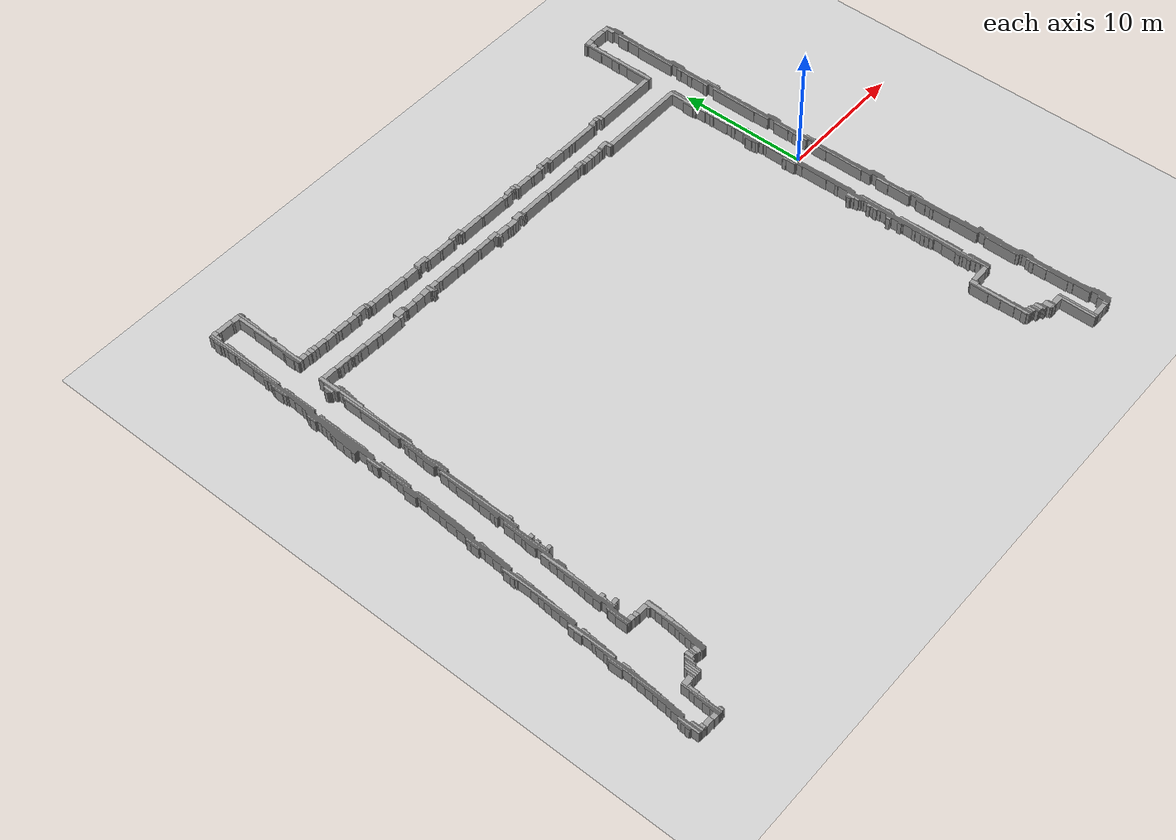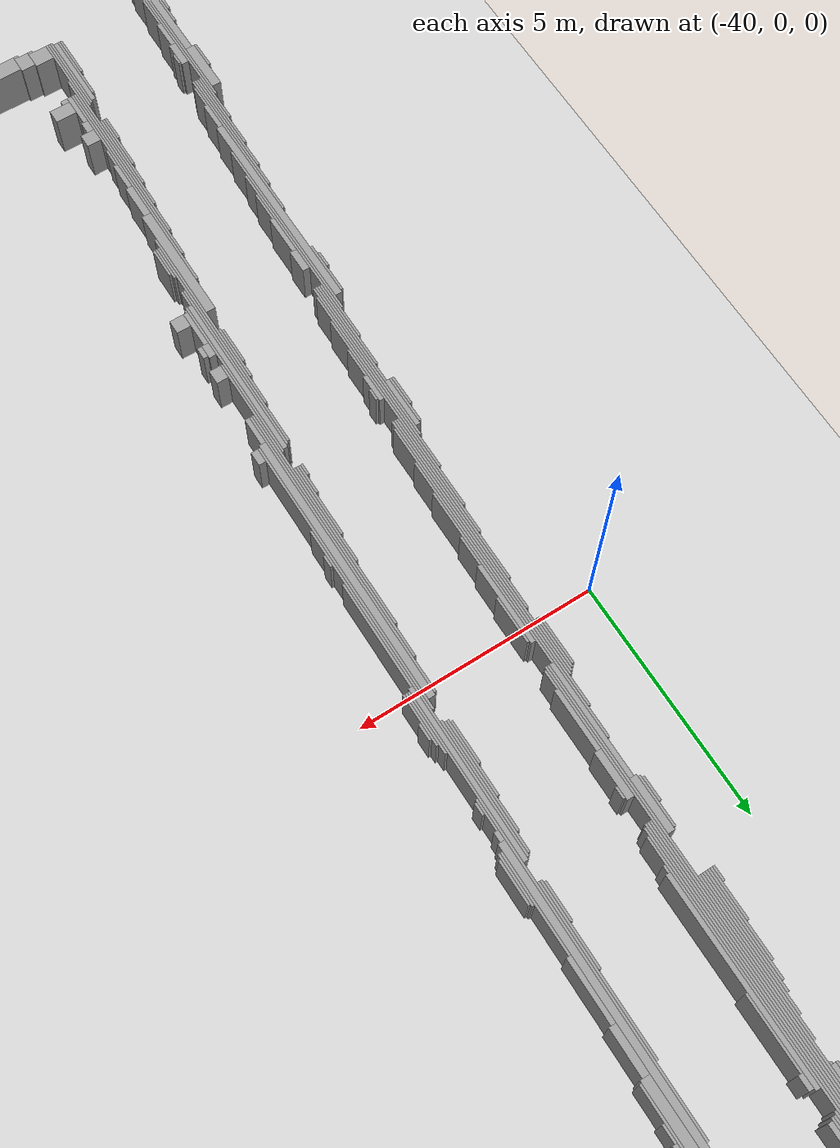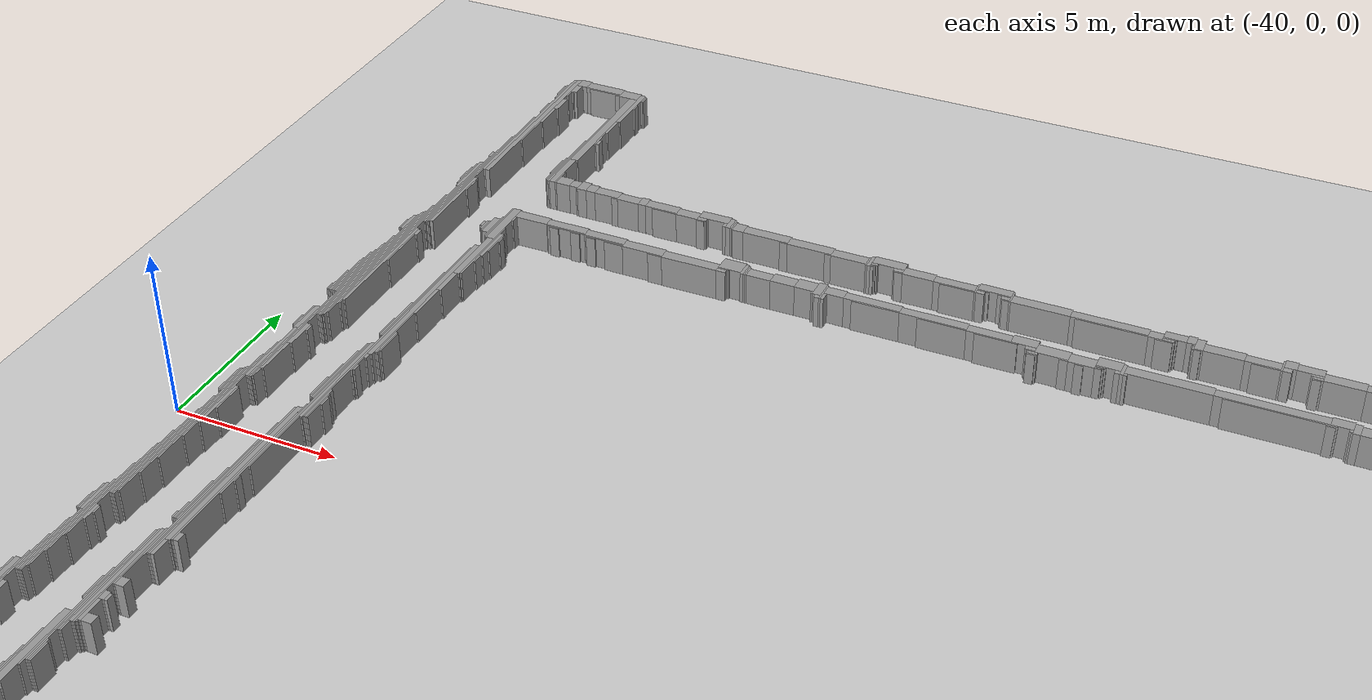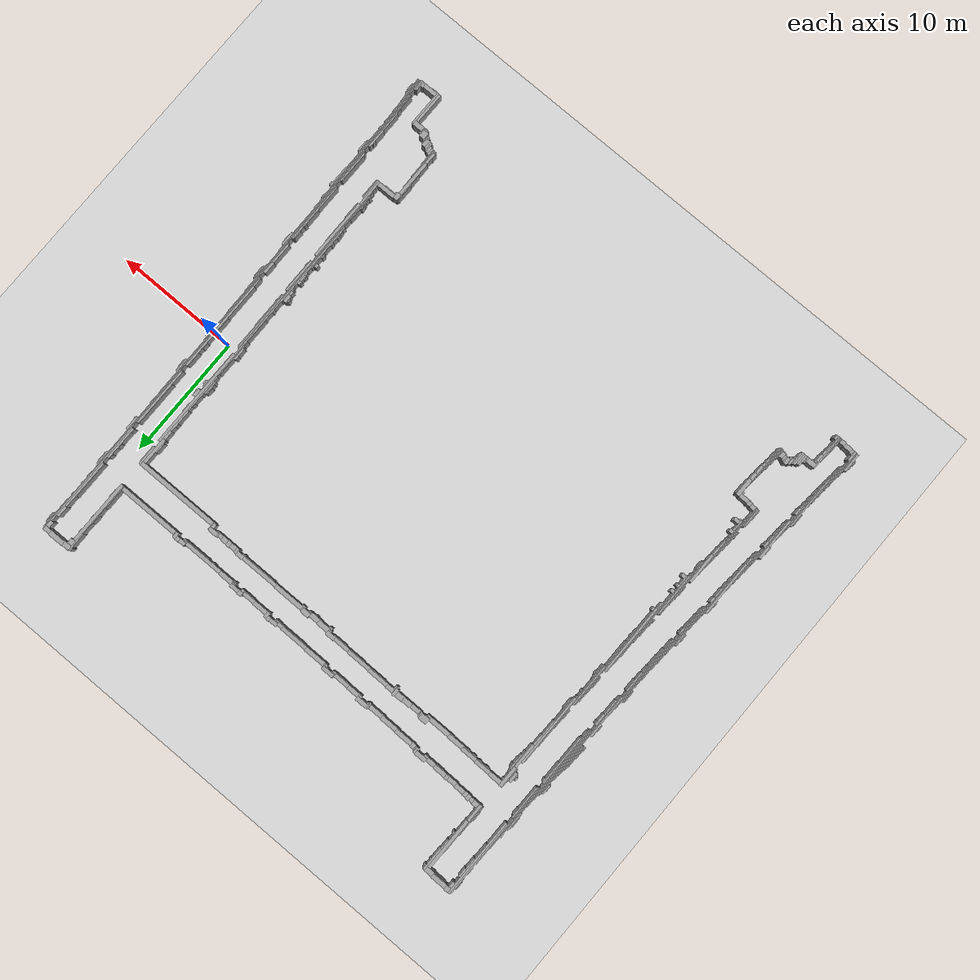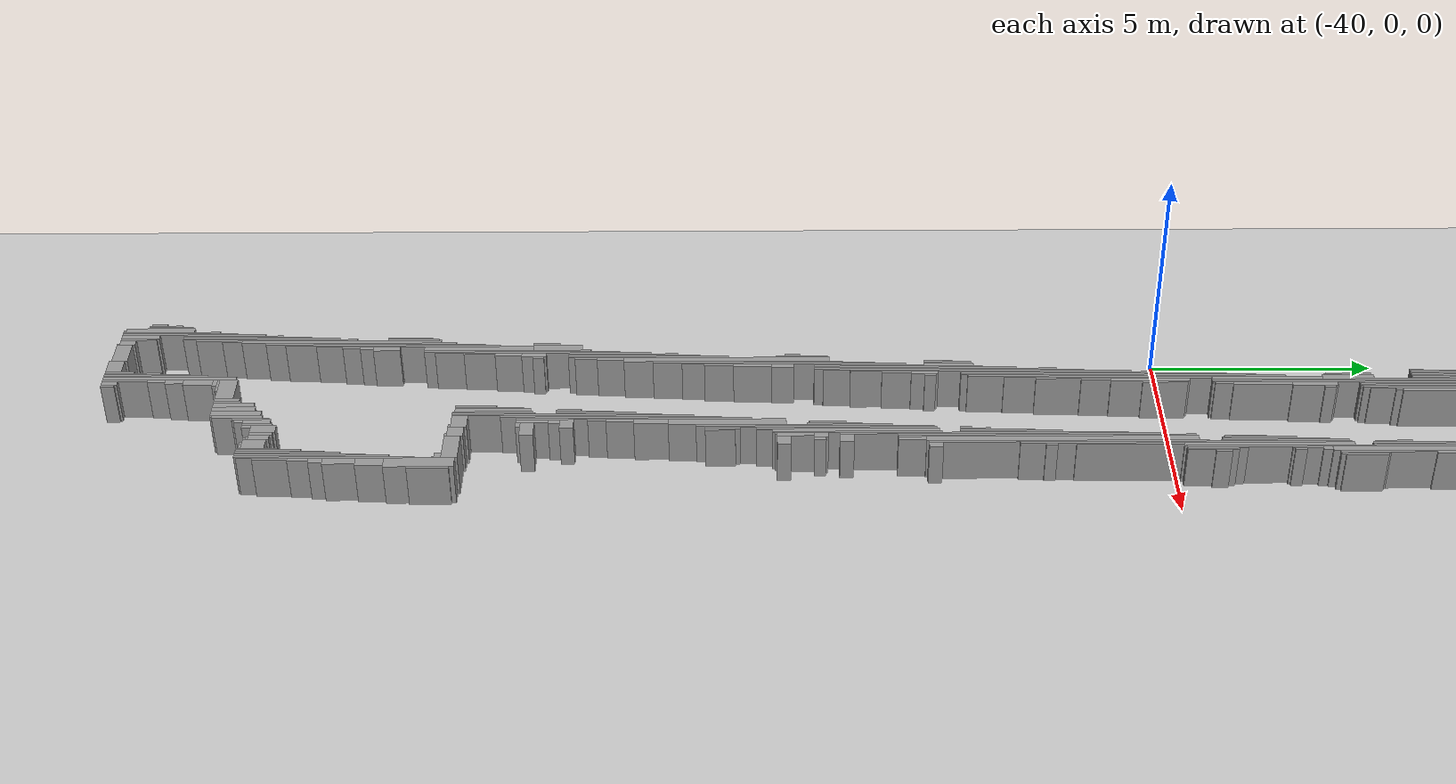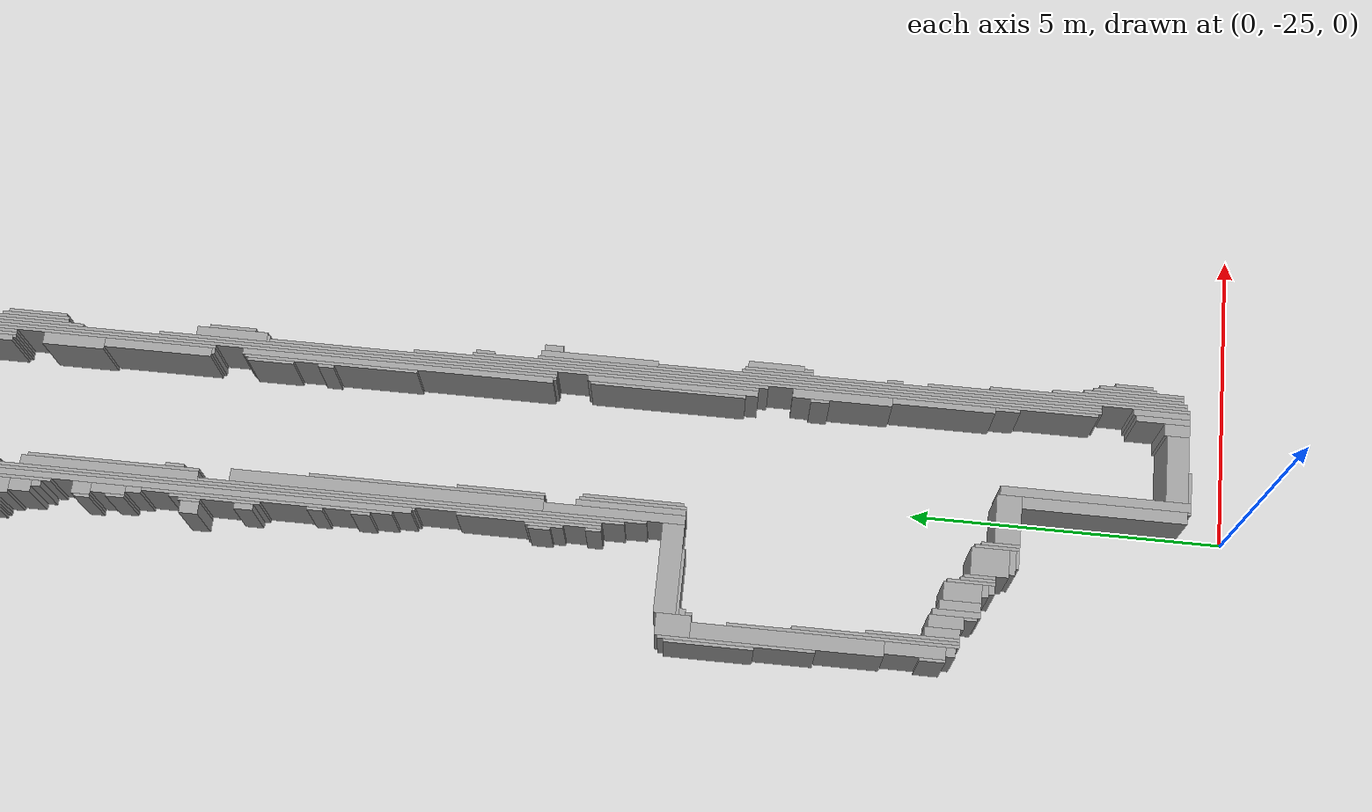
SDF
<?xml version="1.0" ?>
<sdf version="1.6">
  <world name="default">
    <include>
      <uri>model://ground_plane</uri>
    </include>
    <include>
      <uri>model://sun</uri>
    </include>

    <model name='wall_0'>
      <static>1</static>
      <pose>-37.425 19.350000000000005 0.5 0 0 0</pose>
      <link name='link'>
        <collision name='collision'>
          <geometry>
            <box>
              <size>0.35000000000000003 0.4 1.0</size>
            </box>
          </geometry>
        </collision>
        <visual name='visual'>
          <geometry>
            <box>
              <size>0.35000000000000003 0.4 1.0</size>
            </box>
          </geometry>
          <material>
            <script>
              <uri>file://media/materials/scripts/gazebo.material</uri>
              <name>Gazebo/Grey</name>
            </script>
          </material>
        </visual>
      </link>
    </model>

    <model name='wall_1'>
      <static>1</static>
      <pose>-37.675 16.325000000000006 0.5 0 0 0</pose>
      <link name='link'>
        <collision name='collision'>
          <geometry>
            <box>
              <size>0.15000000000000002 6.3500000000000005 1.0</size>
            </box>
          </geometry>
        </collision>
        <visual name='visual'>
          <geometry>
            <box>
              <size>0.15000000000000002 6.3500000000000005 1.0</size>
            </box>
          </geometry>
          <material>
            <script>
              <uri>file://media/materials/scripts/gazebo.material</uri>
              <name>Gazebo/Grey</name>
            </script>
          </material>
        </visual>
      </link>
    </model>

    <model name='wall_2'>
      <static>1</static>
      <pose>-36.625 19.325000000000006 0.5 0 0 0</pose>
      <link name='link'>
        <collision name='collision'>
          <geometry>
            <box>
              <size>1.25 0.35000000000000003 1.0</size>
            </box>
          </geometry>
        </collision>
        <visual name='visual'>
          <geometry>
            <box>
              <size>1.25 0.35000000000000003 1.0</size>
            </box>
          </geometry>
          <material>
            <script>
              <uri>file://media/materials/scripts/gazebo.material</uri>
              <name>Gazebo/Grey</name>
            </script>
          </material>
        </visual>
      </link>
    </model>

    <model name='wall_3'>
      <static>1</static>
      <pose>-37.8 16.3 0.5 0 0 0</pose>
      <link name='link'>
        <collision name='collision'>
          <geometry>
            <box>
              <size>0.1 6.300000000000001 1.0</size>
            </box>
          </geometry>
        </collision>
        <visual name='visual'>
          <geometry>
            <box>
              <size>0.1 6.300000000000001 1.0</size>
            </box>
          </geometry>
          <material>
            <script>
              <uri>file://media/materials/scripts/gazebo.material</uri>
              <name>Gazebo/Grey</name>
            </script>
          </material>
        </visual>
      </link>
    </model>

    <model name='wall_4'>
      <static>1</static>
      <pose>-35.675 19.250000000000004 0.5 0 0 0</pose>
      <link name='link'>
        <collision name='collision'>
          <geometry>
            <box>
              <size>0.65 0.4 1.0</size>
            </box>
          </geometry>
        </collision>
        <visual name='visual'>
          <geometry>
            <box>
              <size>0.65 0.4 1.0</size>
            </box>
          </geometry>
          <material>
            <script>
              <uri>file://media/materials/scripts/gazebo.material</uri>
              <name>Gazebo/Grey</name>
            </script>
          </material>
        </visual>
      </link>
    </model>

    <model name='wall_5'>
      <static>1</static>
      <pose>-35.275 18.450000000000006 0.5 0 0 0</pose>
      <link name='link'>
        <collision name='collision'>
          <geometry>
            <box>
              <size>0.15000000000000002 1.9000000000000001 1.0</size>
            </box>
          </geometry>
        </collision>
        <visual name='visual'>
          <geometry>
            <box>
              <size>0.15000000000000002 1.9000000000000001 1.0</size>
            </box>
          </geometry>
          <material>
            <script>
              <uri>file://media/materials/scripts/gazebo.material</uri>
              <name>Gazebo/Grey</name>
            </script>
          </material>
        </visual>
      </link>
    </model>

    <model name='wall_6'>
      <static>1</static>
      <pose>-35.175 19.175 0.5 0 0 0</pose>
      <link name='link'>
        <collision name='collision'>
          <geometry>
            <box>
              <size>0.05 0.35000000000000003 1.0</size>
            </box>
          </geometry>
        </collision>
        <visual name='visual'>
          <geometry>
            <box>
              <size>0.05 0.35000000000000003 1.0</size>
            </box>
          </geometry>
          <material>
            <script>
              <uri>file://media/materials/scripts/gazebo.material</uri>
              <name>Gazebo/Grey</name>
            </script>
          </material>
        </visual>
      </link>
    </model>

    <model name='wall_7'>
      <static>1</static>
      <pose>-35.125 19.150000000000002 0.5 0 0 0</pose>
      <link name='link'>
        <collision name='collision'>
          <geometry>
            <box>
              <size>0.05 0.30000000000000004 1.0</size>
            </box>
          </geometry>
        </collision>
        <visual name='visual'>
          <geometry>
            <box>
              <size>0.05 0.30000000000000004 1.0</size>
            </box>
          </geometry>
          <material>
            <script>
              <uri>file://media/materials/scripts/gazebo.material</uri>
              <name>Gazebo/Grey</name>
            </script>
          </material>
        </visual>
      </link>
    </model>

    <model name='wall_8'>
      <static>1</static>
      <pose>-37.5 18.925 0.5 0 0 0</pose>
      <link name='link'>
        <collision name='collision'>
          <geometry>
            <box>
              <size>0.2 0.45 1.0</size>
            </box>
          </geometry>
        </collision>
        <visual name='visual'>
          <geometry>
            <box>
              <size>0.2 0.45 1.0</size>
            </box>
          </geometry>
          <material>
            <script>
              <uri>file://media/materials/scripts/gazebo.material</uri>
              <name>Gazebo/Grey</name>
            </script>
          </material>
        </visual>
      </link>
    </model>

    <model name='wall_9'>
      <static>1</static>
      <pose>-36.55 19.125000000000004 0.5 0 0 0</pose>
      <link name='link'>
        <collision name='collision'>
          <geometry>
            <box>
              <size>1.1 0.05 1.0</size>
            </box>
          </geometry>
        </collision>
        <visual name='visual'>
          <geometry>
            <box>
              <size>1.1 0.05 1.0</size>
            </box>
          </geometry>
          <material>
            <script>
              <uri>file://media/materials/scripts/gazebo.material</uri>
              <name>Gazebo/Grey</name>
            </script>
          </material>
        </visual>
      </link>
    </model>

    <model name='wall_10'>
      <static>1</static>
      <pose>-36.074999999999996 19.075000000000006 0.5 0 0 0</pose>
      <link name='link'>
        <collision name='collision'>
          <geometry>
            <box>
              <size>0.15000000000000002 0.05 1.0</size>
            </box>
          </geometry>
        </collision>
        <visual name='visual'>
          <geometry>
            <box>
              <size>0.15000000000000002 0.05 1.0</size>
            </box>
          </geometry>
          <material>
            <script>
              <uri>file://media/materials/scripts/gazebo.material</uri>
              <name>Gazebo/Grey</name>
            </script>
          </material>
        </visual>
      </link>
    </model>

    <model name='wall_11'>
      <static>1</static>
      <pose>-35.474999999999994 16.925 0.5 0 0 0</pose>
      <link name='link'>
        <collision name='collision'>
          <geometry>
            <box>
              <size>0.25 4.25 1.0</size>
            </box>
          </geometry>
        </collision>
        <visual name='visual'>
          <geometry>
            <box>
              <size>0.25 4.25 1.0</size>
            </box>
          </geometry>
          <material>
            <script>
              <uri>file://media/materials/scripts/gazebo.material</uri>
              <name>Gazebo/Grey</name>
            </script>
          </material>
        </visual>
      </link>
    </model>

    <model name='wall_12'>
      <static>1</static>
      <pose>-37.875 18.55 0.5 0 0 0</pose>
      <link name='link'>
        <collision name='collision'>
          <geometry>
            <box>
              <size>0.05 0.9 1.0</size>
            </box>
          </geometry>
        </collision>
        <visual name='visual'>
          <geometry>
            <box>
              <size>0.05 0.9 1.0</size>
            </box>
          </geometry>
          <material>
            <script>
              <uri>file://media/materials/scripts/gazebo.material</uri>
              <name>Gazebo/Grey</name>
            </script>
          </material>
        </visual>
      </link>
    </model>

    <model name='wall_13'>
      <static>1</static>
      <pose>-37.925 18.650000000000002 0.5 0 0 0</pose>
      <link name='link'>
        <collision name='collision'>
          <geometry>
            <box>
              <size>0.05 0.6000000000000001 1.0</size>
            </box>
          </geometry>
        </collision>
        <visual name='visual'>
          <geometry>
            <box>
              <size>0.05 0.6000000000000001 1.0</size>
            </box>
          </geometry>
          <material>
            <script>
              <uri>file://media/materials/scripts/gazebo.material</uri>
              <name>Gazebo/Grey</name>
            </script>
          </material>
        </visual>
      </link>
    </model>

    <model name='wall_14'>
      <static>1</static>
      <pose>0.07500000000000284 18.600000000000005 0.5 0 0 0</pose>
      <link name='link'>
        <collision name='collision'>
          <geometry>
            <box>
              <size>1.25 0.4 1.0</size>
            </box>
          </geometry>
        </collision>
        <visual name='visual'>
          <geometry>
            <box>
              <size>1.25 0.4 1.0</size>
            </box>
          </geometry>
          <material>
            <script>
              <uri>file://media/materials/scripts/gazebo.material</uri>
              <name>Gazebo/Grey</name>
            </script>
          </material>
        </visual>
      </link>
    </model>

    <model name='wall_15'>
      <static>1</static>
      <pose>-0.8499999999999943 18.55 0.5 0 0 0</pose>
      <link name='link'>
        <collision name='collision'>
          <geometry>
            <box>
              <size>0.6000000000000001 0.4 1.0</size>
            </box>
          </geometry>
        </collision>
        <visual name='visual'>
          <geometry>
            <box>
              <size>0.6000000000000001 0.4 1.0</size>
            </box>
          </geometry>
          <material>
            <script>
              <uri>file://media/materials/scripts/gazebo.material</uri>
              <name>Gazebo/Grey</name>
            </script>
          </material>
        </visual>
      </link>
    </model>

    <model name='wall_16'>
      <static>1</static>
      <pose>0.9750000000000014 18.575000000000006 0.5 0 0 0</pose>
      <link name='link'>
        <collision name='collision'>
          <geometry>
            <box>
              <size>0.55 0.35000000000000003 1.0</size>
            </box>
          </geometry>
        </collision>
        <visual name='visual'>
          <geometry>
            <box>
              <size>0.55 0.35000000000000003 1.0</size>
            </box>
          </geometry>
          <material>
            <script>
              <uri>file://media/materials/scripts/gazebo.material</uri>
              <name>Gazebo/Grey</name>
            </script>
          </material>
        </visual>
      </link>
    </model>

    <model name='wall_17'>
      <static>1</static>
      <pose>-37.55 18.675 0.5 0 0 0</pose>
      <link name='link'>
        <collision name='collision'>
          <geometry>
            <box>
              <size>0.1 0.05 1.0</size>
            </box>
          </geometry>
        </collision>
        <visual name='visual'>
          <geometry>
            <box>
              <size>0.1 0.05 1.0</size>
            </box>
          </geometry>
          <material>
            <script>
              <uri>file://media/materials/scripts/gazebo.material</uri>
              <name>Gazebo/Grey</name>
            </script>
          </material>
        </visual>
      </link>
    </model>

    <model name='wall_18'>
      <static>1</static>
      <pose>-35.175 18.575000000000006 0.5 0 0 0</pose>
      <link name='link'>
        <collision name='collision'>
          <geometry>
            <box>
              <size>0.05 0.25 1.0</size>
            </box>
          </geometry>
        </collision>
        <visual name='visual'>
          <geometry>
            <box>
              <size>0.05 0.25 1.0</size>
            </box>
          </geometry>
          <material>
            <script>
              <uri>file://media/materials/scripts/gazebo.material</uri>
              <name>Gazebo/Grey</name>
            </script>
          </material>
        </visual>
      </link>
    </model>

    <model name='wall_19'>
      <static>1</static>
      <pose>-1.1999999999999957 17.925 0.5 0 0 0</pose>
      <link name='link'>
        <collision name='collision'>
          <geometry>
            <box>
              <size>0.1 1.55 1.0</size>
            </box>
          </geometry>
        </collision>
        <visual name='visual'>
          <geometry>
            <box>
              <size>0.1 1.55 1.0</size>
            </box>
          </geometry>
          <material>
            <script>
              <uri>file://media/materials/scripts/gazebo.material</uri>
              <name>Gazebo/Grey</name>
            </script>
          </material>
        </visual>
      </link>
    </model>

    <model name='wall_20'>
      <static>1</static>
      <pose>1.2750000000000057 9.45 0.5 0 0 0</pose>
      <link name='link'>
        <collision name='collision'>
          <geometry>
            <box>
              <size>0.05 18.5 1.0</size>
            </box>
          </geometry>
        </collision>
        <visual name='visual'>
          <geometry>
            <box>
              <size>0.05 18.5 1.0</size>
            </box>
          </geometry>
          <material>
            <script>
              <uri>file://media/materials/scripts/gazebo.material</uri>
              <name>Gazebo/Grey</name>
            </script>
          </material>
        </visual>
      </link>
    </model>

    <model name='wall_21'>
      <static>1</static>
      <pose>-37.574999999999996 18.525000000000002 0.5 0 0 0</pose>
      <link name='link'>
        <collision name='collision'>
          <geometry>
            <box>
              <size>0.05 0.25 1.0</size>
            </box>
          </geometry>
        </collision>
        <visual name='visual'>
          <geometry>
            <box>
              <size>0.05 0.25 1.0</size>
            </box>
          </geometry>
          <material>
            <script>
              <uri>file://media/materials/scripts/gazebo.material</uri>
              <name>Gazebo/Grey</name>
            </script>
          </material>
        </visual>
      </link>
    </model>

    <model name='wall_22'>
      <static>1</static>
      <pose>-1.2999999999999972 18.525000000000002 0.5 0 0 0</pose>
      <link name='link'>
        <collision name='collision'>
          <geometry>
            <box>
              <size>0.1 0.25 1.0</size>
            </box>
          </geometry>
        </collision>
        <visual name='visual'>
          <geometry>
            <box>
              <size>0.1 0.25 1.0</size>
            </box>
          </geometry>
          <material>
            <script>
              <uri>file://media/materials/scripts/gazebo.material</uri>
              <name>Gazebo/Grey</name>
            </script>
          </material>
        </visual>
      </link>
    </model>

    <model name='wall_23'>
      <static>1</static>
      <pose>1.3250000000000028 17.225000000000005 0.5 0 0 0</pose>
      <link name='link'>
        <collision name='collision'>
          <geometry>
            <box>
              <size>0.05 2.6500000000000004 1.0</size>
            </box>
          </geometry>
        </collision>
        <visual name='visual'>
          <geometry>
            <box>
              <size>0.05 2.6500000000000004 1.0</size>
            </box>
          </geometry>
          <material>
            <script>
              <uri>file://media/materials/scripts/gazebo.material</uri>
              <name>Gazebo/Grey</name>
            </script>
          </material>
        </visual>
      </link>
    </model>

    <model name='wall_24'>
      <static>1</static>
      <pose>-1.2749999999999986 18.375000000000004 0.5 0 0 0</pose>
      <link name='link'>
        <collision name='collision'>
          <geometry>
            <box>
              <size>0.05 0.05 1.0</size>
            </box>
          </geometry>
        </collision>
        <visual name='visual'>
          <geometry>
            <box>
              <size>0.05 0.05 1.0</size>
            </box>
          </geometry>
          <material>
            <script>
              <uri>file://media/materials/scripts/gazebo.material</uri>
              <name>Gazebo/Grey</name>
            </script>
          </material>
        </visual>
      </link>
    </model>

    <model name='wall_25'>
      <static>1</static>
      <pose>1.1000000000000014 18.150000000000002 0.5 0 0 0</pose>
      <link name='link'>
        <collision name='collision'>
          <geometry>
            <box>
              <size>0.30000000000000004 0.5 1.0</size>
            </box>
          </geometry>
        </collision>
        <visual name='visual'>
          <geometry>
            <box>
              <size>0.30000000000000004 0.5 1.0</size>
            </box>
          </geometry>
          <material>
            <script>
              <uri>file://media/materials/scripts/gazebo.material</uri>
              <name>Gazebo/Grey</name>
            </script>
          </material>
        </visual>
      </link>
    </model>

    <model name='wall_26'>
      <static>1</static>
      <pose>-0.9499999999999957 18.125000000000004 0.5 0 0 0</pose>
      <link name='link'>
        <collision name='collision'>
          <geometry>
            <box>
              <size>0.4 0.45 1.0</size>
            </box>
          </geometry>
        </collision>
        <visual name='visual'>
          <geometry>
            <box>
              <size>0.4 0.45 1.0</size>
            </box>
          </geometry>
          <material>
            <script>
              <uri>file://media/materials/scripts/gazebo.material</uri>
              <name>Gazebo/Grey</name>
            </script>
          </material>
        </visual>
      </link>
    </model>

    <model name='wall_27'>
      <static>1</static>
      <pose>1.375000000000007 17.8 0.5 0 0 0</pose>
      <link name='link'>
        <collision name='collision'>
          <geometry>
            <box>
              <size>0.05 0.9 1.0</size>
            </box>
          </geometry>
        </collision>
        <visual name='visual'>
          <geometry>
            <box>
              <size>0.05 0.9 1.0</size>
            </box>
          </geometry>
          <material>
            <script>
              <uri>file://media/materials/scripts/gazebo.material</uri>
              <name>Gazebo/Grey</name>
            </script>
          </material>
        </visual>
      </link>
    </model>

    <model name='wall_28'>
      <static>1</static>
      <pose>1.4250000000000043 17.775000000000002 0.5 0 0 0</pose>
      <link name='link'>
        <collision name='collision'>
          <geometry>
            <box>
              <size>0.05 0.8500000000000001 1.0</size>
            </box>
          </geometry>
        </collision>
        <visual name='visual'>
          <geometry>
            <box>
              <size>0.05 0.8500000000000001 1.0</size>
            </box>
          </geometry>
          <material>
            <script>
              <uri>file://media/materials/scripts/gazebo.material</uri>
              <name>Gazebo/Grey</name>
            </script>
          </material>
        </visual>
      </link>
    </model>

    <model name='wall_29'>
      <static>1</static>
      <pose>-37.525 17.8 0.5 0 0 0</pose>
      <link name='link'>
        <collision name='collision'>
          <geometry>
            <box>
              <size>0.15000000000000002 0.7000000000000001 1.0</size>
            </box>
          </geometry>
        </collision>
        <visual name='visual'>
          <geometry>
            <box>
              <size>0.15000000000000002 0.7000000000000001 1.0</size>
            </box>
          </geometry>
          <material>
            <script>
              <uri>file://media/materials/scripts/gazebo.material</uri>
              <name>Gazebo/Grey</name>
            </script>
          </material>
        </visual>
      </link>
    </model>

    <model name='wall_30'>
      <static>1</static>
      <pose>1.4750000000000014 17.700000000000006 0.5 0 0 0</pose>
      <link name='link'>
        <collision name='collision'>
          <geometry>
            <box>
              <size>0.05 0.7000000000000001 1.0</size>
            </box>
          </geometry>
        </collision>
        <visual name='visual'>
          <geometry>
            <box>
              <size>0.05 0.7000000000000001 1.0</size>
            </box>
          </geometry>
          <material>
            <script>
              <uri>file://media/materials/scripts/gazebo.material</uri>
              <name>Gazebo/Grey</name>
            </script>
          </material>
        </visual>
      </link>
    </model>

    <model name='wall_31'>
      <static>1</static>
      <pose>-1.0249999999999986 15.275000000000002 0.5 0 0 0</pose>
      <link name='link'>
        <collision name='collision'>
          <geometry>
            <box>
              <size>0.25 5.25 1.0</size>
            </box>
          </geometry>
        </collision>
        <visual name='visual'>
          <geometry>
            <box>
              <size>0.25 5.25 1.0</size>
            </box>
          </geometry>
          <material>
            <script>
              <uri>file://media/materials/scripts/gazebo.material</uri>
              <name>Gazebo/Grey</name>
            </script>
          </material>
        </visual>
      </link>
    </model>

    <model name='wall_32'>
      <static>1</static>
      <pose>1.2000000000000028 13.475000000000005 0.5 0 0 0</pose>
      <link name='link'>
        <collision name='collision'>
          <geometry>
            <box>
              <size>0.1 8.85 1.0</size>
            </box>
          </geometry>
        </collision>
        <visual name='visual'>
          <geometry>
            <box>
              <size>0.1 8.85 1.0</size>
            </box>
          </geometry>
          <material>
            <script>
              <uri>file://media/materials/scripts/gazebo.material</uri>
              <name>Gazebo/Grey</name>
            </script>
          </material>
        </visual>
      </link>
    </model>

    <model name='wall_33'>
      <static>1</static>
      <pose>-37.875 17.375000000000004 0.5 0 0 0</pose>
      <link name='link'>
        <collision name='collision'>
          <geometry>
            <box>
              <size>0.05 0.65 1.0</size>
            </box>
          </geometry>
        </collision>
        <visual name='visual'>
          <geometry>
            <box>
              <size>0.05 0.65 1.0</size>
            </box>
          </geometry>
          <material>
            <script>
              <uri>file://media/materials/scripts/gazebo.material</uri>
              <name>Gazebo/Grey</name>
            </script>
          </material>
        </visual>
      </link>
    </model>

    <model name='wall_34'>
      <static>1</static>
      <pose>-35.625 15.475000000000005 0.5 0 0 0</pose>
      <link name='link'>
        <collision name='collision'>
          <geometry>
            <box>
              <size>0.05 4.25 1.0</size>
            </box>
          </geometry>
        </collision>
        <visual name='visual'>
          <geometry>
            <box>
              <size>0.05 4.25 1.0</size>
            </box>
          </geometry>
          <material>
            <script>
              <uri>file://media/materials/scripts/gazebo.material</uri>
              <name>Gazebo/Grey</name>
            </script>
          </material>
        </visual>
      </link>
    </model>

    <model name='wall_35'>
      <static>1</static>
      <pose>-35.3 17.100000000000005 0.5 0 0 0</pose>
      <link name='link'>
        <collision name='collision'>
          <geometry>
            <box>
              <size>0.1 0.8 1.0</size>
            </box>
          </geometry>
        </collision>
        <visual name='visual'>
          <geometry>
            <box>
              <size>0.1 0.8 1.0</size>
            </box>
          </geometry>
          <material>
            <script>
              <uri>file://media/materials/scripts/gazebo.material</uri>
              <name>Gazebo/Grey</name>
            </script>
          </material>
        </visual>
      </link>
    </model>

    <model name='wall_36'>
      <static>1</static>
      <pose>-37.55 16.975000000000005 0.5 0 0 0</pose>
      <link name='link'>
        <collision name='collision'>
          <geometry>
            <box>
              <size>0.1 0.9500000000000001 1.0</size>
            </box>
          </geometry>
        </collision>
        <visual name='visual'>
          <geometry>
            <box>
              <size>0.1 0.9500000000000001 1.0</size>
            </box>
          </geometry>
          <material>
            <script>
              <uri>file://media/materials/scripts/gazebo.material</uri>
              <name>Gazebo/Grey</name>
            </script>
          </material>
        </visual>
      </link>
    </model>

    <model name='wall_37'>
      <static>1</static>
      <pose>1.0500000000000043 16.900000000000002 0.5 0 0 0</pose>
      <link name='link'>
        <collision name='collision'>
          <geometry>
            <box>
              <size>0.2 0.9 1.0</size>
            </box>
          </geometry>
        </collision>
        <visual name='visual'>
          <geometry>
            <box>
              <size>0.2 0.9 1.0</size>
            </box>
          </geometry>
          <material>
            <script>
              <uri>file://media/materials/scripts/gazebo.material</uri>
              <name>Gazebo/Grey</name>
            </script>
          </material>
        </visual>
      </link>
    </model>

    <model name='wall_38'>
      <static>1</static>
      <pose>-0.8749999999999929 17.075000000000006 0.5 0 0 0</pose>
      <link name='link'>
        <collision name='collision'>
          <geometry>
            <box>
              <size>0.05 0.25 1.0</size>
            </box>
          </geometry>
        </collision>
        <visual name='visual'>
          <geometry>
            <box>
              <size>0.05 0.25 1.0</size>
            </box>
          </geometry>
          <material>
            <script>
              <uri>file://media/materials/scripts/gazebo.material</uri>
              <name>Gazebo/Grey</name>
            </script>
          </material>
        </visual>
      </link>
    </model>

    <model name='wall_39'>
      <static>1</static>
      <pose>-1.1749999999999972 14.900000000000002 0.5 0 0 0</pose>
      <link name='link'>
        <collision name='collision'>
          <geometry>
            <box>
              <size>0.05 4.5 1.0</size>
            </box>
          </geometry>
        </collision>
        <visual name='visual'>
          <geometry>
            <box>
              <size>0.05 4.5 1.0</size>
            </box>
          </geometry>
          <material>
            <script>
              <uri>file://media/materials/scripts/gazebo.material</uri>
              <name>Gazebo/Grey</name>
            </script>
          </material>
        </visual>
      </link>
    </model>

    <model name='wall_40'>
      <static>1</static>
      <pose>-37.875 13.250000000000004 0.5 0 0 0</pose>
      <link name='link'>
        <collision name='collision'>
          <geometry>
            <box>
              <size>0.05 6.9 1.0</size>
            </box>
          </geometry>
        </collision>
        <visual name='visual'>
          <geometry>
            <box>
              <size>0.05 6.9 1.0</size>
            </box>
          </geometry>
          <material>
            <script>
              <uri>file://media/materials/scripts/gazebo.material</uri>
              <name>Gazebo/Grey</name>
            </script>
          </material>
        </visual>
      </link>
    </model>

    <model name='wall_41'>
      <static>1</static>
      <pose>-35.324999999999996 16.325000000000006 0.5 0 0 0</pose>
      <link name='link'>
        <collision name='collision'>
          <geometry>
            <box>
              <size>0.05 0.75 1.0</size>
            </box>
          </geometry>
        </collision>
        <visual name='visual'>
          <geometry>
            <box>
              <size>0.05 0.75 1.0</size>
            </box>
          </geometry>
          <material>
            <script>
              <uri>file://media/materials/scripts/gazebo.material</uri>
              <name>Gazebo/Grey</name>
            </script>
          </material>
        </visual>
      </link>
    </model>

    <model name='wall_42'>
      <static>1</static>
      <pose>-37.574999999999996 15.850000000000005 0.5 0 0 0</pose>
      <link name='link'>
        <collision name='collision'>
          <geometry>
            <box>
              <size>0.05 1.3 1.0</size>
            </box>
          </geometry>
        </collision>
        <visual name='visual'>
          <geometry>
            <box>
              <size>0.05 1.3 1.0</size>
            </box>
          </geometry>
          <material>
            <script>
              <uri>file://media/materials/scripts/gazebo.material</uri>
              <name>Gazebo/Grey</name>
            </script>
          </material>
        </visual>
      </link>
    </model>

    <model name='wall_43'>
      <static>1</static>
      <pose>1.0750000000000028 14.400000000000002 0.5 0 0 0</pose>
      <link name='link'>
        <collision name='collision'>
          <geometry>
            <box>
              <size>0.15000000000000002 4.1000000000000005 1.0</size>
            </box>
          </geometry>
        </collision>
        <visual name='visual'>
          <geometry>
            <box>
              <size>0.15000000000000002 4.1000000000000005 1.0</size>
            </box>
          </geometry>
          <material>
            <script>
              <uri>file://media/materials/scripts/gazebo.material</uri>
              <name>Gazebo/Grey</name>
            </script>
          </material>
        </visual>
      </link>
    </model>

    <model name='wall_44'>
      <static>1</static>
      <pose>-35.25 16.075000000000006 0.5 0 0 0</pose>
      <link name='link'>
        <collision name='collision'>
          <geometry>
            <box>
              <size>0.1 0.25 1.0</size>
            </box>
          </geometry>
        </collision>
        <visual name='visual'>
          <geometry>
            <box>
              <size>0.1 0.25 1.0</size>
            </box>
          </geometry>
          <material>
            <script>
              <uri>file://media/materials/scripts/gazebo.material</uri>
              <name>Gazebo/Grey</name>
            </script>
          </material>
        </visual>
      </link>
    </model>

    <model name='wall_45'>
      <static>1</static>
      <pose>-1.2249999999999943 15.8 0.5 0 0 0</pose>
      <link name='link'>
        <collision name='collision'>
          <geometry>
            <box>
              <size>0.05 0.7000000000000001 1.0</size>
            </box>
          </geometry>
        </collision>
        <visual name='visual'>
          <geometry>
            <box>
              <size>0.05 0.7000000000000001 1.0</size>
            </box>
          </geometry>
          <material>
            <script>
              <uri>file://media/materials/scripts/gazebo.material</uri>
              <name>Gazebo/Grey</name>
            </script>
          </material>
        </visual>
      </link>
    </model>

    <model name='wall_46'>
      <static>1</static>
      <pose>-35.675 14.675 0.5 0 0 0</pose>
      <link name='link'>
        <collision name='collision'>
          <geometry>
            <box>
              <size>0.05 2.6500000000000004 1.0</size>
            </box>
          </geometry>
        </collision>
        <visual name='visual'>
          <geometry>
            <box>
              <size>0.05 2.6500000000000004 1.0</size>
            </box>
          </geometry>
          <material>
            <script>
              <uri>file://media/materials/scripts/gazebo.material</uri>
              <name>Gazebo/Grey</name>
            </script>
          </material>
        </visual>
      </link>
    </model>

    <model name='wall_47'>
      <static>1</static>
      <pose>-0.8749999999999929 15.775000000000002 0.5 0 0 0</pose>
      <link name='link'>
        <collision name='collision'>
          <geometry>
            <box>
              <size>0.05 0.25 1.0</size>
            </box>
          </geometry>
        </collision>
        <visual name='visual'>
          <geometry>
            <box>
              <size>0.05 0.25 1.0</size>
            </box>
          </geometry>
          <material>
            <script>
              <uri>file://media/materials/scripts/gazebo.material</uri>
              <name>Gazebo/Grey</name>
            </script>
          </material>
        </visual>
      </link>
    </model>

    <model name='wall_48'>
      <static>1</static>
      <pose>1.3250000000000028 15.425 0.5 0 0 0</pose>
      <link name='link'>
        <collision name='collision'>
          <geometry>
            <box>
              <size>0.05 0.25 1.0</size>
            </box>
          </geometry>
        </collision>
        <visual name='visual'>
          <geometry>
            <box>
              <size>0.05 0.25 1.0</size>
            </box>
          </geometry>
          <material>
            <script>
              <uri>file://media/materials/scripts/gazebo.material</uri>
              <name>Gazebo/Grey</name>
            </script>
          </material>
        </visual>
      </link>
    </model>

    <model name='wall_49'>
      <static>1</static>
      <pose>0.9750000000000014 13.900000000000002 0.5 0 0 0</pose>
      <link name='link'>
        <collision name='collision'>
          <geometry>
            <box>
              <size>0.05 3.1 1.0</size>
            </box>
          </geometry>
        </collision>
        <visual name='visual'>
          <geometry>
            <box>
              <size>0.05 3.1 1.0</size>
            </box>
          </geometry>
          <material>
            <script>
              <uri>file://media/materials/scripts/gazebo.material</uri>
              <name>Gazebo/Grey</name>
            </script>
          </material>
        </visual>
      </link>
    </model>

    <model name='wall_50'>
      <static>1</static>
      <pose>-37.925 12.525000000000002 0.5 0 0 0</pose>
      <link name='link'>
        <collision name='collision'>
          <geometry>
            <box>
              <size>0.05 5.550000000000001 1.0</size>
            </box>
          </geometry>
        </collision>
        <visual name='visual'>
          <geometry>
            <box>
              <size>0.05 5.550000000000001 1.0</size>
            </box>
          </geometry>
          <material>
            <script>
              <uri>file://media/materials/scripts/gazebo.material</uri>
              <name>Gazebo/Grey</name>
            </script>
          </material>
        </visual>
      </link>
    </model>

    <model name='wall_51'>
      <static>1</static>
      <pose>-35.724999999999994 14.100000000000005 0.5 0 0 0</pose>
      <link name='link'>
        <collision name='collision'>
          <geometry>
            <box>
              <size>0.05 1.4000000000000001 1.0</size>
            </box>
          </geometry>
        </collision>
        <visual name='visual'>
          <geometry>
            <box>
              <size>0.05 1.4000000000000001 1.0</size>
            </box>
          </geometry>
          <material>
            <script>
              <uri>file://media/materials/scripts/gazebo.material</uri>
              <name>Gazebo/Grey</name>
            </script>
          </material>
        </visual>
      </link>
    </model>

    <model name='wall_52'>
      <static>1</static>
      <pose>-35.5 14.075000000000006 0.5 0 0 0</pose>
      <link name='link'>
        <collision name='collision'>
          <geometry>
            <box>
              <size>0.2 1.4500000000000002 1.0</size>
            </box>
          </geometry>
        </collision>
        <visual name='visual'>
          <geometry>
            <box>
              <size>0.2 1.4500000000000002 1.0</size>
            </box>
          </geometry>
          <material>
            <script>
              <uri>file://media/materials/scripts/gazebo.material</uri>
              <name>Gazebo/Grey</name>
            </script>
          </material>
        </visual>
      </link>
    </model>

    <model name='wall_53'>
      <static>1</static>
      <pose>-1.2249999999999943 13.675 0.5 0 0 0</pose>
      <link name='link'>
        <collision name='collision'>
          <geometry>
            <box>
              <size>0.05 2.0500000000000003 1.0</size>
            </box>
          </geometry>
        </collision>
        <visual name='visual'>
          <geometry>
            <box>
              <size>0.05 2.0500000000000003 1.0</size>
            </box>
          </geometry>
          <material>
            <script>
              <uri>file://media/materials/scripts/gazebo.material</uri>
              <name>Gazebo/Grey</name>
            </script>
          </material>
        </visual>
      </link>
    </model>

    <model name='wall_54'>
      <static>1</static>
      <pose>-35.775 14.200000000000006 0.5 0 0 0</pose>
      <link name='link'>
        <collision name='collision'>
          <geometry>
            <box>
              <size>0.05 0.8 1.0</size>
            </box>
          </geometry>
        </collision>
        <visual name='visual'>
          <geometry>
            <box>
              <size>0.05 0.8 1.0</size>
            </box>
          </geometry>
          <material>
            <script>
              <uri>file://media/materials/scripts/gazebo.material</uri>
              <name>Gazebo/Grey</name>
            </script>
          </material>
        </visual>
      </link>
    </model>

    <model name='wall_55'>
      <static>1</static>
      <pose>1.3250000000000028 14.425 0.5 0 0 0</pose>
      <link name='link'>
        <collision name='collision'>
          <geometry>
            <box>
              <size>0.05 0.25 1.0</size>
            </box>
          </geometry>
        </collision>
        <visual name='visual'>
          <geometry>
            <box>
              <size>0.05 0.25 1.0</size>
            </box>
          </geometry>
          <material>
            <script>
              <uri>file://media/materials/scripts/gazebo.material</uri>
              <name>Gazebo/Grey</name>
            </script>
          </material>
        </visual>
      </link>
    </model>

    <model name='wall_56'>
      <static>1</static>
      <pose>-38.0 14.05 0.5 0 0 0</pose>
      <link name='link'>
        <collision name='collision'>
          <geometry>
            <box>
              <size>0.1 0.30000000000000004 1.0</size>
            </box>
          </geometry>
        </collision>
        <visual name='visual'>
          <geometry>
            <box>
              <size>0.1 0.30000000000000004 1.0</size>
            </box>
          </geometry>
          <material>
            <script>
              <uri>file://media/materials/scripts/gazebo.material</uri>
              <name>Gazebo/Grey</name>
            </script>
          </material>
        </visual>
      </link>
    </model>

    <model name='wall_57'>
      <static>1</static>
      <pose>-35.375 13.675 0.5 0 0 0</pose>
      <link name='link'>
        <collision name='collision'>
          <geometry>
            <box>
              <size>0.05 0.65 1.0</size>
            </box>
          </geometry>
        </collision>
        <visual name='visual'>
          <geometry>
            <box>
              <size>0.05 0.65 1.0</size>
            </box>
          </geometry>
          <material>
            <script>
              <uri>file://media/materials/scripts/gazebo.material</uri>
              <name>Gazebo/Grey</name>
            </script>
          </material>
        </visual>
      </link>
    </model>

    <model name='wall_58'>
      <static>1</static>
      <pose>-37.974999999999994 9.2 0.5 0 0 0</pose>
      <link name='link'>
        <collision name='collision'>
          <geometry>
            <box>
              <size>0.05 9.4 1.0</size>
            </box>
          </geometry>
        </collision>
        <visual name='visual'>
          <geometry>
            <box>
              <size>0.05 9.4 1.0</size>
            </box>
          </geometry>
          <material>
            <script>
              <uri>file://media/materials/scripts/gazebo.material</uri>
              <name>Gazebo/Grey</name>
            </script>
          </material>
        </visual>
      </link>
    </model>

    <model name='wall_59'>
      <static>1</static>
      <pose>-0.8749999999999929 13.55 0.5 0 0 0</pose>
      <link name='link'>
        <collision name='collision'>
          <geometry>
            <box>
              <size>0.05 0.7000000000000001 1.0</size>
            </box>
          </geometry>
        </collision>
        <visual name='visual'>
          <geometry>
            <box>
              <size>0.05 0.7000000000000001 1.0</size>
            </box>
          </geometry>
          <material>
            <script>
              <uri>file://media/materials/scripts/gazebo.material</uri>
              <name>Gazebo/Grey</name>
            </script>
          </material>
        </visual>
      </link>
    </model>

    <model name='wall_60'>
      <static>1</static>
      <pose>1.3250000000000028 13.600000000000005 0.5 0 0 0</pose>
      <link name='link'>
        <collision name='collision'>
          <geometry>
            <box>
              <size>0.05 0.6000000000000001 1.0</size>
            </box>
          </geometry>
        </collision>
        <visual name='visual'>
          <geometry>
            <box>
              <size>0.05 0.6000000000000001 1.0</size>
            </box>
          </geometry>
          <material>
            <script>
              <uri>file://media/materials/scripts/gazebo.material</uri>
              <name>Gazebo/Grey</name>
            </script>
          </material>
        </visual>
      </link>
    </model>

    <model name='wall_61'>
      <static>1</static>
      <pose>-35.125 13.55 0.5 0 0 0</pose>
      <link name='link'>
        <collision name='collision'>
          <geometry>
            <box>
              <size>0.45 0.4 1.0</size>
            </box>
          </geometry>
        </collision>
        <visual name='visual'>
          <geometry>
            <box>
              <size>0.45 0.4 1.0</size>
            </box>
          </geometry>
          <material>
            <script>
              <uri>file://media/materials/scripts/gazebo.material</uri>
              <name>Gazebo/Grey</name>
            </script>
          </material>
        </visual>
      </link>
    </model>

    <model name='wall_62'>
      <static>1</static>
      <pose>-34.449999999999996 13.525000000000002 0.5 0 0 0</pose>
      <link name='link'>
        <collision name='collision'>
          <geometry>
            <box>
              <size>0.30000000000000004 0.45 1.0</size>
            </box>
          </geometry>
        </collision>
        <visual name='visual'>
          <geometry>
            <box>
              <size>0.30000000000000004 0.45 1.0</size>
            </box>
          </geometry>
          <material>
            <script>
              <uri>file://media/materials/scripts/gazebo.material</uri>
              <name>Gazebo/Grey</name>
            </script>
          </material>
        </visual>
      </link>
    </model>

    <model name='wall_63'>
      <static>1</static>
      <pose>-34.75 13.525000000000002 0.5 0 0 0</pose>
      <link name='link'>
        <collision name='collision'>
          <geometry>
            <box>
              <size>0.30000000000000004 0.35000000000000003 1.0</size>
            </box>
          </geometry>
        </collision>
        <visual name='visual'>
          <geometry>
            <box>
              <size>0.30000000000000004 0.35000000000000003 1.0</size>
            </box>
          </geometry>
          <material>
            <script>
              <uri>file://media/materials/scripts/gazebo.material</uri>
              <name>Gazebo/Grey</name>
            </script>
          </material>
        </visual>
      </link>
    </model>

    <model name='wall_64'>
      <static>1</static>
      <pose>-34.15 13.500000000000004 0.5 0 0 0</pose>
      <link name='link'>
        <collision name='collision'>
          <geometry>
            <box>
              <size>0.30000000000000004 0.4 1.0</size>
            </box>
          </geometry>
        </collision>
        <visual name='visual'>
          <geometry>
            <box>
              <size>0.30000000000000004 0.4 1.0</size>
            </box>
          </geometry>
          <material>
            <script>
              <uri>file://media/materials/scripts/gazebo.material</uri>
              <name>Gazebo/Grey</name>
            </script>
          </material>
        </visual>
      </link>
    </model>

    <model name='wall_65'>
      <static>1</static>
      <pose>-30.025 13.525000000000002 0.5 0 0 0</pose>
      <link name='link'>
        <collision name='collision'>
          <geometry>
            <box>
              <size>0.9500000000000001 0.35000000000000003 1.0</size>
            </box>
          </geometry>
        </collision>
        <visual name='visual'>
          <geometry>
            <box>
              <size>0.9500000000000001 0.35000000000000003 1.0</size>
            </box>
          </geometry>
          <material>
            <script>
              <uri>file://media/materials/scripts/gazebo.material</uri>
              <name>Gazebo/Grey</name>
            </script>
          </material>
        </visual>
      </link>
    </model>

    <model name='wall_66'>
      <static>1</static>
      <pose>-33.599999999999994 13.475000000000005 0.5 0 0 0</pose>
      <link name='link'>
        <collision name='collision'>
          <geometry>
            <box>
              <size>0.8 0.35000000000000003 1.0</size>
            </box>
          </geometry>
        </collision>
        <visual name='visual'>
          <geometry>
            <box>
              <size>0.8 0.35000000000000003 1.0</size>
            </box>
          </geometry>
          <material>
            <script>
              <uri>file://media/materials/scripts/gazebo.material</uri>
              <name>Gazebo/Grey</name>
            </script>
          </material>
        </visual>
      </link>
    </model>

    <model name='wall_67'>
      <static>1</static>
      <pose>-32.375 13.450000000000006 0.5 0 0 0</pose>
      <link name='link'>
        <collision name='collision'>
          <geometry>
            <box>
              <size>0.25 0.4 1.0</size>
            </box>
          </geometry>
        </collision>
        <visual name='visual'>
          <geometry>
            <box>
              <size>0.25 0.4 1.0</size>
            </box>
          </geometry>
          <material>
            <script>
              <uri>file://media/materials/scripts/gazebo.material</uri>
              <name>Gazebo/Grey</name>
            </script>
          </material>
        </visual>
      </link>
    </model>

    <model name='wall_68'>
      <static>1</static>
      <pose>-29.474999999999998 13.400000000000002 0.5 0 0 0</pose>
      <link name='link'>
        <collision name='collision'>
          <geometry>
            <box>
              <size>0.15000000000000002 0.5 1.0</size>
            </box>
          </geometry>
        </collision>
        <visual name='visual'>
          <geometry>
            <box>
              <size>0.15000000000000002 0.5 1.0</size>
            </box>
          </geometry>
          <material>
            <script>
              <uri>file://media/materials/scripts/gazebo.material</uri>
              <name>Gazebo/Grey</name>
            </script>
          </material>
        </visual>
      </link>
    </model>

    <model name='wall_69'>
      <static>1</static>
      <pose>-32.849999999999994 13.425 0.5 0 0 0</pose>
      <link name='link'>
        <collision name='collision'>
          <geometry>
            <box>
              <size>0.7000000000000001 0.35000000000000003 1.0</size>
            </box>
          </geometry>
        </collision>
        <visual name='visual'>
          <geometry>
            <box>
              <size>0.7000000000000001 0.35000000000000003 1.0</size>
            </box>
          </geometry>
          <material>
            <script>
              <uri>file://media/materials/scripts/gazebo.material</uri>
              <name>Gazebo/Grey</name>
            </script>
          </material>
        </visual>
      </link>
    </model>

    <model name='wall_70'>
      <static>1</static>
      <pose>-31.724999999999998 13.425 0.5 0 0 0</pose>
      <link name='link'>
        <collision name='collision'>
          <geometry>
            <box>
              <size>1.05 0.35000000000000003 1.0</size>
            </box>
          </geometry>
        </collision>
        <visual name='visual'>
          <geometry>
            <box>
              <size>1.05 0.35000000000000003 1.0</size>
            </box>
          </geometry>
          <material>
            <script>
              <uri>file://media/materials/scripts/gazebo.material</uri>
              <name>Gazebo/Grey</name>
            </script>
          </material>
        </visual>
      </link>
    </model>

    <model name='wall_71'>
      <static>1</static>
      <pose>-29.375 13.375000000000004 0.5 0 0 0</pose>
      <link name='link'>
        <collision name='collision'>
          <geometry>
            <box>
              <size>0.05 0.45 1.0</size>
            </box>
          </geometry>
        </collision>
        <visual name='visual'>
          <geometry>
            <box>
              <size>0.05 0.45 1.0</size>
            </box>
          </geometry>
          <material>
            <script>
              <uri>file://media/materials/scripts/gazebo.material</uri>
              <name>Gazebo/Grey</name>
            </script>
          </material>
        </visual>
      </link>
    </model>

    <model name='wall_72'>
      <static>1</static>
      <pose>-30.849999999999998 13.375000000000004 0.5 0 0 0</pose>
      <link name='link'>
        <collision name='collision'>
          <geometry>
            <box>
              <size>0.7000000000000001 0.35000000000000003 1.0</size>
            </box>
          </geometry>
        </collision>
        <visual name='visual'>
          <geometry>
            <box>
              <size>0.7000000000000001 0.35000000000000003 1.0</size>
            </box>
          </geometry>
          <material>
            <script>
              <uri>file://media/materials/scripts/gazebo.material</uri>
              <name>Gazebo/Grey</name>
            </script>
          </material>
        </visual>
      </link>
    </model>

    <model name='wall_73'>
      <static>1</static>
      <pose>-29.324999999999996 13.350000000000005 0.5 0 0 0</pose>
      <link name='link'>
        <collision name='collision'>
          <geometry>
            <box>
              <size>0.05 0.4 1.0</size>
            </box>
          </geometry>
        </collision>
        <visual name='visual'>
          <geometry>
            <box>
              <size>0.05 0.4 1.0</size>
            </box>
          </geometry>
          <material>
            <script>
              <uri>file://media/materials/scripts/gazebo.material</uri>
              <name>Gazebo/Grey</name>
            </script>
          </material>
        </visual>
      </link>
    </model>

    <model name='wall_74'>
      <static>1</static>
      <pose>-38.05 12.725000000000005 0.5 0 0 0</pose>
      <link name='link'>
        <collision name='collision'>
          <geometry>
            <box>
              <size>0.1 1.55 1.0</size>
            </box>
          </geometry>
        </collision>
        <visual name='visual'>
          <geometry>
            <box>
              <size>0.1 1.55 1.0</size>
            </box>
          </geometry>
          <material>
            <script>
              <uri>file://media/materials/scripts/gazebo.material</uri>
              <name>Gazebo/Grey</name>
            </script>
          </material>
        </visual>
      </link>
    </model>

    <model name='wall_75'>
      <static>1</static>
      <pose>-29.125 13.3 0.5 0 0 0</pose>
      <link name='link'>
        <collision name='collision'>
          <geometry>
            <box>
              <size>0.35000000000000003 0.4 1.0</size>
            </box>
          </geometry>
        </collision>
        <visual name='visual'>
          <geometry>
            <box>
              <size>0.35000000000000003 0.4 1.0</size>
            </box>
          </geometry>
          <material>
            <script>
              <uri>file://media/materials/scripts/gazebo.material</uri>
              <name>Gazebo/Grey</name>
            </script>
          </material>
        </visual>
      </link>
    </model>

    <model name='wall_76'>
      <static>1</static>
      <pose>-24.349999999999998 13.325000000000006 0.5 0 0 0</pose>
      <link name='link'>
        <collision name='collision'>
          <geometry>
            <box>
              <size>1.0 0.35000000000000003 1.0</size>
            </box>
          </geometry>
        </collision>
        <visual name='visual'>
          <geometry>
            <box>
              <size>1.0 0.35000000000000003 1.0</size>
            </box>
          </geometry>
          <material>
            <script>
              <uri>file://media/materials/scripts/gazebo.material</uri>
              <name>Gazebo/Grey</name>
            </script>
          </material>
        </visual>
      </link>
    </model>

    <model name='wall_77'>
      <static>1</static>
      <pose>-28.224999999999998 13.275000000000002 0.5 0 0 0</pose>
      <link name='link'>
        <collision name='collision'>
          <geometry>
            <box>
              <size>1.4500000000000002 0.35000000000000003 1.0</size>
            </box>
          </geometry>
        </collision>
        <visual name='visual'>
          <geometry>
            <box>
              <size>1.4500000000000002 0.35000000000000003 1.0</size>
            </box>
          </geometry>
          <material>
            <script>
              <uri>file://media/materials/scripts/gazebo.material</uri>
              <name>Gazebo/Grey</name>
            </script>
          </material>
        </visual>
      </link>
    </model>

    <model name='wall_78'>
      <static>1</static>
      <pose>-24.9 13.200000000000006 0.5 0 0 0</pose>
      <link name='link'>
        <collision name='collision'>
          <geometry>
            <box>
              <size>0.1 0.5 1.0</size>
            </box>
          </geometry>
        </collision>
        <visual name='visual'>
          <geometry>
            <box>
              <size>0.1 0.5 1.0</size>
            </box>
          </geometry>
          <material>
            <script>
              <uri>file://media/materials/scripts/gazebo.material</uri>
              <name>Gazebo/Grey</name>
            </script>
          </material>
        </visual>
      </link>
    </model>

    <model name='wall_79'>
      <static>1</static>
      <pose>-26.799999999999997 13.225000000000005 0.5 0 0 0</pose>
      <link name='link'>
        <collision name='collision'>
          <geometry>
            <box>
              <size>1.4000000000000001 0.35000000000000003 1.0</size>
            </box>
          </geometry>
        </collision>
        <visual name='visual'>
          <geometry>
            <box>
              <size>1.4000000000000001 0.35000000000000003 1.0</size>
            </box>
          </geometry>
          <material>
            <script>
              <uri>file://media/materials/scripts/gazebo.material</uri>
              <name>Gazebo/Grey</name>
            </script>
          </material>
        </visual>
      </link>
    </model>

    <model name='wall_80'>
      <static>1</static>
      <pose>-24.974999999999998 13.175 0.5 0 0 0</pose>
      <link name='link'>
        <collision name='collision'>
          <geometry>
            <box>
              <size>0.05 0.45 1.0</size>
            </box>
          </geometry>
        </collision>
        <visual name='visual'>
          <geometry>
            <box>
              <size>0.05 0.45 1.0</size>
            </box>
          </geometry>
          <material>
            <script>
              <uri>file://media/materials/scripts/gazebo.material</uri>
              <name>Gazebo/Grey</name>
            </script>
          </material>
        </visual>
      </link>
    </model>

    <model name='wall_81'>
      <static>1</static>
      <pose>-21.099999999999998 13.250000000000004 0.5 0 0 0</pose>
      <link name='link'>
        <collision name='collision'>
          <geometry>
            <box>
              <size>1.0 0.30000000000000004 1.0</size>
            </box>
          </geometry>
        </collision>
        <visual name='visual'>
          <geometry>
            <box>
              <size>1.0 0.30000000000000004 1.0</size>
            </box>
          </geometry>
          <material>
            <script>
              <uri>file://media/materials/scripts/gazebo.material</uri>
              <name>Gazebo/Grey</name>
            </script>
          </material>
        </visual>
      </link>
    </model>

    <model name='wall_82'>
      <static>1</static>
      <pose>-38.125 12.725000000000005 0.5 0 0 0</pose>
      <link name='link'>
        <collision name='collision'>
          <geometry>
            <box>
              <size>0.05 1.25 1.0</size>
            </box>
          </geometry>
        </collision>
        <visual name='visual'>
          <geometry>
            <box>
              <size>0.05 1.25 1.0</size>
            </box>
          </geometry>
          <material>
            <script>
              <uri>file://media/materials/scripts/gazebo.material</uri>
              <name>Gazebo/Grey</name>
            </script>
          </material>
        </visual>
      </link>
    </model>

    <model name='wall_83'>
      <static>1</static>
      <pose>-34.625 13.325000000000006 0.5 0 0 0</pose>
      <link name='link'>
        <collision name='collision'>
          <geometry>
            <box>
              <size>0.05 0.05 1.0</size>
            </box>
          </geometry>
        </collision>
        <visual name='visual'>
          <geometry>
            <box>
              <size>0.05 0.05 1.0</size>
            </box>
          </geometry>
          <material>
            <script>
              <uri>file://media/materials/scripts/gazebo.material</uri>
              <name>Gazebo/Grey</name>
            </script>
          </material>
        </visual>
      </link>
    </model>

    <model name='wall_84'>
      <static>1</static>
      <pose>-30.349999999999998 13.275000000000002 0.5 0 0 0</pose>
      <link name='link'>
        <collision name='collision'>
          <geometry>
            <box>
              <size>0.30000000000000004 0.15000000000000002 1.0</size>
            </box>
          </geometry>
        </collision>
        <visual name='visual'>
          <geometry>
            <box>
              <size>0.30000000000000004 0.15000000000000002 1.0</size>
            </box>
          </geometry>
          <material>
            <script>
              <uri>file://media/materials/scripts/gazebo.material</uri>
              <name>Gazebo/Grey</name>
            </script>
          </material>
        </visual>
      </link>
    </model>

    <model name='wall_85'>
      <static>1</static>
      <pose>-29.599999999999998 13.250000000000004 0.5 0 0 0</pose>
      <link name='link'>
        <collision name='collision'>
          <geometry>
            <box>
              <size>0.1 0.2 1.0</size>
            </box>
          </geometry>
        </collision>
        <visual name='visual'>
          <geometry>
            <box>
              <size>0.1 0.2 1.0</size>
            </box>
          </geometry>
          <material>
            <script>
              <uri>file://media/materials/scripts/gazebo.material</uri>
              <name>Gazebo/Grey</name>
            </script>
          </material>
        </visual>
      </link>
    </model>

    <model name='wall_86'>
      <static>1</static>
      <pose>-25.549999999999997 13.175 0.5 0 0 0</pose>
      <link name='link'>
        <collision name='collision'>
          <geometry>
            <box>
              <size>1.1 0.35000000000000003 1.0</size>
            </box>
          </geometry>
        </collision>
        <visual name='visual'>
          <geometry>
            <box>
              <size>1.1 0.35000000000000003 1.0</size>
            </box>
          </geometry>
          <material>
            <script>
              <uri>file://media/materials/scripts/gazebo.material</uri>
              <name>Gazebo/Grey</name>
            </script>
          </material>
        </visual>
      </link>
    </model>

    <model name='wall_87'>
      <static>1</static>
      <pose>-21.624999999999996 13.125000000000004 0.5 0 0 0</pose>
      <link name='link'>
        <collision name='collision'>
          <geometry>
            <box>
              <size>0.05 0.45 1.0</size>
            </box>
          </geometry>
        </collision>
        <visual name='visual'>
          <geometry>
            <box>
              <size>0.05 0.45 1.0</size>
            </box>
          </geometry>
          <material>
            <script>
              <uri>file://media/materials/scripts/gazebo.material</uri>
              <name>Gazebo/Grey</name>
            </script>
          </material>
        </visual>
      </link>
    </model>

    <model name='wall_88'>
      <static>1</static>
      <pose>-20.574999999999996 13.100000000000005 0.5 0 0 0</pose>
      <link name='link'>
        <collision name='collision'>
          <geometry>
            <box>
              <size>0.05 0.5 1.0</size>
            </box>
          </geometry>
        </collision>
        <visual name='visual'>
          <geometry>
            <box>
              <size>0.05 0.5 1.0</size>
            </box>
          </geometry>
          <material>
            <script>
              <uri>file://media/materials/scripts/gazebo.material</uri>
              <name>Gazebo/Grey</name>
            </script>
          </material>
        </visual>
      </link>
    </model>

    <model name='wall_89'>
      <static>1</static>
      <pose>-33.3 13.275000000000002 0.5 0 0 0</pose>
      <link name='link'>
        <collision name='collision'>
          <geometry>
            <box>
              <size>0.2 0.05 1.0</size>
            </box>
          </geometry>
        </collision>
        <visual name='visual'>
          <geometry>
            <box>
              <size>0.2 0.05 1.0</size>
            </box>
          </geometry>
          <material>
            <script>
              <uri>file://media/materials/scripts/gazebo.material</uri>
              <name>Gazebo/Grey</name>
            </script>
          </material>
        </visual>
      </link>
    </model>

    <model name='wall_90'>
      <static>1</static>
      <pose>-23.374999999999996 13.125000000000004 0.5 0 0 0</pose>
      <link name='link'>
        <collision name='collision'>
          <geometry>
            <box>
              <size>0.9500000000000001 0.35000000000000003 1.0</size>
            </box>
          </geometry>
        </collision>
        <visual name='visual'>
          <geometry>
            <box>
              <size>0.9500000000000001 0.35000000000000003 1.0</size>
            </box>
          </geometry>
          <material>
            <script>
              <uri>file://media/materials/scripts/gazebo.material</uri>
              <name>Gazebo/Grey</name>
            </script>
          </material>
        </visual>
      </link>
    </model>

    <model name='wall_91'>
      <static>1</static>
      <pose>-15.374999999999996 13.125000000000004 0.5 0 0 0</pose>
      <link name='link'>
        <collision name='collision'>
          <geometry>
            <box>
              <size>0.25 0.35000000000000003 1.0</size>
            </box>
          </geometry>
        </collision>
        <visual name='visual'>
          <geometry>
            <box>
              <size>0.25 0.35000000000000003 1.0</size>
            </box>
          </geometry>
          <material>
            <script>
              <uri>file://media/materials/scripts/gazebo.material</uri>
              <name>Gazebo/Grey</name>
            </script>
          </material>
        </visual>
      </link>
    </model>

    <model name='wall_92'>
      <static>1</static>
      <pose>-31.599999999999998 13.225000000000005 0.5 0 0 0</pose>
      <link name='link'>
        <collision name='collision'>
          <geometry>
            <box>
              <size>0.8 0.05 1.0</size>
            </box>
          </geometry>
        </collision>
        <visual name='visual'>
          <geometry>
            <box>
              <size>0.8 0.05 1.0</size>
            </box>
          </geometry>
          <material>
            <script>
              <uri>file://media/materials/scripts/gazebo.material</uri>
              <name>Gazebo/Grey</name>
            </script>
          </material>
        </visual>
      </link>
    </model>

    <model name='wall_93'>
      <static>1</static>
      <pose>-22.275 13.100000000000005 0.5 0 0 0</pose>
      <link name='link'>
        <collision name='collision'>
          <geometry>
            <box>
              <size>1.25 0.30000000000000004 1.0</size>
            </box>
          </geometry>
        </collision>
        <visual name='visual'>
          <geometry>
            <box>
              <size>1.25 0.30000000000000004 1.0</size>
            </box>
          </geometry>
          <material>
            <script>
              <uri>file://media/materials/scripts/gazebo.material</uri>
              <name>Gazebo/Grey</name>
            </script>
          </material>
        </visual>
      </link>
    </model>

    <model name='wall_94'>
      <static>1</static>
      <pose>-15.824999999999996 13.100000000000005 0.5 0 0 0</pose>
      <link name='link'>
        <collision name='collision'>
          <geometry>
            <box>
              <size>0.65 0.30000000000000004 1.0</size>
            </box>
          </geometry>
        </collision>
        <visual name='visual'>
          <geometry>
            <box>
              <size>0.65 0.30000000000000004 1.0</size>
            </box>
          </geometry>
          <material>
            <script>
              <uri>file://media/materials/scripts/gazebo.material</uri>
              <name>Gazebo/Grey</name>
            </script>
          </material>
        </visual>
      </link>
    </model>

    <model name='wall_95'>
      <static>1</static>
      <pose>-15.124999999999996 13.000000000000004 0.5 0 0 0</pose>
      <link name='link'>
        <collision name='collision'>
          <geometry>
            <box>
              <size>0.25 0.5 1.0</size>
            </box>
          </geometry>
        </collision>
        <visual name='visual'>
          <geometry>
            <box>
              <size>0.25 0.5 1.0</size>
            </box>
          </geometry>
          <material>
            <script>
              <uri>file://media/materials/scripts/gazebo.material</uri>
              <name>Gazebo/Grey</name>
            </script>
          </material>
        </visual>
      </link>
    </model>

    <model name='wall_96'>
      <static>1</static>
      <pose>-12.624999999999996 13.075000000000006 0.5 0 0 0</pose>
      <link name='link'>
        <collision name='collision'>
          <geometry>
            <box>
              <size>0.35000000000000003 0.35000000000000003 1.0</size>
            </box>
          </geometry>
        </collision>
        <visual name='visual'>
          <geometry>
            <box>
              <size>0.35000000000000003 0.35000000000000003 1.0</size>
            </box>
          </geometry>
          <material>
            <script>
              <uri>file://media/materials/scripts/gazebo.material</uri>
              <name>Gazebo/Grey</name>
            </script>
          </material>
        </visual>
      </link>
    </model>

    <model name='wall_97'>
      <static>1</static>
      <pose>-30.375 13.175 0.5 0 0 0</pose>
      <link name='link'>
        <collision name='collision'>
          <geometry>
            <box>
              <size>0.25 0.05 1.0</size>
            </box>
          </geometry>
        </collision>
        <visual name='visual'>
          <geometry>
            <box>
              <size>0.25 0.05 1.0</size>
            </box>
          </geometry>
          <material>
            <script>
              <uri>file://media/materials/scripts/gazebo.material</uri>
              <name>Gazebo/Grey</name>
            </script>
          </material>
        </visual>
      </link>
    </model>

    <model name='wall_98'>
      <static>1</static>
      <pose>-19.674999999999997 13.025000000000002 0.5 0 0 0</pose>
      <link name='link'>
        <collision name='collision'>
          <geometry>
            <box>
              <size>1.75 0.35000000000000003 1.0</size>
            </box>
          </geometry>
        </collision>
        <visual name='visual'>
          <geometry>
            <box>
              <size>1.75 0.35000000000000003 1.0</size>
            </box>
          </geometry>
          <material>
            <script>
              <uri>file://media/materials/scripts/gazebo.material</uri>
              <name>Gazebo/Grey</name>
            </script>
          </material>
        </visual>
      </link>
    </model>

    <model name='wall_99'>
      <static>1</static>
      <pose>-12.824999999999996 12.950000000000006 0.5 0 0 0</pose>
      <link name='link'>
        <collision name='collision'>
          <geometry>
            <box>
              <size>0.05 0.5 1.0</size>
            </box>
          </geometry>
        </collision>
        <visual name='visual'>
          <geometry>
            <box>
              <size>0.05 0.5 1.0</size>
            </box>
          </geometry>
          <material>
            <script>
              <uri>file://media/materials/scripts/gazebo.material</uri>
              <name>Gazebo/Grey</name>
            </script>
          </material>
        </visual>
      </link>
    </model>

    <model name='wall_100'>
      <static>1</static>
      <pose>-12.074999999999996 13.05 0.5 0 0 0</pose>
      <link name='link'>
        <collision name='collision'>
          <geometry>
            <box>
              <size>0.75 0.30000000000000004 1.0</size>
            </box>
          </geometry>
        </collision>
        <visual name='visual'>
          <geometry>
            <box>
              <size>0.75 0.30000000000000004 1.0</size>
            </box>
          </geometry>
          <material>
            <script>
              <uri>file://media/materials/scripts/gazebo.material</uri>
              <name>Gazebo/Grey</name>
            </script>
          </material>
        </visual>
      </link>
    </model>

    <model name='wall_101'>
      <static>1</static>
      <pose>-6.649999999999999 13.025000000000002 0.5 0 0 0</pose>
      <link name='link'>
        <collision name='collision'>
          <geometry>
            <box>
              <size>0.30000000000000004 0.35000000000000003 1.0</size>
            </box>
          </geometry>
        </collision>
        <visual name='visual'>
          <geometry>
            <box>
              <size>0.30000000000000004 0.35000000000000003 1.0</size>
            </box>
          </geometry>
          <material>
            <script>
              <uri>file://media/materials/scripts/gazebo.material</uri>
              <name>Gazebo/Grey</name>
            </script>
          </material>
        </visual>
      </link>
    </model>

    <model name='wall_102'>
      <static>1</static>
      <pose>-37.824999999999996 11.475000000000005 0.5 0 0 0</pose>
      <link name='link'>
        <collision name='collision'>
          <geometry>
            <box>
              <size>0.05 3.35 1.0</size>
            </box>
          </geometry>
        </collision>
        <visual name='visual'>
          <geometry>
            <box>
              <size>0.05 3.35 1.0</size>
            </box>
          </geometry>
          <material>
            <script>
              <uri>file://media/materials/scripts/gazebo.material</uri>
              <name>Gazebo/Grey</name>
            </script>
          </material>
        </visual>
      </link>
    </model>

    <model name='wall_103'>
      <static>1</static>
      <pose>-24.749999999999996 13.100000000000005 0.5 0 0 0</pose>
      <link name='link'>
        <collision name='collision'>
          <geometry>
            <box>
              <size>0.2 0.1 1.0</size>
            </box>
          </geometry>
        </collision>
        <visual name='visual'>
          <geometry>
            <box>
              <size>0.2 0.1 1.0</size>
            </box>
          </geometry>
          <material>
            <script>
              <uri>file://media/materials/scripts/gazebo.material</uri>
              <name>Gazebo/Grey</name>
            </script>
          </material>
        </visual>
      </link>
    </model>

    <model name='wall_104'>
      <static>1</static>
      <pose>-23.999999999999996 13.075000000000006 0.5 0 0 0</pose>
      <link name='link'>
        <collision name='collision'>
          <geometry>
            <box>
              <size>0.30000000000000004 0.15000000000000002 1.0</size>
            </box>
          </geometry>
        </collision>
        <visual name='visual'>
          <geometry>
            <box>
              <size>0.30000000000000004 0.15000000000000002 1.0</size>
            </box>
          </geometry>
          <material>
            <script>
              <uri>file://media/materials/scripts/gazebo.material</uri>
              <name>Gazebo/Grey</name>
            </script>
          </material>
        </visual>
      </link>
    </model>

    <model name='wall_105'>
      <static>1</static>
      <pose>-17.674999999999997 13.000000000000004 0.5 0 0 0</pose>
      <link name='link'>
        <collision name='collision'>
          <geometry>
            <box>
              <size>2.25 0.30000000000000004 1.0</size>
            </box>
          </geometry>
        </collision>
        <visual name='visual'>
          <geometry>
            <box>
              <size>2.25 0.30000000000000004 1.0</size>
            </box>
          </geometry>
          <material>
            <script>
              <uri>file://media/materials/scripts/gazebo.material</uri>
              <name>Gazebo/Grey</name>
            </script>
          </material>
        </visual>
      </link>
    </model>

    <model name='wall_106'>
      <static>1</static>
      <pose>-7.049999999999997 13.000000000000004 0.5 0 0 0</pose>
      <link name='link'>
        <collision name='collision'>
          <geometry>
            <box>
              <size>0.5 0.30000000000000004 1.0</size>
            </box>
          </geometry>
        </collision>
        <visual name='visual'>
          <geometry>
            <box>
              <size>0.5 0.30000000000000004 1.0</size>
            </box>
          </geometry>
          <material>
            <script>
              <uri>file://media/materials/scripts/gazebo.material</uri>
              <name>Gazebo/Grey</name>
            </script>
          </material>
        </visual>
      </link>
    </model>

    <model name='wall_107'>
      <static>1</static>
      <pose>-6.375 12.900000000000002 0.5 0 0 0</pose>
      <link name='link'>
        <collision name='collision'>
          <geometry>
            <box>
              <size>0.25 0.5 1.0</size>
            </box>
          </geometry>
        </collision>
        <visual name='visual'>
          <geometry>
            <box>
              <size>0.25 0.5 1.0</size>
            </box>
          </geometry>
          <material>
            <script>
              <uri>file://media/materials/scripts/gazebo.material</uri>
              <name>Gazebo/Grey</name>
            </script>
          </material>
        </visual>
      </link>
    </model>

    <model name='wall_108'>
      <static>1</static>
      <pose>-38.175 12.725000000000005 0.5 0 0 0</pose>
      <link name='link'>
        <collision name='collision'>
          <geometry>
            <box>
              <size>0.05 0.75 1.0</size>
            </box>
          </geometry>
        </collision>
        <visual name='visual'>
          <geometry>
            <box>
              <size>0.05 0.75 1.0</size>
            </box>
          </geometry>
          <material>
            <script>
              <uri>file://media/materials/scripts/gazebo.material</uri>
              <name>Gazebo/Grey</name>
            </script>
          </material>
        </visual>
      </link>
    </model>

    <model name='wall_109'>
      <static>1</static>
      <pose>-27.624999999999996 13.075000000000006 0.5 0 0 0</pose>
      <link name='link'>
        <collision name='collision'>
          <geometry>
            <box>
              <size>0.25 0.05 1.0</size>
            </box>
          </geometry>
        </collision>
        <visual name='visual'>
          <geometry>
            <box>
              <size>0.25 0.05 1.0</size>
            </box>
          </geometry>
          <material>
            <script>
              <uri>file://media/materials/scripts/gazebo.material</uri>
              <name>Gazebo/Grey</name>
            </script>
          </material>
        </visual>
      </link>
    </model>

    <model name='wall_110'>
      <static>1</static>
      <pose>-21.424999999999997 13.075000000000006 0.5 0 0 0</pose>
      <link name='link'>
        <collision name='collision'>
          <geometry>
            <box>
              <size>0.35000000000000003 0.05 1.0</size>
            </box>
          </geometry>
        </collision>
        <visual name='visual'>
          <geometry>
            <box>
              <size>0.35000000000000003 0.05 1.0</size>
            </box>
          </geometry>
          <material>
            <script>
              <uri>file://media/materials/scripts/gazebo.material</uri>
              <name>Gazebo/Grey</name>
            </script>
          </material>
        </visual>
      </link>
    </model>

    <model name='wall_111'>
      <static>1</static>
      <pose>-20.799999999999997 13.075000000000006 0.5 0 0 0</pose>
      <link name='link'>
        <collision name='collision'>
          <geometry>
            <box>
              <size>0.4 0.05 1.0</size>
            </box>
          </geometry>
        </collision>
        <visual name='visual'>
          <geometry>
            <box>
              <size>0.4 0.05 1.0</size>
            </box>
          </geometry>
          <material>
            <script>
              <uri>file://media/materials/scripts/gazebo.material</uri>
              <name>Gazebo/Grey</name>
            </script>
          </material>
        </visual>
      </link>
    </model>

    <model name='wall_112'>
      <static>1</static>
      <pose>-16.349999999999998 12.950000000000006 0.5 0 0 0</pose>
      <link name='link'>
        <collision name='collision'>
          <geometry>
            <box>
              <size>0.4 0.30000000000000004 1.0</size>
            </box>
          </geometry>
        </collision>
        <visual name='visual'>
          <geometry>
            <box>
              <size>0.4 0.30000000000000004 1.0</size>
            </box>
          </geometry>
          <material>
            <script>
              <uri>file://media/materials/scripts/gazebo.material</uri>
              <name>Gazebo/Grey</name>
            </script>
          </material>
        </visual>
      </link>
    </model>

    <model name='wall_113'>
      <static>1</static>
      <pose>-14.424999999999997 12.925 0.5 0 0 0</pose>
      <link name='link'>
        <collision name='collision'>
          <geometry>
            <box>
              <size>1.1500000000000001 0.35000000000000003 1.0</size>
            </box>
          </geometry>
        </collision>
        <visual name='visual'>
          <geometry>
            <box>
              <size>1.1500000000000001 0.35000000000000003 1.0</size>
            </box>
          </geometry>
          <material>
            <script>
              <uri>file://media/materials/scripts/gazebo.material</uri>
              <name>Gazebo/Grey</name>
            </script>
          </material>
        </visual>
      </link>
    </model>

    <model name='wall_114'>
      <static>1</static>
      <pose>-7.324999999999996 12.875000000000004 0.5 0 0 0</pose>
      <link name='link'>
        <collision name='collision'>
          <geometry>
            <box>
              <size>0.05 0.45 1.0</size>
            </box>
          </geometry>
        </collision>
        <visual name='visual'>
          <geometry>
            <box>
              <size>0.05 0.45 1.0</size>
            </box>
          </geometry>
          <material>
            <script>
              <uri>file://media/materials/scripts/gazebo.material</uri>
              <name>Gazebo/Grey</name>
            </script>
          </material>
        </visual>
      </link>
    </model>

    <model name='wall_115'>
      <static>1</static>
      <pose>-6.224999999999994 12.875000000000004 0.5 0 0 0</pose>
      <link name='link'>
        <collision name='collision'>
          <geometry>
            <box>
              <size>0.05 0.45 1.0</size>
            </box>
          </geometry>
        </collision>
        <visual name='visual'>
          <geometry>
            <box>
              <size>0.05 0.45 1.0</size>
            </box>
          </geometry>
          <material>
            <script>
              <uri>file://media/materials/scripts/gazebo.material</uri>
              <name>Gazebo/Grey</name>
            </script>
          </material>
        </visual>
      </link>
    </model>

    <model name='wall_116'>
      <static>1</static>
      <pose>-26.2 13.025000000000002 0.5 0 0 0</pose>
      <link name='link'>
        <collision name='collision'>
          <geometry>
            <box>
              <size>0.2 0.05 1.0</size>
            </box>
          </geometry>
        </collision>
        <visual name='visual'>
          <geometry>
            <box>
              <size>0.2 0.05 1.0</size>
            </box>
          </geometry>
          <material>
            <script>
              <uri>file://media/materials/scripts/gazebo.material</uri>
              <name>Gazebo/Grey</name>
            </script>
          </material>
        </visual>
      </link>
    </model>

    <model name='wall_117'>
      <static>1</static>
      <pose>-24.775 13.025000000000002 0.5 0 0 0</pose>
      <link name='link'>
        <collision name='collision'>
          <geometry>
            <box>
              <size>0.15000000000000002 0.05 1.0</size>
            </box>
          </geometry>
        </collision>
        <visual name='visual'>
          <geometry>
            <box>
              <size>0.15000000000000002 0.05 1.0</size>
            </box>
          </geometry>
          <material>
            <script>
              <uri>file://media/materials/scripts/gazebo.material</uri>
              <name>Gazebo/Grey</name>
            </script>
          </material>
        </visual>
      </link>
    </model>

    <model name='wall_118'>
      <static>1</static>
      <pose>-21.474999999999998 12.975000000000005 0.5 0 0 0</pose>
      <link name='link'>
        <collision name='collision'>
          <geometry>
            <box>
              <size>0.25 0.15000000000000002 1.0</size>
            </box>
          </geometry>
        </collision>
        <visual name='visual'>
          <geometry>
            <box>
              <size>0.25 0.15000000000000002 1.0</size>
            </box>
          </geometry>
          <material>
            <script>
              <uri>file://media/materials/scripts/gazebo.material</uri>
              <name>Gazebo/Grey</name>
            </script>
          </material>
        </visual>
      </link>
    </model>

    <model name='wall_119'>
      <static>1</static>
      <pose>-20.724999999999998 12.975000000000005 0.5 0 0 0</pose>
      <link name='link'>
        <collision name='collision'>
          <geometry>
            <box>
              <size>0.25 0.15000000000000002 1.0</size>
            </box>
          </geometry>
        </collision>
        <visual name='visual'>
          <geometry>
            <box>
              <size>0.25 0.15000000000000002 1.0</size>
            </box>
          </geometry>
          <material>
            <script>
              <uri>file://media/materials/scripts/gazebo.material</uri>
              <name>Gazebo/Grey</name>
            </script>
          </material>
        </visual>
      </link>
    </model>

    <model name='wall_120'>
      <static>1</static>
      <pose>-13.349999999999998 12.900000000000002 0.5 0 0 0</pose>
      <link name='link'>
        <collision name='collision'>
          <geometry>
            <box>
              <size>1.0 0.30000000000000004 1.0</size>
            </box>
          </geometry>
        </collision>
        <visual name='visual'>
          <geometry>
            <box>
              <size>1.0 0.30000000000000004 1.0</size>
            </box>
          </geometry>
          <material>
            <script>
              <uri>file://media/materials/scripts/gazebo.material</uri>
              <name>Gazebo/Grey</name>
            </script>
          </material>
        </visual>
      </link>
    </model>

    <model name='wall_121'>
      <static>1</static>
      <pose>-11.125 12.875000000000004 0.5 0 0 0</pose>
      <link name='link'>
        <collision name='collision'>
          <geometry>
            <box>
              <size>1.1500000000000001 0.35000000000000003 1.0</size>
            </box>
          </geometry>
        </collision>
        <visual name='visual'>
          <geometry>
            <box>
              <size>1.1500000000000001 0.35000000000000003 1.0</size>
            </box>
          </geometry>
          <material>
            <script>
              <uri>file://media/materials/scripts/gazebo.material</uri>
              <name>Gazebo/Grey</name>
            </script>
          </material>
        </visual>
      </link>
    </model>

    <model name='wall_122'>
      <static>1</static>
      <pose>-24.799999999999997 12.975000000000005 0.5 0 0 0</pose>
      <link name='link'>
        <collision name='collision'>
          <geometry>
            <box>
              <size>0.1 0.05 1.0</size>
            </box>
          </geometry>
        </collision>
        <visual name='visual'>
          <geometry>
            <box>
              <size>0.1 0.05 1.0</size>
            </box>
          </geometry>
          <material>
            <script>
              <uri>file://media/materials/scripts/gazebo.material</uri>
              <name>Gazebo/Grey</name>
            </script>
          </material>
        </visual>
      </link>
    </model>

    <model name='wall_123'>
      <static>1</static>
      <pose>-23.974999999999998 12.975000000000005 0.5 0 0 0</pose>
      <link name='link'>
        <collision name='collision'>
          <geometry>
            <box>
              <size>0.25 0.05 1.0</size>
            </box>
          </geometry>
        </collision>
        <visual name='visual'>
          <geometry>
            <box>
              <size>0.25 0.05 1.0</size>
            </box>
          </geometry>
          <material>
            <script>
              <uri>file://media/materials/scripts/gazebo.material</uri>
              <name>Gazebo/Grey</name>
            </script>
          </material>
        </visual>
      </link>
    </model>

    <model name='wall_124'>
      <static>1</static>
      <pose>-8.949999999999996 12.850000000000005 0.5 0 0 0</pose>
      <link name='link'>
        <collision name='collision'>
          <geometry>
            <box>
              <size>3.2 0.30000000000000004 1.0</size>
            </box>
          </geometry>
        </collision>
        <visual name='visual'>
          <geometry>
            <box>
              <size>3.2 0.30000000000000004 1.0</size>
            </box>
          </geometry>
          <material>
            <script>
              <uri>file://media/materials/scripts/gazebo.material</uri>
              <name>Gazebo/Grey</name>
            </script>
          </material>
        </visual>
      </link>
    </model>

    <model name='wall_125'>
      <static>1</static>
      <pose>-3.7249999999999943 12.825000000000006 0.5 0 0 0</pose>
      <link name='link'>
        <collision name='collision'>
          <geometry>
            <box>
              <size>4.95 0.35000000000000003 1.0</size>
            </box>
          </geometry>
        </collision>
        <visual name='visual'>
          <geometry>
            <box>
              <size>4.95 0.35000000000000003 1.0</size>
            </box>
          </geometry>
          <material>
            <script>
              <uri>file://media/materials/scripts/gazebo.material</uri>
              <name>Gazebo/Grey</name>
            </script>
          </material>
        </visual>
      </link>
    </model>

    <model name='wall_126'>
      <static>1</static>
      <pose>-22.174999999999997 12.925 0.5 0 0 0</pose>
      <link name='link'>
        <collision name='collision'>
          <geometry>
            <box>
              <size>1.05 0.05 1.0</size>
            </box>
          </geometry>
        </collision>
        <visual name='visual'>
          <geometry>
            <box>
              <size>1.05 0.05 1.0</size>
            </box>
          </geometry>
          <material>
            <script>
              <uri>file://media/materials/scripts/gazebo.material</uri>
              <name>Gazebo/Grey</name>
            </script>
          </material>
        </visual>
      </link>
    </model>

    <model name='wall_127'>
      <static>1</static>
      <pose>-15.949999999999996 12.925 0.5 0 0 0</pose>
      <link name='link'>
        <collision name='collision'>
          <geometry>
            <box>
              <size>0.4 0.05 1.0</size>
            </box>
          </geometry>
        </collision>
        <visual name='visual'>
          <geometry>
            <box>
              <size>0.4 0.05 1.0</size>
            </box>
          </geometry>
          <material>
            <script>
              <uri>file://media/materials/scripts/gazebo.material</uri>
              <name>Gazebo/Grey</name>
            </script>
          </material>
        </visual>
      </link>
    </model>

    <model name='wall_128'>
      <static>1</static>
      <pose>-15.299999999999997 12.925 0.5 0 0 0</pose>
      <link name='link'>
        <collision name='collision'>
          <geometry>
            <box>
              <size>0.1 0.05 1.0</size>
            </box>
          </geometry>
        </collision>
        <visual name='visual'>
          <geometry>
            <box>
              <size>0.1 0.05 1.0</size>
            </box>
          </geometry>
          <material>
            <script>
              <uri>file://media/materials/scripts/gazebo.material</uri>
              <name>Gazebo/Grey</name>
            </script>
          </material>
        </visual>
      </link>
    </model>

    <model name='wall_129'>
      <static>1</static>
      <pose>-20.699999999999996 12.875000000000004 0.5 0 0 0</pose>
      <link name='link'>
        <collision name='collision'>
          <geometry>
            <box>
              <size>0.2 0.05 1.0</size>
            </box>
          </geometry>
        </collision>
        <visual name='visual'>
          <geometry>
            <box>
              <size>0.2 0.05 1.0</size>
            </box>
          </geometry>
          <material>
            <script>
              <uri>file://media/materials/scripts/gazebo.material</uri>
              <name>Gazebo/Grey</name>
            </script>
          </material>
        </visual>
      </link>
    </model>

    <model name='wall_130'>
      <static>1</static>
      <pose>-15.974999999999998 12.850000000000005 0.5 0 0 0</pose>
      <link name='link'>
        <collision name='collision'>
          <geometry>
            <box>
              <size>0.35000000000000003 0.1 1.0</size>
            </box>
          </geometry>
        </collision>
        <visual name='visual'>
          <geometry>
            <box>
              <size>0.35000000000000003 0.1 1.0</size>
            </box>
          </geometry>
          <material>
            <script>
              <uri>file://media/materials/scripts/gazebo.material</uri>
              <name>Gazebo/Grey</name>
            </script>
          </material>
        </visual>
      </link>
    </model>

    <model name='wall_131'>
      <static>1</static>
      <pose>-15.274999999999999 12.8 0.5 0 0 0</pose>
      <link name='link'>
        <collision name='collision'>
          <geometry>
            <box>
              <size>0.05 0.2 1.0</size>
            </box>
          </geometry>
        </collision>
        <visual name='visual'>
          <geometry>
            <box>
              <size>0.05 0.2 1.0</size>
            </box>
          </geometry>
          <material>
            <script>
              <uri>file://media/materials/scripts/gazebo.material</uri>
              <name>Gazebo/Grey</name>
            </script>
          </material>
        </visual>
      </link>
    </model>

    <model name='wall_132'>
      <static>1</static>
      <pose>-12.674999999999997 12.8 0.5 0 0 0</pose>
      <link name='link'>
        <collision name='collision'>
          <geometry>
            <box>
              <size>0.25 0.2 1.0</size>
            </box>
          </geometry>
        </collision>
        <visual name='visual'>
          <geometry>
            <box>
              <size>0.25 0.2 1.0</size>
            </box>
          </geometry>
          <material>
            <script>
              <uri>file://media/materials/scripts/gazebo.material</uri>
              <name>Gazebo/Grey</name>
            </script>
          </material>
        </visual>
      </link>
    </model>

    <model name='wall_133'>
      <static>1</static>
      <pose>-11.875 12.850000000000005 0.5 0 0 0</pose>
      <link name='link'>
        <collision name='collision'>
          <geometry>
            <box>
              <size>0.35000000000000003 0.1 1.0</size>
            </box>
          </geometry>
        </collision>
        <visual name='visual'>
          <geometry>
            <box>
              <size>0.35000000000000003 0.1 1.0</size>
            </box>
          </geometry>
          <material>
            <script>
              <uri>file://media/materials/scripts/gazebo.material</uri>
              <name>Gazebo/Grey</name>
            </script>
          </material>
        </visual>
      </link>
    </model>

    <model name='wall_134'>
      <static>1</static>
      <pose>1.3250000000000028 3.8000000000000007 0.5 0 0 0</pose>
      <link name='link'>
        <collision name='collision'>
          <geometry>
            <box>
              <size>0.05 18.2 1.0</size>
            </box>
          </geometry>
        </collision>
        <visual name='visual'>
          <geometry>
            <box>
              <size>0.05 18.2 1.0</size>
            </box>
          </geometry>
          <material>
            <script>
              <uri>file://media/materials/scripts/gazebo.material</uri>
              <name>Gazebo/Grey</name>
            </script>
          </material>
        </visual>
      </link>
    </model>

    <model name='wall_135'>
      <static>1</static>
      <pose>-17.599999999999998 12.825000000000006 0.5 0 0 0</pose>
      <link name='link'>
        <collision name='collision'>
          <geometry>
            <box>
              <size>2.1 0.05 1.0</size>
            </box>
          </geometry>
        </collision>
        <visual name='visual'>
          <geometry>
            <box>
              <size>2.1 0.05 1.0</size>
            </box>
          </geometry>
          <material>
            <script>
              <uri>file://media/materials/scripts/gazebo.material</uri>
              <name>Gazebo/Grey</name>
            </script>
          </material>
        </visual>
      </link>
    </model>

    <model name='wall_136'>
      <static>1</static>
      <pose>-7.149999999999999 12.8 0.5 0 0 0</pose>
      <link name='link'>
        <collision name='collision'>
          <geometry>
            <box>
              <size>0.30000000000000004 0.1 1.0</size>
            </box>
          </geometry>
        </collision>
        <visual name='visual'>
          <geometry>
            <box>
              <size>0.30000000000000004 0.1 1.0</size>
            </box>
          </geometry>
          <material>
            <script>
              <uri>file://media/materials/scripts/gazebo.material</uri>
              <name>Gazebo/Grey</name>
            </script>
          </material>
        </visual>
      </link>
    </model>

    <model name='wall_137'>
      <static>1</static>
      <pose>-16.099999999999998 12.775000000000002 0.5 0 0 0</pose>
      <link name='link'>
        <collision name='collision'>
          <geometry>
            <box>
              <size>0.5 0.05 1.0</size>
            </box>
          </geometry>
        </collision>
        <visual name='visual'>
          <geometry>
            <box>
              <size>0.5 0.05 1.0</size>
            </box>
          </geometry>
          <material>
            <script>
              <uri>file://media/materials/scripts/gazebo.material</uri>
              <name>Gazebo/Grey</name>
            </script>
          </material>
        </visual>
      </link>
    </model>

    <model name='wall_138'>
      <static>1</static>
      <pose>-11.849999999999994 12.750000000000004 0.5 0 0 0</pose>
      <link name='link'>
        <collision name='collision'>
          <geometry>
            <box>
              <size>0.30000000000000004 0.1 1.0</size>
            </box>
          </geometry>
        </collision>
        <visual name='visual'>
          <geometry>
            <box>
              <size>0.30000000000000004 0.1 1.0</size>
            </box>
          </geometry>
          <material>
            <script>
              <uri>file://media/materials/scripts/gazebo.material</uri>
              <name>Gazebo/Grey</name>
            </script>
          </material>
        </visual>
      </link>
    </model>

    <model name='wall_139'>
      <static>1</static>
      <pose>-15.149999999999999 12.725000000000005 0.5 0 0 0</pose>
      <link name='link'>
        <collision name='collision'>
          <geometry>
            <box>
              <size>0.2 0.05 1.0</size>
            </box>
          </geometry>
        </collision>
        <visual name='visual'>
          <geometry>
            <box>
              <size>0.2 0.05 1.0</size>
            </box>
          </geometry>
          <material>
            <script>
              <uri>file://media/materials/scripts/gazebo.material</uri>
              <name>Gazebo/Grey</name>
            </script>
          </material>
        </visual>
      </link>
    </model>

    <model name='wall_140'>
      <static>1</static>
      <pose>-13.249999999999996 12.725000000000005 0.5 0 0 0</pose>
      <link name='link'>
        <collision name='collision'>
          <geometry>
            <box>
              <size>0.8 0.05 1.0</size>
            </box>
          </geometry>
        </collision>
        <visual name='visual'>
          <geometry>
            <box>
              <size>0.8 0.05 1.0</size>
            </box>
          </geometry>
          <material>
            <script>
              <uri>file://media/materials/scripts/gazebo.material</uri>
              <name>Gazebo/Grey</name>
            </script>
          </material>
        </visual>
      </link>
    </model>

    <model name='wall_141'>
      <static>1</static>
      <pose>-7.174999999999997 12.700000000000006 0.5 0 0 0</pose>
      <link name='link'>
        <collision name='collision'>
          <geometry>
            <box>
              <size>0.25 0.1 1.0</size>
            </box>
          </geometry>
        </collision>
        <visual name='visual'>
          <geometry>
            <box>
              <size>0.25 0.1 1.0</size>
            </box>
          </geometry>
          <material>
            <script>
              <uri>file://media/materials/scripts/gazebo.material</uri>
              <name>Gazebo/Grey</name>
            </script>
          </material>
        </visual>
      </link>
    </model>

    <model name='wall_142'>
      <static>1</static>
      <pose>-11.875 12.675 0.5 0 0 0</pose>
      <link name='link'>
        <collision name='collision'>
          <geometry>
            <box>
              <size>0.25 0.05 1.0</size>
            </box>
          </geometry>
        </collision>
        <visual name='visual'>
          <geometry>
            <box>
              <size>0.25 0.05 1.0</size>
            </box>
          </geometry>
          <material>
            <script>
              <uri>file://media/materials/scripts/gazebo.material</uri>
              <name>Gazebo/Grey</name>
            </script>
          </material>
        </visual>
      </link>
    </model>

    <model name='wall_143'>
      <static>1</static>
      <pose>-9.824999999999996 12.675 0.5 0 0 0</pose>
      <link name='link'>
        <collision name='collision'>
          <geometry>
            <box>
              <size>0.25 0.05 1.0</size>
            </box>
          </geometry>
        </collision>
        <visual name='visual'>
          <geometry>
            <box>
              <size>0.25 0.05 1.0</size>
            </box>
          </geometry>
          <material>
            <script>
              <uri>file://media/materials/scripts/gazebo.material</uri>
              <name>Gazebo/Grey</name>
            </script>
          </material>
        </visual>
      </link>
    </model>

    <model name='wall_144'>
      <static>1</static>
      <pose>-8.349999999999994 12.675 0.5 0 0 0</pose>
      <link name='link'>
        <collision name='collision'>
          <geometry>
            <box>
              <size>2.0 0.05 1.0</size>
            </box>
          </geometry>
        </collision>
        <visual name='visual'>
          <geometry>
            <box>
              <size>2.0 0.05 1.0</size>
            </box>
          </geometry>
          <material>
            <script>
              <uri>file://media/materials/scripts/gazebo.material</uri>
              <name>Gazebo/Grey</name>
            </script>
          </material>
        </visual>
      </link>
    </model>

    <model name='wall_145'>
      <static>1</static>
      <pose>1.4000000000000057 12.075000000000006 0.5 0 0 0</pose>
      <link name='link'>
        <collision name='collision'>
          <geometry>
            <box>
              <size>0.1 1.1500000000000001 1.0</size>
            </box>
          </geometry>
        </collision>
        <visual name='visual'>
          <geometry>
            <box>
              <size>0.1 1.1500000000000001 1.0</size>
            </box>
          </geometry>
          <material>
            <script>
              <uri>file://media/materials/scripts/gazebo.material</uri>
              <name>Gazebo/Grey</name>
            </script>
          </material>
        </visual>
      </link>
    </model>

    <model name='wall_146'>
      <static>1</static>
      <pose>-37.75 11.225000000000005 0.5 0 0 0</pose>
      <link name='link'>
        <collision name='collision'>
          <geometry>
            <box>
              <size>0.1 2.75 1.0</size>
            </box>
          </geometry>
        </collision>
        <visual name='visual'>
          <geometry>
            <box>
              <size>0.1 2.75 1.0</size>
            </box>
          </geometry>
          <material>
            <script>
              <uri>file://media/materials/scripts/gazebo.material</uri>
              <name>Gazebo/Grey</name>
            </script>
          </material>
        </visual>
      </link>
    </model>

    <model name='wall_147'>
      <static>1</static>
      <pose>1.4750000000000014 12.075000000000006 0.5 0 0 0</pose>
      <link name='link'>
        <collision name='collision'>
          <geometry>
            <box>
              <size>0.05 0.9500000000000001 1.0</size>
            </box>
          </geometry>
        </collision>
        <visual name='visual'>
          <geometry>
            <box>
              <size>0.05 0.9500000000000001 1.0</size>
            </box>
          </geometry>
          <material>
            <script>
              <uri>file://media/materials/scripts/gazebo.material</uri>
              <name>Gazebo/Grey</name>
            </script>
          </material>
        </visual>
      </link>
    </model>

    <model name='wall_148'>
      <static>1</static>
      <pose>-37.675 12.150000000000002 0.5 0 0 0</pose>
      <link name='link'>
        <collision name='collision'>
          <geometry>
            <box>
              <size>0.05 0.6000000000000001 1.0</size>
            </box>
          </geometry>
        </collision>
        <visual name='visual'>
          <geometry>
            <box>
              <size>0.05 0.6000000000000001 1.0</size>
            </box>
          </geometry>
          <material>
            <script>
              <uri>file://media/materials/scripts/gazebo.material</uri>
              <name>Gazebo/Grey</name>
            </script>
          </material>
        </visual>
      </link>
    </model>

    <model name='wall_149'>
      <static>1</static>
      <pose>-38.025 8.150000000000002 0.5 0 0 0</pose>
      <link name='link'>
        <collision name='collision'>
          <geometry>
            <box>
              <size>0.05 7.6000000000000005 1.0</size>
            </box>
          </geometry>
        </collision>
        <visual name='visual'>
          <geometry>
            <box>
              <size>0.05 7.6000000000000005 1.0</size>
            </box>
          </geometry>
          <material>
            <script>
              <uri>file://media/materials/scripts/gazebo.material</uri>
              <name>Gazebo/Grey</name>
            </script>
          </material>
        </visual>
      </link>
    </model>

    <model name='wall_150'>
      <static>1</static>
      <pose>1.0750000000000028 10.45 0.5 0 0 0</pose>
      <link name='link'>
        <collision name='collision'>
          <geometry>
            <box>
              <size>0.15000000000000002 2.8000000000000003 1.0</size>
            </box>
          </geometry>
        </collision>
        <visual name='visual'>
          <geometry>
            <box>
              <size>0.15000000000000002 2.8000000000000003 1.0</size>
            </box>
          </geometry>
          <material>
            <script>
              <uri>file://media/materials/scripts/gazebo.material</uri>
              <name>Gazebo/Grey</name>
            </script>
          </material>
        </visual>
      </link>
    </model>

    <model name='wall_151'>
      <static>1</static>
      <pose>0.9750000000000014 11.625000000000004 0.5 0 0 0</pose>
      <link name='link'>
        <collision name='collision'>
          <geometry>
            <box>
              <size>0.05 0.35000000000000003 1.0</size>
            </box>
          </geometry>
        </collision>
        <visual name='visual'>
          <geometry>
            <box>
              <size>0.05 0.35000000000000003 1.0</size>
            </box>
          </geometry>
          <material>
            <script>
              <uri>file://media/materials/scripts/gazebo.material</uri>
              <name>Gazebo/Grey</name>
            </script>
          </material>
        </visual>
      </link>
    </model>

    <model name='wall_152'>
      <static>1</static>
      <pose>-28.5 11.350000000000005 0.5 0 0 0</pose>
      <link name='link'>
        <collision name='collision'>
          <geometry>
            <box>
              <size>0.7000000000000001 0.5 1.0</size>
            </box>
          </geometry>
        </collision>
        <visual name='visual'>
          <geometry>
            <box>
              <size>0.7000000000000001 0.5 1.0</size>
            </box>
          </geometry>
          <material>
            <script>
              <uri>file://media/materials/scripts/gazebo.material</uri>
              <name>Gazebo/Grey</name>
            </script>
          </material>
        </visual>
      </link>
    </model>

    <model name='wall_153'>
      <static>1</static>
      <pose>-28.099999999999998 11.3 0.5 0 0 0</pose>
      <link name='link'>
        <collision name='collision'>
          <geometry>
            <box>
              <size>0.1 0.5 1.0</size>
            </box>
          </geometry>
        </collision>
        <visual name='visual'>
          <geometry>
            <box>
              <size>0.1 0.5 1.0</size>
            </box>
          </geometry>
          <material>
            <script>
              <uri>file://media/materials/scripts/gazebo.material</uri>
              <name>Gazebo/Grey</name>
            </script>
          </material>
        </visual>
      </link>
    </model>

    <model name='wall_154'>
      <static>1</static>
      <pose>-25.724999999999998 11.250000000000004 0.5 0 0 0</pose>
      <link name='link'>
        <collision name='collision'>
          <geometry>
            <box>
              <size>0.25 0.6000000000000001 1.0</size>
            </box>
          </geometry>
        </collision>
        <visual name='visual'>
          <geometry>
            <box>
              <size>0.25 0.6000000000000001 1.0</size>
            </box>
          </geometry>
          <material>
            <script>
              <uri>file://media/materials/scripts/gazebo.material</uri>
              <name>Gazebo/Grey</name>
            </script>
          </material>
        </visual>
      </link>
    </model>

    <model name='wall_155'>
      <static>1</static>
      <pose>-35.675 10.625000000000004 0.5 0 0 0</pose>
      <link name='link'>
        <collision name='collision'>
          <geometry>
            <box>
              <size>0.25 1.75 1.0</size>
            </box>
          </geometry>
        </collision>
        <visual name='visual'>
          <geometry>
            <box>
              <size>0.25 1.75 1.0</size>
            </box>
          </geometry>
          <material>
            <script>
              <uri>file://media/materials/scripts/gazebo.material</uri>
              <name>Gazebo/Grey</name>
            </script>
          </material>
        </visual>
      </link>
    </model>

    <model name='wall_156'>
      <static>1</static>
      <pose>-28.025 11.275000000000002 0.5 0 0 0</pose>
      <link name='link'>
        <collision name='collision'>
          <geometry>
            <box>
              <size>0.05 0.45 1.0</size>
            </box>
          </geometry>
        </collision>
        <visual name='visual'>
          <geometry>
            <box>
              <size>0.05 0.45 1.0</size>
            </box>
          </geometry>
          <material>
            <script>
              <uri>file://media/materials/scripts/gazebo.material</uri>
              <name>Gazebo/Grey</name>
            </script>
          </material>
        </visual>
      </link>
    </model>

    <model name='wall_157'>
      <static>1</static>
      <pose>-26.15 11.275000000000002 0.5 0 0 0</pose>
      <link name='link'>
        <collision name='collision'>
          <geometry>
            <box>
              <size>0.6000000000000001 0.45 1.0</size>
            </box>
          </geometry>
        </collision>
        <visual name='visual'>
          <geometry>
            <box>
              <size>0.6000000000000001 0.45 1.0</size>
            </box>
          </geometry>
          <material>
            <script>
              <uri>file://media/materials/scripts/gazebo.material</uri>
              <name>Gazebo/Grey</name>
            </script>
          </material>
        </visual>
      </link>
    </model>

    <model name='wall_158'>
      <static>1</static>
      <pose>-25.575 11.150000000000002 0.5 0 0 0</pose>
      <link name='link'>
        <collision name='collision'>
          <geometry>
            <box>
              <size>0.05 0.7000000000000001 1.0</size>
            </box>
          </geometry>
        </collision>
        <visual name='visual'>
          <geometry>
            <box>
              <size>0.05 0.7000000000000001 1.0</size>
            </box>
          </geometry>
          <material>
            <script>
              <uri>file://media/materials/scripts/gazebo.material</uri>
              <name>Gazebo/Grey</name>
            </script>
          </material>
        </visual>
      </link>
    </model>

    <model name='wall_159'>
      <static>1</static>
      <pose>-35.824999999999996 10.600000000000005 0.5 0 0 0</pose>
      <link name='link'>
        <collision name='collision'>
          <geometry>
            <box>
              <size>0.05 1.7000000000000002 1.0</size>
            </box>
          </geometry>
        </collision>
        <visual name='visual'>
          <geometry>
            <box>
              <size>0.05 1.7000000000000002 1.0</size>
            </box>
          </geometry>
          <material>
            <script>
              <uri>file://media/materials/scripts/gazebo.material</uri>
              <name>Gazebo/Grey</name>
            </script>
          </material>
        </visual>
      </link>
    </model>

    <model name='wall_160'>
      <static>1</static>
      <pose>-35.025 11.275000000000002 0.5 0 0 0</pose>
      <link name='link'>
        <collision name='collision'>
          <geometry>
            <box>
              <size>1.05 0.35000000000000003 1.0</size>
            </box>
          </geometry>
        </collision>
        <visual name='visual'>
          <geometry>
            <box>
              <size>1.05 0.35000000000000003 1.0</size>
            </box>
          </geometry>
          <material>
            <script>
              <uri>file://media/materials/scripts/gazebo.material</uri>
              <name>Gazebo/Grey</name>
            </script>
          </material>
        </visual>
      </link>
    </model>

    <model name='wall_161'>
      <static>1</static>
      <pose>-27.974999999999998 11.250000000000004 0.5 0 0 0</pose>
      <link name='link'>
        <collision name='collision'>
          <geometry>
            <box>
              <size>0.05 0.4 1.0</size>
            </box>
          </geometry>
        </collision>
        <visual name='visual'>
          <geometry>
            <box>
              <size>0.05 0.4 1.0</size>
            </box>
          </geometry>
          <material>
            <script>
              <uri>file://media/materials/scripts/gazebo.material</uri>
              <name>Gazebo/Grey</name>
            </script>
          </material>
        </visual>
      </link>
    </model>

    <model name='wall_162'>
      <static>1</static>
      <pose>-26.825 11.250000000000004 0.5 0 0 0</pose>
      <link name='link'>
        <collision name='collision'>
          <geometry>
            <box>
              <size>0.75 0.4 1.0</size>
            </box>
          </geometry>
        </collision>
        <visual name='visual'>
          <geometry>
            <box>
              <size>0.75 0.4 1.0</size>
            </box>
          </geometry>
          <material>
            <script>
              <uri>file://media/materials/scripts/gazebo.material</uri>
              <name>Gazebo/Grey</name>
            </script>
          </material>
        </visual>
      </link>
    </model>

    <model name='wall_163'>
      <static>1</static>
      <pose>-25.249999999999996 11.275000000000002 0.5 0 0 0</pose>
      <link name='link'>
        <collision name='collision'>
          <geometry>
            <box>
              <size>0.6000000000000001 0.35000000000000003 1.0</size>
            </box>
          </geometry>
        </collision>
        <visual name='visual'>
          <geometry>
            <box>
              <size>0.6000000000000001 0.35000000000000003 1.0</size>
            </box>
          </geometry>
          <material>
            <script>
              <uri>file://media/materials/scripts/gazebo.material</uri>
              <name>Gazebo/Grey</name>
            </script>
          </material>
        </visual>
      </link>
    </model>

    <model name='wall_164'>
      <static>1</static>
      <pose>-33.849999999999994 11.250000000000004 0.5 0 0 0</pose>
      <link name='link'>
        <collision name='collision'>
          <geometry>
            <box>
              <size>1.3 0.30000000000000004 1.0</size>
            </box>
          </geometry>
        </collision>
        <visual name='visual'>
          <geometry>
            <box>
              <size>1.3 0.30000000000000004 1.0</size>
            </box>
          </geometry>
          <material>
            <script>
              <uri>file://media/materials/scripts/gazebo.material</uri>
              <name>Gazebo/Grey</name>
            </script>
          </material>
        </visual>
      </link>
    </model>

    <model name='wall_165'>
      <static>1</static>
      <pose>-27.575 11.225000000000005 0.5 0 0 0</pose>
      <link name='link'>
        <collision name='collision'>
          <geometry>
            <box>
              <size>0.75 0.35000000000000003 1.0</size>
            </box>
          </geometry>
        </collision>
        <visual name='visual'>
          <geometry>
            <box>
              <size>0.75 0.35000000000000003 1.0</size>
            </box>
          </geometry>
          <material>
            <script>
              <uri>file://media/materials/scripts/gazebo.material</uri>
              <name>Gazebo/Grey</name>
            </script>
          </material>
        </visual>
      </link>
    </model>

    <model name='wall_166'>
      <static>1</static>
      <pose>-24.099999999999998 11.250000000000004 0.5 0 0 0</pose>
      <link name='link'>
        <collision name='collision'>
          <geometry>
            <box>
              <size>1.7000000000000002 0.30000000000000004 1.0</size>
            </box>
          </geometry>
        </collision>
        <visual name='visual'>
          <geometry>
            <box>
              <size>1.7000000000000002 0.30000000000000004 1.0</size>
            </box>
          </geometry>
          <material>
            <script>
              <uri>file://media/materials/scripts/gazebo.material</uri>
              <name>Gazebo/Grey</name>
            </script>
          </material>
        </visual>
      </link>
    </model>

    <model name='wall_167'>
      <static>1</static>
      <pose>-38.074999999999996 7.824999999999999 0.5 0 0 0</pose>
      <link name='link'>
        <collision name='collision'>
          <geometry>
            <box>
              <size>0.05 7.050000000000001 1.0</size>
            </box>
          </geometry>
        </collision>
        <visual name='visual'>
          <geometry>
            <box>
              <size>0.05 7.050000000000001 1.0</size>
            </box>
          </geometry>
          <material>
            <script>
              <uri>file://media/materials/scripts/gazebo.material</uri>
              <name>Gazebo/Grey</name>
            </script>
          </material>
        </visual>
      </link>
    </model>

    <model name='wall_168'>
      <static>1</static>
      <pose>-32.55 11.200000000000006 0.5 0 0 0</pose>
      <link name='link'>
        <collision name='collision'>
          <geometry>
            <box>
              <size>1.3 0.30000000000000004 1.0</size>
            </box>
          </geometry>
        </collision>
        <visual name='visual'>
          <geometry>
            <box>
              <size>1.3 0.30000000000000004 1.0</size>
            </box>
          </geometry>
          <material>
            <script>
              <uri>file://media/materials/scripts/gazebo.material</uri>
              <name>Gazebo/Grey</name>
            </script>
          </material>
        </visual>
      </link>
    </model>

    <model name='wall_169'>
      <static>1</static>
      <pose>-22.249999999999996 11.200000000000006 0.5 0 0 0</pose>
      <link name='link'>
        <collision name='collision'>
          <geometry>
            <box>
              <size>2.0 0.30000000000000004 1.0</size>
            </box>
          </geometry>
        </collision>
        <visual name='visual'>
          <geometry>
            <box>
              <size>2.0 0.30000000000000004 1.0</size>
            </box>
          </geometry>
          <material>
            <script>
              <uri>file://media/materials/scripts/gazebo.material</uri>
              <name>Gazebo/Grey</name>
            </script>
          </material>
        </visual>
      </link>
    </model>

    <model name='wall_170'>
      <static>1</static>
      <pose>-19.574999999999996 11.175 0.5 0 0 0</pose>
      <link name='link'>
        <collision name='collision'>
          <geometry>
            <box>
              <size>0.75 0.35000000000000003 1.0</size>
            </box>
          </geometry>
        </collision>
        <visual name='visual'>
          <geometry>
            <box>
              <size>0.75 0.35000000000000003 1.0</size>
            </box>
          </geometry>
          <material>
            <script>
              <uri>file://media/materials/scripts/gazebo.material</uri>
              <name>Gazebo/Grey</name>
            </script>
          </material>
        </visual>
      </link>
    </model>

    <model name='wall_171'>
      <static>1</static>
      <pose>-31.25 11.125000000000004 0.5 0 0 0</pose>
      <link name='link'>
        <collision name='collision'>
          <geometry>
            <box>
              <size>1.3 0.35000000000000003 1.0</size>
            </box>
          </geometry>
        </collision>
        <visual name='visual'>
          <geometry>
            <box>
              <size>1.3 0.35000000000000003 1.0</size>
            </box>
          </geometry>
          <material>
            <script>
              <uri>file://media/materials/scripts/gazebo.material</uri>
              <name>Gazebo/Grey</name>
            </script>
          </material>
        </visual>
      </link>
    </model>

    <model name='wall_172'>
      <static>1</static>
      <pose>-20.599999999999998 11.150000000000002 0.5 0 0 0</pose>
      <link name='link'>
        <collision name='collision'>
          <geometry>
            <box>
              <size>1.3 0.30000000000000004 1.0</size>
            </box>
          </geometry>
        </collision>
        <visual name='visual'>
          <geometry>
            <box>
              <size>1.3 0.30000000000000004 1.0</size>
            </box>
          </geometry>
          <material>
            <script>
              <uri>file://media/materials/scripts/gazebo.material</uri>
              <name>Gazebo/Grey</name>
            </script>
          </material>
        </visual>
      </link>
    </model>

    <model name='wall_173'>
      <static>1</static>
      <pose>-17.15 11.100000000000005 0.5 0 0 0</pose>
      <link name='link'>
        <collision name='collision'>
          <geometry>
            <box>
              <size>0.7000000000000001 0.4 1.0</size>
            </box>
          </geometry>
        </collision>
        <visual name='visual'>
          <geometry>
            <box>
              <size>0.7000000000000001 0.4 1.0</size>
            </box>
          </geometry>
          <material>
            <script>
              <uri>file://media/materials/scripts/gazebo.material</uri>
              <name>Gazebo/Grey</name>
            </script>
          </material>
        </visual>
      </link>
    </model>

    <model name='wall_174'>
      <static>1</static>
      <pose>-29.724999999999998 11.075 0.5 0 0 0</pose>
      <link name='link'>
        <collision name='collision'>
          <geometry>
            <box>
              <size>1.75 0.35000000000000003 1.0</size>
            </box>
          </geometry>
        </collision>
        <visual name='visual'>
          <geometry>
            <box>
              <size>1.75 0.35000000000000003 1.0</size>
            </box>
          </geometry>
          <material>
            <script>
              <uri>file://media/materials/scripts/gazebo.material</uri>
              <name>Gazebo/Grey</name>
            </script>
          </material>
        </visual>
      </link>
    </model>

    <model name='wall_175'>
      <static>1</static>
      <pose>-16.749999999999996 11.000000000000004 0.5 0 0 0</pose>
      <link name='link'>
        <collision name='collision'>
          <geometry>
            <box>
              <size>0.1 0.5 1.0</size>
            </box>
          </geometry>
        </collision>
        <visual name='visual'>
          <geometry>
            <box>
              <size>0.1 0.5 1.0</size>
            </box>
          </geometry>
          <material>
            <script>
              <uri>file://media/materials/scripts/gazebo.material</uri>
              <name>Gazebo/Grey</name>
            </script>
          </material>
        </visual>
      </link>
    </model>

    <model name='wall_176'>
      <static>1</static>
      <pose>-18.724999999999998 11.000000000000004 0.5 0 0 0</pose>
      <link name='link'>
        <collision name='collision'>
          <geometry>
            <box>
              <size>0.9500000000000001 0.4 1.0</size>
            </box>
          </geometry>
        </collision>
        <visual name='visual'>
          <geometry>
            <box>
              <size>0.9500000000000001 0.4 1.0</size>
            </box>
          </geometry>
          <material>
            <script>
              <uri>file://media/materials/scripts/gazebo.material</uri>
              <name>Gazebo/Grey</name>
            </script>
          </material>
        </visual>
      </link>
    </model>

    <model name='wall_177'>
      <static>1</static>
      <pose>-15.474999999999998 11.025000000000002 0.5 0 0 0</pose>
      <link name='link'>
        <collision name='collision'>
          <geometry>
            <box>
              <size>2.45 0.35000000000000003 1.0</size>
            </box>
          </geometry>
        </collision>
        <visual name='visual'>
          <geometry>
            <box>
              <size>2.45 0.35000000000000003 1.0</size>
            </box>
          </geometry>
          <material>
            <script>
              <uri>file://media/materials/scripts/gazebo.material</uri>
              <name>Gazebo/Grey</name>
            </script>
          </material>
        </visual>
      </link>
    </model>

    <model name='wall_178'>
      <static>1</static>
      <pose>-10.849999999999994 11.025000000000002 0.5 0 0 0</pose>
      <link name='link'>
        <collision name='collision'>
          <geometry>
            <box>
              <size>0.6000000000000001 0.35000000000000003 1.0</size>
            </box>
          </geometry>
        </collision>
        <visual name='visual'>
          <geometry>
            <box>
              <size>0.6000000000000001 0.35000000000000003 1.0</size>
            </box>
          </geometry>
          <material>
            <script>
              <uri>file://media/materials/scripts/gazebo.material</uri>
              <name>Gazebo/Grey</name>
            </script>
          </material>
        </visual>
      </link>
    </model>

    <model name='wall_179'>
      <static>1</static>
      <pose>-17.874999999999996 10.95 0.5 0 0 0</pose>
      <link name='link'>
        <collision name='collision'>
          <geometry>
            <box>
              <size>0.75 0.4 1.0</size>
            </box>
          </geometry>
        </collision>
        <visual name='visual'>
          <geometry>
            <box>
              <size>0.75 0.4 1.0</size>
            </box>
          </geometry>
          <material>
            <script>
              <uri>file://media/materials/scripts/gazebo.material</uri>
              <name>Gazebo/Grey</name>
            </script>
          </material>
        </visual>
      </link>
    </model>

    <model name='wall_180'>
      <static>1</static>
      <pose>-12.699999999999996 11.000000000000004 0.5 0 0 0</pose>
      <link name='link'>
        <collision name='collision'>
          <geometry>
            <box>
              <size>3.1 0.30000000000000004 1.0</size>
            </box>
          </geometry>
        </collision>
        <visual name='visual'>
          <geometry>
            <box>
              <size>3.1 0.30000000000000004 1.0</size>
            </box>
          </geometry>
          <material>
            <script>
              <uri>file://media/materials/scripts/gazebo.material</uri>
              <name>Gazebo/Grey</name>
            </script>
          </material>
        </visual>
      </link>
    </model>

    <model name='wall_181'>
      <static>1</static>
      <pose>-10.449999999999996 10.925 0.5 0 0 0</pose>
      <link name='link'>
        <collision name='collision'>
          <geometry>
            <box>
              <size>0.2 0.45 1.0</size>
            </box>
          </geometry>
        </collision>
        <visual name='visual'>
          <geometry>
            <box>
              <size>0.2 0.45 1.0</size>
            </box>
          </geometry>
          <material>
            <script>
              <uri>file://media/materials/scripts/gazebo.material</uri>
              <name>Gazebo/Grey</name>
            </script>
          </material>
        </visual>
      </link>
    </model>

    <model name='wall_182'>
      <static>1</static>
      <pose>-9.699999999999996 10.925 0.5 0 0 0</pose>
      <link name='link'>
        <collision name='collision'>
          <geometry>
            <box>
              <size>0.30000000000000004 0.45 1.0</size>
            </box>
          </geometry>
        </collision>
        <visual name='visual'>
          <geometry>
            <box>
              <size>0.30000000000000004 0.45 1.0</size>
            </box>
          </geometry>
          <material>
            <script>
              <uri>file://media/materials/scripts/gazebo.material</uri>
              <name>Gazebo/Grey</name>
            </script>
          </material>
        </visual>
      </link>
    </model>

    <model name='wall_183'>
      <static>1</static>
      <pose>-8.274999999999999 10.975000000000005 0.5 0 0 0</pose>
      <link name='link'>
        <collision name='collision'>
          <geometry>
            <box>
              <size>0.75 0.35000000000000003 1.0</size>
            </box>
          </geometry>
        </collision>
        <visual name='visual'>
          <geometry>
            <box>
              <size>0.75 0.35000000000000003 1.0</size>
            </box>
          </geometry>
          <material>
            <script>
              <uri>file://media/materials/scripts/gazebo.material</uri>
              <name>Gazebo/Grey</name>
            </script>
          </material>
        </visual>
      </link>
    </model>

    <model name='wall_184'>
      <static>1</static>
      <pose>-35.525 10.975000000000005 0.5 0 0 0</pose>
      <link name='link'>
        <collision name='collision'>
          <geometry>
            <box>
              <size>0.05 0.25 1.0</size>
            </box>
          </geometry>
        </collision>
        <visual name='visual'>
          <geometry>
            <box>
              <size>0.05 0.25 1.0</size>
            </box>
          </geometry>
          <material>
            <script>
              <uri>file://media/materials/scripts/gazebo.material</uri>
              <name>Gazebo/Grey</name>
            </script>
          </material>
        </visual>
      </link>
    </model>

    <model name='wall_185'>
      <static>1</static>
      <pose>-33.824999999999996 11.075 0.5 0 0 0</pose>
      <link name='link'>
        <collision name='collision'>
          <geometry>
            <box>
              <size>1.25 0.05 1.0</size>
            </box>
          </geometry>
        </collision>
        <visual name='visual'>
          <geometry>
            <box>
              <size>1.25 0.05 1.0</size>
            </box>
          </geometry>
          <material>
            <script>
              <uri>file://media/materials/scripts/gazebo.material</uri>
              <name>Gazebo/Grey</name>
            </script>
          </material>
        </visual>
      </link>
    </model>

    <model name='wall_186'>
      <static>1</static>
      <pose>-28.674999999999997 11.075 0.5 0 0 0</pose>
      <link name='link'>
        <collision name='collision'>
          <geometry>
            <box>
              <size>0.35000000000000003 0.05 1.0</size>
            </box>
          </geometry>
        </collision>
        <visual name='visual'>
          <geometry>
            <box>
              <size>0.35000000000000003 0.05 1.0</size>
            </box>
          </geometry>
          <material>
            <script>
              <uri>file://media/materials/scripts/gazebo.material</uri>
              <name>Gazebo/Grey</name>
            </script>
          </material>
        </visual>
      </link>
    </model>

    <model name='wall_187'>
      <static>1</static>
      <pose>-25.499999999999996 10.95 0.5 0 0 0</pose>
      <link name='link'>
        <collision name='collision'>
          <geometry>
            <box>
              <size>0.1 0.30000000000000004 1.0</size>
            </box>
          </geometry>
        </collision>
        <visual name='visual'>
          <geometry>
            <box>
              <size>0.1 0.30000000000000004 1.0</size>
            </box>
          </geometry>
          <material>
            <script>
              <uri>file://media/materials/scripts/gazebo.material</uri>
              <name>Gazebo/Grey</name>
            </script>
          </material>
        </visual>
      </link>
    </model>

    <model name='wall_188'>
      <static>1</static>
      <pose>-23.974999999999998 11.075 0.5 0 0 0</pose>
      <link name='link'>
        <collision name='collision'>
          <geometry>
            <box>
              <size>1.4500000000000002 0.05 1.0</size>
            </box>
          </geometry>
        </collision>
        <visual name='visual'>
          <geometry>
            <box>
              <size>1.4500000000000002 0.05 1.0</size>
            </box>
          </geometry>
          <material>
            <script>
              <uri>file://media/materials/scripts/gazebo.material</uri>
              <name>Gazebo/Grey</name>
            </script>
          </material>
        </visual>
      </link>
    </model>

    <model name='wall_189'>
      <static>1</static>
      <pose>-10.099999999999994 10.900000000000002 0.5 0 0 0</pose>
      <link name='link'>
        <collision name='collision'>
          <geometry>
            <box>
              <size>0.5 0.4 1.0</size>
            </box>
          </geometry>
        </collision>
        <visual name='visual'>
          <geometry>
            <box>
              <size>0.5 0.4 1.0</size>
            </box>
          </geometry>
          <material>
            <script>
              <uri>file://media/materials/scripts/gazebo.material</uri>
              <name>Gazebo/Grey</name>
            </script>
          </material>
        </visual>
      </link>
    </model>

    <model name='wall_190'>
      <static>1</static>
      <pose>-9.299999999999997 10.900000000000002 0.5 0 0 0</pose>
      <link name='link'>
        <collision name='collision'>
          <geometry>
            <box>
              <size>0.5 0.4 1.0</size>
            </box>
          </geometry>
        </collision>
        <visual name='visual'>
          <geometry>
            <box>
              <size>0.5 0.4 1.0</size>
            </box>
          </geometry>
          <material>
            <script>
              <uri>file://media/materials/scripts/gazebo.material</uri>
              <name>Gazebo/Grey</name>
            </script>
          </material>
        </visual>
      </link>
    </model>

    <model name='wall_191'>
      <static>1</static>
      <pose>-8.699999999999996 10.900000000000002 0.5 0 0 0</pose>
      <link name='link'>
        <collision name='collision'>
          <geometry>
            <box>
              <size>0.1 0.4 1.0</size>
            </box>
          </geometry>
        </collision>
        <visual name='visual'>
          <geometry>
            <box>
              <size>0.1 0.4 1.0</size>
            </box>
          </geometry>
          <material>
            <script>
              <uri>file://media/materials/scripts/gazebo.material</uri>
              <name>Gazebo/Grey</name>
            </script>
          </material>
        </visual>
      </link>
    </model>

    <model name='wall_192'>
      <static>1</static>
      <pose>-7.875 10.750000000000004 0.5 0 0 0</pose>
      <link name='link'>
        <collision name='collision'>
          <geometry>
            <box>
              <size>0.05 0.7000000000000001 1.0</size>
            </box>
          </geometry>
        </collision>
        <visual name='visual'>
          <geometry>
            <box>
              <size>0.05 0.7000000000000001 1.0</size>
            </box>
          </geometry>
          <material>
            <script>
              <uri>file://media/materials/scripts/gazebo.material</uri>
              <name>Gazebo/Grey</name>
            </script>
          </material>
        </visual>
      </link>
    </model>

    <model name='wall_193'>
      <static>1</static>
      <pose>-34.199999999999996 11.025000000000002 0.5 0 0 0</pose>
      <link name='link'>
        <collision name='collision'>
          <geometry>
            <box>
              <size>0.30000000000000004 0.05 1.0</size>
            </box>
          </geometry>
        </collision>
        <visual name='visual'>
          <geometry>
            <box>
              <size>0.30000000000000004 0.05 1.0</size>
            </box>
          </geometry>
          <material>
            <script>
              <uri>file://media/materials/scripts/gazebo.material</uri>
              <name>Gazebo/Grey</name>
            </script>
          </material>
        </visual>
      </link>
    </model>

    <model name='wall_194'>
      <static>1</static>
      <pose>-33.5 11.025000000000002 0.5 0 0 0</pose>
      <link name='link'>
        <collision name='collision'>
          <geometry>
            <box>
              <size>0.30000000000000004 0.05 1.0</size>
            </box>
          </geometry>
        </collision>
        <visual name='visual'>
          <geometry>
            <box>
              <size>0.30000000000000004 0.05 1.0</size>
            </box>
          </geometry>
          <material>
            <script>
              <uri>file://media/materials/scripts/gazebo.material</uri>
              <name>Gazebo/Grey</name>
            </script>
          </material>
        </visual>
      </link>
    </model>

    <model name='wall_195'>
      <static>1</static>
      <pose>-32.5 11.025000000000002 0.5 0 0 0</pose>
      <link name='link'>
        <collision name='collision'>
          <geometry>
            <box>
              <size>1.2000000000000002 0.05 1.0</size>
            </box>
          </geometry>
        </collision>
        <visual name='visual'>
          <geometry>
            <box>
              <size>1.2000000000000002 0.05 1.0</size>
            </box>
          </geometry>
          <material>
            <script>
              <uri>file://media/materials/scripts/gazebo.material</uri>
              <name>Gazebo/Grey</name>
            </script>
          </material>
        </visual>
      </link>
    </model>

    <model name='wall_196'>
      <static>1</static>
      <pose>-28.699999999999996 10.975000000000005 0.5 0 0 0</pose>
      <link name='link'>
        <collision name='collision'>
          <geometry>
            <box>
              <size>0.30000000000000004 0.15000000000000002 1.0</size>
            </box>
          </geometry>
        </collision>
        <visual name='visual'>
          <geometry>
            <box>
              <size>0.30000000000000004 0.15000000000000002 1.0</size>
            </box>
          </geometry>
          <material>
            <script>
              <uri>file://media/materials/scripts/gazebo.material</uri>
              <name>Gazebo/Grey</name>
            </script>
          </material>
        </visual>
      </link>
    </model>

    <model name='wall_197'>
      <static>1</static>
      <pose>-25.874999999999996 11.000000000000004 0.5 0 0 0</pose>
      <link name='link'>
        <collision name='collision'>
          <geometry>
            <box>
              <size>0.05 0.1 1.0</size>
            </box>
          </geometry>
        </collision>
        <visual name='visual'>
          <geometry>
            <box>
              <size>0.05 0.1 1.0</size>
            </box>
          </geometry>
          <material>
            <script>
              <uri>file://media/materials/scripts/gazebo.material</uri>
              <name>Gazebo/Grey</name>
            </script>
          </material>
        </visual>
      </link>
    </model>

    <model name='wall_198'>
      <static>1</static>
      <pose>-21.974999999999998 11.025000000000002 0.5 0 0 0</pose>
      <link name='link'>
        <collision name='collision'>
          <geometry>
            <box>
              <size>1.4500000000000002 0.05 1.0</size>
            </box>
          </geometry>
        </collision>
        <visual name='visual'>
          <geometry>
            <box>
              <size>1.4500000000000002 0.05 1.0</size>
            </box>
          </geometry>
          <material>
            <script>
              <uri>file://media/materials/scripts/gazebo.material</uri>
              <name>Gazebo/Grey</name>
            </script>
          </material>
        </visual>
      </link>
    </model>

    <model name='wall_199'>
      <static>1</static>
      <pose>-8.899999999999999 10.875000000000004 0.5 0 0 0</pose>
      <link name='link'>
        <collision name='collision'>
          <geometry>
            <box>
              <size>0.30000000000000004 0.35000000000000003 1.0</size>
            </box>
          </geometry>
        </collision>
        <visual name='visual'>
          <geometry>
            <box>
              <size>0.30000000000000004 0.35000000000000003 1.0</size>
            </box>
          </geometry>
          <material>
            <script>
              <uri>file://media/materials/scripts/gazebo.material</uri>
              <name>Gazebo/Grey</name>
            </script>
          </material>
        </visual>
      </link>
    </model>

    <model name='wall_200'>
      <static>1</static>
      <pose>-32.949999999999996 10.975000000000005 0.5 0 0 0</pose>
      <link name='link'>
        <collision name='collision'>
          <geometry>
            <box>
              <size>0.30000000000000004 0.05 1.0</size>
            </box>
          </geometry>
        </collision>
        <visual name='visual'>
          <geometry>
            <box>
              <size>0.30000000000000004 0.05 1.0</size>
            </box>
          </geometry>
          <material>
            <script>
              <uri>file://media/materials/scripts/gazebo.material</uri>
              <name>Gazebo/Grey</name>
            </script>
          </material>
        </visual>
      </link>
    </model>

    <model name='wall_201'>
      <static>1</static>
      <pose>-32.199999999999996 10.975000000000005 0.5 0 0 0</pose>
      <link name='link'>
        <collision name='collision'>
          <geometry>
            <box>
              <size>0.6000000000000001 0.05 1.0</size>
            </box>
          </geometry>
        </collision>
        <visual name='visual'>
          <geometry>
            <box>
              <size>0.6000000000000001 0.05 1.0</size>
            </box>
          </geometry>
          <material>
            <script>
              <uri>file://media/materials/scripts/gazebo.material</uri>
              <name>Gazebo/Grey</name>
            </script>
          </material>
        </visual>
      </link>
    </model>

    <model name='wall_202'>
      <static>1</static>
      <pose>-20.374999999999996 10.975000000000005 0.5 0 0 0</pose>
      <link name='link'>
        <collision name='collision'>
          <geometry>
            <box>
              <size>1.25 0.05 1.0</size>
            </box>
          </geometry>
        </collision>
        <visual name='visual'>
          <geometry>
            <box>
              <size>1.25 0.05 1.0</size>
            </box>
          </geometry>
          <material>
            <script>
              <uri>file://media/materials/scripts/gazebo.material</uri>
              <name>Gazebo/Grey</name>
            </script>
          </material>
        </visual>
      </link>
    </model>

    <model name='wall_203'>
      <static>1</static>
      <pose>-19.349999999999998 10.925 0.5 0 0 0</pose>
      <link name='link'>
        <collision name='collision'>
          <geometry>
            <box>
              <size>0.30000000000000004 0.15000000000000002 1.0</size>
            </box>
          </geometry>
        </collision>
        <visual name='visual'>
          <geometry>
            <box>
              <size>0.30000000000000004 0.15000000000000002 1.0</size>
            </box>
          </geometry>
          <material>
            <script>
              <uri>file://media/materials/scripts/gazebo.material</uri>
              <name>Gazebo/Grey</name>
            </script>
          </material>
        </visual>
      </link>
    </model>

    <model name='wall_204'>
      <static>1</static>
      <pose>-35.875 10.375000000000004 0.5 0 0 0</pose>
      <link name='link'>
        <collision name='collision'>
          <geometry>
            <box>
              <size>0.05 1.1500000000000001 1.0</size>
            </box>
          </geometry>
        </collision>
        <visual name='visual'>
          <geometry>
            <box>
              <size>0.05 1.1500000000000001 1.0</size>
            </box>
          </geometry>
          <material>
            <script>
              <uri>file://media/materials/scripts/gazebo.material</uri>
              <name>Gazebo/Grey</name>
            </script>
          </material>
        </visual>
      </link>
    </model>

    <model name='wall_205'>
      <static>1</static>
      <pose>-30.824999999999996 10.925 0.5 0 0 0</pose>
      <link name='link'>
        <collision name='collision'>
          <geometry>
            <box>
              <size>0.45 0.05 1.0</size>
            </box>
          </geometry>
        </collision>
        <visual name='visual'>
          <geometry>
            <box>
              <size>0.45 0.05 1.0</size>
            </box>
          </geometry>
          <material>
            <script>
              <uri>file://media/materials/scripts/gazebo.material</uri>
              <name>Gazebo/Grey</name>
            </script>
          </material>
        </visual>
      </link>
    </model>

    <model name='wall_206'>
      <static>1</static>
      <pose>-25.674999999999997 10.875000000000004 0.5 0 0 0</pose>
      <link name='link'>
        <collision name='collision'>
          <geometry>
            <box>
              <size>0.15000000000000002 0.15000000000000002 1.0</size>
            </box>
          </geometry>
        </collision>
        <visual name='visual'>
          <geometry>
            <box>
              <size>0.15000000000000002 0.15000000000000002 1.0</size>
            </box>
          </geometry>
          <material>
            <script>
              <uri>file://media/materials/scripts/gazebo.material</uri>
              <name>Gazebo/Grey</name>
            </script>
          </material>
        </visual>
      </link>
    </model>

    <model name='wall_207'>
      <static>1</static>
      <pose>-17.349999999999998 10.875000000000004 0.5 0 0 0</pose>
      <link name='link'>
        <collision name='collision'>
          <geometry>
            <box>
              <size>0.30000000000000004 0.05 1.0</size>
            </box>
          </geometry>
        </collision>
        <visual name='visual'>
          <geometry>
            <box>
              <size>0.30000000000000004 0.05 1.0</size>
            </box>
          </geometry>
          <material>
            <script>
              <uri>file://media/materials/scripts/gazebo.material</uri>
              <name>Gazebo/Grey</name>
            </script>
          </material>
        </visual>
      </link>
    </model>

    <model name='wall_208'>
      <static>1</static>
      <pose>-16.874999999999996 10.825 0.5 0 0 0</pose>
      <link name='link'>
        <collision name='collision'>
          <geometry>
            <box>
              <size>0.15000000000000002 0.15000000000000002 1.0</size>
            </box>
          </geometry>
        </collision>
        <visual name='visual'>
          <geometry>
            <box>
              <size>0.15000000000000002 0.15000000000000002 1.0</size>
            </box>
          </geometry>
          <material>
            <script>
              <uri>file://media/materials/scripts/gazebo.material</uri>
              <name>Gazebo/Grey</name>
            </script>
          </material>
        </visual>
      </link>
    </model>

    <model name='wall_209'>
      <static>1</static>
      <pose>-19.324999999999996 10.825 0.5 0 0 0</pose>
      <link name='link'>
        <collision name='collision'>
          <geometry>
            <box>
              <size>0.25 0.05 1.0</size>
            </box>
          </geometry>
        </collision>
        <visual name='visual'>
          <geometry>
            <box>
              <size>0.25 0.05 1.0</size>
            </box>
          </geometry>
          <material>
            <script>
              <uri>file://media/materials/scripts/gazebo.material</uri>
              <name>Gazebo/Grey</name>
            </script>
          </material>
        </visual>
      </link>
    </model>

    <model name='wall_210'>
      <static>1</static>
      <pose>-17.374999999999996 10.825 0.5 0 0 0</pose>
      <link name='link'>
        <collision name='collision'>
          <geometry>
            <box>
              <size>0.25 0.05 1.0</size>
            </box>
          </geometry>
        </collision>
        <visual name='visual'>
          <geometry>
            <box>
              <size>0.25 0.05 1.0</size>
            </box>
          </geometry>
          <material>
            <script>
              <uri>file://media/materials/scripts/gazebo.material</uri>
              <name>Gazebo/Grey</name>
            </script>
          </material>
        </visual>
      </link>
    </model>

    <model name='wall_211'>
      <static>1</static>
      <pose>-16.65 10.8 0.5 0 0 0</pose>
      <link name='link'>
        <collision name='collision'>
          <geometry>
            <box>
              <size>0.1 0.1 1.0</size>
            </box>
          </geometry>
        </collision>
        <visual name='visual'>
          <geometry>
            <box>
              <size>0.1 0.1 1.0</size>
            </box>
          </geometry>
          <material>
            <script>
              <uri>file://media/materials/scripts/gazebo.material</uri>
              <name>Gazebo/Grey</name>
            </script>
          </material>
        </visual>
      </link>
    </model>

    <model name='wall_212'>
      <static>1</static>
      <pose>-12.474999999999998 10.825 0.5 0 0 0</pose>
      <link name='link'>
        <collision name='collision'>
          <geometry>
            <box>
              <size>3.0500000000000003 0.05 1.0</size>
            </box>
          </geometry>
        </collision>
        <visual name='visual'>
          <geometry>
            <box>
              <size>3.0500000000000003 0.05 1.0</size>
            </box>
          </geometry>
          <material>
            <script>
              <uri>file://media/materials/scripts/gazebo.material</uri>
              <name>Gazebo/Grey</name>
            </script>
          </material>
        </visual>
      </link>
    </model>

    <model name='wall_213'>
      <static>1</static>
      <pose>-10.599999999999994 10.8 0.5 0 0 0</pose>
      <link name='link'>
        <collision name='collision'>
          <geometry>
            <box>
              <size>0.1 0.1 1.0</size>
            </box>
          </geometry>
        </collision>
        <visual name='visual'>
          <geometry>
            <box>
              <size>0.1 0.1 1.0</size>
            </box>
          </geometry>
          <material>
            <script>
              <uri>file://media/materials/scripts/gazebo.material</uri>
              <name>Gazebo/Grey</name>
            </script>
          </material>
        </visual>
      </link>
    </model>

    <model name='wall_214'>
      <static>1</static>
      <pose>0.9750000000000014 10.650000000000002 0.5 0 0 0</pose>
      <link name='link'>
        <collision name='collision'>
          <geometry>
            <box>
              <size>0.05 0.4 1.0</size>
            </box>
          </geometry>
        </collision>
        <visual name='visual'>
          <geometry>
            <box>
              <size>0.05 0.4 1.0</size>
            </box>
          </geometry>
          <material>
            <script>
              <uri>file://media/materials/scripts/gazebo.material</uri>
              <name>Gazebo/Grey</name>
            </script>
          </material>
        </visual>
      </link>
    </model>

    <model name='wall_215'>
      <static>1</static>
      <pose>-36.0 10.400000000000002 0.5 0 0 0</pose>
      <link name='link'>
        <collision name='collision'>
          <geometry>
            <box>
              <size>0.2 0.8 1.0</size>
            </box>
          </geometry>
        </collision>
        <visual name='visual'>
          <geometry>
            <box>
              <size>0.2 0.8 1.0</size>
            </box>
          </geometry>
          <material>
            <script>
              <uri>file://media/materials/scripts/gazebo.material</uri>
              <name>Gazebo/Grey</name>
            </script>
          </material>
        </visual>
      </link>
    </model>

    <model name='wall_216'>
      <static>1</static>
      <pose>-19.249999999999996 10.750000000000004 0.5 0 0 0</pose>
      <link name='link'>
        <collision name='collision'>
          <geometry>
            <box>
              <size>0.30000000000000004 0.1 1.0</size>
            </box>
          </geometry>
        </collision>
        <visual name='visual'>
          <geometry>
            <box>
              <size>0.30000000000000004 0.1 1.0</size>
            </box>
          </geometry>
          <material>
            <script>
              <uri>file://media/materials/scripts/gazebo.material</uri>
              <name>Gazebo/Grey</name>
            </script>
          </material>
        </visual>
      </link>
    </model>

    <model name='wall_217'>
      <static>1</static>
      <pose>-18.374999999999996 10.775000000000002 0.5 0 0 0</pose>
      <link name='link'>
        <collision name='collision'>
          <geometry>
            <box>
              <size>0.25 0.05 1.0</size>
            </box>
          </geometry>
        </collision>
        <visual name='visual'>
          <geometry>
            <box>
              <size>0.25 0.05 1.0</size>
            </box>
          </geometry>
          <material>
            <script>
              <uri>file://media/materials/scripts/gazebo.material</uri>
              <name>Gazebo/Grey</name>
            </script>
          </material>
        </visual>
      </link>
    </model>

    <model name='wall_218'>
      <static>1</static>
      <pose>-17.4 10.775000000000002 0.5 0 0 0</pose>
      <link name='link'>
        <collision name='collision'>
          <geometry>
            <box>
              <size>0.2 0.05 1.0</size>
            </box>
          </geometry>
        </collision>
        <visual name='visual'>
          <geometry>
            <box>
              <size>0.2 0.05 1.0</size>
            </box>
          </geometry>
          <material>
            <script>
              <uri>file://media/materials/scripts/gazebo.material</uri>
              <name>Gazebo/Grey</name>
            </script>
          </material>
        </visual>
      </link>
    </model>

    <model name='wall_219'>
      <static>1</static>
      <pose>-11.125 10.775000000000002 0.5 0 0 0</pose>
      <link name='link'>
        <collision name='collision'>
          <geometry>
            <box>
              <size>0.25 0.05 1.0</size>
            </box>
          </geometry>
        </collision>
        <visual name='visual'>
          <geometry>
            <box>
              <size>0.25 0.05 1.0</size>
            </box>
          </geometry>
          <material>
            <script>
              <uri>file://media/materials/scripts/gazebo.material</uri>
              <name>Gazebo/Grey</name>
            </script>
          </material>
        </visual>
      </link>
    </model>

    <model name='wall_220'>
      <static>1</static>
      <pose>-8.524999999999999 10.775000000000002 0.5 0 0 0</pose>
      <link name='link'>
        <collision name='collision'>
          <geometry>
            <box>
              <size>0.25 0.05 1.0</size>
            </box>
          </geometry>
        </collision>
        <visual name='visual'>
          <geometry>
            <box>
              <size>0.25 0.05 1.0</size>
            </box>
          </geometry>
          <material>
            <script>
              <uri>file://media/materials/scripts/gazebo.material</uri>
              <name>Gazebo/Grey</name>
            </script>
          </material>
        </visual>
      </link>
    </model>

    <model name='wall_221'>
      <static>1</static>
      <pose>-8.024999999999999 10.625000000000004 0.5 0 0 0</pose>
      <link name='link'>
        <collision name='collision'>
          <geometry>
            <box>
              <size>0.25 0.35000000000000003 1.0</size>
            </box>
          </geometry>
        </collision>
        <visual name='visual'>
          <geometry>
            <box>
              <size>0.25 0.35000000000000003 1.0</size>
            </box>
          </geometry>
          <material>
            <script>
              <uri>file://media/materials/scripts/gazebo.material</uri>
              <name>Gazebo/Grey</name>
            </script>
          </material>
        </visual>
      </link>
    </model>

    <model name='wall_222'>
      <static>1</static>
      <pose>-17.924999999999997 10.725000000000005 0.5 0 0 0</pose>
      <link name='link'>
        <collision name='collision'>
          <geometry>
            <box>
              <size>0.25 0.05 1.0</size>
            </box>
          </geometry>
        </collision>
        <visual name='visual'>
          <geometry>
            <box>
              <size>0.25 0.05 1.0</size>
            </box>
          </geometry>
          <material>
            <script>
              <uri>file://media/materials/scripts/gazebo.material</uri>
              <name>Gazebo/Grey</name>
            </script>
          </material>
        </visual>
      </link>
    </model>

    <model name='wall_223'>
      <static>1</static>
      <pose>-10.574999999999996 10.725000000000005 0.5 0 0 0</pose>
      <link name='link'>
        <collision name='collision'>
          <geometry>
            <box>
              <size>0.05 0.05 1.0</size>
            </box>
          </geometry>
        </collision>
        <visual name='visual'>
          <geometry>
            <box>
              <size>0.05 0.05 1.0</size>
            </box>
          </geometry>
          <material>
            <script>
              <uri>file://media/materials/scripts/gazebo.material</uri>
              <name>Gazebo/Grey</name>
            </script>
          </material>
        </visual>
      </link>
    </model>

    <model name='wall_224'>
      <static>1</static>
      <pose>-8.549999999999997 10.725000000000005 0.5 0 0 0</pose>
      <link name='link'>
        <collision name='collision'>
          <geometry>
            <box>
              <size>0.2 0.05 1.0</size>
            </box>
          </geometry>
        </collision>
        <visual name='visual'>
          <geometry>
            <box>
              <size>0.2 0.05 1.0</size>
            </box>
          </geometry>
          <material>
            <script>
              <uri>file://media/materials/scripts/gazebo.material</uri>
              <name>Gazebo/Grey</name>
            </script>
          </material>
        </visual>
      </link>
    </model>

    <model name='wall_225'>
      <static>1</static>
      <pose>-4.449999999999996 10.575 0.5 0 0 0</pose>
      <link name='link'>
        <collision name='collision'>
          <geometry>
            <box>
              <size>6.800000000000001 0.35000000000000003 1.0</size>
            </box>
          </geometry>
        </collision>
        <visual name='visual'>
          <geometry>
            <box>
              <size>6.800000000000001 0.35000000000000003 1.0</size>
            </box>
          </geometry>
          <material>
            <script>
              <uri>file://media/materials/scripts/gazebo.material</uri>
              <name>Gazebo/Grey</name>
            </script>
          </material>
        </visual>
      </link>
    </model>

    <model name='wall_226'>
      <static>1</static>
      <pose>-19.275 10.675 0.5 0 0 0</pose>
      <link name='link'>
        <collision name='collision'>
          <geometry>
            <box>
              <size>0.25 0.05 1.0</size>
            </box>
          </geometry>
        </collision>
        <visual name='visual'>
          <geometry>
            <box>
              <size>0.25 0.05 1.0</size>
            </box>
          </geometry>
          <material>
            <script>
              <uri>file://media/materials/scripts/gazebo.material</uri>
              <name>Gazebo/Grey</name>
            </script>
          </material>
        </visual>
      </link>
    </model>

    <model name='wall_227'>
      <static>1</static>
      <pose>-0.9749999999999943 9.875000000000004 0.5 0 0 0</pose>
      <link name='link'>
        <collision name='collision'>
          <geometry>
            <box>
              <size>0.15000000000000002 1.6500000000000001 1.0</size>
            </box>
          </geometry>
        </collision>
        <visual name='visual'>
          <geometry>
            <box>
              <size>0.15000000000000002 1.6500000000000001 1.0</size>
            </box>
          </geometry>
          <material>
            <script>
              <uri>file://media/materials/scripts/gazebo.material</uri>
              <name>Gazebo/Grey</name>
            </script>
          </material>
        </visual>
      </link>
    </model>

    <model name='wall_228'>
      <static>1</static>
      <pose>-38.125 7.475000000000005 0.5 0 0 0</pose>
      <link name='link'>
        <collision name='collision'>
          <geometry>
            <box>
              <size>0.05 6.3500000000000005 1.0</size>
            </box>
          </geometry>
        </collision>
        <visual name='visual'>
          <geometry>
            <box>
              <size>0.05 6.3500000000000005 1.0</size>
            </box>
          </geometry>
          <material>
            <script>
              <uri>file://media/materials/scripts/gazebo.material</uri>
              <name>Gazebo/Grey</name>
            </script>
          </material>
        </visual>
      </link>
    </model>

    <model name='wall_229'>
      <static>1</static>
      <pose>-36.125 10.325 0.5 0 0 0</pose>
      <link name='link'>
        <collision name='collision'>
          <geometry>
            <box>
              <size>0.05 0.55 1.0</size>
            </box>
          </geometry>
        </collision>
        <visual name='visual'>
          <geometry>
            <box>
              <size>0.05 0.55 1.0</size>
            </box>
          </geometry>
          <material>
            <script>
              <uri>file://media/materials/scripts/gazebo.material</uri>
              <name>Gazebo/Grey</name>
            </script>
          </material>
        </visual>
      </link>
    </model>

    <model name='wall_230'>
      <static>1</static>
      <pose>-36.175 10.325 0.5 0 0 0</pose>
      <link name='link'>
        <collision name='collision'>
          <geometry>
            <box>
              <size>0.05 0.45 1.0</size>
            </box>
          </geometry>
        </collision>
        <visual name='visual'>
          <geometry>
            <box>
              <size>0.05 0.45 1.0</size>
            </box>
          </geometry>
          <material>
            <script>
              <uri>file://media/materials/scripts/gazebo.material</uri>
              <name>Gazebo/Grey</name>
            </script>
          </material>
        </visual>
      </link>
    </model>

    <model name='wall_231'>
      <static>1</static>
      <pose>-0.8749999999999929 9.850000000000005 0.5 0 0 0</pose>
      <link name='link'>
        <collision name='collision'>
          <geometry>
            <box>
              <size>0.05 1.4000000000000001 1.0</size>
            </box>
          </geometry>
        </collision>
        <visual name='visual'>
          <geometry>
            <box>
              <size>0.05 1.4000000000000001 1.0</size>
            </box>
          </geometry>
          <material>
            <script>
              <uri>file://media/materials/scripts/gazebo.material</uri>
              <name>Gazebo/Grey</name>
            </script>
          </material>
        </visual>
      </link>
    </model>

    <model name='wall_232'>
      <static>1</static>
      <pose>-36.25 10.375000000000004 0.5 0 0 0</pose>
      <link name='link'>
        <collision name='collision'>
          <geometry>
            <box>
              <size>0.1 0.25 1.0</size>
            </box>
          </geometry>
        </collision>
        <visual name='visual'>
          <geometry>
            <box>
              <size>0.1 0.25 1.0</size>
            </box>
          </geometry>
          <material>
            <script>
              <uri>file://media/materials/scripts/gazebo.material</uri>
              <name>Gazebo/Grey</name>
            </script>
          </material>
        </visual>
      </link>
    </model>

    <model name='wall_233'>
      <static>1</static>
      <pose>-7.974999999999994 10.425 0.5 0 0 0</pose>
      <link name='link'>
        <collision name='collision'>
          <geometry>
            <box>
              <size>0.15000000000000002 0.05 1.0</size>
            </box>
          </geometry>
        </collision>
        <visual name='visual'>
          <geometry>
            <box>
              <size>0.15000000000000002 0.05 1.0</size>
            </box>
          </geometry>
          <material>
            <script>
              <uri>file://media/materials/scripts/gazebo.material</uri>
              <name>Gazebo/Grey</name>
            </script>
          </material>
        </visual>
      </link>
    </model>

    <model name='wall_234'>
      <static>1</static>
      <pose>-35.525 9.075 0.5 0 0 0</pose>
      <link name='link'>
        <collision name='collision'>
          <geometry>
            <box>
              <size>0.05 2.6500000000000004 1.0</size>
            </box>
          </geometry>
        </collision>
        <visual name='visual'>
          <geometry>
            <box>
              <size>0.05 2.6500000000000004 1.0</size>
            </box>
          </geometry>
          <material>
            <script>
              <uri>file://media/materials/scripts/gazebo.material</uri>
              <name>Gazebo/Grey</name>
            </script>
          </material>
        </visual>
      </link>
    </model>

    <model name='wall_235'>
      <static>1</static>
      <pose>-1.1749999999999972 9.3 0.5 0 0 0</pose>
      <link name='link'>
        <collision name='collision'>
          <geometry>
            <box>
              <size>0.25 2.2 1.0</size>
            </box>
          </geometry>
        </collision>
        <visual name='visual'>
          <geometry>
            <box>
              <size>0.25 2.2 1.0</size>
            </box>
          </geometry>
          <material>
            <script>
              <uri>file://media/materials/scripts/gazebo.material</uri>
              <name>Gazebo/Grey</name>
            </script>
          </material>
        </visual>
      </link>
    </model>

    <model name='wall_236'>
      <static>1</static>
      <pose>-38.175 7.275000000000002 0.5 0 0 0</pose>
      <link name='link'>
        <collision name='collision'>
          <geometry>
            <box>
              <size>0.05 5.95 1.0</size>
            </box>
          </geometry>
        </collision>
        <visual name='visual'>
          <geometry>
            <box>
              <size>0.05 5.95 1.0</size>
            </box>
          </geometry>
          <material>
            <script>
              <uri>file://media/materials/scripts/gazebo.material</uri>
              <name>Gazebo/Grey</name>
            </script>
          </material>
        </visual>
      </link>
    </model>

    <model name='wall_237'>
      <static>1</static>
      <pose>-36.224999999999994 10.2 0.5 0 0 0</pose>
      <link name='link'>
        <collision name='collision'>
          <geometry>
            <box>
              <size>0.05 0.1 1.0</size>
            </box>
          </geometry>
        </collision>
        <visual name='visual'>
          <geometry>
            <box>
              <size>0.05 0.1 1.0</size>
            </box>
          </geometry>
          <material>
            <script>
              <uri>file://media/materials/scripts/gazebo.material</uri>
              <name>Gazebo/Grey</name>
            </script>
          </material>
        </visual>
      </link>
    </model>

    <model name='wall_238'>
      <static>1</static>
      <pose>-38.224999999999994 5.6250000000000036 0.5 0 0 0</pose>
      <link name='link'>
        <collision name='collision'>
          <geometry>
            <box>
              <size>0.05 9.15 1.0</size>
            </box>
          </geometry>
        </collision>
        <visual name='visual'>
          <geometry>
            <box>
              <size>0.05 9.15 1.0</size>
            </box>
          </geometry>
          <material>
            <script>
              <uri>file://media/materials/scripts/gazebo.material</uri>
              <name>Gazebo/Grey</name>
            </script>
          </material>
        </visual>
      </link>
    </model>

    <model name='wall_239'>
      <static>1</static>
      <pose>-35.449999999999996 9.45 0.5 0 0 0</pose>
      <link name='link'>
        <collision name='collision'>
          <geometry>
            <box>
              <size>0.1 1.3 1.0</size>
            </box>
          </geometry>
        </collision>
        <visual name='visual'>
          <geometry>
            <box>
              <size>0.1 1.3 1.0</size>
            </box>
          </geometry>
          <material>
            <script>
              <uri>file://media/materials/scripts/gazebo.material</uri>
              <name>Gazebo/Grey</name>
            </script>
          </material>
        </visual>
      </link>
    </model>

    <model name='wall_240'>
      <static>1</static>
      <pose>-35.375 9.575 0.5 0 0 0</pose>
      <link name='link'>
        <collision name='collision'>
          <geometry>
            <box>
              <size>0.05 0.9500000000000001 1.0</size>
            </box>
          </geometry>
        </collision>
        <visual name='visual'>
          <geometry>
            <box>
              <size>0.05 0.9500000000000001 1.0</size>
            </box>
          </geometry>
          <material>
            <script>
              <uri>file://media/materials/scripts/gazebo.material</uri>
              <name>Gazebo/Grey</name>
            </script>
          </material>
        </visual>
      </link>
    </model>

    <model name='wall_241'>
      <static>1</static>
      <pose>-38.275 5.525000000000002 0.5 0 0 0</pose>
      <link name='link'>
        <collision name='collision'>
          <geometry>
            <box>
              <size>0.05 8.950000000000001 1.0</size>
            </box>
          </geometry>
        </collision>
        <visual name='visual'>
          <geometry>
            <box>
              <size>0.05 8.950000000000001 1.0</size>
            </box>
          </geometry>
          <material>
            <script>
              <uri>file://media/materials/scripts/gazebo.material</uri>
              <name>Gazebo/Grey</name>
            </script>
          </material>
        </visual>
      </link>
    </model>

    <model name='wall_242'>
      <static>1</static>
      <pose>-38.349999999999994 9.55 0.5 0 0 0</pose>
      <link name='link'>
        <collision name='collision'>
          <geometry>
            <box>
              <size>0.1 0.8 1.0</size>
            </box>
          </geometry>
        </collision>
        <visual name='visual'>
          <geometry>
            <box>
              <size>0.1 0.8 1.0</size>
            </box>
          </geometry>
          <material>
            <script>
              <uri>file://media/materials/scripts/gazebo.material</uri>
              <name>Gazebo/Grey</name>
            </script>
          </material>
        </visual>
      </link>
    </model>

    <model name='wall_243'>
      <static>1</static>
      <pose>-35.324999999999996 9.775000000000002 0.5 0 0 0</pose>
      <link name='link'>
        <collision name='collision'>
          <geometry>
            <box>
              <size>0.05 0.25 1.0</size>
            </box>
          </geometry>
        </collision>
        <visual name='visual'>
          <geometry>
            <box>
              <size>0.05 0.25 1.0</size>
            </box>
          </geometry>
          <material>
            <script>
              <uri>file://media/materials/scripts/gazebo.material</uri>
              <name>Gazebo/Grey</name>
            </script>
          </material>
        </visual>
      </link>
    </model>

    <model name='wall_244'>
      <static>1</static>
      <pose>-35.65 8.725000000000005 0.5 0 0 0</pose>
      <link name='link'>
        <collision name='collision'>
          <geometry>
            <box>
              <size>0.2 2.0500000000000003 1.0</size>
            </box>
          </geometry>
        </collision>
        <visual name='visual'>
          <geometry>
            <box>
              <size>0.2 2.0500000000000003 1.0</size>
            </box>
          </geometry>
          <material>
            <script>
              <uri>file://media/materials/scripts/gazebo.material</uri>
              <name>Gazebo/Grey</name>
            </script>
          </material>
        </visual>
      </link>
    </model>

    <model name='wall_245'>
      <static>1</static>
      <pose>-38.425 9.400000000000002 0.5 0 0 0</pose>
      <link name='link'>
        <collision name='collision'>
          <geometry>
            <box>
              <size>0.05 0.5 1.0</size>
            </box>
          </geometry>
        </collision>
        <visual name='visual'>
          <geometry>
            <box>
              <size>0.05 0.5 1.0</size>
            </box>
          </geometry>
          <material>
            <script>
              <uri>file://media/materials/scripts/gazebo.material</uri>
              <name>Gazebo/Grey</name>
            </script>
          </material>
        </visual>
      </link>
    </model>

    <model name='wall_246'>
      <static>1</static>
      <pose>1.4250000000000043 8.825 0.5 0 0 0</pose>
      <link name='link'>
        <collision name='collision'>
          <geometry>
            <box>
              <size>0.15000000000000002 1.1500000000000001 1.0</size>
            </box>
          </geometry>
        </collision>
        <visual name='visual'>
          <geometry>
            <box>
              <size>0.15000000000000002 1.1500000000000001 1.0</size>
            </box>
          </geometry>
          <material>
            <script>
              <uri>file://media/materials/scripts/gazebo.material</uri>
              <name>Gazebo/Grey</name>
            </script>
          </material>
        </visual>
      </link>
    </model>

    <model name='wall_247'>
      <static>1</static>
      <pose>-37.9 7.275000000000002 0.5 0 0 0</pose>
      <link name='link'>
        <collision name='collision'>
          <geometry>
            <box>
              <size>0.1 4.15 1.0</size>
            </box>
          </geometry>
        </collision>
        <visual name='visual'>
          <geometry>
            <box>
              <size>0.1 4.15 1.0</size>
            </box>
          </geometry>
          <material>
            <script>
              <uri>file://media/materials/scripts/gazebo.material</uri>
              <name>Gazebo/Grey</name>
            </script>
          </material>
        </visual>
      </link>
    </model>

    <model name='wall_248'>
      <static>1</static>
      <pose>-1.3499999999999943 8.900000000000002 0.5 0 0 0</pose>
      <link name='link'>
        <collision name='collision'>
          <geometry>
            <box>
              <size>0.1 0.9 1.0</size>
            </box>
          </geometry>
        </collision>
        <visual name='visual'>
          <geometry>
            <box>
              <size>0.1 0.9 1.0</size>
            </box>
          </geometry>
          <material>
            <script>
              <uri>file://media/materials/scripts/gazebo.material</uri>
              <name>Gazebo/Grey</name>
            </script>
          </material>
        </visual>
      </link>
    </model>

    <model name='wall_249'>
      <static>1</static>
      <pose>0.9750000000000014 9.2 0.5 0 0 0</pose>
      <link name='link'>
        <collision name='collision'>
          <geometry>
            <box>
              <size>0.05 0.30000000000000004 1.0</size>
            </box>
          </geometry>
        </collision>
        <visual name='visual'>
          <geometry>
            <box>
              <size>0.05 0.30000000000000004 1.0</size>
            </box>
          </geometry>
          <material>
            <script>
              <uri>file://media/materials/scripts/gazebo.material</uri>
              <name>Gazebo/Grey</name>
            </script>
          </material>
        </visual>
      </link>
    </model>

    <model name='wall_250'>
      <static>1</static>
      <pose>-37.8 9.150000000000002 0.5 0 0 0</pose>
      <link name='link'>
        <collision name='collision'>
          <geometry>
            <box>
              <size>0.1 0.30000000000000004 1.0</size>
            </box>
          </geometry>
        </collision>
        <visual name='visual'>
          <geometry>
            <box>
              <size>0.1 0.30000000000000004 1.0</size>
            </box>
          </geometry>
          <material>
            <script>
              <uri>file://media/materials/scripts/gazebo.material</uri>
              <name>Gazebo/Grey</name>
            </script>
          </material>
        </visual>
      </link>
    </model>

    <model name='wall_251'>
      <static>1</static>
      <pose>-35.824999999999996 6.2500000000000036 0.5 0 0 0</pose>
      <link name='link'>
        <collision name='collision'>
          <geometry>
            <box>
              <size>0.15000000000000002 6.0 1.0</size>
            </box>
          </geometry>
        </collision>
        <visual name='visual'>
          <geometry>
            <box>
              <size>0.15000000000000002 6.0 1.0</size>
            </box>
          </geometry>
          <material>
            <script>
              <uri>file://media/materials/scripts/gazebo.material</uri>
              <name>Gazebo/Grey</name>
            </script>
          </material>
        </visual>
      </link>
    </model>

    <model name='wall_252'>
      <static>1</static>
      <pose>-38.324999999999996 9.125000000000004 0.5 0 0 0</pose>
      <link name='link'>
        <collision name='collision'>
          <geometry>
            <box>
              <size>0.05 0.05 1.0</size>
            </box>
          </geometry>
        </collision>
        <visual name='visual'>
          <geometry>
            <box>
              <size>0.05 0.05 1.0</size>
            </box>
          </geometry>
          <material>
            <script>
              <uri>file://media/materials/scripts/gazebo.material</uri>
              <name>Gazebo/Grey</name>
            </script>
          </material>
        </visual>
      </link>
    </model>

    <model name='wall_253'>
      <static>1</static>
      <pose>-35.925 4.600000000000001 0.5 0 0 0</pose>
      <link name='link'>
        <collision name='collision'>
          <geometry>
            <box>
              <size>0.05 8.9 1.0</size>
            </box>
          </geometry>
        </collision>
        <visual name='visual'>
          <geometry>
            <box>
              <size>0.05 8.9 1.0</size>
            </box>
          </geometry>
          <material>
            <script>
              <uri>file://media/materials/scripts/gazebo.material</uri>
              <name>Gazebo/Grey</name>
            </script>
          </material>
        </visual>
      </link>
    </model>

    <model name='wall_254'>
      <static>1</static>
      <pose>1.2250000000000014 6.300000000000001 0.5 0 0 0</pose>
      <link name='link'>
        <collision name='collision'>
          <geometry>
            <box>
              <size>0.05 5.5 1.0</size>
            </box>
          </geometry>
        </collision>
        <visual name='visual'>
          <geometry>
            <box>
              <size>0.05 5.5 1.0</size>
            </box>
          </geometry>
          <material>
            <script>
              <uri>file://media/materials/scripts/gazebo.material</uri>
              <name>Gazebo/Grey</name>
            </script>
          </material>
        </visual>
      </link>
    </model>

    <model name='wall_255'>
      <static>1</static>
      <pose>-37.824999999999996 8.250000000000004 0.5 0 0 0</pose>
      <link name='link'>
        <collision name='collision'>
          <geometry>
            <box>
              <size>0.05 1.5 1.0</size>
            </box>
          </geometry>
        </collision>
        <visual name='visual'>
          <geometry>
            <box>
              <size>0.05 1.5 1.0</size>
            </box>
          </geometry>
          <material>
            <script>
              <uri>file://media/materials/scripts/gazebo.material</uri>
              <name>Gazebo/Grey</name>
            </script>
          </material>
        </visual>
      </link>
    </model>

    <model name='wall_256'>
      <static>1</static>
      <pose>-35.474999999999994 8.625000000000004 0.5 0 0 0</pose>
      <link name='link'>
        <collision name='collision'>
          <geometry>
            <box>
              <size>0.05 0.35000000000000003 1.0</size>
            </box>
          </geometry>
        </collision>
        <visual name='visual'>
          <geometry>
            <box>
              <size>0.05 0.35000000000000003 1.0</size>
            </box>
          </geometry>
          <material>
            <script>
              <uri>file://media/materials/scripts/gazebo.material</uri>
              <name>Gazebo/Grey</name>
            </script>
          </material>
        </visual>
      </link>
    </model>

    <model name='wall_257'>
      <static>1</static>
      <pose>-38.324999999999996 7.100000000000005 0.5 0 0 0</pose>
      <link name='link'>
        <collision name='collision'>
          <geometry>
            <box>
              <size>0.05 3.2 1.0</size>
            </box>
          </geometry>
        </collision>
        <visual name='visual'>
          <geometry>
            <box>
              <size>0.05 3.2 1.0</size>
            </box>
          </geometry>
          <material>
            <script>
              <uri>file://media/materials/scripts/gazebo.material</uri>
              <name>Gazebo/Grey</name>
            </script>
          </material>
        </visual>
      </link>
    </model>

    <model name='wall_258'>
      <static>1</static>
      <pose>-0.9499999999999957 4.3750000000000036 0.5 0 0 0</pose>
      <link name='link'>
        <collision name='collision'>
          <geometry>
            <box>
              <size>0.2 8.35 1.0</size>
            </box>
          </geometry>
        </collision>
        <visual name='visual'>
          <geometry>
            <box>
              <size>0.2 8.35 1.0</size>
            </box>
          </geometry>
          <material>
            <script>
              <uri>file://media/materials/scripts/gazebo.material</uri>
              <name>Gazebo/Grey</name>
            </script>
          </material>
        </visual>
      </link>
    </model>

    <model name='wall_259'>
      <static>1</static>
      <pose>1.125000000000007 6.074999999999999 0.5 0 0 0</pose>
      <link name='link'>
        <collision name='collision'>
          <geometry>
            <box>
              <size>0.15000000000000002 4.95 1.0</size>
            </box>
          </geometry>
        </collision>
        <visual name='visual'>
          <geometry>
            <box>
              <size>0.15000000000000002 4.95 1.0</size>
            </box>
          </geometry>
          <material>
            <script>
              <uri>file://media/materials/scripts/gazebo.material</uri>
              <name>Gazebo/Grey</name>
            </script>
          </material>
        </visual>
      </link>
    </model>

    <model name='wall_260'>
      <static>1</static>
      <pose>1.5250000000000057 8.425 0.5 0 0 0</pose>
      <link name='link'>
        <collision name='collision'>
          <geometry>
            <box>
              <size>0.05 0.25 1.0</size>
            </box>
          </geometry>
        </collision>
        <visual name='visual'>
          <geometry>
            <box>
              <size>0.05 0.25 1.0</size>
            </box>
          </geometry>
          <material>
            <script>
              <uri>file://media/materials/scripts/gazebo.material</uri>
              <name>Gazebo/Grey</name>
            </script>
          </material>
        </visual>
      </link>
    </model>

    <model name='wall_261'>
      <static>1</static>
      <pose>1.0250000000000057 6.650000000000002 0.5 0 0 0</pose>
      <link name='link'>
        <collision name='collision'>
          <geometry>
            <box>
              <size>0.05 3.7 1.0</size>
            </box>
          </geometry>
        </collision>
        <visual name='visual'>
          <geometry>
            <box>
              <size>0.05 3.7 1.0</size>
            </box>
          </geometry>
          <material>
            <script>
              <uri>file://media/materials/scripts/gazebo.material</uri>
              <name>Gazebo/Grey</name>
            </script>
          </material>
        </visual>
      </link>
    </model>

    <model name='wall_262'>
      <static>1</static>
      <pose>-1.3249999999999957 8.350000000000005 0.5 0 0 0</pose>
      <link name='link'>
        <collision name='collision'>
          <geometry>
            <box>
              <size>0.05 0.2 1.0</size>
            </box>
          </geometry>
        </collision>
        <visual name='visual'>
          <geometry>
            <box>
              <size>0.05 0.2 1.0</size>
            </box>
          </geometry>
          <material>
            <script>
              <uri>file://media/materials/scripts/gazebo.material</uri>
              <name>Gazebo/Grey</name>
            </script>
          </material>
        </visual>
      </link>
    </model>

    <model name='wall_263'>
      <static>1</static>
      <pose>-38.375 6.8750000000000036 0.5 0 0 0</pose>
      <link name='link'>
        <collision name='collision'>
          <geometry>
            <box>
              <size>0.05 2.75 1.0</size>
            </box>
          </geometry>
        </collision>
        <visual name='visual'>
          <geometry>
            <box>
              <size>0.05 2.75 1.0</size>
            </box>
          </geometry>
          <material>
            <script>
              <uri>file://media/materials/scripts/gazebo.material</uri>
              <name>Gazebo/Grey</name>
            </script>
          </material>
        </visual>
      </link>
    </model>

    <model name='wall_264'>
      <static>1</static>
      <pose>1.4000000000000057 8.225000000000005 0.5 0 0 0</pose>
      <link name='link'>
        <collision name='collision'>
          <geometry>
            <box>
              <size>0.1 0.05 1.0</size>
            </box>
          </geometry>
        </collision>
        <visual name='visual'>
          <geometry>
            <box>
              <size>0.1 0.05 1.0</size>
            </box>
          </geometry>
          <material>
            <script>
              <uri>file://media/materials/scripts/gazebo.material</uri>
              <name>Gazebo/Grey</name>
            </script>
          </material>
        </visual>
      </link>
    </model>

    <model name='wall_265'>
      <static>1</static>
      <pose>-1.1499999999999986 7.824999999999999 0.5 0 0 0</pose>
      <link name='link'>
        <collision name='collision'>
          <geometry>
            <box>
              <size>0.2 0.75 1.0</size>
            </box>
          </geometry>
        </collision>
        <visual name='visual'>
          <geometry>
            <box>
              <size>0.2 0.75 1.0</size>
            </box>
          </geometry>
          <material>
            <script>
              <uri>file://media/materials/scripts/gazebo.material</uri>
              <name>Gazebo/Grey</name>
            </script>
          </material>
        </visual>
      </link>
    </model>

    <model name='wall_266'>
      <static>1</static>
      <pose>-38.425 6.675000000000001 0.5 0 0 0</pose>
      <link name='link'>
        <collision name='collision'>
          <geometry>
            <box>
              <size>0.05 2.35 1.0</size>
            </box>
          </geometry>
        </collision>
        <visual name='visual'>
          <geometry>
            <box>
              <size>0.05 2.35 1.0</size>
            </box>
          </geometry>
          <material>
            <script>
              <uri>file://media/materials/scripts/gazebo.material</uri>
              <name>Gazebo/Grey</name>
            </script>
          </material>
        </visual>
      </link>
    </model>

    <model name='wall_267'>
      <static>1</static>
      <pose>-35.675 7.225000000000005 0.5 0 0 0</pose>
      <link name='link'>
        <collision name='collision'>
          <geometry>
            <box>
              <size>0.15000000000000002 0.9500000000000001 1.0</size>
            </box>
          </geometry>
        </collision>
        <visual name='visual'>
          <geometry>
            <box>
              <size>0.15000000000000002 0.9500000000000001 1.0</size>
            </box>
          </geometry>
          <material>
            <script>
              <uri>file://media/materials/scripts/gazebo.material</uri>
              <name>Gazebo/Grey</name>
            </script>
          </material>
        </visual>
      </link>
    </model>

    <model name='wall_268'>
      <static>1</static>
      <pose>-38.474999999999994 6.574999999999999 0.5 0 0 0</pose>
      <link name='link'>
        <collision name='collision'>
          <geometry>
            <box>
              <size>0.05 2.15 1.0</size>
            </box>
          </geometry>
        </collision>
        <visual name='visual'>
          <geometry>
            <box>
              <size>0.05 2.15 1.0</size>
            </box>
          </geometry>
          <material>
            <script>
              <uri>file://media/materials/scripts/gazebo.material</uri>
              <name>Gazebo/Grey</name>
            </script>
          </material>
        </visual>
      </link>
    </model>

    <model name='wall_269'>
      <static>1</static>
      <pose>-35.974999999999994 5.8750000000000036 0.5 0 0 0</pose>
      <link name='link'>
        <collision name='collision'>
          <geometry>
            <box>
              <size>0.05 3.45 1.0</size>
            </box>
          </geometry>
        </collision>
        <visual name='visual'>
          <geometry>
            <box>
              <size>0.05 3.45 1.0</size>
            </box>
          </geometry>
          <material>
            <script>
              <uri>file://media/materials/scripts/gazebo.material</uri>
              <name>Gazebo/Grey</name>
            </script>
          </material>
        </visual>
      </link>
    </model>

    <model name='wall_270'>
      <static>1</static>
      <pose>-1.124999999999993 6.475000000000005 0.5 0 0 0</pose>
      <link name='link'>
        <collision name='collision'>
          <geometry>
            <box>
              <size>0.15000000000000002 1.9500000000000002 1.0</size>
            </box>
          </geometry>
        </collision>
        <visual name='visual'>
          <geometry>
            <box>
              <size>0.15000000000000002 1.9500000000000002 1.0</size>
            </box>
          </geometry>
          <material>
            <script>
              <uri>file://media/materials/scripts/gazebo.material</uri>
              <name>Gazebo/Grey</name>
            </script>
          </material>
        </visual>
      </link>
    </model>

    <model name='wall_271'>
      <static>1</static>
      <pose>-38.525 6.400000000000002 0.5 0 0 0</pose>
      <link name='link'>
        <collision name='collision'>
          <geometry>
            <box>
              <size>0.05 1.8 1.0</size>
            </box>
          </geometry>
        </collision>
        <visual name='visual'>
          <geometry>
            <box>
              <size>0.05 1.8 1.0</size>
            </box>
          </geometry>
          <material>
            <script>
              <uri>file://media/materials/scripts/gazebo.material</uri>
              <name>Gazebo/Grey</name>
            </script>
          </material>
        </visual>
      </link>
    </model>

    <model name='wall_272'>
      <static>1</static>
      <pose>-1.2249999999999943 6.850000000000005 0.5 0 0 0</pose>
      <link name='link'>
        <collision name='collision'>
          <geometry>
            <box>
              <size>0.05 0.30000000000000004 1.0</size>
            </box>
          </geometry>
        </collision>
        <visual name='visual'>
          <geometry>
            <box>
              <size>0.05 0.30000000000000004 1.0</size>
            </box>
          </geometry>
          <material>
            <script>
              <uri>file://media/materials/scripts/gazebo.material</uri>
              <name>Gazebo/Grey</name>
            </script>
          </material>
        </visual>
      </link>
    </model>

    <model name='wall_273'>
      <static>1</static>
      <pose>1.375000000000007 6.550000000000001 0.5 0 0 0</pose>
      <link name='link'>
        <collision name='collision'>
          <geometry>
            <box>
              <size>0.05 0.6000000000000001 1.0</size>
            </box>
          </geometry>
        </collision>
        <visual name='visual'>
          <geometry>
            <box>
              <size>0.05 0.6000000000000001 1.0</size>
            </box>
          </geometry>
          <material>
            <script>
              <uri>file://media/materials/scripts/gazebo.material</uri>
              <name>Gazebo/Grey</name>
            </script>
          </material>
        </visual>
      </link>
    </model>

    <model name='wall_274'>
      <static>1</static>
      <pose>-35.699999999999996 6.100000000000005 0.5 0 0 0</pose>
      <link name='link'>
        <collision name='collision'>
          <geometry>
            <box>
              <size>0.1 1.3 1.0</size>
            </box>
          </geometry>
        </collision>
        <visual name='visual'>
          <geometry>
            <box>
              <size>0.1 1.3 1.0</size>
            </box>
          </geometry>
          <material>
            <script>
              <uri>file://media/materials/scripts/gazebo.material</uri>
              <name>Gazebo/Grey</name>
            </script>
          </material>
        </visual>
      </link>
    </model>

    <model name='wall_275'>
      <static>1</static>
      <pose>-38.574999999999996 6.025000000000002 0.5 0 0 0</pose>
      <link name='link'>
        <collision name='collision'>
          <geometry>
            <box>
              <size>0.05 1.05 1.0</size>
            </box>
          </geometry>
        </collision>
        <visual name='visual'>
          <geometry>
            <box>
              <size>0.05 1.05 1.0</size>
            </box>
          </geometry>
          <material>
            <script>
              <uri>file://media/materials/scripts/gazebo.material</uri>
              <name>Gazebo/Grey</name>
            </script>
          </material>
        </visual>
      </link>
    </model>

    <model name='wall_276'>
      <static>1</static>
      <pose>-36.025 5.025000000000002 0.5 0 0 0</pose>
      <link name='link'>
        <collision name='collision'>
          <geometry>
            <box>
              <size>0.05 1.75 1.0</size>
            </box>
          </geometry>
        </collision>
        <visual name='visual'>
          <geometry>
            <box>
              <size>0.05 1.75 1.0</size>
            </box>
          </geometry>
          <material>
            <script>
              <uri>file://media/materials/scripts/gazebo.material</uri>
              <name>Gazebo/Grey</name>
            </script>
          </material>
        </visual>
      </link>
    </model>

    <model name='wall_277'>
      <static>1</static>
      <pose>1.375000000000007 0.3000000000000007 0.5 0 0 0</pose>
      <link name='link'>
        <collision name='collision'>
          <geometry>
            <box>
              <size>0.05 11.200000000000001 1.0</size>
            </box>
          </geometry>
        </collision>
        <visual name='visual'>
          <geometry>
            <box>
              <size>0.05 11.200000000000001 1.0</size>
            </box>
          </geometry>
          <material>
            <script>
              <uri>file://media/materials/scripts/gazebo.material</uri>
              <name>Gazebo/Grey</name>
            </script>
          </material>
        </visual>
      </link>
    </model>

    <model name='wall_278'>
      <static>1</static>
      <pose>-38.625 5.650000000000002 0.5 0 0 0</pose>
      <link name='link'>
        <collision name='collision'>
          <geometry>
            <box>
              <size>0.05 0.30000000000000004 1.0</size>
            </box>
          </geometry>
        </collision>
        <visual name='visual'>
          <geometry>
            <box>
              <size>0.05 0.30000000000000004 1.0</size>
            </box>
          </geometry>
          <material>
            <script>
              <uri>file://media/materials/scripts/gazebo.material</uri>
              <name>Gazebo/Grey</name>
            </script>
          </material>
        </visual>
      </link>
    </model>

    <model name='wall_279'>
      <static>1</static>
      <pose>-0.8249999999999957 5.400000000000002 0.5 0 0 0</pose>
      <link name='link'>
        <collision name='collision'>
          <geometry>
            <box>
              <size>0.05 0.8 1.0</size>
            </box>
          </geometry>
        </collision>
        <visual name='visual'>
          <geometry>
            <box>
              <size>0.05 0.8 1.0</size>
            </box>
          </geometry>
          <material>
            <script>
              <uri>file://media/materials/scripts/gazebo.material</uri>
              <name>Gazebo/Grey</name>
            </script>
          </material>
        </visual>
      </link>
    </model>

    <model name='wall_280'>
      <static>1</static>
      <pose>-1.0999999999999943 3.900000000000002 0.5 0 0 0</pose>
      <link name='link'>
        <collision name='collision'>
          <geometry>
            <box>
              <size>0.1 3.2 1.0</size>
            </box>
          </geometry>
        </collision>
        <visual name='visual'>
          <geometry>
            <box>
              <size>0.1 3.2 1.0</size>
            </box>
          </geometry>
          <material>
            <script>
              <uri>file://media/materials/scripts/gazebo.material</uri>
              <name>Gazebo/Grey</name>
            </script>
          </material>
        </visual>
      </link>
    </model>

    <model name='wall_281'>
      <static>1</static>
      <pose>-35.724999999999994 4.425000000000001 0.5 0 0 0</pose>
      <link name='link'>
        <collision name='collision'>
          <geometry>
            <box>
              <size>0.05 2.0500000000000003 1.0</size>
            </box>
          </geometry>
        </collision>
        <visual name='visual'>
          <geometry>
            <box>
              <size>0.05 2.0500000000000003 1.0</size>
            </box>
          </geometry>
          <material>
            <script>
              <uri>file://media/materials/scripts/gazebo.material</uri>
              <name>Gazebo/Grey</name>
            </script>
          </material>
        </visual>
      </link>
    </model>

    <model name='wall_282'>
      <static>1</static>
      <pose>-37.925 5.1250000000000036 0.5 0 0 0</pose>
      <link name='link'>
        <collision name='collision'>
          <geometry>
            <box>
              <size>0.05 0.15000000000000002 1.0</size>
            </box>
          </geometry>
        </collision>
        <visual name='visual'>
          <geometry>
            <box>
              <size>0.05 0.15000000000000002 1.0</size>
            </box>
          </geometry>
          <material>
            <script>
              <uri>file://media/materials/scripts/gazebo.material</uri>
              <name>Gazebo/Grey</name>
            </script>
          </material>
        </visual>
      </link>
    </model>

    <model name='wall_283'>
      <static>1</static>
      <pose>-1.1749999999999972 4.949999999999999 0.5 0 0 0</pose>
      <link name='link'>
        <collision name='collision'>
          <geometry>
            <box>
              <size>0.05 0.30000000000000004 1.0</size>
            </box>
          </geometry>
        </collision>
        <visual name='visual'>
          <geometry>
            <box>
              <size>0.05 0.30000000000000004 1.0</size>
            </box>
          </geometry>
          <material>
            <script>
              <uri>file://media/materials/scripts/gazebo.material</uri>
              <name>Gazebo/Grey</name>
            </script>
          </material>
        </visual>
      </link>
    </model>

    <model name='wall_284'>
      <static>1</static>
      <pose>-36.074999999999996 4.600000000000001 0.5 0 0 0</pose>
      <link name='link'>
        <collision name='collision'>
          <geometry>
            <box>
              <size>0.05 0.8 1.0</size>
            </box>
          </geometry>
        </collision>
        <visual name='visual'>
          <geometry>
            <box>
              <size>0.05 0.8 1.0</size>
            </box>
          </geometry>
          <material>
            <script>
              <uri>file://media/materials/scripts/gazebo.material</uri>
              <name>Gazebo/Grey</name>
            </script>
          </material>
        </visual>
      </link>
    </model>

    <model name='wall_285'>
      <static>1</static>
      <pose>-38.375 4.075000000000003 0.5 0 0 0</pose>
      <link name='link'>
        <collision name='collision'>
          <geometry>
            <box>
              <size>0.15000000000000002 1.1500000000000001 1.0</size>
            </box>
          </geometry>
        </collision>
        <visual name='visual'>
          <geometry>
            <box>
              <size>0.15000000000000002 1.1500000000000001 1.0</size>
            </box>
          </geometry>
          <material>
            <script>
              <uri>file://media/materials/scripts/gazebo.material</uri>
              <name>Gazebo/Grey</name>
            </script>
          </material>
        </visual>
      </link>
    </model>

    <model name='wall_286'>
      <static>1</static>
      <pose>-38.474999999999994 4.075000000000003 0.5 0 0 0</pose>
      <link name='link'>
        <collision name='collision'>
          <geometry>
            <box>
              <size>0.05 1.05 1.0</size>
            </box>
          </geometry>
        </collision>
        <visual name='visual'>
          <geometry>
            <box>
              <size>0.05 1.05 1.0</size>
            </box>
          </geometry>
          <material>
            <script>
              <uri>file://media/materials/scripts/gazebo.material</uri>
              <name>Gazebo/Grey</name>
            </script>
          </material>
        </visual>
      </link>
    </model>

    <model name='wall_287'>
      <static>1</static>
      <pose>-35.675 3.9250000000000007 0.5 0 0 0</pose>
      <link name='link'>
        <collision name='collision'>
          <geometry>
            <box>
              <size>0.05 1.05 1.0</size>
            </box>
          </geometry>
        </collision>
        <visual name='visual'>
          <geometry>
            <box>
              <size>0.05 1.05 1.0</size>
            </box>
          </geometry>
          <material>
            <script>
              <uri>file://media/materials/scripts/gazebo.material</uri>
              <name>Gazebo/Grey</name>
            </script>
          </material>
        </visual>
      </link>
    </model>

    <model name='wall_288'>
      <static>1</static>
      <pose>-0.7249999999999943 4.1250000000000036 0.5 0 0 0</pose>
      <link name='link'>
        <collision name='collision'>
          <geometry>
            <box>
              <size>0.25 0.65 1.0</size>
            </box>
          </geometry>
        </collision>
        <visual name='visual'>
          <geometry>
            <box>
              <size>0.25 0.65 1.0</size>
            </box>
          </geometry>
          <material>
            <script>
              <uri>file://media/materials/scripts/gazebo.material</uri>
              <name>Gazebo/Grey</name>
            </script>
          </material>
        </visual>
      </link>
    </model>

    <model name='wall_289'>
      <static>1</static>
      <pose>-35.625 3.950000000000003 0.5 0 0 0</pose>
      <link name='link'>
        <collision name='collision'>
          <geometry>
            <box>
              <size>0.05 0.9 1.0</size>
            </box>
          </geometry>
        </collision>
        <visual name='visual'>
          <geometry>
            <box>
              <size>0.05 0.9 1.0</size>
            </box>
          </geometry>
          <material>
            <script>
              <uri>file://media/materials/scripts/gazebo.material</uri>
              <name>Gazebo/Grey</name>
            </script>
          </material>
        </visual>
      </link>
    </model>

    <model name='wall_290'>
      <static>1</static>
      <pose>-0.5749999999999957 4.075000000000003 0.5 0 0 0</pose>
      <link name='link'>
        <collision name='collision'>
          <geometry>
            <box>
              <size>0.05 0.35000000000000003 1.0</size>
            </box>
          </geometry>
        </collision>
        <visual name='visual'>
          <geometry>
            <box>
              <size>0.05 0.35000000000000003 1.0</size>
            </box>
          </geometry>
          <material>
            <script>
              <uri>file://media/materials/scripts/gazebo.material</uri>
              <name>Gazebo/Grey</name>
            </script>
          </material>
        </visual>
      </link>
    </model>

    <model name='wall_291'>
      <static>1</static>
      <pose>-38.525 3.8500000000000014 0.5 0 0 0</pose>
      <link name='link'>
        <collision name='collision'>
          <geometry>
            <box>
              <size>0.05 0.5 1.0</size>
            </box>
          </geometry>
        </collision>
        <visual name='visual'>
          <geometry>
            <box>
              <size>0.05 0.5 1.0</size>
            </box>
          </geometry>
          <material>
            <script>
              <uri>file://media/materials/scripts/gazebo.material</uri>
              <name>Gazebo/Grey</name>
            </script>
          </material>
        </visual>
      </link>
    </model>

    <model name='wall_292'>
      <static>1</static>
      <pose>-1.1749999999999972 3.3500000000000014 0.5 0 0 0</pose>
      <link name='link'>
        <collision name='collision'>
          <geometry>
            <box>
              <size>0.05 1.4000000000000001 1.0</size>
            </box>
          </geometry>
        </collision>
        <visual name='visual'>
          <geometry>
            <box>
              <size>0.05 1.4000000000000001 1.0</size>
            </box>
          </geometry>
          <material>
            <script>
              <uri>file://media/materials/scripts/gazebo.material</uri>
              <name>Gazebo/Grey</name>
            </script>
          </material>
        </visual>
      </link>
    </model>

    <model name='wall_293'>
      <static>1</static>
      <pose>1.4500000000000028 3.325000000000003 0.5 0 0 0</pose>
      <link name='link'>
        <collision name='collision'>
          <geometry>
            <box>
              <size>0.1 1.1500000000000001 1.0</size>
            </box>
          </geometry>
        </collision>
        <visual name='visual'>
          <geometry>
            <box>
              <size>0.1 1.1500000000000001 1.0</size>
            </box>
          </geometry>
          <material>
            <script>
              <uri>file://media/materials/scripts/gazebo.material</uri>
              <name>Gazebo/Grey</name>
            </script>
          </material>
        </visual>
      </link>
    </model>

    <model name='wall_294'>
      <static>1</static>
      <pose>1.5250000000000057 3.325000000000003 0.5 0 0 0</pose>
      <link name='link'>
        <collision name='collision'>
          <geometry>
            <box>
              <size>0.05 1.05 1.0</size>
            </box>
          </geometry>
        </collision>
        <visual name='visual'>
          <geometry>
            <box>
              <size>0.05 1.05 1.0</size>
            </box>
          </geometry>
          <material>
            <script>
              <uri>file://media/materials/scripts/gazebo.material</uri>
              <name>Gazebo/Grey</name>
            </script>
          </material>
        </visual>
      </link>
    </model>

    <model name='wall_295'>
      <static>1</static>
      <pose>-38.125 3.3000000000000007 0.5 0 0 0</pose>
      <link name='link'>
        <collision name='collision'>
          <geometry>
            <box>
              <size>0.15000000000000002 1.0 1.0</size>
            </box>
          </geometry>
        </collision>
        <visual name='visual'>
          <geometry>
            <box>
              <size>0.15000000000000002 1.0 1.0</size>
            </box>
          </geometry>
          <material>
            <script>
              <uri>file://media/materials/scripts/gazebo.material</uri>
              <name>Gazebo/Grey</name>
            </script>
          </material>
        </visual>
      </link>
    </model>

    <model name='wall_296'>
      <static>1</static>
      <pose>-1.249999999999993 3.2250000000000014 0.5 0 0 0</pose>
      <link name='link'>
        <collision name='collision'>
          <geometry>
            <box>
              <size>0.1 1.1500000000000001 1.0</size>
            </box>
          </geometry>
        </collision>
        <visual name='visual'>
          <geometry>
            <box>
              <size>0.1 1.1500000000000001 1.0</size>
            </box>
          </geometry>
          <material>
            <script>
              <uri>file://media/materials/scripts/gazebo.material</uri>
              <name>Gazebo/Grey</name>
            </script>
          </material>
        </visual>
      </link>
    </model>

    <model name='wall_297'>
      <static>1</static>
      <pose>-0.7499999999999929 3.775000000000002 0.5 0 0 0</pose>
      <link name='link'>
        <collision name='collision'>
          <geometry>
            <box>
              <size>0.2 0.05 1.0</size>
            </box>
          </geometry>
        </collision>
        <visual name='visual'>
          <geometry>
            <box>
              <size>0.2 0.05 1.0</size>
            </box>
          </geometry>
          <material>
            <script>
              <uri>file://media/materials/scripts/gazebo.material</uri>
              <name>Gazebo/Grey</name>
            </script>
          </material>
        </visual>
      </link>
    </model>

    <model name='wall_298'>
      <static>1</static>
      <pose>-38.025 3.6250000000000036 0.5 0 0 0</pose>
      <link name='link'>
        <collision name='collision'>
          <geometry>
            <box>
              <size>0.05 0.25 1.0</size>
            </box>
          </geometry>
        </collision>
        <visual name='visual'>
          <geometry>
            <box>
              <size>0.05 0.25 1.0</size>
            </box>
          </geometry>
          <material>
            <script>
              <uri>file://media/materials/scripts/gazebo.material</uri>
              <name>Gazebo/Grey</name>
            </script>
          </material>
        </visual>
      </link>
    </model>

    <model name='wall_299'>
      <static>1</static>
      <pose>-36.0 1.9250000000000007 0.5 0 0 0</pose>
      <link name='link'>
        <collision name='collision'>
          <geometry>
            <box>
              <size>0.1 3.6500000000000004 1.0</size>
            </box>
          </geometry>
        </collision>
        <visual name='visual'>
          <geometry>
            <box>
              <size>0.1 3.6500000000000004 1.0</size>
            </box>
          </geometry>
          <material>
            <script>
              <uri>file://media/materials/scripts/gazebo.material</uri>
              <name>Gazebo/Grey</name>
            </script>
          </material>
        </visual>
      </link>
    </model>

    <model name='wall_300'>
      <static>1</static>
      <pose>-1.3249999999999957 3.3000000000000007 0.5 0 0 0</pose>
      <link name='link'>
        <collision name='collision'>
          <geometry>
            <box>
              <size>0.05 0.9 1.0</size>
            </box>
          </geometry>
        </collision>
        <visual name='visual'>
          <geometry>
            <box>
              <size>0.05 0.9 1.0</size>
            </box>
          </geometry>
          <material>
            <script>
              <uri>file://media/materials/scripts/gazebo.material</uri>
              <name>Gazebo/Grey</name>
            </script>
          </material>
        </visual>
      </link>
    </model>

    <model name='wall_301'>
      <static>1</static>
      <pose>-0.8249999999999957 1.9750000000000014 0.5 0 0 0</pose>
      <link name='link'>
        <collision name='collision'>
          <geometry>
            <box>
              <size>0.05 3.5500000000000003 1.0</size>
            </box>
          </geometry>
        </collision>
        <visual name='visual'>
          <geometry>
            <box>
              <size>0.05 3.5500000000000003 1.0</size>
            </box>
          </geometry>
          <material>
            <script>
              <uri>file://media/materials/scripts/gazebo.material</uri>
              <name>Gazebo/Grey</name>
            </script>
          </material>
        </visual>
      </link>
    </model>

    <model name='wall_302'>
      <static>1</static>
      <pose>-36.074999999999996 0.15000000000000213 0.5 0 0 0</pose>
      <link name='link'>
        <collision name='collision'>
          <geometry>
            <box>
              <size>0.05 7.1000000000000005 1.0</size>
            </box>
          </geometry>
        </collision>
        <visual name='visual'>
          <geometry>
            <box>
              <size>0.05 7.1000000000000005 1.0</size>
            </box>
          </geometry>
          <material>
            <script>
              <uri>file://media/materials/scripts/gazebo.material</uri>
              <name>Gazebo/Grey</name>
            </script>
          </material>
        </visual>
      </link>
    </model>

    <model name='wall_303'>
      <static>1</static>
      <pose>-1.374999999999993 3.4250000000000007 0.5 0 0 0</pose>
      <link name='link'>
        <collision name='collision'>
          <geometry>
            <box>
              <size>0.05 0.55 1.0</size>
            </box>
          </geometry>
        </collision>
        <visual name='visual'>
          <geometry>
            <box>
              <size>0.05 0.55 1.0</size>
            </box>
          </geometry>
          <material>
            <script>
              <uri>file://media/materials/scripts/gazebo.material</uri>
              <name>Gazebo/Grey</name>
            </script>
          </material>
        </visual>
      </link>
    </model>

    <model name='wall_304'>
      <static>1</static>
      <pose>-36.125 2.275000000000002 0.5 0 0 0</pose>
      <link name='link'>
        <collision name='collision'>
          <geometry>
            <box>
              <size>0.05 2.75 1.0</size>
            </box>
          </geometry>
        </collision>
        <visual name='visual'>
          <geometry>
            <box>
              <size>0.05 2.75 1.0</size>
            </box>
          </geometry>
          <material>
            <script>
              <uri>file://media/materials/scripts/gazebo.material</uri>
              <name>Gazebo/Grey</name>
            </script>
          </material>
        </visual>
      </link>
    </model>

    <model name='wall_305'>
      <static>1</static>
      <pose>1.1500000000000057 3.575000000000003 0.5 0 0 0</pose>
      <link name='link'>
        <collision name='collision'>
          <geometry>
            <box>
              <size>0.1 0.05 1.0</size>
            </box>
          </geometry>
        </collision>
        <visual name='visual'>
          <geometry>
            <box>
              <size>0.1 0.05 1.0</size>
            </box>
          </geometry>
          <material>
            <script>
              <uri>file://media/materials/scripts/gazebo.material</uri>
              <name>Gazebo/Grey</name>
            </script>
          </material>
        </visual>
      </link>
    </model>

    <model name='wall_306'>
      <static>1</static>
      <pose>1.5750000000000028 3.2250000000000014 0.5 0 0 0</pose>
      <link name='link'>
        <collision name='collision'>
          <geometry>
            <box>
              <size>0.05 0.65 1.0</size>
            </box>
          </geometry>
        </collision>
        <visual name='visual'>
          <geometry>
            <box>
              <size>0.05 0.65 1.0</size>
            </box>
          </geometry>
          <material>
            <script>
              <uri>file://media/materials/scripts/gazebo.material</uri>
              <name>Gazebo/Grey</name>
            </script>
          </material>
        </visual>
      </link>
    </model>

    <model name='wall_307'>
      <static>1</static>
      <pose>-38.349999999999994 2.275000000000002 0.5 0 0 0</pose>
      <link name='link'>
        <collision name='collision'>
          <geometry>
            <box>
              <size>0.1 2.45 1.0</size>
            </box>
          </geometry>
        </collision>
        <visual name='visual'>
          <geometry>
            <box>
              <size>0.1 2.45 1.0</size>
            </box>
          </geometry>
          <material>
            <script>
              <uri>file://media/materials/scripts/gazebo.material</uri>
              <name>Gazebo/Grey</name>
            </script>
          </material>
        </visual>
      </link>
    </model>

    <model name='wall_308'>
      <static>1</static>
      <pose>-0.7499999999999929 3.1750000000000007 0.5 0 0 0</pose>
      <link name='link'>
        <collision name='collision'>
          <geometry>
            <box>
              <size>0.1 0.55 1.0</size>
            </box>
          </geometry>
        </collision>
        <visual name='visual'>
          <geometry>
            <box>
              <size>0.1 0.55 1.0</size>
            </box>
          </geometry>
          <material>
            <script>
              <uri>file://media/materials/scripts/gazebo.material</uri>
              <name>Gazebo/Grey</name>
            </script>
          </material>
        </visual>
      </link>
    </model>

    <model name='wall_309'>
      <static>1</static>
      <pose>-0.6499999999999986 3.1250000000000036 0.5 0 0 0</pose>
      <link name='link'>
        <collision name='collision'>
          <geometry>
            <box>
              <size>0.1 0.35000000000000003 1.0</size>
            </box>
          </geometry>
        </collision>
        <visual name='visual'>
          <geometry>
            <box>
              <size>0.1 0.35000000000000003 1.0</size>
            </box>
          </geometry>
          <material>
            <script>
              <uri>file://media/materials/scripts/gazebo.material</uri>
              <name>Gazebo/Grey</name>
            </script>
          </material>
        </visual>
      </link>
    </model>

    <model name='wall_310'>
      <static>1</static>
      <pose>-36.175 2.1000000000000014 0.5 0 0 0</pose>
      <link name='link'>
        <collision name='collision'>
          <geometry>
            <box>
              <size>0.05 2.3000000000000003 1.0</size>
            </box>
          </geometry>
        </collision>
        <visual name='visual'>
          <geometry>
            <box>
              <size>0.05 2.3000000000000003 1.0</size>
            </box>
          </geometry>
          <material>
            <script>
              <uri>file://media/materials/scripts/gazebo.material</uri>
              <name>Gazebo/Grey</name>
            </script>
          </material>
        </visual>
      </link>
    </model>

    <model name='wall_311'>
      <static>1</static>
      <pose>-35.849999999999994 3.150000000000002 0.5 0 0 0</pose>
      <link name='link'>
        <collision name='collision'>
          <geometry>
            <box>
              <size>0.1 0.2 1.0</size>
            </box>
          </geometry>
        </collision>
        <visual name='visual'>
          <geometry>
            <box>
              <size>0.1 0.2 1.0</size>
            </box>
          </geometry>
          <material>
            <script>
              <uri>file://media/materials/scripts/gazebo.material</uri>
              <name>Gazebo/Grey</name>
            </script>
          </material>
        </visual>
      </link>
    </model>

    <model name='wall_312'>
      <static>1</static>
      <pose>1.1750000000000043 1.6750000000000007 0.5 0 0 0</pose>
      <link name='link'>
        <collision name='collision'>
          <geometry>
            <box>
              <size>0.15000000000000002 2.85 1.0</size>
            </box>
          </geometry>
        </collision>
        <visual name='visual'>
          <geometry>
            <box>
              <size>0.15000000000000002 2.85 1.0</size>
            </box>
          </geometry>
          <material>
            <script>
              <uri>file://media/materials/scripts/gazebo.material</uri>
              <name>Gazebo/Grey</name>
            </script>
          </material>
        </visual>
      </link>
    </model>

    <model name='wall_313'>
      <static>1</static>
      <pose>-35.875 2.7250000000000014 0.5 0 0 0</pose>
      <link name='link'>
        <collision name='collision'>
          <geometry>
            <box>
              <size>0.05 0.65 1.0</size>
            </box>
          </geometry>
        </collision>
        <visual name='visual'>
          <geometry>
            <box>
              <size>0.05 0.65 1.0</size>
            </box>
          </geometry>
          <material>
            <script>
              <uri>file://media/materials/scripts/gazebo.material</uri>
              <name>Gazebo/Grey</name>
            </script>
          </material>
        </visual>
      </link>
    </model>

    <model name='wall_314'>
      <static>1</static>
      <pose>1.0750000000000028 2.4250000000000007 0.5 0 0 0</pose>
      <link name='link'>
        <collision name='collision'>
          <geometry>
            <box>
              <size>0.05 1.25 1.0</size>
            </box>
          </geometry>
        </collision>
        <visual name='visual'>
          <geometry>
            <box>
              <size>0.05 1.25 1.0</size>
            </box>
          </geometry>
          <material>
            <script>
              <uri>file://media/materials/scripts/gazebo.material</uri>
              <name>Gazebo/Grey</name>
            </script>
          </material>
        </visual>
      </link>
    </model>

    <model name='wall_315'>
      <static>1</static>
      <pose>-0.6749999999999972 2.9250000000000007 0.5 0 0 0</pose>
      <link name='link'>
        <collision name='collision'>
          <geometry>
            <box>
              <size>0.05 0.05 1.0</size>
            </box>
          </geometry>
        </collision>
        <visual name='visual'>
          <geometry>
            <box>
              <size>0.05 0.05 1.0</size>
            </box>
          </geometry>
          <material>
            <script>
              <uri>file://media/materials/scripts/gazebo.material</uri>
              <name>Gazebo/Grey</name>
            </script>
          </material>
        </visual>
      </link>
    </model>

    <model name='wall_316'>
      <static>1</static>
      <pose>-38.15 2.150000000000002 0.5 0 0 0</pose>
      <link name='link'>
        <collision name='collision'>
          <geometry>
            <box>
              <size>0.1 1.3 1.0</size>
            </box>
          </geometry>
        </collision>
        <visual name='visual'>
          <geometry>
            <box>
              <size>0.1 1.3 1.0</size>
            </box>
          </geometry>
          <material>
            <script>
              <uri>file://media/materials/scripts/gazebo.material</uri>
              <name>Gazebo/Grey</name>
            </script>
          </material>
        </visual>
      </link>
    </model>

    <model name='wall_317'>
      <static>1</static>
      <pose>-38.425 -0.42499999999999716 0.5 0 0 0</pose>
      <link name='link'>
        <collision name='collision'>
          <geometry>
            <box>
              <size>0.05 6.25 1.0</size>
            </box>
          </geometry>
        </collision>
        <visual name='visual'>
          <geometry>
            <box>
              <size>0.05 6.25 1.0</size>
            </box>
          </geometry>
          <material>
            <script>
              <uri>file://media/materials/scripts/gazebo.material</uri>
              <name>Gazebo/Grey</name>
            </script>
          </material>
        </visual>
      </link>
    </model>

    <model name='wall_318'>
      <static>1</static>
      <pose>-35.824999999999996 2.575000000000003 0.5 0 0 0</pose>
      <link name='link'>
        <collision name='collision'>
          <geometry>
            <box>
              <size>0.05 0.25 1.0</size>
            </box>
          </geometry>
        </collision>
        <visual name='visual'>
          <geometry>
            <box>
              <size>0.05 0.25 1.0</size>
            </box>
          </geometry>
          <material>
            <script>
              <uri>file://media/materials/scripts/gazebo.material</uri>
              <name>Gazebo/Grey</name>
            </script>
          </material>
        </visual>
      </link>
    </model>

    <model name='wall_319'>
      <static>1</static>
      <pose>-36.224999999999994 1.7500000000000036 0.5 0 0 0</pose>
      <link name='link'>
        <collision name='collision'>
          <geometry>
            <box>
              <size>0.05 1.6 1.0</size>
            </box>
          </geometry>
        </collision>
        <visual name='visual'>
          <geometry>
            <box>
              <size>0.05 1.6 1.0</size>
            </box>
          </geometry>
          <material>
            <script>
              <uri>file://media/materials/scripts/gazebo.material</uri>
              <name>Gazebo/Grey</name>
            </script>
          </material>
        </visual>
      </link>
    </model>

    <model name='wall_320'>
      <static>1</static>
      <pose>-1.0749999999999957 -0.42499999999999716 0.5 0 0 0</pose>
      <link name='link'>
        <collision name='collision'>
          <geometry>
            <box>
              <size>0.05 5.45 1.0</size>
            </box>
          </geometry>
        </collision>
        <visual name='visual'>
          <geometry>
            <box>
              <size>0.05 5.45 1.0</size>
            </box>
          </geometry>
          <material>
            <script>
              <uri>file://media/materials/scripts/gazebo.material</uri>
              <name>Gazebo/Grey</name>
            </script>
          </material>
        </visual>
      </link>
    </model>

    <model name='wall_321'>
      <static>1</static>
      <pose>-38.474999999999994 -1.1499999999999986 0.5 0 0 0</pose>
      <link name='link'>
        <collision name='collision'>
          <geometry>
            <box>
              <size>0.05 6.4 1.0</size>
            </box>
          </geometry>
        </collision>
        <visual name='visual'>
          <geometry>
            <box>
              <size>0.05 6.4 1.0</size>
            </box>
          </geometry>
          <material>
            <script>
              <uri>file://media/materials/scripts/gazebo.material</uri>
              <name>Gazebo/Grey</name>
            </script>
          </material>
        </visual>
      </link>
    </model>

    <model name='wall_322'>
      <static>1</static>
      <pose>-1.124999999999993 0.4750000000000014 0.5 0 0 0</pose>
      <link name='link'>
        <collision name='collision'>
          <geometry>
            <box>
              <size>0.05 3.1500000000000004 1.0</size>
            </box>
          </geometry>
        </collision>
        <visual name='visual'>
          <geometry>
            <box>
              <size>0.05 3.1500000000000004 1.0</size>
            </box>
          </geometry>
          <material>
            <script>
              <uri>file://media/materials/scripts/gazebo.material</uri>
              <name>Gazebo/Grey</name>
            </script>
          </material>
        </visual>
      </link>
    </model>

    <model name='wall_323'>
      <static>1</static>
      <pose>-36.275 1.4500000000000028 0.5 0 0 0</pose>
      <link name='link'>
        <collision name='collision'>
          <geometry>
            <box>
              <size>0.05 0.9 1.0</size>
            </box>
          </geometry>
        </collision>
        <visual name='visual'>
          <geometry>
            <box>
              <size>0.05 0.9 1.0</size>
            </box>
          </geometry>
          <material>
            <script>
              <uri>file://media/materials/scripts/gazebo.material</uri>
              <name>Gazebo/Grey</name>
            </script>
          </material>
        </visual>
      </link>
    </model>

    <model name='wall_324'>
      <static>1</static>
      <pose>-38.175 1.3000000000000007 0.5 0 0 0</pose>
      <link name='link'>
        <collision name='collision'>
          <geometry>
            <box>
              <size>0.05 0.4 1.0</size>
            </box>
          </geometry>
        </collision>
        <visual name='visual'>
          <geometry>
            <box>
              <size>0.05 0.4 1.0</size>
            </box>
          </geometry>
          <material>
            <script>
              <uri>file://media/materials/scripts/gazebo.material</uri>
              <name>Gazebo/Grey</name>
            </script>
          </material>
        </visual>
      </link>
    </model>

    <model name='wall_325'>
      <static>1</static>
      <pose>-35.875 0.8000000000000007 0.5 0 0 0</pose>
      <link name='link'>
        <collision name='collision'>
          <geometry>
            <box>
              <size>0.05 1.3 1.0</size>
            </box>
          </geometry>
        </collision>
        <visual name='visual'>
          <geometry>
            <box>
              <size>0.05 1.3 1.0</size>
            </box>
          </geometry>
          <material>
            <script>
              <uri>file://media/materials/scripts/gazebo.material</uri>
              <name>Gazebo/Grey</name>
            </script>
          </material>
        </visual>
      </link>
    </model>

    <model name='wall_326'>
      <static>1</static>
      <pose>-38.525 -1.5499999999999972 0.5 0 0 0</pose>
      <link name='link'>
        <collision name='collision'>
          <geometry>
            <box>
              <size>0.05 5.9 1.0</size>
            </box>
          </geometry>
        </collision>
        <visual name='visual'>
          <geometry>
            <box>
              <size>0.05 5.9 1.0</size>
            </box>
          </geometry>
          <material>
            <script>
              <uri>file://media/materials/scripts/gazebo.material</uri>
              <name>Gazebo/Grey</name>
            </script>
          </material>
        </visual>
      </link>
    </model>

    <model name='wall_327'>
      <static>1</static>
      <pose>1.0750000000000028 1.1500000000000021 0.5 0 0 0</pose>
      <link name='link'>
        <collision name='collision'>
          <geometry>
            <box>
              <size>0.05 0.5 1.0</size>
            </box>
          </geometry>
        </collision>
        <visual name='visual'>
          <geometry>
            <box>
              <size>0.05 0.5 1.0</size>
            </box>
          </geometry>
          <material>
            <script>
              <uri>file://media/materials/scripts/gazebo.material</uri>
              <name>Gazebo/Grey</name>
            </script>
          </material>
        </visual>
      </link>
    </model>

    <model name='wall_328'>
      <static>1</static>
      <pose>-38.574999999999996 0.7750000000000021 0.5 0 0 0</pose>
      <link name='link'>
        <collision name='collision'>
          <geometry>
            <box>
              <size>0.05 1.1500000000000001 1.0</size>
            </box>
          </geometry>
        </collision>
        <visual name='visual'>
          <geometry>
            <box>
              <size>0.05 1.1500000000000001 1.0</size>
            </box>
          </geometry>
          <material>
            <script>
              <uri>file://media/materials/scripts/gazebo.material</uri>
              <name>Gazebo/Grey</name>
            </script>
          </material>
        </visual>
      </link>
    </model>

    <model name='wall_329'>
      <static>1</static>
      <pose>-38.625 0.7500000000000036 0.5 0 0 0</pose>
      <link name='link'>
        <collision name='collision'>
          <geometry>
            <box>
              <size>0.05 1.1 1.0</size>
            </box>
          </geometry>
        </collision>
        <visual name='visual'>
          <geometry>
            <box>
              <size>0.05 1.1 1.0</size>
            </box>
          </geometry>
          <material>
            <script>
              <uri>file://media/materials/scripts/gazebo.material</uri>
              <name>Gazebo/Grey</name>
            </script>
          </material>
        </visual>
      </link>
    </model>

    <model name='wall_330'>
      <static>1</static>
      <pose>-38.675 0.7500000000000036 0.5 0 0 0</pose>
      <link name='link'>
        <collision name='collision'>
          <geometry>
            <box>
              <size>0.05 1.0 1.0</size>
            </box>
          </geometry>
        </collision>
        <visual name='visual'>
          <geometry>
            <box>
              <size>0.05 1.0 1.0</size>
            </box>
          </geometry>
          <material>
            <script>
              <uri>file://media/materials/scripts/gazebo.material</uri>
              <name>Gazebo/Grey</name>
            </script>
          </material>
        </visual>
      </link>
    </model>

    <model name='wall_331'>
      <static>1</static>
      <pose>-35.824999999999996 0.7000000000000028 0.5 0 0 0</pose>
      <link name='link'>
        <collision name='collision'>
          <geometry>
            <box>
              <size>0.05 1.1 1.0</size>
            </box>
          </geometry>
        </collision>
        <visual name='visual'>
          <geometry>
            <box>
              <size>0.05 1.1 1.0</size>
            </box>
          </geometry>
          <material>
            <script>
              <uri>file://media/materials/scripts/gazebo.material</uri>
              <name>Gazebo/Grey</name>
            </script>
          </material>
        </visual>
      </link>
    </model>

    <model name='wall_332'>
      <static>1</static>
      <pose>-35.775 0.9250000000000007 0.5 0 0 0</pose>
      <link name='link'>
        <collision name='collision'>
          <geometry>
            <box>
              <size>0.05 0.35000000000000003 1.0</size>
            </box>
          </geometry>
        </collision>
        <visual name='visual'>
          <geometry>
            <box>
              <size>0.05 0.35000000000000003 1.0</size>
            </box>
          </geometry>
          <material>
            <script>
              <uri>file://media/materials/scripts/gazebo.material</uri>
              <name>Gazebo/Grey</name>
            </script>
          </material>
        </visual>
      </link>
    </model>

    <model name='wall_333'>
      <static>1</static>
      <pose>-38.375 -0.8999999999999986 0.5 0 0 0</pose>
      <link name='link'>
        <collision name='collision'>
          <geometry>
            <box>
              <size>0.05 3.9000000000000004 1.0</size>
            </box>
          </geometry>
        </collision>
        <visual name='visual'>
          <geometry>
            <box>
              <size>0.05 3.9000000000000004 1.0</size>
            </box>
          </geometry>
          <material>
            <script>
              <uri>file://media/materials/scripts/gazebo.material</uri>
              <name>Gazebo/Grey</name>
            </script>
          </material>
        </visual>
      </link>
    </model>

    <model name='wall_334'>
      <static>1</static>
      <pose>1.4250000000000043 -3.8249999999999993 0.5 0 0 0</pose>
      <link name='link'>
        <collision name='collision'>
          <geometry>
            <box>
              <size>0.05 9.450000000000001 1.0</size>
            </box>
          </geometry>
        </collision>
        <visual name='visual'>
          <geometry>
            <box>
              <size>0.05 9.450000000000001 1.0</size>
            </box>
          </geometry>
          <material>
            <script>
              <uri>file://media/materials/scripts/gazebo.material</uri>
              <name>Gazebo/Grey</name>
            </script>
          </material>
        </visual>
      </link>
    </model>

    <model name='wall_335'>
      <static>1</static>
      <pose>-36.125 -2.349999999999998 0.5 0 0 0</pose>
      <link name='link'>
        <collision name='collision'>
          <geometry>
            <box>
              <size>0.05 6.0 1.0</size>
            </box>
          </geometry>
        </collision>
        <visual name='visual'>
          <geometry>
            <box>
              <size>0.05 6.0 1.0</size>
            </box>
          </geometry>
          <material>
            <script>
              <uri>file://media/materials/scripts/gazebo.material</uri>
              <name>Gazebo/Grey</name>
            </script>
          </material>
        </visual>
      </link>
    </model>

    <model name='wall_336'>
      <static>1</static>
      <pose>-38.3 -0.3249999999999993 0.5 0 0 0</pose>
      <link name='link'>
        <collision name='collision'>
          <geometry>
            <box>
              <size>0.1 1.75 1.0</size>
            </box>
          </geometry>
        </collision>
        <visual name='visual'>
          <geometry>
            <box>
              <size>0.1 1.75 1.0</size>
            </box>
          </geometry>
          <material>
            <script>
              <uri>file://media/materials/scripts/gazebo.material</uri>
              <name>Gazebo/Grey</name>
            </script>
          </material>
        </visual>
      </link>
    </model>

    <model name='wall_337'>
      <static>1</static>
      <pose>1.5250000000000057 3.552713678800501e-15 0.5 0 0 0</pose>
      <link name='link'>
        <collision name='collision'>
          <geometry>
            <box>
              <size>0.15000000000000002 1.1 1.0</size>
            </box>
          </geometry>
        </collision>
        <visual name='visual'>
          <geometry>
            <box>
              <size>0.15000000000000002 1.1 1.0</size>
            </box>
          </geometry>
          <material>
            <script>
              <uri>file://media/materials/scripts/gazebo.material</uri>
              <name>Gazebo/Grey</name>
            </script>
          </material>
        </visual>
      </link>
    </model>

    <model name='wall_338'>
      <static>1</static>
      <pose>-38.224999999999994 3.552713678800501e-15 0.5 0 0 0</pose>
      <link name='link'>
        <collision name='collision'>
          <geometry>
            <box>
              <size>0.05 1.0 1.0</size>
            </box>
          </geometry>
        </collision>
        <visual name='visual'>
          <geometry>
            <box>
              <size>0.05 1.0 1.0</size>
            </box>
          </geometry>
          <material>
            <script>
              <uri>file://media/materials/scripts/gazebo.material</uri>
              <name>Gazebo/Grey</name>
            </script>
          </material>
        </visual>
      </link>
    </model>

    <model name='wall_339'>
      <static>1</static>
      <pose>-1.2249999999999943 -0.02499999999999858 0.5 0 0 0</pose>
      <link name='link'>
        <collision name='collision'>
          <geometry>
            <box>
              <size>0.15000000000000002 1.05 1.0</size>
            </box>
          </geometry>
        </collision>
        <visual name='visual'>
          <geometry>
            <box>
              <size>0.15000000000000002 1.05 1.0</size>
            </box>
          </geometry>
          <material>
            <script>
              <uri>file://media/materials/scripts/gazebo.material</uri>
              <name>Gazebo/Grey</name>
            </script>
          </material>
        </visual>
      </link>
    </model>

    <model name='wall_340'>
      <static>1</static>
      <pose>-36.224999999999994 -2.474999999999998 0.5 0 0 0</pose>
      <link name='link'>
        <collision name='collision'>
          <geometry>
            <box>
              <size>0.15000000000000002 5.8500000000000005 1.0</size>
            </box>
          </geometry>
        </collision>
        <visual name='visual'>
          <geometry>
            <box>
              <size>0.15000000000000002 5.8500000000000005 1.0</size>
            </box>
          </geometry>
          <material>
            <script>
              <uri>file://media/materials/scripts/gazebo.material</uri>
              <name>Gazebo/Grey</name>
            </script>
          </material>
        </visual>
      </link>
    </model>

    <model name='wall_341'>
      <static>1</static>
      <pose>-1.3249999999999957 0.3000000000000007 0.5 0 0 0</pose>
      <link name='link'>
        <collision name='collision'>
          <geometry>
            <box>
              <size>0.05 0.30000000000000004 1.0</size>
            </box>
          </geometry>
        </collision>
        <visual name='visual'>
          <geometry>
            <box>
              <size>0.05 0.30000000000000004 1.0</size>
            </box>
          </geometry>
          <material>
            <script>
              <uri>file://media/materials/scripts/gazebo.material</uri>
              <name>Gazebo/Grey</name>
            </script>
          </material>
        </visual>
      </link>
    </model>

    <model name='wall_342'>
      <static>1</static>
      <pose>-36.324999999999996 -2.799999999999997 0.5 0 0 0</pose>
      <link name='link'>
        <collision name='collision'>
          <geometry>
            <box>
              <size>0.05 6.4 1.0</size>
            </box>
          </geometry>
        </collision>
        <visual name='visual'>
          <geometry>
            <box>
              <size>0.05 6.4 1.0</size>
            </box>
          </geometry>
          <material>
            <script>
              <uri>file://media/materials/scripts/gazebo.material</uri>
              <name>Gazebo/Grey</name>
            </script>
          </material>
        </visual>
      </link>
    </model>

    <model name='wall_343'>
      <static>1</static>
      <pose>1.2000000000000028 0.22500000000000142 0.5 0 0 0</pose>
      <link name='link'>
        <collision name='collision'>
          <geometry>
            <box>
              <size>0.1 0.05 1.0</size>
            </box>
          </geometry>
        </collision>
        <visual name='visual'>
          <geometry>
            <box>
              <size>0.1 0.05 1.0</size>
            </box>
          </geometry>
          <material>
            <script>
              <uri>file://media/materials/scripts/gazebo.material</uri>
              <name>Gazebo/Grey</name>
            </script>
          </material>
        </visual>
      </link>
    </model>

    <model name='wall_344'>
      <static>1</static>
      <pose>-0.9999999999999929 -5.949999999999999 0.5 0 0 0</pose>
      <link name='link'>
        <collision name='collision'>
          <geometry>
            <box>
              <size>0.1 12.3 1.0</size>
            </box>
          </geometry>
        </collision>
        <visual name='visual'>
          <geometry>
            <box>
              <size>0.1 12.3 1.0</size>
            </box>
          </geometry>
          <material>
            <script>
              <uri>file://media/materials/scripts/gazebo.material</uri>
              <name>Gazebo/Grey</name>
            </script>
          </material>
        </visual>
      </link>
    </model>

    <model name='wall_345'>
      <static>1</static>
      <pose>-36.025 -1.0499999999999972 0.5 0 0 0</pose>
      <link name='link'>
        <collision name='collision'>
          <geometry>
            <box>
              <size>0.05 2.3000000000000003 1.0</size>
            </box>
          </geometry>
        </collision>
        <visual name='visual'>
          <geometry>
            <box>
              <size>0.05 2.3000000000000003 1.0</size>
            </box>
          </geometry>
          <material>
            <script>
              <uri>file://media/materials/scripts/gazebo.material</uri>
              <name>Gazebo/Grey</name>
            </script>
          </material>
        </visual>
      </link>
    </model>

    <model name='wall_346'>
      <static>1</static>
      <pose>-38.574999999999996 -2.2749999999999986 0.5 0 0 0</pose>
      <link name='link'>
        <collision name='collision'>
          <geometry>
            <box>
              <size>0.05 4.45 1.0</size>
            </box>
          </geometry>
        </collision>
        <visual name='visual'>
          <geometry>
            <box>
              <size>0.05 4.45 1.0</size>
            </box>
          </geometry>
          <material>
            <script>
              <uri>file://media/materials/scripts/gazebo.material</uri>
              <name>Gazebo/Grey</name>
            </script>
          </material>
        </visual>
      </link>
    </model>

    <model name='wall_347'>
      <static>1</static>
      <pose>1.625000000000007 -0.24999999999999645 0.5 0 0 0</pose>
      <link name='link'>
        <collision name='collision'>
          <geometry>
            <box>
              <size>0.05 0.30000000000000004 1.0</size>
            </box>
          </geometry>
        </collision>
        <visual name='visual'>
          <geometry>
            <box>
              <size>0.05 0.30000000000000004 1.0</size>
            </box>
          </geometry>
          <material>
            <script>
              <uri>file://media/materials/scripts/gazebo.material</uri>
              <name>Gazebo/Grey</name>
            </script>
          </material>
        </visual>
      </link>
    </model>

    <model name='wall_348'>
      <static>1</static>
      <pose>-0.9249999999999972 -7.674999999999997 0.5 0 0 0</pose>
      <link name='link'>
        <collision name='collision'>
          <geometry>
            <box>
              <size>0.05 14.850000000000001 1.0</size>
            </box>
          </geometry>
        </collision>
        <visual name='visual'>
          <geometry>
            <box>
              <size>0.05 14.850000000000001 1.0</size>
            </box>
          </geometry>
          <material>
            <script>
              <uri>file://media/materials/scripts/gazebo.material</uri>
              <name>Gazebo/Grey</name>
            </script>
          </material>
        </visual>
      </link>
    </model>

    <model name='wall_349'>
      <static>1</static>
      <pose>1.2250000000000014 -2.3749999999999964 0.5 0 0 0</pose>
      <link name='link'>
        <collision name='collision'>
          <geometry>
            <box>
              <size>0.15000000000000002 4.25 1.0</size>
            </box>
          </geometry>
        </collision>
        <visual name='visual'>
          <geometry>
            <box>
              <size>0.15000000000000002 4.25 1.0</size>
            </box>
          </geometry>
          <material>
            <script>
              <uri>file://media/materials/scripts/gazebo.material</uri>
              <name>Gazebo/Grey</name>
            </script>
          </material>
        </visual>
      </link>
    </model>

    <model name='wall_350'>
      <static>1</static>
      <pose>-0.8499999999999943 -2.849999999999998 0.5 0 0 0</pose>
      <link name='link'>
        <collision name='collision'>
          <geometry>
            <box>
              <size>0.1 5.1000000000000005 1.0</size>
            </box>
          </geometry>
        </collision>
        <visual name='visual'>
          <geometry>
            <box>
              <size>0.1 5.1000000000000005 1.0</size>
            </box>
          </geometry>
          <material>
            <script>
              <uri>file://media/materials/scripts/gazebo.material</uri>
              <name>Gazebo/Grey</name>
            </script>
          </material>
        </visual>
      </link>
    </model>

    <model name='wall_351'>
      <static>1</static>
      <pose>1.125000000000007 -0.8999999999999986 0.5 0 0 0</pose>
      <link name='link'>
        <collision name='collision'>
          <geometry>
            <box>
              <size>0.05 1.2000000000000002 1.0</size>
            </box>
          </geometry>
        </collision>
        <visual name='visual'>
          <geometry>
            <box>
              <size>0.05 1.2000000000000002 1.0</size>
            </box>
          </geometry>
          <material>
            <script>
              <uri>file://media/materials/scripts/gazebo.material</uri>
              <name>Gazebo/Grey</name>
            </script>
          </material>
        </visual>
      </link>
    </model>

    <model name='wall_352'>
      <static>1</static>
      <pose>-36.375 -3.174999999999997 0.5 0 0 0</pose>
      <link name='link'>
        <collision name='collision'>
          <geometry>
            <box>
              <size>0.05 5.65 1.0</size>
            </box>
          </geometry>
        </collision>
        <visual name='visual'>
          <geometry>
            <box>
              <size>0.05 5.65 1.0</size>
            </box>
          </geometry>
          <material>
            <script>
              <uri>file://media/materials/scripts/gazebo.material</uri>
              <name>Gazebo/Grey</name>
            </script>
          </material>
        </visual>
      </link>
    </model>

    <model name='wall_353'>
      <static>1</static>
      <pose>-0.7749999999999986 -2.924999999999997 0.5 0 0 0</pose>
      <link name='link'>
        <collision name='collision'>
          <geometry>
            <box>
              <size>0.05 4.95 1.0</size>
            </box>
          </geometry>
        </collision>
        <visual name='visual'>
          <geometry>
            <box>
              <size>0.05 4.95 1.0</size>
            </box>
          </geometry>
          <material>
            <script>
              <uri>file://media/materials/scripts/gazebo.material</uri>
              <name>Gazebo/Grey</name>
            </script>
          </material>
        </visual>
      </link>
    </model>

    <model name='wall_354'>
      <static>1</static>
      <pose>-1.1999999999999957 -0.5749999999999993 0.5 0 0 0</pose>
      <link name='link'>
        <collision name='collision'>
          <geometry>
            <box>
              <size>0.1 0.05 1.0</size>
            </box>
          </geometry>
        </collision>
        <visual name='visual'>
          <geometry>
            <box>
              <size>0.1 0.05 1.0</size>
            </box>
          </geometry>
          <material>
            <script>
              <uri>file://media/materials/scripts/gazebo.material</uri>
              <name>Gazebo/Grey</name>
            </script>
          </material>
        </visual>
      </link>
    </model>

    <model name='wall_355'>
      <static>1</static>
      <pose>1.500000000000007 -0.5749999999999993 0.5 0 0 0</pose>
      <link name='link'>
        <collision name='collision'>
          <geometry>
            <box>
              <size>0.1 0.05 1.0</size>
            </box>
          </geometry>
        </collision>
        <visual name='visual'>
          <geometry>
            <box>
              <size>0.1 0.05 1.0</size>
            </box>
          </geometry>
          <material>
            <script>
              <uri>file://media/materials/scripts/gazebo.material</uri>
              <name>Gazebo/Grey</name>
            </script>
          </material>
        </visual>
      </link>
    </model>

    <model name='wall_356'>
      <static>1</static>
      <pose>-1.1749999999999972 -0.6249999999999964 0.5 0 0 0</pose>
      <link name='link'>
        <collision name='collision'>
          <geometry>
            <box>
              <size>0.05 0.05 1.0</size>
            </box>
          </geometry>
        </collision>
        <visual name='visual'>
          <geometry>
            <box>
              <size>0.05 0.05 1.0</size>
            </box>
          </geometry>
          <material>
            <script>
              <uri>file://media/materials/scripts/gazebo.material</uri>
              <name>Gazebo/Grey</name>
            </script>
          </material>
        </visual>
      </link>
    </model>

    <model name='wall_357'>
      <static>1</static>
      <pose>-38.625 -2.599999999999998 0.5 0 0 0</pose>
      <link name='link'>
        <collision name='collision'>
          <geometry>
            <box>
              <size>0.05 3.8000000000000003 1.0</size>
            </box>
          </geometry>
        </collision>
        <visual name='visual'>
          <geometry>
            <box>
              <size>0.05 3.8000000000000003 1.0</size>
            </box>
          </geometry>
          <material>
            <script>
              <uri>file://media/materials/scripts/gazebo.material</uri>
              <name>Gazebo/Grey</name>
            </script>
          </material>
        </visual>
      </link>
    </model>

    <model name='wall_358'>
      <static>1</static>
      <pose>-36.425 -4.149999999999999 0.5 0 0 0</pose>
      <link name='link'>
        <collision name='collision'>
          <geometry>
            <box>
              <size>0.05 6.2 1.0</size>
            </box>
          </geometry>
        </collision>
        <visual name='visual'>
          <geometry>
            <box>
              <size>0.05 6.2 1.0</size>
            </box>
          </geometry>
          <material>
            <script>
              <uri>file://media/materials/scripts/gazebo.material</uri>
              <name>Gazebo/Grey</name>
            </script>
          </material>
        </visual>
      </link>
    </model>

    <model name='wall_359'>
      <static>1</static>
      <pose>-38.324999999999996 -1.5249999999999986 0.5 0 0 0</pose>
      <link name='link'>
        <collision name='collision'>
          <geometry>
            <box>
              <size>0.05 0.65 1.0</size>
            </box>
          </geometry>
        </collision>
        <visual name='visual'>
          <geometry>
            <box>
              <size>0.05 0.65 1.0</size>
            </box>
          </geometry>
          <material>
            <script>
              <uri>file://media/materials/scripts/gazebo.material</uri>
              <name>Gazebo/Grey</name>
            </script>
          </material>
        </visual>
      </link>
    </model>

    <model name='wall_360'>
      <static>1</static>
      <pose>-38.675 -4.349999999999998 0.5 0 0 0</pose>
      <link name='link'>
        <collision name='collision'>
          <geometry>
            <box>
              <size>0.05 5.2 1.0</size>
            </box>
          </geometry>
        </collision>
        <visual name='visual'>
          <geometry>
            <box>
              <size>0.05 5.2 1.0</size>
            </box>
          </geometry>
          <material>
            <script>
              <uri>file://media/materials/scripts/gazebo.material</uri>
              <name>Gazebo/Grey</name>
            </script>
          </material>
        </visual>
      </link>
    </model>

    <model name='wall_361'>
      <static>1</static>
      <pose>1.4750000000000014 -7.924999999999997 0.5 0 0 0</pose>
      <link name='link'>
        <collision name='collision'>
          <geometry>
            <box>
              <size>0.05 12.350000000000001 1.0</size>
            </box>
          </geometry>
        </collision>
        <visual name='visual'>
          <geometry>
            <box>
              <size>0.05 12.350000000000001 1.0</size>
            </box>
          </geometry>
          <material>
            <script>
              <uri>file://media/materials/scripts/gazebo.material</uri>
              <name>Gazebo/Grey</name>
            </script>
          </material>
        </visual>
      </link>
    </model>

    <model name='wall_362'>
      <static>1</static>
      <pose>-38.724999999999994 -4.949999999999999 0.5 0 0 0</pose>
      <link name='link'>
        <collision name='collision'>
          <geometry>
            <box>
              <size>0.05 5.2 1.0</size>
            </box>
          </geometry>
        </collision>
        <visual name='visual'>
          <geometry>
            <box>
              <size>0.05 5.2 1.0</size>
            </box>
          </geometry>
          <material>
            <script>
              <uri>file://media/materials/scripts/gazebo.material</uri>
              <name>Gazebo/Grey</name>
            </script>
          </material>
        </visual>
      </link>
    </model>

    <model name='wall_363'>
      <static>1</static>
      <pose>-0.7249999999999943 -3.8749999999999964 0.5 0 0 0</pose>
      <link name='link'>
        <collision name='collision'>
          <geometry>
            <box>
              <size>0.05 2.95 1.0</size>
            </box>
          </geometry>
        </collision>
        <visual name='visual'>
          <geometry>
            <box>
              <size>0.05 2.95 1.0</size>
            </box>
          </geometry>
          <material>
            <script>
              <uri>file://media/materials/scripts/gazebo.material</uri>
              <name>Gazebo/Grey</name>
            </script>
          </material>
        </visual>
      </link>
    </model>

    <model name='wall_364'>
      <static>1</static>
      <pose>-36.474999999999994 -3.549999999999997 0.5 0 0 0</pose>
      <link name='link'>
        <collision name='collision'>
          <geometry>
            <box>
              <size>0.05 2.2 1.0</size>
            </box>
          </geometry>
        </collision>
        <visual name='visual'>
          <geometry>
            <box>
              <size>0.05 2.2 1.0</size>
            </box>
          </geometry>
          <material>
            <script>
              <uri>file://media/materials/scripts/gazebo.material</uri>
              <name>Gazebo/Grey</name>
            </script>
          </material>
        </visual>
      </link>
    </model>

    <model name='wall_365'>
      <static>1</static>
      <pose>-36.025 -2.724999999999998 0.5 0 0 0</pose>
      <link name='link'>
        <collision name='collision'>
          <geometry>
            <box>
              <size>0.05 0.25 1.0</size>
            </box>
          </geometry>
        </collision>
        <visual name='visual'>
          <geometry>
            <box>
              <size>0.05 0.25 1.0</size>
            </box>
          </geometry>
          <material>
            <script>
              <uri>file://media/materials/scripts/gazebo.material</uri>
              <name>Gazebo/Grey</name>
            </script>
          </material>
        </visual>
      </link>
    </model>

    <model name='wall_366'>
      <static>1</static>
      <pose>-36.525 -3.849999999999998 0.5 0 0 0</pose>
      <link name='link'>
        <collision name='collision'>
          <geometry>
            <box>
              <size>0.05 1.6 1.0</size>
            </box>
          </geometry>
        </collision>
        <visual name='visual'>
          <geometry>
            <box>
              <size>0.05 1.6 1.0</size>
            </box>
          </geometry>
          <material>
            <script>
              <uri>file://media/materials/scripts/gazebo.material</uri>
              <name>Gazebo/Grey</name>
            </script>
          </material>
        </visual>
      </link>
    </model>

    <model name='wall_367'>
      <static>1</static>
      <pose>-38.775 -5.4999999999999964 0.5 0 0 0</pose>
      <link name='link'>
        <collision name='collision'>
          <geometry>
            <box>
              <size>0.05 4.5 1.0</size>
            </box>
          </geometry>
        </collision>
        <visual name='visual'>
          <geometry>
            <box>
              <size>0.05 4.5 1.0</size>
            </box>
          </geometry>
          <material>
            <script>
              <uri>file://media/materials/scripts/gazebo.material</uri>
              <name>Gazebo/Grey</name>
            </script>
          </material>
        </visual>
      </link>
    </model>

    <model name='wall_368'>
      <static>1</static>
      <pose>1.5250000000000057 -8.95 0.5 0 0 0</pose>
      <link name='link'>
        <collision name='collision'>
          <geometry>
            <box>
              <size>0.05 10.3 1.0</size>
            </box>
          </geometry>
        </collision>
        <visual name='visual'>
          <geometry>
            <box>
              <size>0.05 10.3 1.0</size>
            </box>
          </geometry>
          <material>
            <script>
              <uri>file://media/materials/scripts/gazebo.material</uri>
              <name>Gazebo/Grey</name>
            </script>
          </material>
        </visual>
      </link>
    </model>

    <model name='wall_369'>
      <static>1</static>
      <pose>-1.0749999999999957 -4.024999999999999 0.5 0 0 0</pose>
      <link name='link'>
        <collision name='collision'>
          <geometry>
            <box>
              <size>0.05 0.25 1.0</size>
            </box>
          </geometry>
        </collision>
        <visual name='visual'>
          <geometry>
            <box>
              <size>0.05 0.25 1.0</size>
            </box>
          </geometry>
          <material>
            <script>
              <uri>file://media/materials/scripts/gazebo.material</uri>
              <name>Gazebo/Grey</name>
            </script>
          </material>
        </visual>
      </link>
    </model>

    <model name='wall_370'>
      <static>1</static>
      <pose>-38.824999999999996 -5.8749999999999964 0.5 0 0 0</pose>
      <link name='link'>
        <collision name='collision'>
          <geometry>
            <box>
              <size>0.05 3.75 1.0</size>
            </box>
          </geometry>
        </collision>
        <visual name='visual'>
          <geometry>
            <box>
              <size>0.05 3.75 1.0</size>
            </box>
          </geometry>
          <material>
            <script>
              <uri>file://media/materials/scripts/gazebo.material</uri>
              <name>Gazebo/Grey</name>
            </script>
          </material>
        </visual>
      </link>
    </model>

    <model name='wall_371'>
      <static>1</static>
      <pose>-36.574999999999996 -4.324999999999999 0.5 0 0 0</pose>
      <link name='link'>
        <collision name='collision'>
          <geometry>
            <box>
              <size>0.05 0.65 1.0</size>
            </box>
          </geometry>
        </collision>
        <visual name='visual'>
          <geometry>
            <box>
              <size>0.05 0.65 1.0</size>
            </box>
          </geometry>
          <material>
            <script>
              <uri>file://media/materials/scripts/gazebo.material</uri>
              <name>Gazebo/Grey</name>
            </script>
          </material>
        </visual>
      </link>
    </model>

    <model name='wall_372'>
      <static>1</static>
      <pose>-38.9 -4.7499999999999964 0.5 0 0 0</pose>
      <link name='link'>
        <collision name='collision'>
          <geometry>
            <box>
              <size>0.1 1.1 1.0</size>
            </box>
          </geometry>
        </collision>
        <visual name='visual'>
          <geometry>
            <box>
              <size>0.1 1.1 1.0</size>
            </box>
          </geometry>
          <material>
            <script>
              <uri>file://media/materials/scripts/gazebo.material</uri>
              <name>Gazebo/Grey</name>
            </script>
          </material>
        </visual>
      </link>
    </model>

    <model name='wall_373'>
      <static>1</static>
      <pose>-38.974999999999994 -4.774999999999999 0.5 0 0 0</pose>
      <link name='link'>
        <collision name='collision'>
          <geometry>
            <box>
              <size>0.05 1.05 1.0</size>
            </box>
          </geometry>
        </collision>
        <visual name='visual'>
          <geometry>
            <box>
              <size>0.05 1.05 1.0</size>
            </box>
          </geometry>
          <material>
            <script>
              <uri>file://media/materials/scripts/gazebo.material</uri>
              <name>Gazebo/Grey</name>
            </script>
          </material>
        </visual>
      </link>
    </model>

    <model name='wall_374'>
      <static>1</static>
      <pose>-36.625 -4.524999999999999 0.5 0 0 0</pose>
      <link name='link'>
        <collision name='collision'>
          <geometry>
            <box>
              <size>0.05 0.25 1.0</size>
            </box>
          </geometry>
        </collision>
        <visual name='visual'>
          <geometry>
            <box>
              <size>0.05 0.25 1.0</size>
            </box>
          </geometry>
          <material>
            <script>
              <uri>file://media/materials/scripts/gazebo.material</uri>
              <name>Gazebo/Grey</name>
            </script>
          </material>
        </visual>
      </link>
    </model>

    <model name='wall_375'>
      <static>1</static>
      <pose>1.250000000000007 -4.8749999999999964 0.5 0 0 0</pose>
      <link name='link'>
        <collision name='collision'>
          <geometry>
            <box>
              <size>0.1 0.75 1.0</size>
            </box>
          </geometry>
        </collision>
        <visual name='visual'>
          <geometry>
            <box>
              <size>0.1 0.75 1.0</size>
            </box>
          </geometry>
          <material>
            <script>
              <uri>file://media/materials/scripts/gazebo.material</uri>
              <name>Gazebo/Grey</name>
            </script>
          </material>
        </visual>
      </link>
    </model>

    <model name='wall_376'>
      <static>1</static>
      <pose>-39.025 -4.974999999999998 0.5 0 0 0</pose>
      <link name='link'>
        <collision name='collision'>
          <geometry>
            <box>
              <size>0.05 0.65 1.0</size>
            </box>
          </geometry>
        </collision>
        <visual name='visual'>
          <geometry>
            <box>
              <size>0.05 0.65 1.0</size>
            </box>
          </geometry>
          <material>
            <script>
              <uri>file://media/materials/scripts/gazebo.material</uri>
              <name>Gazebo/Grey</name>
            </script>
          </material>
        </visual>
      </link>
    </model>

    <model name='wall_377'>
      <static>1</static>
      <pose>-0.6749999999999972 -4.8749999999999964 0.5 0 0 0</pose>
      <link name='link'>
        <collision name='collision'>
          <geometry>
            <box>
              <size>0.05 0.25 1.0</size>
            </box>
          </geometry>
        </collision>
        <visual name='visual'>
          <geometry>
            <box>
              <size>0.05 0.25 1.0</size>
            </box>
          </geometry>
          <material>
            <script>
              <uri>file://media/materials/scripts/gazebo.material</uri>
              <name>Gazebo/Grey</name>
            </script>
          </material>
        </visual>
      </link>
    </model>

    <model name='wall_378'>
      <static>1</static>
      <pose>1.5750000000000028 -5.6249999999999964 0.5 0 0 0</pose>
      <link name='link'>
        <collision name='collision'>
          <geometry>
            <box>
              <size>0.05 1.4500000000000002 1.0</size>
            </box>
          </geometry>
        </collision>
        <visual name='visual'>
          <geometry>
            <box>
              <size>0.05 1.4500000000000002 1.0</size>
            </box>
          </geometry>
          <material>
            <script>
              <uri>file://media/materials/scripts/gazebo.material</uri>
              <name>Gazebo/Grey</name>
            </script>
          </material>
        </visual>
      </link>
    </model>

    <model name='wall_379'>
      <static>1</static>
      <pose>-1.0749999999999957 -5.649999999999999 0.5 0 0 0</pose>
      <link name='link'>
        <collision name='collision'>
          <geometry>
            <box>
              <size>0.05 1.4000000000000001 1.0</size>
            </box>
          </geometry>
        </collision>
        <visual name='visual'>
          <geometry>
            <box>
              <size>0.05 1.4000000000000001 1.0</size>
            </box>
          </geometry>
          <material>
            <script>
              <uri>file://media/materials/scripts/gazebo.material</uri>
              <name>Gazebo/Grey</name>
            </script>
          </material>
        </visual>
      </link>
    </model>

    <model name='wall_380'>
      <static>1</static>
      <pose>1.625000000000007 -5.524999999999999 0.5 0 0 0</pose>
      <link name='link'>
        <collision name='collision'>
          <geometry>
            <box>
              <size>0.05 1.1500000000000001 1.0</size>
            </box>
          </geometry>
        </collision>
        <visual name='visual'>
          <geometry>
            <box>
              <size>0.05 1.1500000000000001 1.0</size>
            </box>
          </geometry>
          <material>
            <script>
              <uri>file://media/materials/scripts/gazebo.material</uri>
              <name>Gazebo/Grey</name>
            </script>
          </material>
        </visual>
      </link>
    </model>

    <model name='wall_381'>
      <static>1</static>
      <pose>-38.599999999999994 -5.299999999999997 0.5 0 0 0</pose>
      <link name='link'>
        <collision name='collision'>
          <geometry>
            <box>
              <size>0.1 0.6000000000000001 1.0</size>
            </box>
          </geometry>
        </collision>
        <visual name='visual'>
          <geometry>
            <box>
              <size>0.1 0.6000000000000001 1.0</size>
            </box>
          </geometry>
          <material>
            <script>
              <uri>file://media/materials/scripts/gazebo.material</uri>
              <name>Gazebo/Grey</name>
            </script>
          </material>
        </visual>
      </link>
    </model>

    <model name='wall_382'>
      <static>1</static>
      <pose>1.6750000000000043 -5.549999999999997 0.5 0 0 0</pose>
      <link name='link'>
        <collision name='collision'>
          <geometry>
            <box>
              <size>0.05 1.1 1.0</size>
            </box>
          </geometry>
        </collision>
        <visual name='visual'>
          <geometry>
            <box>
              <size>0.05 1.1 1.0</size>
            </box>
          </geometry>
          <material>
            <script>
              <uri>file://media/materials/scripts/gazebo.material</uri>
              <name>Gazebo/Grey</name>
            </script>
          </material>
        </visual>
      </link>
    </model>

    <model name='wall_383'>
      <static>1</static>
      <pose>-38.525 -5.174999999999997 0.5 0 0 0</pose>
      <link name='link'>
        <collision name='collision'>
          <geometry>
            <box>
              <size>0.05 0.25 1.0</size>
            </box>
          </geometry>
        </collision>
        <visual name='visual'>
          <geometry>
            <box>
              <size>0.05 0.25 1.0</size>
            </box>
          </geometry>
          <material>
            <script>
              <uri>file://media/materials/scripts/gazebo.material</uri>
              <name>Gazebo/Grey</name>
            </script>
          </material>
        </visual>
      </link>
    </model>

    <model name='wall_384'>
      <static>1</static>
      <pose>-36.474999999999994 -6.8749999999999964 0.5 0 0 0</pose>
      <link name='link'>
        <collision name='collision'>
          <geometry>
            <box>
              <size>0.05 3.6500000000000004 1.0</size>
            </box>
          </geometry>
        </collision>
        <visual name='visual'>
          <geometry>
            <box>
              <size>0.05 3.6500000000000004 1.0</size>
            </box>
          </geometry>
          <material>
            <script>
              <uri>file://media/materials/scripts/gazebo.material</uri>
              <name>Gazebo/Grey</name>
            </script>
          </material>
        </visual>
      </link>
    </model>

    <model name='wall_385'>
      <static>1</static>
      <pose>-36.025 -5.199999999999999 0.5 0 0 0</pose>
      <link name='link'>
        <collision name='collision'>
          <geometry>
            <box>
              <size>0.15000000000000002 0.30000000000000004 1.0</size>
            </box>
          </geometry>
        </collision>
        <visual name='visual'>
          <geometry>
            <box>
              <size>0.15000000000000002 0.30000000000000004 1.0</size>
            </box>
          </geometry>
          <material>
            <script>
              <uri>file://media/materials/scripts/gazebo.material</uri>
              <name>Gazebo/Grey</name>
            </script>
          </material>
        </visual>
      </link>
    </model>

    <model name='wall_386'>
      <static>1</static>
      <pose>-1.2249999999999943 -5.3749999999999964 0.5 0 0 0</pose>
      <link name='link'>
        <collision name='collision'>
          <geometry>
            <box>
              <size>0.25 0.65 1.0</size>
            </box>
          </geometry>
        </collision>
        <visual name='visual'>
          <geometry>
            <box>
              <size>0.25 0.65 1.0</size>
            </box>
          </geometry>
          <material>
            <script>
              <uri>file://media/materials/scripts/gazebo.material</uri>
              <name>Gazebo/Grey</name>
            </script>
          </material>
        </visual>
      </link>
    </model>

    <model name='wall_387'>
      <static>1</static>
      <pose>-36.55 -6.899999999999999 0.5 0 0 0</pose>
      <link name='link'>
        <collision name='collision'>
          <geometry>
            <box>
              <size>0.1 3.6 1.0</size>
            </box>
          </geometry>
        </collision>
        <visual name='visual'>
          <geometry>
            <box>
              <size>0.1 3.6 1.0</size>
            </box>
          </geometry>
          <material>
            <script>
              <uri>file://media/materials/scripts/gazebo.material</uri>
              <name>Gazebo/Grey</name>
            </script>
          </material>
        </visual>
      </link>
    </model>

    <model name='wall_388'>
      <static>1</static>
      <pose>-1.374999999999993 -5.299999999999997 0.5 0 0 0</pose>
      <link name='link'>
        <collision name='collision'>
          <geometry>
            <box>
              <size>0.05 0.4 1.0</size>
            </box>
          </geometry>
        </collision>
        <visual name='visual'>
          <geometry>
            <box>
              <size>0.05 0.4 1.0</size>
            </box>
          </geometry>
          <material>
            <script>
              <uri>file://media/materials/scripts/gazebo.material</uri>
              <name>Gazebo/Grey</name>
            </script>
          </material>
        </visual>
      </link>
    </model>

    <model name='wall_389'>
      <static>1</static>
      <pose>1.7250000000000014 -5.574999999999999 0.5 0 0 0</pose>
      <link name='link'>
        <collision name='collision'>
          <geometry>
            <box>
              <size>0.05 0.9500000000000001 1.0</size>
            </box>
          </geometry>
        </collision>
        <visual name='visual'>
          <geometry>
            <box>
              <size>0.05 0.9500000000000001 1.0</size>
            </box>
          </geometry>
          <material>
            <script>
              <uri>file://media/materials/scripts/gazebo.material</uri>
              <name>Gazebo/Grey</name>
            </script>
          </material>
        </visual>
      </link>
    </model>

    <model name='wall_390'>
      <static>1</static>
      <pose>-36.625 -7.099999999999998 0.5 0 0 0</pose>
      <link name='link'>
        <collision name='collision'>
          <geometry>
            <box>
              <size>0.05 3.9000000000000004 1.0</size>
            </box>
          </geometry>
        </collision>
        <visual name='visual'>
          <geometry>
            <box>
              <size>0.05 3.9000000000000004 1.0</size>
            </box>
          </geometry>
          <material>
            <script>
              <uri>file://media/materials/scripts/gazebo.material</uri>
              <name>Gazebo/Grey</name>
            </script>
          </material>
        </visual>
      </link>
    </model>

    <model name='wall_391'>
      <static>1</static>
      <pose>-1.4249999999999972 -5.324999999999999 0.5 0 0 0</pose>
      <link name='link'>
        <collision name='collision'>
          <geometry>
            <box>
              <size>0.05 0.35000000000000003 1.0</size>
            </box>
          </geometry>
        </collision>
        <visual name='visual'>
          <geometry>
            <box>
              <size>0.05 0.35000000000000003 1.0</size>
            </box>
          </geometry>
          <material>
            <script>
              <uri>file://media/materials/scripts/gazebo.material</uri>
              <name>Gazebo/Grey</name>
            </script>
          </material>
        </visual>
      </link>
    </model>

    <model name='wall_392'>
      <static>1</static>
      <pose>-36.675 -7.674999999999997 0.5 0 0 0</pose>
      <link name='link'>
        <collision name='collision'>
          <geometry>
            <box>
              <size>0.05 4.95 1.0</size>
            </box>
          </geometry>
        </collision>
        <visual name='visual'>
          <geometry>
            <box>
              <size>0.05 4.95 1.0</size>
            </box>
          </geometry>
          <material>
            <script>
              <uri>file://media/materials/scripts/gazebo.material</uri>
              <name>Gazebo/Grey</name>
            </script>
          </material>
        </visual>
      </link>
    </model>

    <model name='wall_393'>
      <static>1</static>
      <pose>-1.4749999999999943 -5.324999999999999 0.5 0 0 0</pose>
      <link name='link'>
        <collision name='collision'>
          <geometry>
            <box>
              <size>0.05 0.25 1.0</size>
            </box>
          </geometry>
        </collision>
        <visual name='visual'>
          <geometry>
            <box>
              <size>0.05 0.25 1.0</size>
            </box>
          </geometry>
          <material>
            <script>
              <uri>file://media/materials/scripts/gazebo.material</uri>
              <name>Gazebo/Grey</name>
            </script>
          </material>
        </visual>
      </link>
    </model>

    <model name='wall_394'>
      <static>1</static>
      <pose>1.2750000000000057 -5.274999999999999 0.5 0 0 0</pose>
      <link name='link'>
        <collision name='collision'>
          <geometry>
            <box>
              <size>0.05 0.05 1.0</size>
            </box>
          </geometry>
        </collision>
        <visual name='visual'>
          <geometry>
            <box>
              <size>0.05 0.05 1.0</size>
            </box>
          </geometry>
          <material>
            <script>
              <uri>file://media/materials/scripts/gazebo.material</uri>
              <name>Gazebo/Grey</name>
            </script>
          </material>
        </visual>
      </link>
    </model>

    <model name='wall_395'>
      <static>1</static>
      <pose>-38.875 -6.524999999999999 0.5 0 0 0</pose>
      <link name='link'>
        <collision name='collision'>
          <geometry>
            <box>
              <size>0.05 2.45 1.0</size>
            </box>
          </geometry>
        </collision>
        <visual name='visual'>
          <geometry>
            <box>
              <size>0.05 2.45 1.0</size>
            </box>
          </geometry>
          <material>
            <script>
              <uri>file://media/materials/scripts/gazebo.material</uri>
              <name>Gazebo/Grey</name>
            </script>
          </material>
        </visual>
      </link>
    </model>

    <model name='wall_396'>
      <static>1</static>
      <pose>-36.25 -5.699999999999999 0.5 0 0 0</pose>
      <link name='link'>
        <collision name='collision'>
          <geometry>
            <box>
              <size>0.1 0.6000000000000001 1.0</size>
            </box>
          </geometry>
        </collision>
        <visual name='visual'>
          <geometry>
            <box>
              <size>0.1 0.6000000000000001 1.0</size>
            </box>
          </geometry>
          <material>
            <script>
              <uri>file://media/materials/scripts/gazebo.material</uri>
              <name>Gazebo/Grey</name>
            </script>
          </material>
        </visual>
      </link>
    </model>

    <model name='wall_397'>
      <static>1</static>
      <pose>-0.8749999999999929 -10.424999999999997 0.5 0 0 0</pose>
      <link name='link'>
        <collision name='collision'>
          <geometry>
            <box>
              <size>0.05 10.05 1.0</size>
            </box>
          </geometry>
        </collision>
        <visual name='visual'>
          <geometry>
            <box>
              <size>0.05 10.05 1.0</size>
            </box>
          </geometry>
          <material>
            <script>
              <uri>file://media/materials/scripts/gazebo.material</uri>
              <name>Gazebo/Grey</name>
            </script>
          </material>
        </visual>
      </link>
    </model>

    <model name='wall_398'>
      <static>1</static>
      <pose>-38.625 -5.924999999999997 0.5 0 0 0</pose>
      <link name='link'>
        <collision name='collision'>
          <geometry>
            <box>
              <size>0.05 0.65 1.0</size>
            </box>
          </geometry>
        </collision>
        <visual name='visual'>
          <geometry>
            <box>
              <size>0.05 0.65 1.0</size>
            </box>
          </geometry>
          <material>
            <script>
              <uri>file://media/materials/scripts/gazebo.material</uri>
              <name>Gazebo/Grey</name>
            </script>
          </material>
        </visual>
      </link>
    </model>

    <model name='wall_399'>
      <static>1</static>
      <pose>-38.925 -6.724999999999998 0.5 0 0 0</pose>
      <link name='link'>
        <collision name='collision'>
          <geometry>
            <box>
              <size>0.05 2.0500000000000003 1.0</size>
            </box>
          </geometry>
        </collision>
        <visual name='visual'>
          <geometry>
            <box>
              <size>0.05 2.0500000000000003 1.0</size>
            </box>
          </geometry>
          <material>
            <script>
              <uri>file://media/materials/scripts/gazebo.material</uri>
              <name>Gazebo/Grey</name>
            </script>
          </material>
        </visual>
      </link>
    </model>

    <model name='wall_400'>
      <static>1</static>
      <pose>-1.1999999999999957 -5.8749999999999964 0.5 0 0 0</pose>
      <link name='link'>
        <collision name='collision'>
          <geometry>
            <box>
              <size>0.2 0.35000000000000003 1.0</size>
            </box>
          </geometry>
        </collision>
        <visual name='visual'>
          <geometry>
            <box>
              <size>0.2 0.35000000000000003 1.0</size>
            </box>
          </geometry>
          <material>
            <script>
              <uri>file://media/materials/scripts/gazebo.material</uri>
              <name>Gazebo/Grey</name>
            </script>
          </material>
        </visual>
      </link>
    </model>

    <model name='wall_401'>
      <static>1</static>
      <pose>1.3000000000000043 -6.2499999999999964 0.5 0 0 0</pose>
      <link name='link'>
        <collision name='collision'>
          <geometry>
            <box>
              <size>0.2 1.0 1.0</size>
            </box>
          </geometry>
        </collision>
        <visual name='visual'>
          <geometry>
            <box>
              <size>0.2 1.0 1.0</size>
            </box>
          </geometry>
          <material>
            <script>
              <uri>file://media/materials/scripts/gazebo.material</uri>
              <name>Gazebo/Grey</name>
            </script>
          </material>
        </visual>
      </link>
    </model>

    <model name='wall_402'>
      <static>1</static>
      <pose>-0.7749999999999986 -7.224999999999998 0.5 0 0 0</pose>
      <link name='link'>
        <collision name='collision'>
          <geometry>
            <box>
              <size>0.15000000000000002 2.85 1.0</size>
            </box>
          </geometry>
        </collision>
        <visual name='visual'>
          <geometry>
            <box>
              <size>0.15000000000000002 2.85 1.0</size>
            </box>
          </geometry>
          <material>
            <script>
              <uri>file://media/materials/scripts/gazebo.material</uri>
              <name>Gazebo/Grey</name>
            </script>
          </material>
        </visual>
      </link>
    </model>

    <model name='wall_403'>
      <static>1</static>
      <pose>-0.6749999999999972 -7.274999999999999 0.5 0 0 0</pose>
      <link name='link'>
        <collision name='collision'>
          <geometry>
            <box>
              <size>0.05 2.75 1.0</size>
            </box>
          </geometry>
        </collision>
        <visual name='visual'>
          <geometry>
            <box>
              <size>0.05 2.75 1.0</size>
            </box>
          </geometry>
          <material>
            <script>
              <uri>file://media/materials/scripts/gazebo.material</uri>
              <name>Gazebo/Grey</name>
            </script>
          </material>
        </visual>
      </link>
    </model>

    <model name='wall_404'>
      <static>1</static>
      <pose>-1.1499999999999986 -6.1249999999999964 0.5 0 0 0</pose>
      <link name='link'>
        <collision name='collision'>
          <geometry>
            <box>
              <size>0.1 0.15000000000000002 1.0</size>
            </box>
          </geometry>
        </collision>
        <visual name='visual'>
          <geometry>
            <box>
              <size>0.1 0.15000000000000002 1.0</size>
            </box>
          </geometry>
          <material>
            <script>
              <uri>file://media/materials/scripts/gazebo.material</uri>
              <name>Gazebo/Grey</name>
            </script>
          </material>
        </visual>
      </link>
    </model>

    <model name='wall_405'>
      <static>1</static>
      <pose>-36.724999999999994 -8.224999999999998 0.5 0 0 0</pose>
      <link name='link'>
        <collision name='collision'>
          <geometry>
            <box>
              <size>0.05 4.25 1.0</size>
            </box>
          </geometry>
        </collision>
        <visual name='visual'>
          <geometry>
            <box>
              <size>0.05 4.25 1.0</size>
            </box>
          </geometry>
          <material>
            <script>
              <uri>file://media/materials/scripts/gazebo.material</uri>
              <name>Gazebo/Grey</name>
            </script>
          </material>
        </visual>
      </link>
    </model>

    <model name='wall_406'>
      <static>1</static>
      <pose>-38.974999999999994 -8.549999999999997 0.5 0 0 0</pose>
      <link name='link'>
        <collision name='collision'>
          <geometry>
            <box>
              <size>0.05 4.3 1.0</size>
            </box>
          </geometry>
        </collision>
        <visual name='visual'>
          <geometry>
            <box>
              <size>0.05 4.3 1.0</size>
            </box>
          </geometry>
          <material>
            <script>
              <uri>file://media/materials/scripts/gazebo.material</uri>
              <name>Gazebo/Grey</name>
            </script>
          </material>
        </visual>
      </link>
    </model>

    <model name='wall_407'>
      <static>1</static>
      <pose>-1.1499999999999986 -6.849999999999998 0.5 0 0 0</pose>
      <link name='link'>
        <collision name='collision'>
          <geometry>
            <box>
              <size>0.2 0.30000000000000004 1.0</size>
            </box>
          </geometry>
        </collision>
        <visual name='visual'>
          <geometry>
            <box>
              <size>0.2 0.30000000000000004 1.0</size>
            </box>
          </geometry>
          <material>
            <script>
              <uri>file://media/materials/scripts/gazebo.material</uri>
              <name>Gazebo/Grey</name>
            </script>
          </material>
        </visual>
      </link>
    </model>

    <model name='wall_408'>
      <static>1</static>
      <pose>-36.775 -7.349999999999998 0.5 0 0 0</pose>
      <link name='link'>
        <collision name='collision'>
          <geometry>
            <box>
              <size>0.05 1.2000000000000002 1.0</size>
            </box>
          </geometry>
        </collision>
        <visual name='visual'>
          <geometry>
            <box>
              <size>0.05 1.2000000000000002 1.0</size>
            </box>
          </geometry>
          <material>
            <script>
              <uri>file://media/materials/scripts/gazebo.material</uri>
              <name>Gazebo/Grey</name>
            </script>
          </material>
        </visual>
      </link>
    </model>

    <model name='wall_409'>
      <static>1</static>
      <pose>-1.2749999999999986 -6.8749999999999964 0.5 0 0 0</pose>
      <link name='link'>
        <collision name='collision'>
          <geometry>
            <box>
              <size>0.05 0.25 1.0</size>
            </box>
          </geometry>
        </collision>
        <visual name='visual'>
          <geometry>
            <box>
              <size>0.05 0.25 1.0</size>
            </box>
          </geometry>
          <material>
            <script>
              <uri>file://media/materials/scripts/gazebo.material</uri>
              <name>Gazebo/Grey</name>
            </script>
          </material>
        </visual>
      </link>
    </model>

    <model name='wall_410'>
      <static>1</static>
      <pose>1.3250000000000028 -7.6249999999999964 0.5 0 0 0</pose>
      <link name='link'>
        <collision name='collision'>
          <geometry>
            <box>
              <size>0.15000000000000002 1.75 1.0</size>
            </box>
          </geometry>
        </collision>
        <visual name='visual'>
          <geometry>
            <box>
              <size>0.15000000000000002 1.75 1.0</size>
            </box>
          </geometry>
          <material>
            <script>
              <uri>file://media/materials/scripts/gazebo.material</uri>
              <name>Gazebo/Grey</name>
            </script>
          </material>
        </visual>
      </link>
    </model>

    <model name='wall_411'>
      <static>1</static>
      <pose>-36.275 -7.099999999999998 0.5 0 0 0</pose>
      <link name='link'>
        <collision name='collision'>
          <geometry>
            <box>
              <size>0.25 0.30000000000000004 1.0</size>
            </box>
          </geometry>
        </collision>
        <visual name='visual'>
          <geometry>
            <box>
              <size>0.25 0.30000000000000004 1.0</size>
            </box>
          </geometry>
          <material>
            <script>
              <uri>file://media/materials/scripts/gazebo.material</uri>
              <name>Gazebo/Grey</name>
            </script>
          </material>
        </visual>
      </link>
    </model>

    <model name='wall_412'>
      <static>1</static>
      <pose>-1.124999999999993 -7.274999999999999 0.5 0 0 0</pose>
      <link name='link'>
        <collision name='collision'>
          <geometry>
            <box>
              <size>0.15000000000000002 0.55 1.0</size>
            </box>
          </geometry>
        </collision>
        <visual name='visual'>
          <geometry>
            <box>
              <size>0.15000000000000002 0.55 1.0</size>
            </box>
          </geometry>
          <material>
            <script>
              <uri>file://media/materials/scripts/gazebo.material</uri>
              <name>Gazebo/Grey</name>
            </script>
          </material>
        </visual>
      </link>
    </model>

    <model name='wall_413'>
      <static>1</static>
      <pose>-39.025 -9.224999999999998 0.5 0 0 0</pose>
      <link name='link'>
        <collision name='collision'>
          <geometry>
            <box>
              <size>0.05 4.25 1.0</size>
            </box>
          </geometry>
        </collision>
        <visual name='visual'>
          <geometry>
            <box>
              <size>0.05 4.25 1.0</size>
            </box>
          </geometry>
          <material>
            <script>
              <uri>file://media/materials/scripts/gazebo.material</uri>
              <name>Gazebo/Grey</name>
            </script>
          </material>
        </visual>
      </link>
    </model>

    <model name='wall_414'>
      <static>1</static>
      <pose>-36.824999999999996 -7.4999999999999964 0.5 0 0 0</pose>
      <link name='link'>
        <collision name='collision'>
          <geometry>
            <box>
              <size>0.05 0.8 1.0</size>
            </box>
          </geometry>
        </collision>
        <visual name='visual'>
          <geometry>
            <box>
              <size>0.05 0.8 1.0</size>
            </box>
          </geometry>
          <material>
            <script>
              <uri>file://media/materials/scripts/gazebo.material</uri>
              <name>Gazebo/Grey</name>
            </script>
          </material>
        </visual>
      </link>
    </model>

    <model name='wall_415'>
      <static>1</static>
      <pose>-1.2249999999999943 -7.399999999999999 0.5 0 0 0</pose>
      <link name='link'>
        <collision name='collision'>
          <geometry>
            <box>
              <size>0.05 0.30000000000000004 1.0</size>
            </box>
          </geometry>
        </collision>
        <visual name='visual'>
          <geometry>
            <box>
              <size>0.05 0.30000000000000004 1.0</size>
            </box>
          </geometry>
          <material>
            <script>
              <uri>file://media/materials/scripts/gazebo.material</uri>
              <name>Gazebo/Grey</name>
            </script>
          </material>
        </visual>
      </link>
    </model>

    <model name='wall_416'>
      <static>1</static>
      <pose>-39.125 -9.7 0.5 0 0 0</pose>
      <link name='link'>
        <collision name='collision'>
          <geometry>
            <box>
              <size>0.15000000000000002 4.6000000000000005 1.0</size>
            </box>
          </geometry>
        </collision>
        <visual name='visual'>
          <geometry>
            <box>
              <size>0.15000000000000002 4.6000000000000005 1.0</size>
            </box>
          </geometry>
          <material>
            <script>
              <uri>file://media/materials/scripts/gazebo.material</uri>
              <name>Gazebo/Grey</name>
            </script>
          </material>
        </visual>
      </link>
    </model>

    <model name='wall_417'>
      <static>1</static>
      <pose>-39.225 -8.024999999999999 0.5 0 0 0</pose>
      <link name='link'>
        <collision name='collision'>
          <geometry>
            <box>
              <size>0.05 1.1500000000000001 1.0</size>
            </box>
          </geometry>
        </collision>
        <visual name='visual'>
          <geometry>
            <box>
              <size>0.05 1.1500000000000001 1.0</size>
            </box>
          </geometry>
          <material>
            <script>
              <uri>file://media/materials/scripts/gazebo.material</uri>
              <name>Gazebo/Grey</name>
            </script>
          </material>
        </visual>
      </link>
    </model>

    <model name='wall_418'>
      <static>1</static>
      <pose>-36.375 -7.649999999999999 0.5 0 0 0</pose>
      <link name='link'>
        <collision name='collision'>
          <geometry>
            <box>
              <size>0.15000000000000002 0.30000000000000004 1.0</size>
            </box>
          </geometry>
        </collision>
        <visual name='visual'>
          <geometry>
            <box>
              <size>0.15000000000000002 0.30000000000000004 1.0</size>
            </box>
          </geometry>
          <material>
            <script>
              <uri>file://media/materials/scripts/gazebo.material</uri>
              <name>Gazebo/Grey</name>
            </script>
          </material>
        </visual>
      </link>
    </model>

    <model name='wall_419'>
      <static>1</static>
      <pose>-36.25 -7.674999999999997 0.5 0 0 0</pose>
      <link name='link'>
        <collision name='collision'>
          <geometry>
            <box>
              <size>0.1 0.25 1.0</size>
            </box>
          </geometry>
        </collision>
        <visual name='visual'>
          <geometry>
            <box>
              <size>0.1 0.25 1.0</size>
            </box>
          </geometry>
          <material>
            <script>
              <uri>file://media/materials/scripts/gazebo.material</uri>
              <name>Gazebo/Grey</name>
            </script>
          </material>
        </visual>
      </link>
    </model>

    <model name='wall_420'>
      <static>1</static>
      <pose>-1.0999999999999943 -7.674999999999997 0.5 0 0 0</pose>
      <link name='link'>
        <collision name='collision'>
          <geometry>
            <box>
              <size>0.1 0.25 1.0</size>
            </box>
          </geometry>
        </collision>
        <visual name='visual'>
          <geometry>
            <box>
              <size>0.1 0.25 1.0</size>
            </box>
          </geometry>
          <material>
            <script>
              <uri>file://media/materials/scripts/gazebo.material</uri>
              <name>Gazebo/Grey</name>
            </script>
          </material>
        </visual>
      </link>
    </model>

    <model name='wall_421'>
      <static>1</static>
      <pose>1.5750000000000028 -12.474999999999998 0.5 0 0 0</pose>
      <link name='link'>
        <collision name='collision'>
          <geometry>
            <box>
              <size>0.05 9.75 1.0</size>
            </box>
          </geometry>
        </collision>
        <visual name='visual'>
          <geometry>
            <box>
              <size>0.05 9.75 1.0</size>
            </box>
          </geometry>
          <material>
            <script>
              <uri>file://media/materials/scripts/gazebo.material</uri>
              <name>Gazebo/Grey</name>
            </script>
          </material>
        </visual>
      </link>
    </model>

    <model name='wall_422'>
      <static>1</static>
      <pose>-36.4 -8.2 0.5 0 0 0</pose>
      <link name='link'>
        <collision name='collision'>
          <geometry>
            <box>
              <size>0.1 0.8 1.0</size>
            </box>
          </geometry>
        </collision>
        <visual name='visual'>
          <geometry>
            <box>
              <size>0.1 0.8 1.0</size>
            </box>
          </geometry>
          <material>
            <script>
              <uri>file://media/materials/scripts/gazebo.material</uri>
              <name>Gazebo/Grey</name>
            </script>
          </material>
        </visual>
      </link>
    </model>

    <model name='wall_423'>
      <static>1</static>
      <pose>-1.0749999999999957 -9.799999999999997 0.5 0 0 0</pose>
      <link name='link'>
        <collision name='collision'>
          <geometry>
            <box>
              <size>0.05 4.0 1.0</size>
            </box>
          </geometry>
        </collision>
        <visual name='visual'>
          <geometry>
            <box>
              <size>0.05 4.0 1.0</size>
            </box>
          </geometry>
          <material>
            <script>
              <uri>file://media/materials/scripts/gazebo.material</uri>
              <name>Gazebo/Grey</name>
            </script>
          </material>
        </visual>
      </link>
    </model>

    <model name='wall_424'>
      <static>1</static>
      <pose>-39.275 -8.224999999999998 0.5 0 0 0</pose>
      <link name='link'>
        <collision name='collision'>
          <geometry>
            <box>
              <size>0.05 0.35000000000000003 1.0</size>
            </box>
          </geometry>
        </collision>
        <visual name='visual'>
          <geometry>
            <box>
              <size>0.05 0.35000000000000003 1.0</size>
            </box>
          </geometry>
          <material>
            <script>
              <uri>file://media/materials/scripts/gazebo.material</uri>
              <name>Gazebo/Grey</name>
            </script>
          </material>
        </visual>
      </link>
    </model>

    <model name='wall_425'>
      <static>1</static>
      <pose>-0.6249999999999929 -8.25 0.5 0 0 0</pose>
      <link name='link'>
        <collision name='collision'>
          <geometry>
            <box>
              <size>0.05 0.30000000000000004 1.0</size>
            </box>
          </geometry>
        </collision>
        <visual name='visual'>
          <geometry>
            <box>
              <size>0.05 0.30000000000000004 1.0</size>
            </box>
          </geometry>
          <material>
            <script>
              <uri>file://media/materials/scripts/gazebo.material</uri>
              <name>Gazebo/Grey</name>
            </script>
          </material>
        </visual>
      </link>
    </model>

    <model name='wall_426'>
      <static>1</static>
      <pose>-38.875 -8.45 0.5 0 0 0</pose>
      <link name='link'>
        <collision name='collision'>
          <geometry>
            <box>
              <size>0.15000000000000002 0.5 1.0</size>
            </box>
          </geometry>
        </collision>
        <visual name='visual'>
          <geometry>
            <box>
              <size>0.15000000000000002 0.5 1.0</size>
            </box>
          </geometry>
          <material>
            <script>
              <uri>file://media/materials/scripts/gazebo.material</uri>
              <name>Gazebo/Grey</name>
            </script>
          </material>
        </visual>
      </link>
    </model>

    <model name='wall_427'>
      <static>1</static>
      <pose>1.6750000000000043 -8.774999999999999 0.5 0 0 0</pose>
      <link name='link'>
        <collision name='collision'>
          <geometry>
            <box>
              <size>0.15000000000000002 1.1500000000000001 1.0</size>
            </box>
          </geometry>
        </collision>
        <visual name='visual'>
          <geometry>
            <box>
              <size>0.15000000000000002 1.1500000000000001 1.0</size>
            </box>
          </geometry>
          <material>
            <script>
              <uri>file://media/materials/scripts/gazebo.material</uri>
              <name>Gazebo/Grey</name>
            </script>
          </material>
        </visual>
      </link>
    </model>

    <model name='wall_428'>
      <static>1</static>
      <pose>-1.124999999999993 -8.974999999999998 0.5 0 0 0</pose>
      <link name='link'>
        <collision name='collision'>
          <geometry>
            <box>
              <size>0.05 1.4500000000000002 1.0</size>
            </box>
          </geometry>
        </collision>
        <visual name='visual'>
          <geometry>
            <box>
              <size>0.05 1.4500000000000002 1.0</size>
            </box>
          </geometry>
          <material>
            <script>
              <uri>file://media/materials/scripts/gazebo.material</uri>
              <name>Gazebo/Grey</name>
            </script>
          </material>
        </visual>
      </link>
    </model>

    <model name='wall_429'>
      <static>1</static>
      <pose>-36.199999999999996 -8.45 0.5 0 0 0</pose>
      <link name='link'>
        <collision name='collision'>
          <geometry>
            <box>
              <size>0.30000000000000004 0.30000000000000004 1.0</size>
            </box>
          </geometry>
        </collision>
        <visual name='visual'>
          <geometry>
            <box>
              <size>0.30000000000000004 0.30000000000000004 1.0</size>
            </box>
          </geometry>
          <material>
            <script>
              <uri>file://media/materials/scripts/gazebo.material</uri>
              <name>Gazebo/Grey</name>
            </script>
          </material>
        </visual>
      </link>
    </model>

    <model name='wall_430'>
      <static>1</static>
      <pose>-36.849999999999994 -9.674999999999997 0.5 0 0 0</pose>
      <link name='link'>
        <collision name='collision'>
          <geometry>
            <box>
              <size>0.2 2.5500000000000003 1.0</size>
            </box>
          </geometry>
        </collision>
        <visual name='visual'>
          <geometry>
            <box>
              <size>0.2 2.5500000000000003 1.0</size>
            </box>
          </geometry>
          <material>
            <script>
              <uri>file://media/materials/scripts/gazebo.material</uri>
              <name>Gazebo/Grey</name>
            </script>
          </material>
        </visual>
      </link>
    </model>

    <model name='wall_431'>
      <static>1</static>
      <pose>-1.1749999999999972 -8.575 0.5 0 0 0</pose>
      <link name='link'>
        <collision name='collision'>
          <geometry>
            <box>
              <size>0.05 0.35000000000000003 1.0</size>
            </box>
          </geometry>
        </collision>
        <visual name='visual'>
          <geometry>
            <box>
              <size>0.05 0.35000000000000003 1.0</size>
            </box>
          </geometry>
          <material>
            <script>
              <uri>file://media/materials/scripts/gazebo.material</uri>
              <name>Gazebo/Grey</name>
            </script>
          </material>
        </visual>
      </link>
    </model>

    <model name='wall_432'>
      <static>1</static>
      <pose>1.7750000000000057 -8.774999999999999 0.5 0 0 0</pose>
      <link name='link'>
        <collision name='collision'>
          <geometry>
            <box>
              <size>0.05 0.75 1.0</size>
            </box>
          </geometry>
        </collision>
        <visual name='visual'>
          <geometry>
            <box>
              <size>0.05 0.75 1.0</size>
            </box>
          </geometry>
          <material>
            <script>
              <uri>file://media/materials/scripts/gazebo.material</uri>
              <name>Gazebo/Grey</name>
            </script>
          </material>
        </visual>
      </link>
    </model>

    <model name='wall_433'>
      <static>1</static>
      <pose>-1.2999999999999972 -8.599999999999998 0.5 0 0 0</pose>
      <link name='link'>
        <collision name='collision'>
          <geometry>
            <box>
              <size>0.2 0.30000000000000004 1.0</size>
            </box>
          </geometry>
        </collision>
        <visual name='visual'>
          <geometry>
            <box>
              <size>0.2 0.30000000000000004 1.0</size>
            </box>
          </geometry>
          <material>
            <script>
              <uri>file://media/materials/scripts/gazebo.material</uri>
              <name>Gazebo/Grey</name>
            </script>
          </material>
        </visual>
      </link>
    </model>

    <model name='wall_434'>
      <static>1</static>
      <pose>1.3500000000000014 -8.524999999999999 0.5 0 0 0</pose>
      <link name='link'>
        <collision name='collision'>
          <geometry>
            <box>
              <size>0.1 0.05 1.0</size>
            </box>
          </geometry>
        </collision>
        <visual name='visual'>
          <geometry>
            <box>
              <size>0.1 0.05 1.0</size>
            </box>
          </geometry>
          <material>
            <script>
              <uri>file://media/materials/scripts/gazebo.material</uri>
              <name>Gazebo/Grey</name>
            </script>
          </material>
        </visual>
      </link>
    </model>

    <model name='wall_435'>
      <static>1</static>
      <pose>-36.425 -8.625 0.5 0 0 0</pose>
      <link name='link'>
        <collision name='collision'>
          <geometry>
            <box>
              <size>0.05 0.05 1.0</size>
            </box>
          </geometry>
        </collision>
        <visual name='visual'>
          <geometry>
            <box>
              <size>0.05 0.05 1.0</size>
            </box>
          </geometry>
          <material>
            <script>
              <uri>file://media/materials/scripts/gazebo.material</uri>
              <name>Gazebo/Grey</name>
            </script>
          </material>
        </visual>
      </link>
    </model>

    <model name='wall_436'>
      <static>1</static>
      <pose>-0.8249999999999957 -12.224999999999998 0.5 0 0 0</pose>
      <link name='link'>
        <collision name='collision'>
          <geometry>
            <box>
              <size>0.05 7.15 1.0</size>
            </box>
          </geometry>
        </collision>
        <visual name='visual'>
          <geometry>
            <box>
              <size>0.05 7.15 1.0</size>
            </box>
          </geometry>
          <material>
            <script>
              <uri>file://media/materials/scripts/gazebo.material</uri>
              <name>Gazebo/Grey</name>
            </script>
          </material>
        </visual>
      </link>
    </model>

    <model name='wall_437'>
      <static>1</static>
      <pose>-38.9 -9.125 0.5 0 0 0</pose>
      <link name='link'>
        <collision name='collision'>
          <geometry>
            <box>
              <size>0.1 0.8500000000000001 1.0</size>
            </box>
          </geometry>
        </collision>
        <visual name='visual'>
          <geometry>
            <box>
              <size>0.1 0.8500000000000001 1.0</size>
            </box>
          </geometry>
          <material>
            <script>
              <uri>file://media/materials/scripts/gazebo.material</uri>
              <name>Gazebo/Grey</name>
            </script>
          </material>
        </visual>
      </link>
    </model>

    <model name='wall_438'>
      <static>1</static>
      <pose>-36.574999999999996 -8.875 0.5 0 0 0</pose>
      <link name='link'>
        <collision name='collision'>
          <geometry>
            <box>
              <size>0.05 0.35000000000000003 1.0</size>
            </box>
          </geometry>
        </collision>
        <visual name='visual'>
          <geometry>
            <box>
              <size>0.05 0.35000000000000003 1.0</size>
            </box>
          </geometry>
          <material>
            <script>
              <uri>file://media/materials/scripts/gazebo.material</uri>
              <name>Gazebo/Grey</name>
            </script>
          </material>
        </visual>
      </link>
    </model>

    <model name='wall_439'>
      <static>1</static>
      <pose>1.4000000000000057 -11.524999999999999 0.5 0 0 0</pose>
      <link name='link'>
        <collision name='collision'>
          <geometry>
            <box>
              <size>0.1 5.050000000000001 1.0</size>
            </box>
          </geometry>
        </collision>
        <visual name='visual'>
          <geometry>
            <box>
              <size>0.1 5.050000000000001 1.0</size>
            </box>
          </geometry>
          <material>
            <script>
              <uri>file://media/materials/scripts/gazebo.material</uri>
              <name>Gazebo/Grey</name>
            </script>
          </material>
        </visual>
      </link>
    </model>

    <model name='wall_440'>
      <static>1</static>
      <pose>1.3250000000000028 -10.45 0.5 0 0 0</pose>
      <link name='link'>
        <collision name='collision'>
          <geometry>
            <box>
              <size>0.05 2.8000000000000003 1.0</size>
            </box>
          </geometry>
        </collision>
        <visual name='visual'>
          <geometry>
            <box>
              <size>0.05 2.8000000000000003 1.0</size>
            </box>
          </geometry>
          <material>
            <script>
              <uri>file://media/materials/scripts/gazebo.material</uri>
              <name>Gazebo/Grey</name>
            </script>
          </material>
        </visual>
      </link>
    </model>

    <model name='wall_441'>
      <static>1</static>
      <pose>1.2750000000000057 -9.474999999999998 0.5 0 0 0</pose>
      <link name='link'>
        <collision name='collision'>
          <geometry>
            <box>
              <size>0.05 0.75 1.0</size>
            </box>
          </geometry>
        </collision>
        <visual name='visual'>
          <geometry>
            <box>
              <size>0.05 0.75 1.0</size>
            </box>
          </geometry>
          <material>
            <script>
              <uri>file://media/materials/scripts/gazebo.material</uri>
              <name>Gazebo/Grey</name>
            </script>
          </material>
        </visual>
      </link>
    </model>

    <model name='wall_442'>
      <static>1</static>
      <pose>-36.974999999999994 -11.7 0.5 0 0 0</pose>
      <link name='link'>
        <collision name='collision'>
          <geometry>
            <box>
              <size>0.05 5.1000000000000005 1.0</size>
            </box>
          </geometry>
        </collision>
        <visual name='visual'>
          <geometry>
            <box>
              <size>0.05 5.1000000000000005 1.0</size>
            </box>
          </geometry>
          <material>
            <script>
              <uri>file://media/materials/scripts/gazebo.material</uri>
              <name>Gazebo/Grey</name>
            </script>
          </material>
        </visual>
      </link>
    </model>

    <model name='wall_443'>
      <static>1</static>
      <pose>-0.6999999999999957 -11.649999999999999 0.5 0 0 0</pose>
      <link name='link'>
        <collision name='collision'>
          <geometry>
            <box>
              <size>0.2 5.0 1.0</size>
            </box>
          </geometry>
        </collision>
        <visual name='visual'>
          <geometry>
            <box>
              <size>0.2 5.0 1.0</size>
            </box>
          </geometry>
          <material>
            <script>
              <uri>file://media/materials/scripts/gazebo.material</uri>
              <name>Gazebo/Grey</name>
            </script>
          </material>
        </visual>
      </link>
    </model>

    <model name='wall_444'>
      <static>1</static>
      <pose>-1.1999999999999957 -9.45 0.5 0 0 0</pose>
      <link name='link'>
        <collision name='collision'>
          <geometry>
            <box>
              <size>0.1 0.30000000000000004 1.0</size>
            </box>
          </geometry>
        </collision>
        <visual name='visual'>
          <geometry>
            <box>
              <size>0.1 0.30000000000000004 1.0</size>
            </box>
          </geometry>
          <material>
            <script>
              <uri>file://media/materials/scripts/gazebo.material</uri>
              <name>Gazebo/Grey</name>
            </script>
          </material>
        </visual>
      </link>
    </model>

    <model name='wall_445'>
      <static>1</static>
      <pose>1.6500000000000057 -9.375 0.5 0 0 0</pose>
      <link name='link'>
        <collision name='collision'>
          <geometry>
            <box>
              <size>0.1 0.05 1.0</size>
            </box>
          </geometry>
        </collision>
        <visual name='visual'>
          <geometry>
            <box>
              <size>0.1 0.05 1.0</size>
            </box>
          </geometry>
          <material>
            <script>
              <uri>file://media/materials/scripts/gazebo.material</uri>
              <name>Gazebo/Grey</name>
            </script>
          </material>
        </visual>
      </link>
    </model>

    <model name='wall_446'>
      <static>1</static>
      <pose>-36.625 -9.774999999999999 0.5 0 0 0</pose>
      <link name='link'>
        <collision name='collision'>
          <geometry>
            <box>
              <size>0.05 0.75 1.0</size>
            </box>
          </geometry>
        </collision>
        <visual name='visual'>
          <geometry>
            <box>
              <size>0.05 0.75 1.0</size>
            </box>
          </geometry>
          <material>
            <script>
              <uri>file://media/materials/scripts/gazebo.material</uri>
              <name>Gazebo/Grey</name>
            </script>
          </material>
        </visual>
      </link>
    </model>

    <model name='wall_447'>
      <static>1</static>
      <pose>1.625000000000007 -13.45 0.5 0 0 0</pose>
      <link name='link'>
        <collision name='collision'>
          <geometry>
            <box>
              <size>0.05 8.1 1.0</size>
            </box>
          </geometry>
        </collision>
        <visual name='visual'>
          <geometry>
            <box>
              <size>0.05 8.1 1.0</size>
            </box>
          </geometry>
          <material>
            <script>
              <uri>file://media/materials/scripts/gazebo.material</uri>
              <name>Gazebo/Grey</name>
            </script>
          </material>
        </visual>
      </link>
    </model>

    <model name='wall_448'>
      <static>1</static>
      <pose>-36.574999999999996 -9.825 0.5 0 0 0</pose>
      <link name='link'>
        <collision name='collision'>
          <geometry>
            <box>
              <size>0.05 0.65 1.0</size>
            </box>
          </geometry>
        </collision>
        <visual name='visual'>
          <geometry>
            <box>
              <size>0.05 0.65 1.0</size>
            </box>
          </geometry>
          <material>
            <script>
              <uri>file://media/materials/scripts/gazebo.material</uri>
              <name>Gazebo/Grey</name>
            </script>
          </material>
        </visual>
      </link>
    </model>

    <model name='wall_449'>
      <static>1</static>
      <pose>-38.925 -9.875 0.5 0 0 0</pose>
      <link name='link'>
        <collision name='collision'>
          <geometry>
            <box>
              <size>0.05 0.65 1.0</size>
            </box>
          </geometry>
        </collision>
        <visual name='visual'>
          <geometry>
            <box>
              <size>0.05 0.65 1.0</size>
            </box>
          </geometry>
          <material>
            <script>
              <uri>file://media/materials/scripts/gazebo.material</uri>
              <name>Gazebo/Grey</name>
            </script>
          </material>
        </visual>
      </link>
    </model>

    <model name='wall_450'>
      <static>1</static>
      <pose>-39.225 -11.45 0.5 0 0 0</pose>
      <link name='link'>
        <collision name='collision'>
          <geometry>
            <box>
              <size>0.05 3.6 1.0</size>
            </box>
          </geometry>
        </collision>
        <visual name='visual'>
          <geometry>
            <box>
              <size>0.05 3.6 1.0</size>
            </box>
          </geometry>
          <material>
            <script>
              <uri>file://media/materials/scripts/gazebo.material</uri>
              <name>Gazebo/Grey</name>
            </script>
          </material>
        </visual>
      </link>
    </model>

    <model name='wall_451'>
      <static>1</static>
      <pose>-37.025 -12.024999999999999 0.5 0 0 0</pose>
      <link name='link'>
        <collision name='collision'>
          <geometry>
            <box>
              <size>0.05 4.45 1.0</size>
            </box>
          </geometry>
        </collision>
        <visual name='visual'>
          <geometry>
            <box>
              <size>0.05 4.45 1.0</size>
            </box>
          </geometry>
          <material>
            <script>
              <uri>file://media/materials/scripts/gazebo.material</uri>
              <name>Gazebo/Grey</name>
            </script>
          </material>
        </visual>
      </link>
    </model>

    <model name='wall_452'>
      <static>1</static>
      <pose>1.2750000000000057 -10.375 0.5 0 0 0</pose>
      <link name='link'>
        <collision name='collision'>
          <geometry>
            <box>
              <size>0.05 0.25 1.0</size>
            </box>
          </geometry>
        </collision>
        <visual name='visual'>
          <geometry>
            <box>
              <size>0.05 0.25 1.0</size>
            </box>
          </geometry>
          <material>
            <script>
              <uri>file://media/materials/scripts/gazebo.material</uri>
              <name>Gazebo/Grey</name>
            </script>
          </material>
        </visual>
      </link>
    </model>

    <model name='wall_453'>
      <static>1</static>
      <pose>-39.275 -11.774999999999999 0.5 0 0 0</pose>
      <link name='link'>
        <collision name='collision'>
          <geometry>
            <box>
              <size>0.05 2.95 1.0</size>
            </box>
          </geometry>
        </collision>
        <visual name='visual'>
          <geometry>
            <box>
              <size>0.05 2.95 1.0</size>
            </box>
          </geometry>
          <material>
            <script>
              <uri>file://media/materials/scripts/gazebo.material</uri>
              <name>Gazebo/Grey</name>
            </script>
          </material>
        </visual>
      </link>
    </model>

    <model name='wall_454'>
      <static>1</static>
      <pose>-37.074999999999996 -12.499999999999998 0.5 0 0 0</pose>
      <link name='link'>
        <collision name='collision'>
          <geometry>
            <box>
              <size>0.05 4.2 1.0</size>
            </box>
          </geometry>
        </collision>
        <visual name='visual'>
          <geometry>
            <box>
              <size>0.05 4.2 1.0</size>
            </box>
          </geometry>
          <material>
            <script>
              <uri>file://media/materials/scripts/gazebo.material</uri>
              <name>Gazebo/Grey</name>
            </script>
          </material>
        </visual>
      </link>
    </model>

    <model name='wall_455'>
      <static>1</static>
      <pose>-0.5749999999999957 -12.274999999999999 0.5 0 0 0</pose>
      <link name='link'>
        <collision name='collision'>
          <geometry>
            <box>
              <size>0.05 3.75 1.0</size>
            </box>
          </geometry>
        </collision>
        <visual name='visual'>
          <geometry>
            <box>
              <size>0.05 3.75 1.0</size>
            </box>
          </geometry>
          <material>
            <script>
              <uri>file://media/materials/scripts/gazebo.material</uri>
              <name>Gazebo/Grey</name>
            </script>
          </material>
        </visual>
      </link>
    </model>

    <model name='wall_456'>
      <static>1</static>
      <pose>-1.124999999999993 -10.575 0.5 0 0 0</pose>
      <link name='link'>
        <collision name='collision'>
          <geometry>
            <box>
              <size>0.05 0.25 1.0</size>
            </box>
          </geometry>
        </collision>
        <visual name='visual'>
          <geometry>
            <box>
              <size>0.05 0.25 1.0</size>
            </box>
          </geometry>
          <material>
            <script>
              <uri>file://media/materials/scripts/gazebo.material</uri>
              <name>Gazebo/Grey</name>
            </script>
          </material>
        </visual>
      </link>
    </model>

    <model name='wall_457'>
      <static>1</static>
      <pose>-39.324999999999996 -12.024999999999999 0.5 0 0 0</pose>
      <link name='link'>
        <collision name='collision'>
          <geometry>
            <box>
              <size>0.05 2.45 1.0</size>
            </box>
          </geometry>
        </collision>
        <visual name='visual'>
          <geometry>
            <box>
              <size>0.05 2.45 1.0</size>
            </box>
          </geometry>
          <material>
            <script>
              <uri>file://media/materials/scripts/gazebo.material</uri>
              <name>Gazebo/Grey</name>
            </script>
          </material>
        </visual>
      </link>
    </model>

    <model name='wall_458'>
      <static>1</static>
      <pose>-36.875 -11.325 0.5 0 0 0</pose>
      <link name='link'>
        <collision name='collision'>
          <geometry>
            <box>
              <size>0.15000000000000002 0.75 1.0</size>
            </box>
          </geometry>
        </collision>
        <visual name='visual'>
          <geometry>
            <box>
              <size>0.15000000000000002 0.75 1.0</size>
            </box>
          </geometry>
          <material>
            <script>
              <uri>file://media/materials/scripts/gazebo.material</uri>
              <name>Gazebo/Grey</name>
            </script>
          </material>
        </visual>
      </link>
    </model>

    <model name='wall_459'>
      <static>1</static>
      <pose>-37.125 -13.374999999999998 0.5 0 0 0</pose>
      <link name='link'>
        <collision name='collision'>
          <geometry>
            <box>
              <size>0.05 4.55 1.0</size>
            </box>
          </geometry>
        </collision>
        <visual name='visual'>
          <geometry>
            <box>
              <size>0.05 4.55 1.0</size>
            </box>
          </geometry>
          <material>
            <script>
              <uri>file://media/materials/scripts/gazebo.material</uri>
              <name>Gazebo/Grey</name>
            </script>
          </material>
        </visual>
      </link>
    </model>

    <model name='wall_460'>
      <static>1</static>
      <pose>-1.124999999999993 -11.299999999999999 0.5 0 0 0</pose>
      <link name='link'>
        <collision name='collision'>
          <geometry>
            <box>
              <size>0.05 0.30000000000000004 1.0</size>
            </box>
          </geometry>
        </collision>
        <visual name='visual'>
          <geometry>
            <box>
              <size>0.05 0.30000000000000004 1.0</size>
            </box>
          </geometry>
          <material>
            <script>
              <uri>file://media/materials/scripts/gazebo.material</uri>
              <name>Gazebo/Grey</name>
            </script>
          </material>
        </visual>
      </link>
    </model>

    <model name='wall_461'>
      <static>1</static>
      <pose>-39.375 -12.325 0.5 0 0 0</pose>
      <link name='link'>
        <collision name='collision'>
          <geometry>
            <box>
              <size>0.05 1.85 1.0</size>
            </box>
          </geometry>
        </collision>
        <visual name='visual'>
          <geometry>
            <box>
              <size>0.05 1.85 1.0</size>
            </box>
          </geometry>
          <material>
            <script>
              <uri>file://media/materials/scripts/gazebo.material</uri>
              <name>Gazebo/Grey</name>
            </script>
          </material>
        </visual>
      </link>
    </model>

    <model name='wall_462'>
      <static>1</static>
      <pose>-37.175 -12.524999999999999 0.5 0 0 0</pose>
      <link name='link'>
        <collision name='collision'>
          <geometry>
            <box>
              <size>0.05 1.75 1.0</size>
            </box>
          </geometry>
        </collision>
        <visual name='visual'>
          <geometry>
            <box>
              <size>0.05 1.75 1.0</size>
            </box>
          </geometry>
          <material>
            <script>
              <uri>file://media/materials/scripts/gazebo.material</uri>
              <name>Gazebo/Grey</name>
            </script>
          </material>
        </visual>
      </link>
    </model>

    <model name='wall_463'>
      <static>1</static>
      <pose>-36.9 -11.999999999999998 0.5 0 0 0</pose>
      <link name='link'>
        <collision name='collision'>
          <geometry>
            <box>
              <size>0.1 0.6000000000000001 1.0</size>
            </box>
          </geometry>
        </collision>
        <visual name='visual'>
          <geometry>
            <box>
              <size>0.1 0.6000000000000001 1.0</size>
            </box>
          </geometry>
          <material>
            <script>
              <uri>file://media/materials/scripts/gazebo.material</uri>
              <name>Gazebo/Grey</name>
            </script>
          </material>
        </visual>
      </link>
    </model>

    <model name='wall_464'>
      <static>1</static>
      <pose>1.6750000000000043 -17.275 0.5 0 0 0</pose>
      <link name='link'>
        <collision name='collision'>
          <geometry>
            <box>
              <size>0.05 11.05 1.0</size>
            </box>
          </geometry>
        </collision>
        <visual name='visual'>
          <geometry>
            <box>
              <size>0.05 11.05 1.0</size>
            </box>
          </geometry>
          <material>
            <script>
              <uri>file://media/materials/scripts/gazebo.material</uri>
              <name>Gazebo/Grey</name>
            </script>
          </material>
        </visual>
      </link>
    </model>

    <model name='wall_465'>
      <static>1</static>
      <pose>-39.15 -12.299999999999999 0.5 0 0 0</pose>
      <link name='link'>
        <collision name='collision'>
          <geometry>
            <box>
              <size>0.1 0.6000000000000001 1.0</size>
            </box>
          </geometry>
        </collision>
        <visual name='visual'>
          <geometry>
            <box>
              <size>0.1 0.6000000000000001 1.0</size>
            </box>
          </geometry>
          <material>
            <script>
              <uri>file://media/materials/scripts/gazebo.material</uri>
              <name>Gazebo/Grey</name>
            </script>
          </material>
        </visual>
      </link>
    </model>

    <model name='wall_466'>
      <static>1</static>
      <pose>-39.425 -14.174999999999999 0.5 0 0 0</pose>
      <link name='link'>
        <collision name='collision'>
          <geometry>
            <box>
              <size>0.05 4.15 1.0</size>
            </box>
          </geometry>
        </collision>
        <visual name='visual'>
          <geometry>
            <box>
              <size>0.05 4.15 1.0</size>
            </box>
          </geometry>
          <material>
            <script>
              <uri>file://media/materials/scripts/gazebo.material</uri>
              <name>Gazebo/Grey</name>
            </script>
          </material>
        </visual>
      </link>
    </model>

    <model name='wall_467'>
      <static>1</static>
      <pose>-0.9749999999999943 -12.124999999999998 0.5 0 0 0</pose>
      <link name='link'>
        <collision name='collision'>
          <geometry>
            <box>
              <size>0.05 0.05 1.0</size>
            </box>
          </geometry>
        </collision>
        <visual name='visual'>
          <geometry>
            <box>
              <size>0.05 0.05 1.0</size>
            </box>
          </geometry>
          <material>
            <script>
              <uri>file://media/materials/scripts/gazebo.material</uri>
              <name>Gazebo/Grey</name>
            </script>
          </material>
        </visual>
      </link>
    </model>

    <model name='wall_468'>
      <static>1</static>
      <pose>-37.224999999999994 -12.774999999999999 0.5 0 0 0</pose>
      <link name='link'>
        <collision name='collision'>
          <geometry>
            <box>
              <size>0.05 1.25 1.0</size>
            </box>
          </geometry>
        </collision>
        <visual name='visual'>
          <geometry>
            <box>
              <size>0.05 1.25 1.0</size>
            </box>
          </geometry>
          <material>
            <script>
              <uri>file://media/materials/scripts/gazebo.material</uri>
              <name>Gazebo/Grey</name>
            </script>
          </material>
        </visual>
      </link>
    </model>

    <model name='wall_469'>
      <static>1</static>
      <pose>-36.925 -12.499999999999998 0.5 0 0 0</pose>
      <link name='link'>
        <collision name='collision'>
          <geometry>
            <box>
              <size>0.05 0.4 1.0</size>
            </box>
          </geometry>
        </collision>
        <visual name='visual'>
          <geometry>
            <box>
              <size>0.05 0.4 1.0</size>
            </box>
          </geometry>
          <material>
            <script>
              <uri>file://media/materials/scripts/gazebo.material</uri>
              <name>Gazebo/Grey</name>
            </script>
          </material>
        </visual>
      </link>
    </model>

    <model name='wall_470'>
      <static>1</static>
      <pose>-39.175 -12.849999999999998 0.5 0 0 0</pose>
      <link name='link'>
        <collision name='collision'>
          <geometry>
            <box>
              <size>0.05 0.5 1.0</size>
            </box>
          </geometry>
        </collision>
        <visual name='visual'>
          <geometry>
            <box>
              <size>0.05 0.5 1.0</size>
            </box>
          </geometry>
          <material>
            <script>
              <uri>file://media/materials/scripts/gazebo.material</uri>
              <name>Gazebo/Grey</name>
            </script>
          </material>
        </visual>
      </link>
    </model>

    <model name='wall_471'>
      <static>1</static>
      <pose>1.7250000000000014 -17.775 0.5 0 0 0</pose>
      <link name='link'>
        <collision name='collision'>
          <geometry>
            <box>
              <size>0.05 10.15 1.0</size>
            </box>
          </geometry>
        </collision>
        <visual name='visual'>
          <geometry>
            <box>
              <size>0.05 10.15 1.0</size>
            </box>
          </geometry>
          <material>
            <script>
              <uri>file://media/materials/scripts/gazebo.material</uri>
              <name>Gazebo/Grey</name>
            </script>
          </material>
        </visual>
      </link>
    </model>

    <model name='wall_472'>
      <static>1</static>
      <pose>-39.475 -14.624999999999998 0.5 0 0 0</pose>
      <link name='link'>
        <collision name='collision'>
          <geometry>
            <box>
              <size>0.05 3.75 1.0</size>
            </box>
          </geometry>
        </collision>
        <visual name='visual'>
          <geometry>
            <box>
              <size>0.05 3.75 1.0</size>
            </box>
          </geometry>
          <material>
            <script>
              <uri>file://media/materials/scripts/gazebo.material</uri>
              <name>Gazebo/Grey</name>
            </script>
          </material>
        </visual>
      </link>
    </model>

    <model name='wall_473'>
      <static>1</static>
      <pose>-0.5249999999999986 -13.45 0.5 0 0 0</pose>
      <link name='link'>
        <collision name='collision'>
          <geometry>
            <box>
              <size>0.05 1.4000000000000001 1.0</size>
            </box>
          </geometry>
        </collision>
        <visual name='visual'>
          <geometry>
            <box>
              <size>0.05 1.4000000000000001 1.0</size>
            </box>
          </geometry>
          <material>
            <script>
              <uri>file://media/materials/scripts/gazebo.material</uri>
              <name>Gazebo/Grey</name>
            </script>
          </material>
        </visual>
      </link>
    </model>

    <model name='wall_474'>
      <static>1</static>
      <pose>1.7750000000000057 -12.899999999999999 0.5 0 0 0</pose>
      <link name='link'>
        <collision name='collision'>
          <geometry>
            <box>
              <size>0.05 0.30000000000000004 1.0</size>
            </box>
          </geometry>
        </collision>
        <visual name='visual'>
          <geometry>
            <box>
              <size>0.05 0.30000000000000004 1.0</size>
            </box>
          </geometry>
          <material>
            <script>
              <uri>file://media/materials/scripts/gazebo.material</uri>
              <name>Gazebo/Grey</name>
            </script>
          </material>
        </visual>
      </link>
    </model>

    <model name='wall_475'>
      <static>1</static>
      <pose>-0.9749999999999943 -13.95 0.5 0 0 0</pose>
      <link name='link'>
        <collision name='collision'>
          <geometry>
            <box>
              <size>0.05 2.3000000000000003 1.0</size>
            </box>
          </geometry>
        </collision>
        <visual name='visual'>
          <geometry>
            <box>
              <size>0.05 2.3000000000000003 1.0</size>
            </box>
          </geometry>
          <material>
            <script>
              <uri>file://media/materials/scripts/gazebo.material</uri>
              <name>Gazebo/Grey</name>
            </script>
          </material>
        </visual>
      </link>
    </model>

    <model name='wall_476'>
      <static>1</static>
      <pose>-37.275 -13.124999999999998 0.5 0 0 0</pose>
      <link name='link'>
        <collision name='collision'>
          <geometry>
            <box>
              <size>0.05 0.55 1.0</size>
            </box>
          </geometry>
        </collision>
        <visual name='visual'>
          <geometry>
            <box>
              <size>0.05 0.55 1.0</size>
            </box>
          </geometry>
          <material>
            <script>
              <uri>file://media/materials/scripts/gazebo.material</uri>
              <name>Gazebo/Grey</name>
            </script>
          </material>
        </visual>
      </link>
    </model>

    <model name='wall_477'>
      <static>1</static>
      <pose>-39.6 -13.499999999999998 0.5 0 0 0</pose>
      <link name='link'>
        <collision name='collision'>
          <geometry>
            <box>
              <size>0.2 1.1 1.0</size>
            </box>
          </geometry>
        </collision>
        <visual name='visual'>
          <geometry>
            <box>
              <size>0.2 1.1 1.0</size>
            </box>
          </geometry>
          <material>
            <script>
              <uri>file://media/materials/scripts/gazebo.material</uri>
              <name>Gazebo/Grey</name>
            </script>
          </material>
        </visual>
      </link>
    </model>

    <model name='wall_478'>
      <static>1</static>
      <pose>-36.8 -13.149999999999999 0.5 0 0 0</pose>
      <link name='link'>
        <collision name='collision'>
          <geometry>
            <box>
              <size>0.30000000000000004 0.30000000000000004 1.0</size>
            </box>
          </geometry>
        </collision>
        <visual name='visual'>
          <geometry>
            <box>
              <size>0.30000000000000004 0.30000000000000004 1.0</size>
            </box>
          </geometry>
          <material>
            <script>
              <uri>file://media/materials/scripts/gazebo.material</uri>
              <name>Gazebo/Grey</name>
            </script>
          </material>
        </visual>
      </link>
    </model>

    <model name='wall_479'>
      <static>1</static>
      <pose>-36.875 -13.424999999999999 0.5 0 0 0</pose>
      <link name='link'>
        <collision name='collision'>
          <geometry>
            <box>
              <size>0.15000000000000002 0.25 1.0</size>
            </box>
          </geometry>
        </collision>
        <visual name='visual'>
          <geometry>
            <box>
              <size>0.15000000000000002 0.25 1.0</size>
            </box>
          </geometry>
          <material>
            <script>
              <uri>file://media/materials/scripts/gazebo.material</uri>
              <name>Gazebo/Grey</name>
            </script>
          </material>
        </visual>
      </link>
    </model>

    <model name='wall_480'>
      <static>1</static>
      <pose>-39.725 -13.749999999999998 0.5 0 0 0</pose>
      <link name='link'>
        <collision name='collision'>
          <geometry>
            <box>
              <size>0.05 0.6000000000000001 1.0</size>
            </box>
          </geometry>
        </collision>
        <visual name='visual'>
          <geometry>
            <box>
              <size>0.05 0.6000000000000001 1.0</size>
            </box>
          </geometry>
          <material>
            <script>
              <uri>file://media/materials/scripts/gazebo.material</uri>
              <name>Gazebo/Grey</name>
            </script>
          </material>
        </visual>
      </link>
    </model>

    <model name='wall_481'>
      <static>1</static>
      <pose>-36.9 -13.899999999999999 0.5 0 0 0</pose>
      <link name='link'>
        <collision name='collision'>
          <geometry>
            <box>
              <size>0.1 0.7000000000000001 1.0</size>
            </box>
          </geometry>
        </collision>
        <visual name='visual'>
          <geometry>
            <box>
              <size>0.1 0.7000000000000001 1.0</size>
            </box>
          </geometry>
          <material>
            <script>
              <uri>file://media/materials/scripts/gazebo.material</uri>
              <name>Gazebo/Grey</name>
            </script>
          </material>
        </visual>
      </link>
    </model>

    <model name='wall_482'>
      <static>1</static>
      <pose>-39.324999999999996 -14.024999999999999 0.5 0 0 0</pose>
      <link name='link'>
        <collision name='collision'>
          <geometry>
            <box>
              <size>0.15000000000000002 0.55 1.0</size>
            </box>
          </geometry>
        </collision>
        <visual name='visual'>
          <geometry>
            <box>
              <size>0.15000000000000002 0.55 1.0</size>
            </box>
          </geometry>
          <material>
            <script>
              <uri>file://media/materials/scripts/gazebo.material</uri>
              <name>Gazebo/Grey</name>
            </script>
          </material>
        </visual>
      </link>
    </model>

    <model name='wall_483'>
      <static>1</static>
      <pose>1.7750000000000057 -18.299999999999997 0.5 0 0 0</pose>
      <link name='link'>
        <collision name='collision'>
          <geometry>
            <box>
              <size>0.05 9.1 1.0</size>
            </box>
          </geometry>
        </collision>
        <visual name='visual'>
          <geometry>
            <box>
              <size>0.05 9.1 1.0</size>
            </box>
          </geometry>
          <material>
            <script>
              <uri>file://media/materials/scripts/gazebo.material</uri>
              <name>Gazebo/Grey</name>
            </script>
          </material>
        </visual>
      </link>
    </model>

    <model name='wall_484'>
      <static>1</static>
      <pose>-39.225 -13.924999999999999 0.5 0 0 0</pose>
      <link name='link'>
        <collision name='collision'>
          <geometry>
            <box>
              <size>0.05 0.25 1.0</size>
            </box>
          </geometry>
        </collision>
        <visual name='visual'>
          <geometry>
            <box>
              <size>0.05 0.25 1.0</size>
            </box>
          </geometry>
          <material>
            <script>
              <uri>file://media/materials/scripts/gazebo.material</uri>
              <name>Gazebo/Grey</name>
            </script>
          </material>
        </visual>
      </link>
    </model>

    <model name='wall_485'>
      <static>1</static>
      <pose>1.8500000000000014 -14.749999999999998 0.5 0 0 0</pose>
      <link name='link'>
        <collision name='collision'>
          <geometry>
            <box>
              <size>0.1 1.9000000000000001 1.0</size>
            </box>
          </geometry>
        </collision>
        <visual name='visual'>
          <geometry>
            <box>
              <size>0.1 1.9000000000000001 1.0</size>
            </box>
          </geometry>
          <material>
            <script>
              <uri>file://media/materials/scripts/gazebo.material</uri>
              <name>Gazebo/Grey</name>
            </script>
          </material>
        </visual>
      </link>
    </model>

    <model name='wall_486'>
      <static>1</static>
      <pose>-37.175 -14.749999999999998 0.5 0 0 0</pose>
      <link name='link'>
        <collision name='collision'>
          <geometry>
            <box>
              <size>0.05 1.8 1.0</size>
            </box>
          </geometry>
        </collision>
        <visual name='visual'>
          <geometry>
            <box>
              <size>0.05 1.8 1.0</size>
            </box>
          </geometry>
          <material>
            <script>
              <uri>file://media/materials/scripts/gazebo.material</uri>
              <name>Gazebo/Grey</name>
            </script>
          </material>
        </visual>
      </link>
    </model>

    <model name='wall_487'>
      <static>1</static>
      <pose>-36.625 -13.999999999999998 0.5 0 0 0</pose>
      <link name='link'>
        <collision name='collision'>
          <geometry>
            <box>
              <size>0.45 0.30000000000000004 1.0</size>
            </box>
          </geometry>
        </collision>
        <visual name='visual'>
          <geometry>
            <box>
              <size>0.45 0.30000000000000004 1.0</size>
            </box>
          </geometry>
          <material>
            <script>
              <uri>file://media/materials/scripts/gazebo.material</uri>
              <name>Gazebo/Grey</name>
            </script>
          </material>
        </visual>
      </link>
    </model>

    <model name='wall_488'>
      <static>1</static>
      <pose>1.9500000000000028 -13.999999999999998 0.5 0 0 0</pose>
      <link name='link'>
        <collision name='collision'>
          <geometry>
            <box>
              <size>0.1 0.30000000000000004 1.0</size>
            </box>
          </geometry>
        </collision>
        <visual name='visual'>
          <geometry>
            <box>
              <size>0.1 0.30000000000000004 1.0</size>
            </box>
          </geometry>
          <material>
            <script>
              <uri>file://media/materials/scripts/gazebo.material</uri>
              <name>Gazebo/Grey</name>
            </script>
          </material>
        </visual>
      </link>
    </model>

    <model name='wall_489'>
      <static>1</static>
      <pose>-37.224999999999994 -14.774999999999999 0.5 0 0 0</pose>
      <link name='link'>
        <collision name='collision'>
          <geometry>
            <box>
              <size>0.05 1.75 1.0</size>
            </box>
          </geometry>
        </collision>
        <visual name='visual'>
          <geometry>
            <box>
              <size>0.05 1.75 1.0</size>
            </box>
          </geometry>
          <material>
            <script>
              <uri>file://media/materials/scripts/gazebo.material</uri>
              <name>Gazebo/Grey</name>
            </script>
          </material>
        </visual>
      </link>
    </model>

    <model name='wall_490'>
      <static>1</static>
      <pose>-1.0249999999999986 -14.2 0.5 0 0 0</pose>
      <link name='link'>
        <collision name='collision'>
          <geometry>
            <box>
              <size>0.05 0.6000000000000001 1.0</size>
            </box>
          </geometry>
        </collision>
        <visual name='visual'>
          <geometry>
            <box>
              <size>0.05 0.6000000000000001 1.0</size>
            </box>
          </geometry>
          <material>
            <script>
              <uri>file://media/materials/scripts/gazebo.material</uri>
              <name>Gazebo/Grey</name>
            </script>
          </material>
        </visual>
      </link>
    </model>

    <model name='wall_491'>
      <static>1</static>
      <pose>-37.3 -14.774999999999999 0.5 0 0 0</pose>
      <link name='link'>
        <collision name='collision'>
          <geometry>
            <box>
              <size>0.1 1.6500000000000001 1.0</size>
            </box>
          </geometry>
        </collision>
        <visual name='visual'>
          <geometry>
            <box>
              <size>0.1 1.6500000000000001 1.0</size>
            </box>
          </geometry>
          <material>
            <script>
              <uri>file://media/materials/scripts/gazebo.material</uri>
              <name>Gazebo/Grey</name>
            </script>
          </material>
        </visual>
      </link>
    </model>

    <model name='wall_492'>
      <static>1</static>
      <pose>-1.0749999999999957 -14.124999999999998 0.5 0 0 0</pose>
      <link name='link'>
        <collision name='collision'>
          <geometry>
            <box>
              <size>0.05 0.35000000000000003 1.0</size>
            </box>
          </geometry>
        </collision>
        <visual name='visual'>
          <geometry>
            <box>
              <size>0.05 0.35000000000000003 1.0</size>
            </box>
          </geometry>
          <material>
            <script>
              <uri>file://media/materials/scripts/gazebo.material</uri>
              <name>Gazebo/Grey</name>
            </script>
          </material>
        </visual>
      </link>
    </model>

    <model name='wall_493'>
      <static>1</static>
      <pose>-39.574999999999996 -15.274999999999999 0.5 0 0 0</pose>
      <link name='link'>
        <collision name='collision'>
          <geometry>
            <box>
              <size>0.15000000000000002 2.45 1.0</size>
            </box>
          </geometry>
        </collision>
        <visual name='visual'>
          <geometry>
            <box>
              <size>0.15000000000000002 2.45 1.0</size>
            </box>
          </geometry>
          <material>
            <script>
              <uri>file://media/materials/scripts/gazebo.material</uri>
              <name>Gazebo/Grey</name>
            </script>
          </material>
        </visual>
      </link>
    </model>

    <model name='wall_494'>
      <static>1</static>
      <pose>1.4250000000000043 -14.075 0.5 0 0 0</pose>
      <link name='link'>
        <collision name='collision'>
          <geometry>
            <box>
              <size>0.05 0.05 1.0</size>
            </box>
          </geometry>
        </collision>
        <visual name='visual'>
          <geometry>
            <box>
              <size>0.05 0.05 1.0</size>
            </box>
          </geometry>
          <material>
            <script>
              <uri>file://media/materials/scripts/gazebo.material</uri>
              <name>Gazebo/Grey</name>
            </script>
          </material>
        </visual>
      </link>
    </model>

    <model name='wall_495'>
      <static>1</static>
      <pose>-37.375 -14.849999999999998 0.5 0 0 0</pose>
      <link name='link'>
        <collision name='collision'>
          <geometry>
            <box>
              <size>0.05 1.5 1.0</size>
            </box>
          </geometry>
        </collision>
        <visual name='visual'>
          <geometry>
            <box>
              <size>0.05 1.5 1.0</size>
            </box>
          </geometry>
          <material>
            <script>
              <uri>file://media/materials/scripts/gazebo.material</uri>
              <name>Gazebo/Grey</name>
            </script>
          </material>
        </visual>
      </link>
    </model>

    <model name='wall_496'>
      <static>1</static>
      <pose>-36.775 -14.2 0.5 0 0 0</pose>
      <link name='link'>
        <collision name='collision'>
          <geometry>
            <box>
              <size>0.15000000000000002 0.1 1.0</size>
            </box>
          </geometry>
        </collision>
        <visual name='visual'>
          <geometry>
            <box>
              <size>0.15000000000000002 0.1 1.0</size>
            </box>
          </geometry>
          <material>
            <script>
              <uri>file://media/materials/scripts/gazebo.material</uri>
              <name>Gazebo/Grey</name>
            </script>
          </material>
        </visual>
      </link>
    </model>

    <model name='wall_497'>
      <static>1</static>
      <pose>-0.7249999999999943 -15.274999999999999 0.5 0 0 0</pose>
      <link name='link'>
        <collision name='collision'>
          <geometry>
            <box>
              <size>0.15000000000000002 2.25 1.0</size>
            </box>
          </geometry>
        </collision>
        <visual name='visual'>
          <geometry>
            <box>
              <size>0.15000000000000002 2.25 1.0</size>
            </box>
          </geometry>
          <material>
            <script>
              <uri>file://media/materials/scripts/gazebo.material</uri>
              <name>Gazebo/Grey</name>
            </script>
          </material>
        </visual>
      </link>
    </model>

    <model name='wall_498'>
      <static>1</static>
      <pose>-39.35 -14.599999999999998 0.5 0 0 0</pose>
      <link name='link'>
        <collision name='collision'>
          <geometry>
            <box>
              <size>0.1 0.6000000000000001 1.0</size>
            </box>
          </geometry>
        </collision>
        <visual name='visual'>
          <geometry>
            <box>
              <size>0.1 0.6000000000000001 1.0</size>
            </box>
          </geometry>
          <material>
            <script>
              <uri>file://media/materials/scripts/gazebo.material</uri>
              <name>Gazebo/Grey</name>
            </script>
          </material>
        </visual>
      </link>
    </model>

    <model name='wall_499'>
      <static>1</static>
      <pose>1.500000000000007 -15.974999999999998 0.5 0 0 0</pose>
      <link name='link'>
        <collision name='collision'>
          <geometry>
            <box>
              <size>0.1 2.75 1.0</size>
            </box>
          </geometry>
        </collision>
        <visual name='visual'>
          <geometry>
            <box>
              <size>0.1 2.75 1.0</size>
            </box>
          </geometry>
          <material>
            <script>
              <uri>file://media/materials/scripts/gazebo.material</uri>
              <name>Gazebo/Grey</name>
            </script>
          </material>
        </visual>
      </link>
    </model>

    <model name='wall_500'>
      <static>1</static>
      <pose>-0.5999999999999943 -15.524999999999999 0.5 0 0 0</pose>
      <link name='link'>
        <collision name='collision'>
          <geometry>
            <box>
              <size>0.1 1.75 1.0</size>
            </box>
          </geometry>
        </collision>
        <visual name='visual'>
          <geometry>
            <box>
              <size>0.1 1.75 1.0</size>
            </box>
          </geometry>
          <material>
            <script>
              <uri>file://media/materials/scripts/gazebo.material</uri>
              <name>Gazebo/Grey</name>
            </script>
          </material>
        </visual>
      </link>
    </model>

    <model name='wall_501'>
      <static>1</static>
      <pose>1.4250000000000043 -15.899999999999999 0.5 0 0 0</pose>
      <link name='link'>
        <collision name='collision'>
          <geometry>
            <box>
              <size>0.05 2.5 1.0</size>
            </box>
          </geometry>
        </collision>
        <visual name='visual'>
          <geometry>
            <box>
              <size>0.05 2.5 1.0</size>
            </box>
          </geometry>
          <material>
            <script>
              <uri>file://media/materials/scripts/gazebo.material</uri>
              <name>Gazebo/Grey</name>
            </script>
          </material>
        </visual>
      </link>
    </model>

    <model name='wall_502'>
      <static>1</static>
      <pose>-37.425 -15.149999999999999 0.5 0 0 0</pose>
      <link name='link'>
        <collision name='collision'>
          <geometry>
            <box>
              <size>0.05 0.9 1.0</size>
            </box>
          </geometry>
        </collision>
        <visual name='visual'>
          <geometry>
            <box>
              <size>0.05 0.9 1.0</size>
            </box>
          </geometry>
          <material>
            <script>
              <uri>file://media/materials/scripts/gazebo.material</uri>
              <name>Gazebo/Grey</name>
            </script>
          </material>
        </visual>
      </link>
    </model>

    <model name='wall_503'>
      <static>1</static>
      <pose>-0.5249999999999986 -15.549999999999999 0.5 0 0 0</pose>
      <link name='link'>
        <collision name='collision'>
          <geometry>
            <box>
              <size>0.05 1.7000000000000002 1.0</size>
            </box>
          </geometry>
        </collision>
        <visual name='visual'>
          <geometry>
            <box>
              <size>0.05 1.7000000000000002 1.0</size>
            </box>
          </geometry>
          <material>
            <script>
              <uri>file://media/materials/scripts/gazebo.material</uri>
              <name>Gazebo/Grey</name>
            </script>
          </material>
        </visual>
      </link>
    </model>

    <model name='wall_504'>
      <static>1</static>
      <pose>-0.4749999999999943 -15.549999999999999 0.5 0 0 0</pose>
      <link name='link'>
        <collision name='collision'>
          <geometry>
            <box>
              <size>0.05 1.6 1.0</size>
            </box>
          </geometry>
        </collision>
        <visual name='visual'>
          <geometry>
            <box>
              <size>0.05 1.6 1.0</size>
            </box>
          </geometry>
          <material>
            <script>
              <uri>file://media/materials/scripts/gazebo.material</uri>
              <name>Gazebo/Grey</name>
            </script>
          </material>
        </visual>
      </link>
    </model>

    <model name='wall_505'>
      <static>1</static>
      <pose>-39.675 -16.875 0.5 0 0 0</pose>
      <link name='link'>
        <collision name='collision'>
          <geometry>
            <box>
              <size>0.05 4.15 1.0</size>
            </box>
          </geometry>
        </collision>
        <visual name='visual'>
          <geometry>
            <box>
              <size>0.05 4.15 1.0</size>
            </box>
          </geometry>
          <material>
            <script>
              <uri>file://media/materials/scripts/gazebo.material</uri>
              <name>Gazebo/Grey</name>
            </script>
          </material>
        </visual>
      </link>
    </model>

    <model name='wall_506'>
      <static>1</static>
      <pose>-1.0249999999999986 -14.974999999999998 0.5 0 0 0</pose>
      <link name='link'>
        <collision name='collision'>
          <geometry>
            <box>
              <size>0.05 0.25 1.0</size>
            </box>
          </geometry>
        </collision>
        <visual name='visual'>
          <geometry>
            <box>
              <size>0.05 0.25 1.0</size>
            </box>
          </geometry>
          <material>
            <script>
              <uri>file://media/materials/scripts/gazebo.material</uri>
              <name>Gazebo/Grey</name>
            </script>
          </material>
        </visual>
      </link>
    </model>

    <model name='wall_507'>
      <static>1</static>
      <pose>-39.375 -15.249999999999998 0.5 0 0 0</pose>
      <link name='link'>
        <collision name='collision'>
          <geometry>
            <box>
              <size>0.05 0.7000000000000001 1.0</size>
            </box>
          </geometry>
        </collision>
        <visual name='visual'>
          <geometry>
            <box>
              <size>0.05 0.7000000000000001 1.0</size>
            </box>
          </geometry>
          <material>
            <script>
              <uri>file://media/materials/scripts/gazebo.material</uri>
              <name>Gazebo/Grey</name>
            </script>
          </material>
        </visual>
      </link>
    </model>

    <model name='wall_508'>
      <static>1</static>
      <pose>-39.725 -17.4 0.5 0 0 0</pose>
      <link name='link'>
        <collision name='collision'>
          <geometry>
            <box>
              <size>0.05 4.5 1.0</size>
            </box>
          </geometry>
        </collision>
        <visual name='visual'>
          <geometry>
            <box>
              <size>0.05 4.5 1.0</size>
            </box>
          </geometry>
          <material>
            <script>
              <uri>file://media/materials/scripts/gazebo.material</uri>
              <name>Gazebo/Grey</name>
            </script>
          </material>
        </visual>
      </link>
    </model>

    <model name='wall_509'>
      <static>1</static>
      <pose>-36.9 -15.474999999999998 0.5 0 0 0</pose>
      <link name='link'>
        <collision name='collision'>
          <geometry>
            <box>
              <size>0.4 0.35000000000000003 1.0</size>
            </box>
          </geometry>
        </collision>
        <visual name='visual'>
          <geometry>
            <box>
              <size>0.4 0.35000000000000003 1.0</size>
            </box>
          </geometry>
          <material>
            <script>
              <uri>file://media/materials/scripts/gazebo.material</uri>
              <name>Gazebo/Grey</name>
            </script>
          </material>
        </visual>
      </link>
    </model>

    <model name='wall_510'>
      <static>1</static>
      <pose>-36.55 -15.524999999999999 0.5 0 0 0</pose>
      <link name='link'>
        <collision name='collision'>
          <geometry>
            <box>
              <size>0.30000000000000004 0.35000000000000003 1.0</size>
            </box>
          </geometry>
        </collision>
        <visual name='visual'>
          <geometry>
            <box>
              <size>0.30000000000000004 0.35000000000000003 1.0</size>
            </box>
          </geometry>
          <material>
            <script>
              <uri>file://media/materials/scripts/gazebo.material</uri>
              <name>Gazebo/Grey</name>
            </script>
          </material>
        </visual>
      </link>
    </model>

    <model name='wall_511'>
      <static>1</static>
      <pose>-36.025 -15.575 0.5 0 0 0</pose>
      <link name='link'>
        <collision name='collision'>
          <geometry>
            <box>
              <size>0.75 0.35000000000000003 1.0</size>
            </box>
          </geometry>
        </collision>
        <visual name='visual'>
          <geometry>
            <box>
              <size>0.75 0.35000000000000003 1.0</size>
            </box>
          </geometry>
          <material>
            <script>
              <uri>file://media/materials/scripts/gazebo.material</uri>
              <name>Gazebo/Grey</name>
            </script>
          </material>
        </visual>
      </link>
    </model>

    <model name='wall_512'>
      <static>1</static>
      <pose>-35.5 -16.2 0.5 0 0 0</pose>
      <link name='link'>
        <collision name='collision'>
          <geometry>
            <box>
              <size>0.30000000000000004 1.5 1.0</size>
            </box>
          </geometry>
        </collision>
        <visual name='visual'>
          <geometry>
            <box>
              <size>0.30000000000000004 1.5 1.0</size>
            </box>
          </geometry>
          <material>
            <script>
              <uri>file://media/materials/scripts/gazebo.material</uri>
              <name>Gazebo/Grey</name>
            </script>
          </material>
        </visual>
      </link>
    </model>

    <model name='wall_513'>
      <static>1</static>
      <pose>-35.324999999999996 -15.999999999999998 0.5 0 0 0</pose>
      <link name='link'>
        <collision name='collision'>
          <geometry>
            <box>
              <size>0.05 0.9 1.0</size>
            </box>
          </geometry>
        </collision>
        <visual name='visual'>
          <geometry>
            <box>
              <size>0.05 0.9 1.0</size>
            </box>
          </geometry>
          <material>
            <script>
              <uri>file://media/materials/scripts/gazebo.material</uri>
              <name>Gazebo/Grey</name>
            </script>
          </material>
        </visual>
      </link>
    </model>

    <model name='wall_514'>
      <static>1</static>
      <pose>-36.75 -15.674999999999999 0.5 0 0 0</pose>
      <link name='link'>
        <collision name='collision'>
          <geometry>
            <box>
              <size>0.1 0.05 1.0</size>
            </box>
          </geometry>
        </collision>
        <visual name='visual'>
          <geometry>
            <box>
              <size>0.1 0.05 1.0</size>
            </box>
          </geometry>
          <material>
            <script>
              <uri>file://media/materials/scripts/gazebo.material</uri>
              <name>Gazebo/Grey</name>
            </script>
          </material>
        </visual>
      </link>
    </model>

    <model name='wall_515'>
      <static>1</static>
      <pose>-36.449999999999996 -15.724999999999998 0.5 0 0 0</pose>
      <link name='link'>
        <collision name='collision'>
          <geometry>
            <box>
              <size>0.1 0.05 1.0</size>
            </box>
          </geometry>
        </collision>
        <visual name='visual'>
          <geometry>
            <box>
              <size>0.1 0.05 1.0</size>
            </box>
          </geometry>
          <material>
            <script>
              <uri>file://media/materials/scripts/gazebo.material</uri>
              <name>Gazebo/Grey</name>
            </script>
          </material>
        </visual>
      </link>
    </model>

    <model name='wall_516'>
      <static>1</static>
      <pose>1.8250000000000028 -19.275 0.5 0 0 0</pose>
      <link name='link'>
        <collision name='collision'>
          <geometry>
            <box>
              <size>0.05 7.15 1.0</size>
            </box>
          </geometry>
        </collision>
        <visual name='visual'>
          <geometry>
            <box>
              <size>0.05 7.15 1.0</size>
            </box>
          </geometry>
          <material>
            <script>
              <uri>file://media/materials/scripts/gazebo.material</uri>
              <name>Gazebo/Grey</name>
            </script>
          </material>
        </visual>
      </link>
    </model>

    <model name='wall_517'>
      <static>1</static>
      <pose>-35.724999999999994 -15.825 0.5 0 0 0</pose>
      <link name='link'>
        <collision name='collision'>
          <geometry>
            <box>
              <size>0.15000000000000002 0.15000000000000002 1.0</size>
            </box>
          </geometry>
        </collision>
        <visual name='visual'>
          <geometry>
            <box>
              <size>0.15000000000000002 0.15000000000000002 1.0</size>
            </box>
          </geometry>
          <material>
            <script>
              <uri>file://media/materials/scripts/gazebo.material</uri>
              <name>Gazebo/Grey</name>
            </script>
          </material>
        </visual>
      </link>
    </model>

    <model name='wall_518'>
      <static>1</static>
      <pose>-39.775 -17.95 0.5 0 0 0</pose>
      <link name='link'>
        <collision name='collision'>
          <geometry>
            <box>
              <size>0.05 4.3 1.0</size>
            </box>
          </geometry>
        </collision>
        <visual name='visual'>
          <geometry>
            <box>
              <size>0.05 4.3 1.0</size>
            </box>
          </geometry>
          <material>
            <script>
              <uri>file://media/materials/scripts/gazebo.material</uri>
              <name>Gazebo/Grey</name>
            </script>
          </material>
        </visual>
      </link>
    </model>

    <model name='wall_519'>
      <static>1</static>
      <pose>-35.675 -15.924999999999999 0.5 0 0 0</pose>
      <link name='link'>
        <collision name='collision'>
          <geometry>
            <box>
              <size>0.05 0.05 1.0</size>
            </box>
          </geometry>
        </collision>
        <visual name='visual'>
          <geometry>
            <box>
              <size>0.05 0.05 1.0</size>
            </box>
          </geometry>
          <material>
            <script>
              <uri>file://media/materials/scripts/gazebo.material</uri>
              <name>Gazebo/Grey</name>
            </script>
          </material>
        </visual>
      </link>
    </model>

    <model name='wall_520'>
      <static>1</static>
      <pose>-1.5249999999999986 -16.224999999999998 0.5 0 0 0</pose>
      <link name='link'>
        <collision name='collision'>
          <geometry>
            <box>
              <size>1.4500000000000002 0.35000000000000003 1.0</size>
            </box>
          </geometry>
        </collision>
        <visual name='visual'>
          <geometry>
            <box>
              <size>1.4500000000000002 0.35000000000000003 1.0</size>
            </box>
          </geometry>
          <material>
            <script>
              <uri>file://media/materials/scripts/gazebo.material</uri>
              <name>Gazebo/Grey</name>
            </script>
          </material>
        </visual>
      </link>
    </model>

    <model name='wall_521'>
      <static>1</static>
      <pose>-2.424999999999997 -16.375 0.5 0 0 0</pose>
      <link name='link'>
        <collision name='collision'>
          <geometry>
            <box>
              <size>0.35000000000000003 0.55 1.0</size>
            </box>
          </geometry>
        </collision>
        <visual name='visual'>
          <geometry>
            <box>
              <size>0.35000000000000003 0.55 1.0</size>
            </box>
          </geometry>
          <material>
            <script>
              <uri>file://media/materials/scripts/gazebo.material</uri>
              <name>Gazebo/Grey</name>
            </script>
          </material>
        </visual>
      </link>
    </model>

    <model name='wall_522'>
      <static>1</static>
      <pose>-39.85 -18.4 0.5 0 0 0</pose>
      <link name='link'>
        <collision name='collision'>
          <geometry>
            <box>
              <size>0.1 4.5 1.0</size>
            </box>
          </geometry>
        </collision>
        <visual name='visual'>
          <geometry>
            <box>
              <size>0.1 4.5 1.0</size>
            </box>
          </geometry>
          <material>
            <script>
              <uri>file://media/materials/scripts/gazebo.material</uri>
              <name>Gazebo/Grey</name>
            </script>
          </material>
        </visual>
      </link>
    </model>

    <model name='wall_523'>
      <static>1</static>
      <pose>-2.624999999999993 -17.375 0.5 0 0 0</pose>
      <link name='link'>
        <collision name='collision'>
          <geometry>
            <box>
              <size>0.05 2.45 1.0</size>
            </box>
          </geometry>
        </collision>
        <visual name='visual'>
          <geometry>
            <box>
              <size>0.05 2.45 1.0</size>
            </box>
          </geometry>
          <material>
            <script>
              <uri>file://media/materials/scripts/gazebo.material</uri>
              <name>Gazebo/Grey</name>
            </script>
          </material>
        </visual>
      </link>
    </model>

    <model name='wall_524'>
      <static>1</static>
      <pose>-39.925 -16.775 0.5 0 0 0</pose>
      <link name='link'>
        <collision name='collision'>
          <geometry>
            <box>
              <size>0.05 1.1500000000000001 1.0</size>
            </box>
          </geometry>
        </collision>
        <visual name='visual'>
          <geometry>
            <box>
              <size>0.05 1.1500000000000001 1.0</size>
            </box>
          </geometry>
          <material>
            <script>
              <uri>file://media/materials/scripts/gazebo.material</uri>
              <name>Gazebo/Grey</name>
            </script>
          </material>
        </visual>
      </link>
    </model>

    <model name='wall_525'>
      <static>1</static>
      <pose>-2.674999999999997 -16.95 0.5 0 0 0</pose>
      <link name='link'>
        <collision name='collision'>
          <geometry>
            <box>
              <size>0.05 1.4000000000000001 1.0</size>
            </box>
          </geometry>
        </collision>
        <visual name='visual'>
          <geometry>
            <box>
              <size>0.05 1.4000000000000001 1.0</size>
            </box>
          </geometry>
          <material>
            <script>
              <uri>file://media/materials/scripts/gazebo.material</uri>
              <name>Gazebo/Grey</name>
            </script>
          </material>
        </visual>
      </link>
    </model>

    <model name='wall_526'>
      <static>1</static>
      <pose>-35.675 -18.2 0.5 0 0 0</pose>
      <link name='link'>
        <collision name='collision'>
          <geometry>
            <box>
              <size>0.05 3.8000000000000003 1.0</size>
            </box>
          </geometry>
        </collision>
        <visual name='visual'>
          <geometry>
            <box>
              <size>0.05 3.8000000000000003 1.0</size>
            </box>
          </geometry>
          <material>
            <script>
              <uri>file://media/materials/scripts/gazebo.material</uri>
              <name>Gazebo/Grey</name>
            </script>
          </material>
        </visual>
      </link>
    </model>

    <model name='wall_527'>
      <static>1</static>
      <pose>-39.975 -16.849999999999998 0.5 0 0 0</pose>
      <link name='link'>
        <collision name='collision'>
          <geometry>
            <box>
              <size>0.05 1.0 1.0</size>
            </box>
          </geometry>
        </collision>
        <visual name='visual'>
          <geometry>
            <box>
              <size>0.05 1.0 1.0</size>
            </box>
          </geometry>
          <material>
            <script>
              <uri>file://media/materials/scripts/gazebo.material</uri>
              <name>Gazebo/Grey</name>
            </script>
          </material>
        </visual>
      </link>
    </model>

    <model name='wall_528'>
      <static>1</static>
      <pose>-1.7249999999999943 -16.424999999999997 0.5 0 0 0</pose>
      <link name='link'>
        <collision name='collision'>
          <geometry>
            <box>
              <size>1.05 0.05 1.0</size>
            </box>
          </geometry>
        </collision>
        <visual name='visual'>
          <geometry>
            <box>
              <size>1.05 0.05 1.0</size>
            </box>
          </geometry>
          <material>
            <script>
              <uri>file://media/materials/scripts/gazebo.material</uri>
              <name>Gazebo/Grey</name>
            </script>
          </material>
        </visual>
      </link>
    </model>

    <model name='wall_529'>
      <static>1</static>
      <pose>-2.1999999999999957 -16.5 0.5 0 0 0</pose>
      <link name='link'>
        <collision name='collision'>
          <geometry>
            <box>
              <size>0.1 0.1 1.0</size>
            </box>
          </geometry>
        </collision>
        <visual name='visual'>
          <geometry>
            <box>
              <size>0.1 0.1 1.0</size>
            </box>
          </geometry>
          <material>
            <script>
              <uri>file://media/materials/scripts/gazebo.material</uri>
              <name>Gazebo/Grey</name>
            </script>
          </material>
        </visual>
      </link>
    </model>

    <model name='wall_530'>
      <static>1</static>
      <pose>-2.2249999999999943 -16.599999999999998 0.5 0 0 0</pose>
      <link name='link'>
        <collision name='collision'>
          <geometry>
            <box>
              <size>0.05 0.1 1.0</size>
            </box>
          </geometry>
        </collision>
        <visual name='visual'>
          <geometry>
            <box>
              <size>0.05 0.1 1.0</size>
            </box>
          </geometry>
          <material>
            <script>
              <uri>file://media/materials/scripts/gazebo.material</uri>
              <name>Gazebo/Grey</name>
            </script>
          </material>
        </visual>
      </link>
    </model>

    <model name='wall_531'>
      <static>1</static>
      <pose>-2.4749999999999943 -18.15 0.5 0 0 0</pose>
      <link name='link'>
        <collision name='collision'>
          <geometry>
            <box>
              <size>0.25 3.0 1.0</size>
            </box>
          </geometry>
        </collision>
        <visual name='visual'>
          <geometry>
            <box>
              <size>0.25 3.0 1.0</size>
            </box>
          </geometry>
          <material>
            <script>
              <uri>file://media/materials/scripts/gazebo.material</uri>
              <name>Gazebo/Grey</name>
            </script>
          </material>
        </visual>
      </link>
    </model>

    <model name='wall_532'>
      <static>1</static>
      <pose>-35.724999999999994 -18.5 0.5 0 0 0</pose>
      <link name='link'>
        <collision name='collision'>
          <geometry>
            <box>
              <size>0.05 3.3000000000000003 1.0</size>
            </box>
          </geometry>
        </collision>
        <visual name='visual'>
          <geometry>
            <box>
              <size>0.05 3.3000000000000003 1.0</size>
            </box>
          </geometry>
          <material>
            <script>
              <uri>file://media/materials/scripts/gazebo.material</uri>
              <name>Gazebo/Grey</name>
            </script>
          </material>
        </visual>
      </link>
    </model>

    <model name='wall_533'>
      <static>1</static>
      <pose>-35.525 -17.25 0.5 0 0 0</pose>
      <link name='link'>
        <collision name='collision'>
          <geometry>
            <box>
              <size>0.25 0.6000000000000001 1.0</size>
            </box>
          </geometry>
        </collision>
        <visual name='visual'>
          <geometry>
            <box>
              <size>0.25 0.6000000000000001 1.0</size>
            </box>
          </geometry>
          <material>
            <script>
              <uri>file://media/materials/scripts/gazebo.material</uri>
              <name>Gazebo/Grey</name>
            </script>
          </material>
        </visual>
      </link>
    </model>

    <model name='wall_534'>
      <static>1</static>
      <pose>-39.574999999999996 -17.349999999999998 0.5 0 0 0</pose>
      <link name='link'>
        <collision name='collision'>
          <geometry>
            <box>
              <size>0.15000000000000002 0.6000000000000001 1.0</size>
            </box>
          </geometry>
        </collision>
        <visual name='visual'>
          <geometry>
            <box>
              <size>0.15000000000000002 0.6000000000000001 1.0</size>
            </box>
          </geometry>
          <material>
            <script>
              <uri>file://media/materials/scripts/gazebo.material</uri>
              <name>Gazebo/Grey</name>
            </script>
          </material>
        </visual>
      </link>
    </model>

    <model name='wall_535'>
      <static>1</static>
      <pose>1.875000000000007 -20.65 0.5 0 0 0</pose>
      <link name='link'>
        <collision name='collision'>
          <geometry>
            <box>
              <size>0.05 7.2 1.0</size>
            </box>
          </geometry>
        </collision>
        <visual name='visual'>
          <geometry>
            <box>
              <size>0.05 7.2 1.0</size>
            </box>
          </geometry>
          <material>
            <script>
              <uri>file://media/materials/scripts/gazebo.material</uri>
              <name>Gazebo/Grey</name>
            </script>
          </material>
        </visual>
      </link>
    </model>

    <model name='wall_536'>
      <static>1</static>
      <pose>1.9250000000000043 -17.65 0.5 0 0 0</pose>
      <link name='link'>
        <collision name='collision'>
          <geometry>
            <box>
              <size>0.05 1.1 1.0</size>
            </box>
          </geometry>
        </collision>
        <visual name='visual'>
          <geometry>
            <box>
              <size>0.05 1.1 1.0</size>
            </box>
          </geometry>
          <material>
            <script>
              <uri>file://media/materials/scripts/gazebo.material</uri>
              <name>Gazebo/Grey</name>
            </script>
          </material>
        </visual>
      </link>
    </model>

    <model name='wall_537'>
      <static>1</static>
      <pose>2.000000000000007 -17.599999999999998 0.5 0 0 0</pose>
      <link name='link'>
        <collision name='collision'>
          <geometry>
            <box>
              <size>0.1 0.9 1.0</size>
            </box>
          </geometry>
        </collision>
        <visual name='visual'>
          <geometry>
            <box>
              <size>0.1 0.9 1.0</size>
            </box>
          </geometry>
          <material>
            <script>
              <uri>file://media/materials/scripts/gazebo.material</uri>
              <name>Gazebo/Grey</name>
            </script>
          </material>
        </visual>
      </link>
    </model>

    <model name='wall_538'>
      <static>1</static>
      <pose>-2.3249999999999957 -19.0 0.5 0 0 0</pose>
      <link name='link'>
        <collision name='collision'>
          <geometry>
            <box>
              <size>0.05 3.6 1.0</size>
            </box>
          </geometry>
        </collision>
        <visual name='visual'>
          <geometry>
            <box>
              <size>0.05 3.6 1.0</size>
            </box>
          </geometry>
          <material>
            <script>
              <uri>file://media/materials/scripts/gazebo.material</uri>
              <name>Gazebo/Grey</name>
            </script>
          </material>
        </visual>
      </link>
    </model>

    <model name='wall_539'>
      <static>1</static>
      <pose>-35.775 -18.75 0.5 0 0 0</pose>
      <link name='link'>
        <collision name='collision'>
          <geometry>
            <box>
              <size>0.05 2.8000000000000003 1.0</size>
            </box>
          </geometry>
        </collision>
        <visual name='visual'>
          <geometry>
            <box>
              <size>0.05 2.8000000000000003 1.0</size>
            </box>
          </geometry>
          <material>
            <script>
              <uri>file://media/materials/scripts/gazebo.material</uri>
              <name>Gazebo/Grey</name>
            </script>
          </material>
        </visual>
      </link>
    </model>

    <model name='wall_540'>
      <static>1</static>
      <pose>-35.55 -17.9 0.5 0 0 0</pose>
      <link name='link'>
        <collision name='collision'>
          <geometry>
            <box>
              <size>0.2 0.7000000000000001 1.0</size>
            </box>
          </geometry>
        </collision>
        <visual name='visual'>
          <geometry>
            <box>
              <size>0.2 0.7000000000000001 1.0</size>
            </box>
          </geometry>
          <material>
            <script>
              <uri>file://media/materials/scripts/gazebo.material</uri>
              <name>Gazebo/Grey</name>
            </script>
          </material>
        </visual>
      </link>
    </model>

    <model name='wall_541'>
      <static>1</static>
      <pose>-39.6 -17.799999999999997 0.5 0 0 0</pose>
      <link name='link'>
        <collision name='collision'>
          <geometry>
            <box>
              <size>0.1 0.30000000000000004 1.0</size>
            </box>
          </geometry>
        </collision>
        <visual name='visual'>
          <geometry>
            <box>
              <size>0.1 0.30000000000000004 1.0</size>
            </box>
          </geometry>
          <material>
            <script>
              <uri>file://media/materials/scripts/gazebo.material</uri>
              <name>Gazebo/Grey</name>
            </script>
          </material>
        </visual>
      </link>
    </model>

    <model name='wall_542'>
      <static>1</static>
      <pose>-35.824999999999996 -19.025 0.5 0 0 0</pose>
      <link name='link'>
        <collision name='collision'>
          <geometry>
            <box>
              <size>0.05 2.25 1.0</size>
            </box>
          </geometry>
        </collision>
        <visual name='visual'>
          <geometry>
            <box>
              <size>0.05 2.25 1.0</size>
            </box>
          </geometry>
          <material>
            <script>
              <uri>file://media/materials/scripts/gazebo.material</uri>
              <name>Gazebo/Grey</name>
            </script>
          </material>
        </visual>
      </link>
    </model>

    <model name='wall_543'>
      <static>1</static>
      <pose>1.5750000000000028 -18.7 0.5 0 0 0</pose>
      <link name='link'>
        <collision name='collision'>
          <geometry>
            <box>
              <size>0.15000000000000002 1.6 1.0</size>
            </box>
          </geometry>
        </collision>
        <visual name='visual'>
          <geometry>
            <box>
              <size>0.15000000000000002 1.6 1.0</size>
            </box>
          </geometry>
          <material>
            <script>
              <uri>file://media/materials/scripts/gazebo.material</uri>
              <name>Gazebo/Grey</name>
            </script>
          </material>
        </visual>
      </link>
    </model>

    <model name='wall_544'>
      <static>1</static>
      <pose>-39.625 -18.15 0.5 0 0 0</pose>
      <link name='link'>
        <collision name='collision'>
          <geometry>
            <box>
              <size>0.05 0.4 1.0</size>
            </box>
          </geometry>
        </collision>
        <visual name='visual'>
          <geometry>
            <box>
              <size>0.05 0.4 1.0</size>
            </box>
          </geometry>
          <material>
            <script>
              <uri>file://media/materials/scripts/gazebo.material</uri>
              <name>Gazebo/Grey</name>
            </script>
          </material>
        </visual>
      </link>
    </model>

    <model name='wall_545'>
      <static>1</static>
      <pose>-39.925 -19.875 0.5 0 0 0</pose>
      <link name='link'>
        <collision name='collision'>
          <geometry>
            <box>
              <size>0.05 3.6500000000000004 1.0</size>
            </box>
          </geometry>
        </collision>
        <visual name='visual'>
          <geometry>
            <box>
              <size>0.05 3.6500000000000004 1.0</size>
            </box>
          </geometry>
          <material>
            <script>
              <uri>file://media/materials/scripts/gazebo.material</uri>
              <name>Gazebo/Grey</name>
            </script>
          </material>
        </visual>
      </link>
    </model>

    <model name='wall_546'>
      <static>1</static>
      <pose>1.9750000000000014 -18.125 0.5 0 0 0</pose>
      <link name='link'>
        <collision name='collision'>
          <geometry>
            <box>
              <size>0.05 0.15000000000000002 1.0</size>
            </box>
          </geometry>
        </collision>
        <visual name='visual'>
          <geometry>
            <box>
              <size>0.05 0.15000000000000002 1.0</size>
            </box>
          </geometry>
          <material>
            <script>
              <uri>file://media/materials/scripts/gazebo.material</uri>
              <name>Gazebo/Grey</name>
            </script>
          </material>
        </visual>
      </link>
    </model>

    <model name='wall_547'>
      <static>1</static>
      <pose>-2.2749999999999986 -19.5 0.5 0 0 0</pose>
      <link name='link'>
        <collision name='collision'>
          <geometry>
            <box>
              <size>0.05 2.6 1.0</size>
            </box>
          </geometry>
        </collision>
        <visual name='visual'>
          <geometry>
            <box>
              <size>0.05 2.6 1.0</size>
            </box>
          </geometry>
          <material>
            <script>
              <uri>file://media/materials/scripts/gazebo.material</uri>
              <name>Gazebo/Grey</name>
            </script>
          </material>
        </visual>
      </link>
    </model>

    <model name='wall_548'>
      <static>1</static>
      <pose>1.4750000000000014 -18.35 0.5 0 0 0</pose>
      <link name='link'>
        <collision name='collision'>
          <geometry>
            <box>
              <size>0.05 0.30000000000000004 1.0</size>
            </box>
          </geometry>
        </collision>
        <visual name='visual'>
          <geometry>
            <box>
              <size>0.05 0.30000000000000004 1.0</size>
            </box>
          </geometry>
          <material>
            <script>
              <uri>file://media/materials/scripts/gazebo.material</uri>
              <name>Gazebo/Grey</name>
            </script>
          </material>
        </visual>
      </link>
    </model>

    <model name='wall_549'>
      <static>1</static>
      <pose>-35.875 -19.2 0.5 0 0 0</pose>
      <link name='link'>
        <collision name='collision'>
          <geometry>
            <box>
              <size>0.05 1.9000000000000001 1.0</size>
            </box>
          </geometry>
        </collision>
        <visual name='visual'>
          <geometry>
            <box>
              <size>0.05 1.9000000000000001 1.0</size>
            </box>
          </geometry>
          <material>
            <script>
              <uri>file://media/materials/scripts/gazebo.material</uri>
              <name>Gazebo/Grey</name>
            </script>
          </material>
        </visual>
      </link>
    </model>

    <model name='wall_550'>
      <static>1</static>
      <pose>-35.574999999999996 -18.4 0.5 0 0 0</pose>
      <link name='link'>
        <collision name='collision'>
          <geometry>
            <box>
              <size>0.15000000000000002 0.30000000000000004 1.0</size>
            </box>
          </geometry>
        </collision>
        <visual name='visual'>
          <geometry>
            <box>
              <size>0.15000000000000002 0.30000000000000004 1.0</size>
            </box>
          </geometry>
          <material>
            <script>
              <uri>file://media/materials/scripts/gazebo.material</uri>
              <name>Gazebo/Grey</name>
            </script>
          </material>
        </visual>
      </link>
    </model>

    <model name='wall_551'>
      <static>1</static>
      <pose>-39.975 -20.224999999999998 0.5 0 0 0</pose>
      <link name='link'>
        <collision name='collision'>
          <geometry>
            <box>
              <size>0.05 3.5500000000000003 1.0</size>
            </box>
          </geometry>
        </collision>
        <visual name='visual'>
          <geometry>
            <box>
              <size>0.05 3.5500000000000003 1.0</size>
            </box>
          </geometry>
          <material>
            <script>
              <uri>file://media/materials/scripts/gazebo.material</uri>
              <name>Gazebo/Grey</name>
            </script>
          </material>
        </visual>
      </link>
    </model>

    <model name='wall_552'>
      <static>1</static>
      <pose>-35.599999999999994 -18.775 0.5 0 0 0</pose>
      <link name='link'>
        <collision name='collision'>
          <geometry>
            <box>
              <size>0.1 0.45 1.0</size>
            </box>
          </geometry>
        </collision>
        <visual name='visual'>
          <geometry>
            <box>
              <size>0.1 0.45 1.0</size>
            </box>
          </geometry>
          <material>
            <script>
              <uri>file://media/materials/scripts/gazebo.material</uri>
              <name>Gazebo/Grey</name>
            </script>
          </material>
        </visual>
      </link>
    </model>

    <model name='wall_553'>
      <static>1</static>
      <pose>-35.925 -19.45 0.5 0 0 0</pose>
      <link name='link'>
        <collision name='collision'>
          <geometry>
            <box>
              <size>0.05 1.4000000000000001 1.0</size>
            </box>
          </geometry>
        </collision>
        <visual name='visual'>
          <geometry>
            <box>
              <size>0.05 1.4000000000000001 1.0</size>
            </box>
          </geometry>
          <material>
            <script>
              <uri>file://media/materials/scripts/gazebo.material</uri>
              <name>Gazebo/Grey</name>
            </script>
          </material>
        </visual>
      </link>
    </model>

    <model name='wall_554'>
      <static>1</static>
      <pose>-35.625 -19.375 0.5 0 0 0</pose>
      <link name='link'>
        <collision name='collision'>
          <geometry>
            <box>
              <size>0.05 0.75 1.0</size>
            </box>
          </geometry>
        </collision>
        <visual name='visual'>
          <geometry>
            <box>
              <size>0.05 0.75 1.0</size>
            </box>
          </geometry>
          <material>
            <script>
              <uri>file://media/materials/scripts/gazebo.material</uri>
              <name>Gazebo/Grey</name>
            </script>
          </material>
        </visual>
      </link>
    </model>

    <model name='wall_555'>
      <static>1</static>
      <pose>-40.025 -20.549999999999997 0.5 0 0 0</pose>
      <link name='link'>
        <collision name='collision'>
          <geometry>
            <box>
              <size>0.05 2.9000000000000004 1.0</size>
            </box>
          </geometry>
        </collision>
        <visual name='visual'>
          <geometry>
            <box>
              <size>0.05 2.9000000000000004 1.0</size>
            </box>
          </geometry>
          <material>
            <script>
              <uri>file://media/materials/scripts/gazebo.material</uri>
              <name>Gazebo/Grey</name>
            </script>
          </material>
        </visual>
      </link>
    </model>

    <model name='wall_556'>
      <static>1</static>
      <pose>-35.974999999999994 -19.7 0.5 0 0 0</pose>
      <link name='link'>
        <collision name='collision'>
          <geometry>
            <box>
              <size>0.05 0.9 1.0</size>
            </box>
          </geometry>
        </collision>
        <visual name='visual'>
          <geometry>
            <box>
              <size>0.05 0.9 1.0</size>
            </box>
          </geometry>
          <material>
            <script>
              <uri>file://media/materials/scripts/gazebo.material</uri>
              <name>Gazebo/Grey</name>
            </script>
          </material>
        </visual>
      </link>
    </model>

    <model name='wall_557'>
      <static>1</static>
      <pose>-2.2249999999999943 -20.075 0.5 0 0 0</pose>
      <link name='link'>
        <collision name='collision'>
          <geometry>
            <box>
              <size>0.05 1.4500000000000002 1.0</size>
            </box>
          </geometry>
        </collision>
        <visual name='visual'>
          <geometry>
            <box>
              <size>0.05 1.4500000000000002 1.0</size>
            </box>
          </geometry>
          <material>
            <script>
              <uri>file://media/materials/scripts/gazebo.material</uri>
              <name>Gazebo/Grey</name>
            </script>
          </material>
        </visual>
      </link>
    </model>

    <model name='wall_558'>
      <static>1</static>
      <pose>-36.675 -19.674999999999997 0.5 0 0 0</pose>
      <link name='link'>
        <collision name='collision'>
          <geometry>
            <box>
              <size>0.25 0.55 1.0</size>
            </box>
          </geometry>
        </collision>
        <visual name='visual'>
          <geometry>
            <box>
              <size>0.25 0.55 1.0</size>
            </box>
          </geometry>
          <material>
            <script>
              <uri>file://media/materials/scripts/gazebo.material</uri>
              <name>Gazebo/Grey</name>
            </script>
          </material>
        </visual>
      </link>
    </model>

    <model name='wall_559'>
      <static>1</static>
      <pose>1.9250000000000043 -19.525 0.5 0 0 0</pose>
      <link name='link'>
        <collision name='collision'>
          <geometry>
            <box>
              <size>0.05 0.25 1.0</size>
            </box>
          </geometry>
        </collision>
        <visual name='visual'>
          <geometry>
            <box>
              <size>0.05 0.25 1.0</size>
            </box>
          </geometry>
          <material>
            <script>
              <uri>file://media/materials/scripts/gazebo.material</uri>
              <name>Gazebo/Grey</name>
            </script>
          </material>
        </visual>
      </link>
    </model>

    <model name='wall_560'>
      <static>1</static>
      <pose>-36.5 -19.7 0.5 0 0 0</pose>
      <link name='link'>
        <collision name='collision'>
          <geometry>
            <box>
              <size>0.1 0.5 1.0</size>
            </box>
          </geometry>
        </collision>
        <visual name='visual'>
          <geometry>
            <box>
              <size>0.1 0.5 1.0</size>
            </box>
          </geometry>
          <material>
            <script>
              <uri>file://media/materials/scripts/gazebo.material</uri>
              <name>Gazebo/Grey</name>
            </script>
          </material>
        </visual>
      </link>
    </model>

    <model name='wall_561'>
      <static>1</static>
      <pose>-36.824999999999996 -19.825 0.5 0 0 0</pose>
      <link name='link'>
        <collision name='collision'>
          <geometry>
            <box>
              <size>0.05 0.65 1.0</size>
            </box>
          </geometry>
        </collision>
        <visual name='visual'>
          <geometry>
            <box>
              <size>0.05 0.65 1.0</size>
            </box>
          </geometry>
          <material>
            <script>
              <uri>file://media/materials/scripts/gazebo.material</uri>
              <name>Gazebo/Grey</name>
            </script>
          </material>
        </visual>
      </link>
    </model>

    <model name='wall_562'>
      <static>1</static>
      <pose>-36.375 -19.724999999999998 0.5 0 0 0</pose>
      <link name='link'>
        <collision name='collision'>
          <geometry>
            <box>
              <size>0.15000000000000002 0.45 1.0</size>
            </box>
          </geometry>
        </collision>
        <visual name='visual'>
          <geometry>
            <box>
              <size>0.15000000000000002 0.45 1.0</size>
            </box>
          </geometry>
          <material>
            <script>
              <uri>file://media/materials/scripts/gazebo.material</uri>
              <name>Gazebo/Grey</name>
            </script>
          </material>
        </visual>
      </link>
    </model>

    <model name='wall_563'>
      <static>1</static>
      <pose>1.6000000000000014 -20.325 0.5 0 0 0</pose>
      <link name='link'>
        <collision name='collision'>
          <geometry>
            <box>
              <size>0.1 1.6500000000000001 1.0</size>
            </box>
          </geometry>
        </collision>
        <visual name='visual'>
          <geometry>
            <box>
              <size>0.1 1.6500000000000001 1.0</size>
            </box>
          </geometry>
          <material>
            <script>
              <uri>file://media/materials/scripts/gazebo.material</uri>
              <name>Gazebo/Grey</name>
            </script>
          </material>
        </visual>
      </link>
    </model>

    <model name='wall_564'>
      <static>1</static>
      <pose>-36.925 -19.849999999999998 0.5 0 0 0</pose>
      <link name='link'>
        <collision name='collision'>
          <geometry>
            <box>
              <size>0.15000000000000002 0.6000000000000001 1.0</size>
            </box>
          </geometry>
        </collision>
        <visual name='visual'>
          <geometry>
            <box>
              <size>0.15000000000000002 0.6000000000000001 1.0</size>
            </box>
          </geometry>
          <material>
            <script>
              <uri>file://media/materials/scripts/gazebo.material</uri>
              <name>Gazebo/Grey</name>
            </script>
          </material>
        </visual>
      </link>
    </model>

    <model name='wall_565'>
      <static>1</static>
      <pose>-36.15 -19.799999999999997 0.5 0 0 0</pose>
      <link name='link'>
        <collision name='collision'>
          <geometry>
            <box>
              <size>0.30000000000000004 0.5 1.0</size>
            </box>
          </geometry>
        </collision>
        <visual name='visual'>
          <geometry>
            <box>
              <size>0.30000000000000004 0.5 1.0</size>
            </box>
          </geometry>
          <material>
            <script>
              <uri>file://media/materials/scripts/gazebo.material</uri>
              <name>Gazebo/Grey</name>
            </script>
          </material>
        </visual>
      </link>
    </model>

    <model name='wall_566'>
      <static>1</static>
      <pose>-37.025 -20.0 0.5 0 0 0</pose>
      <link name='link'>
        <collision name='collision'>
          <geometry>
            <box>
              <size>0.05 0.8 1.0</size>
            </box>
          </geometry>
        </collision>
        <visual name='visual'>
          <geometry>
            <box>
              <size>0.05 0.8 1.0</size>
            </box>
          </geometry>
          <material>
            <script>
              <uri>file://media/materials/scripts/gazebo.material</uri>
              <name>Gazebo/Grey</name>
            </script>
          </material>
        </visual>
      </link>
    </model>

    <model name='wall_567'>
      <static>1</static>
      <pose>-2.4499999999999957 -20.125 0.5 0 0 0</pose>
      <link name='link'>
        <collision name='collision'>
          <geometry>
            <box>
              <size>0.2 0.9500000000000001 1.0</size>
            </box>
          </geometry>
        </collision>
        <visual name='visual'>
          <geometry>
            <box>
              <size>0.2 0.9500000000000001 1.0</size>
            </box>
          </geometry>
          <material>
            <script>
              <uri>file://media/materials/scripts/gazebo.material</uri>
              <name>Gazebo/Grey</name>
            </script>
          </material>
        </visual>
      </link>
    </model>

    <model name='wall_568'>
      <static>1</static>
      <pose>-40.074999999999996 -20.875 0.5 0 0 0</pose>
      <link name='link'>
        <collision name='collision'>
          <geometry>
            <box>
              <size>0.05 2.25 1.0</size>
            </box>
          </geometry>
        </collision>
        <visual name='visual'>
          <geometry>
            <box>
              <size>0.05 2.25 1.0</size>
            </box>
          </geometry>
          <material>
            <script>
              <uri>file://media/materials/scripts/gazebo.material</uri>
              <name>Gazebo/Grey</name>
            </script>
          </material>
        </visual>
      </link>
    </model>

    <model name='wall_569'>
      <static>1</static>
      <pose>-37.099999999999994 -20.299999999999997 0.5 0 0 0</pose>
      <link name='link'>
        <collision name='collision'>
          <geometry>
            <box>
              <size>0.1 1.1 1.0</size>
            </box>
          </geometry>
        </collision>
        <visual name='visual'>
          <geometry>
            <box>
              <size>0.1 1.1 1.0</size>
            </box>
          </geometry>
          <material>
            <script>
              <uri>file://media/materials/scripts/gazebo.material</uri>
              <name>Gazebo/Grey</name>
            </script>
          </material>
        </visual>
      </link>
    </model>

    <model name='wall_570'>
      <static>1</static>
      <pose>-37.224999999999994 -20.349999999999998 0.5 0 0 0</pose>
      <link name='link'>
        <collision name='collision'>
          <geometry>
            <box>
              <size>0.15000000000000002 1.1 1.0</size>
            </box>
          </geometry>
        </collision>
        <visual name='visual'>
          <geometry>
            <box>
              <size>0.15000000000000002 1.1 1.0</size>
            </box>
          </geometry>
          <material>
            <script>
              <uri>file://media/materials/scripts/gazebo.material</uri>
              <name>Gazebo/Grey</name>
            </script>
          </material>
        </visual>
      </link>
    </model>

    <model name='wall_571'>
      <static>1</static>
      <pose>-37.375 -20.424999999999997 0.5 0 0 0</pose>
      <link name='link'>
        <collision name='collision'>
          <geometry>
            <box>
              <size>0.15000000000000002 0.9500000000000001 1.0</size>
            </box>
          </geometry>
        </collision>
        <visual name='visual'>
          <geometry>
            <box>
              <size>0.15000000000000002 0.9500000000000001 1.0</size>
            </box>
          </geometry>
          <material>
            <script>
              <uri>file://media/materials/scripts/gazebo.material</uri>
              <name>Gazebo/Grey</name>
            </script>
          </material>
        </visual>
      </link>
    </model>

    <model name='wall_572'>
      <static>1</static>
      <pose>-36.75 -20.049999999999997 0.5 0 0 0</pose>
      <link name='link'>
        <collision name='collision'>
          <geometry>
            <box>
              <size>0.1 0.2 1.0</size>
            </box>
          </geometry>
        </collision>
        <visual name='visual'>
          <geometry>
            <box>
              <size>0.1 0.2 1.0</size>
            </box>
          </geometry>
          <material>
            <script>
              <uri>file://media/materials/scripts/gazebo.material</uri>
              <name>Gazebo/Grey</name>
            </script>
          </material>
        </visual>
      </link>
    </model>

    <model name='wall_573'>
      <static>1</static>
      <pose>-36.349999999999994 -19.974999999999998 0.5 0 0 0</pose>
      <link name='link'>
        <collision name='collision'>
          <geometry>
            <box>
              <size>0.1 0.05 1.0</size>
            </box>
          </geometry>
        </collision>
        <visual name='visual'>
          <geometry>
            <box>
              <size>0.1 0.05 1.0</size>
            </box>
          </geometry>
          <material>
            <script>
              <uri>file://media/materials/scripts/gazebo.material</uri>
              <name>Gazebo/Grey</name>
            </script>
          </material>
        </visual>
      </link>
    </model>

    <model name='wall_574'>
      <static>1</static>
      <pose>-37.525 -20.45 0.5 0 0 0</pose>
      <link name='link'>
        <collision name='collision'>
          <geometry>
            <box>
              <size>0.15000000000000002 0.9 1.0</size>
            </box>
          </geometry>
        </collision>
        <visual name='visual'>
          <geometry>
            <box>
              <size>0.15000000000000002 0.9 1.0</size>
            </box>
          </geometry>
          <material>
            <script>
              <uri>file://media/materials/scripts/gazebo.material</uri>
              <name>Gazebo/Grey</name>
            </script>
          </material>
        </visual>
      </link>
    </model>

    <model name='wall_575'>
      <static>1</static>
      <pose>-36.324999999999996 -20.025 0.5 0 0 0</pose>
      <link name='link'>
        <collision name='collision'>
          <geometry>
            <box>
              <size>0.05 0.05 1.0</size>
            </box>
          </geometry>
        </collision>
        <visual name='visual'>
          <geometry>
            <box>
              <size>0.05 0.05 1.0</size>
            </box>
          </geometry>
          <material>
            <script>
              <uri>file://media/materials/scripts/gazebo.material</uri>
              <name>Gazebo/Grey</name>
            </script>
          </material>
        </visual>
      </link>
    </model>

    <model name='wall_576'>
      <static>1</static>
      <pose>-36.099999999999994 -20.075 0.5 0 0 0</pose>
      <link name='link'>
        <collision name='collision'>
          <geometry>
            <box>
              <size>0.2 0.05 1.0</size>
            </box>
          </geometry>
        </collision>
        <visual name='visual'>
          <geometry>
            <box>
              <size>0.2 0.05 1.0</size>
            </box>
          </geometry>
          <material>
            <script>
              <uri>file://media/materials/scripts/gazebo.material</uri>
              <name>Gazebo/Grey</name>
            </script>
          </material>
        </visual>
      </link>
    </model>

    <model name='wall_577'>
      <static>1</static>
      <pose>1.9250000000000043 -22.125 0.5 0 0 0</pose>
      <link name='link'>
        <collision name='collision'>
          <geometry>
            <box>
              <size>0.05 4.15 1.0</size>
            </box>
          </geometry>
        </collision>
        <visual name='visual'>
          <geometry>
            <box>
              <size>0.05 4.15 1.0</size>
            </box>
          </geometry>
          <material>
            <script>
              <uri>file://media/materials/scripts/gazebo.material</uri>
              <name>Gazebo/Grey</name>
            </script>
          </material>
        </visual>
      </link>
    </model>

    <model name='wall_578'>
      <static>1</static>
      <pose>-40.125 -21.075 0.5 0 0 0</pose>
      <link name='link'>
        <collision name='collision'>
          <geometry>
            <box>
              <size>0.05 1.85 1.0</size>
            </box>
          </geometry>
        </collision>
        <visual name='visual'>
          <geometry>
            <box>
              <size>0.05 1.85 1.0</size>
            </box>
          </geometry>
          <material>
            <script>
              <uri>file://media/materials/scripts/gazebo.material</uri>
              <name>Gazebo/Grey</name>
            </script>
          </material>
        </visual>
      </link>
    </model>

    <model name='wall_579'>
      <static>1</static>
      <pose>-36.949999999999996 -20.25 0.5 0 0 0</pose>
      <link name='link'>
        <collision name='collision'>
          <geometry>
            <box>
              <size>0.1 0.2 1.0</size>
            </box>
          </geometry>
        </collision>
        <visual name='visual'>
          <geometry>
            <box>
              <size>0.1 0.2 1.0</size>
            </box>
          </geometry>
          <material>
            <script>
              <uri>file://media/materials/scripts/gazebo.material</uri>
              <name>Gazebo/Grey</name>
            </script>
          </material>
        </visual>
      </link>
    </model>

    <model name='wall_580'>
      <static>1</static>
      <pose>-2.5749999999999957 -20.4 0.5 0 0 0</pose>
      <link name='link'>
        <collision name='collision'>
          <geometry>
            <box>
              <size>0.05 0.4 1.0</size>
            </box>
          </geometry>
        </collision>
        <visual name='visual'>
          <geometry>
            <box>
              <size>0.05 0.4 1.0</size>
            </box>
          </geometry>
          <material>
            <script>
              <uri>file://media/materials/scripts/gazebo.material</uri>
              <name>Gazebo/Grey</name>
            </script>
          </material>
        </visual>
      </link>
    </model>

    <model name='wall_581'>
      <static>1</static>
      <pose>-2.124999999999993 -20.525 0.5 0 0 0</pose>
      <link name='link'>
        <collision name='collision'>
          <geometry>
            <box>
              <size>0.15000000000000002 0.55 1.0</size>
            </box>
          </geometry>
        </collision>
        <visual name='visual'>
          <geometry>
            <box>
              <size>0.15000000000000002 0.55 1.0</size>
            </box>
          </geometry>
          <material>
            <script>
              <uri>file://media/materials/scripts/gazebo.material</uri>
              <name>Gazebo/Grey</name>
            </script>
          </material>
        </visual>
      </link>
    </model>

    <model name='wall_582'>
      <static>1</static>
      <pose>-37.625 -20.599999999999998 0.5 0 0 0</pose>
      <link name='link'>
        <collision name='collision'>
          <geometry>
            <box>
              <size>0.05 0.6000000000000001 1.0</size>
            </box>
          </geometry>
        </collision>
        <visual name='visual'>
          <geometry>
            <box>
              <size>0.05 0.6000000000000001 1.0</size>
            </box>
          </geometry>
          <material>
            <script>
              <uri>file://media/materials/scripts/gazebo.material</uri>
              <name>Gazebo/Grey</name>
            </script>
          </material>
        </visual>
      </link>
    </model>

    <model name='wall_583'>
      <static>1</static>
      <pose>-1.9499999999999957 -20.575 0.5 0 0 0</pose>
      <link name='link'>
        <collision name='collision'>
          <geometry>
            <box>
              <size>0.2 0.55 1.0</size>
            </box>
          </geometry>
        </collision>
        <visual name='visual'>
          <geometry>
            <box>
              <size>0.2 0.55 1.0</size>
            </box>
          </geometry>
          <material>
            <script>
              <uri>file://media/materials/scripts/gazebo.material</uri>
              <name>Gazebo/Grey</name>
            </script>
          </material>
        </visual>
      </link>
    </model>

    <model name='wall_584'>
      <static>1</static>
      <pose>-37.699999999999996 -20.625 0.5 0 0 0</pose>
      <link name='link'>
        <collision name='collision'>
          <geometry>
            <box>
              <size>0.1 0.55 1.0</size>
            </box>
          </geometry>
        </collision>
        <visual name='visual'>
          <geometry>
            <box>
              <size>0.1 0.55 1.0</size>
            </box>
          </geometry>
          <material>
            <script>
              <uri>file://media/materials/scripts/gazebo.material</uri>
              <name>Gazebo/Grey</name>
            </script>
          </material>
        </visual>
      </link>
    </model>

    <model name='wall_585'>
      <static>1</static>
      <pose>-36.974999999999994 -20.375 0.5 0 0 0</pose>
      <link name='link'>
        <collision name='collision'>
          <geometry>
            <box>
              <size>0.05 0.05 1.0</size>
            </box>
          </geometry>
        </collision>
        <visual name='visual'>
          <geometry>
            <box>
              <size>0.05 0.05 1.0</size>
            </box>
          </geometry>
          <material>
            <script>
              <uri>file://media/materials/scripts/gazebo.material</uri>
              <name>Gazebo/Grey</name>
            </script>
          </material>
        </visual>
      </link>
    </model>

    <model name='wall_586'>
      <static>1</static>
      <pose>-1.7999999999999972 -20.724999999999998 0.5 0 0 0</pose>
      <link name='link'>
        <collision name='collision'>
          <geometry>
            <box>
              <size>0.1 0.75 1.0</size>
            </box>
          </geometry>
        </collision>
        <visual name='visual'>
          <geometry>
            <box>
              <size>0.1 0.75 1.0</size>
            </box>
          </geometry>
          <material>
            <script>
              <uri>file://media/materials/scripts/gazebo.material</uri>
              <name>Gazebo/Grey</name>
            </script>
          </material>
        </visual>
      </link>
    </model>

    <model name='wall_587'>
      <static>1</static>
      <pose>-1.6749999999999972 -20.775 0.5 0 0 0</pose>
      <link name='link'>
        <collision name='collision'>
          <geometry>
            <box>
              <size>0.15000000000000002 0.65 1.0</size>
            </box>
          </geometry>
        </collision>
        <visual name='visual'>
          <geometry>
            <box>
              <size>0.15000000000000002 0.65 1.0</size>
            </box>
          </geometry>
          <material>
            <script>
              <uri>file://media/materials/scripts/gazebo.material</uri>
              <name>Gazebo/Grey</name>
            </script>
          </material>
        </visual>
      </link>
    </model>

    <model name='wall_588'>
      <static>1</static>
      <pose>-38.099999999999994 -20.7 0.5 0 0 0</pose>
      <link name='link'>
        <collision name='collision'>
          <geometry>
            <box>
              <size>0.7000000000000001 0.4 1.0</size>
            </box>
          </geometry>
        </collision>
        <visual name='visual'>
          <geometry>
            <box>
              <size>0.7000000000000001 0.4 1.0</size>
            </box>
          </geometry>
          <material>
            <script>
              <uri>file://media/materials/scripts/gazebo.material</uri>
              <name>Gazebo/Grey</name>
            </script>
          </material>
        </visual>
      </link>
    </model>

    <model name='wall_589'>
      <static>1</static>
      <pose>-1.4499999999999957 -20.799999999999997 0.5 0 0 0</pose>
      <link name='link'>
        <collision name='collision'>
          <geometry>
            <box>
              <size>0.30000000000000004 0.6000000000000001 1.0</size>
            </box>
          </geometry>
        </collision>
        <visual name='visual'>
          <geometry>
            <box>
              <size>0.30000000000000004 0.6000000000000001 1.0</size>
            </box>
          </geometry>
          <material>
            <script>
              <uri>file://media/materials/scripts/gazebo.material</uri>
              <name>Gazebo/Grey</name>
            </script>
          </material>
        </visual>
      </link>
    </model>

    <model name='wall_590'>
      <static>1</static>
      <pose>-38.5 -22.025 0.5 0 0 0</pose>
      <link name='link'>
        <collision name='collision'>
          <geometry>
            <box>
              <size>0.1 2.95 1.0</size>
            </box>
          </geometry>
        </collision>
        <visual name='visual'>
          <geometry>
            <box>
              <size>0.1 2.95 1.0</size>
            </box>
          </geometry>
          <material>
            <script>
              <uri>file://media/materials/scripts/gazebo.material</uri>
              <name>Gazebo/Grey</name>
            </script>
          </material>
        </visual>
      </link>
    </model>

    <model name='wall_591'>
      <static>1</static>
      <pose>-1.2749999999999986 -20.924999999999997 0.5 0 0 0</pose>
      <link name='link'>
        <collision name='collision'>
          <geometry>
            <box>
              <size>0.05 0.75 1.0</size>
            </box>
          </geometry>
        </collision>
        <visual name='visual'>
          <geometry>
            <box>
              <size>0.05 0.75 1.0</size>
            </box>
          </geometry>
          <material>
            <script>
              <uri>file://media/materials/scripts/gazebo.material</uri>
              <name>Gazebo/Grey</name>
            </script>
          </material>
        </visual>
      </link>
    </model>

    <model name='wall_592'>
      <static>1</static>
      <pose>-2.424999999999997 -20.674999999999997 0.5 0 0 0</pose>
      <link name='link'>
        <collision name='collision'>
          <geometry>
            <box>
              <size>0.15000000000000002 0.15000000000000002 1.0</size>
            </box>
          </geometry>
        </collision>
        <visual name='visual'>
          <geometry>
            <box>
              <size>0.15000000000000002 0.15000000000000002 1.0</size>
            </box>
          </geometry>
          <material>
            <script>
              <uri>file://media/materials/scripts/gazebo.material</uri>
              <name>Gazebo/Grey</name>
            </script>
          </material>
        </visual>
      </link>
    </model>

    <model name='wall_593'>
      <static>1</static>
      <pose>-39.875 -20.875 0.5 0 0 0</pose>
      <link name='link'>
        <collision name='collision'>
          <geometry>
            <box>
              <size>0.05 0.45 1.0</size>
            </box>
          </geometry>
        </collision>
        <visual name='visual'>
          <geometry>
            <box>
              <size>0.05 0.45 1.0</size>
            </box>
          </geometry>
          <material>
            <script>
              <uri>file://media/materials/scripts/gazebo.material</uri>
              <name>Gazebo/Grey</name>
            </script>
          </material>
        </visual>
      </link>
    </model>

    <model name='wall_594'>
      <static>1</static>
      <pose>-1.2249999999999943 -21.025 0.5 0 0 0</pose>
      <link name='link'>
        <collision name='collision'>
          <geometry>
            <box>
              <size>0.05 0.55 1.0</size>
            </box>
          </geometry>
        </collision>
        <visual name='visual'>
          <geometry>
            <box>
              <size>0.05 0.55 1.0</size>
            </box>
          </geometry>
          <material>
            <script>
              <uri>file://media/materials/scripts/gazebo.material</uri>
              <name>Gazebo/Grey</name>
            </script>
          </material>
        </visual>
      </link>
    </model>

    <model name='wall_595'>
      <static>1</static>
      <pose>-40.175 -22.099999999999998 0.5 0 0 0</pose>
      <link name='link'>
        <collision name='collision'>
          <geometry>
            <box>
              <size>0.05 2.6 1.0</size>
            </box>
          </geometry>
        </collision>
        <visual name='visual'>
          <geometry>
            <box>
              <size>0.05 2.6 1.0</size>
            </box>
          </geometry>
          <material>
            <script>
              <uri>file://media/materials/scripts/gazebo.material</uri>
              <name>Gazebo/Grey</name>
            </script>
          </material>
        </visual>
      </link>
    </model>

    <model name='wall_596'>
      <static>1</static>
      <pose>-1.1749999999999972 -21.049999999999997 0.5 0 0 0</pose>
      <link name='link'>
        <collision name='collision'>
          <geometry>
            <box>
              <size>0.05 0.5 1.0</size>
            </box>
          </geometry>
        </collision>
        <visual name='visual'>
          <geometry>
            <box>
              <size>0.05 0.5 1.0</size>
            </box>
          </geometry>
          <material>
            <script>
              <uri>file://media/materials/scripts/gazebo.material</uri>
              <name>Gazebo/Grey</name>
            </script>
          </material>
        </visual>
      </link>
    </model>

    <model name='wall_597'>
      <static>1</static>
      <pose>-37.125 -20.875 0.5 0 0 0</pose>
      <link name='link'>
        <collision name='collision'>
          <geometry>
            <box>
              <size>0.05 0.05 1.0</size>
            </box>
          </geometry>
        </collision>
        <visual name='visual'>
          <geometry>
            <box>
              <size>0.05 0.05 1.0</size>
            </box>
          </geometry>
          <material>
            <script>
              <uri>file://media/materials/scripts/gazebo.material</uri>
              <name>Gazebo/Grey</name>
            </script>
          </material>
        </visual>
      </link>
    </model>

    <model name='wall_598'>
      <static>1</static>
      <pose>-1.874999999999993 -20.95 0.5 0 0 0</pose>
      <link name='link'>
        <collision name='collision'>
          <geometry>
            <box>
              <size>0.05 0.2 1.0</size>
            </box>
          </geometry>
        </collision>
        <visual name='visual'>
          <geometry>
            <box>
              <size>0.05 0.2 1.0</size>
            </box>
          </geometry>
          <material>
            <script>
              <uri>file://media/materials/scripts/gazebo.material</uri>
              <name>Gazebo/Grey</name>
            </script>
          </material>
        </visual>
      </link>
    </model>

    <model name='wall_599'>
      <static>1</static>
      <pose>-38.224999999999994 -20.924999999999997 0.5 0 0 0</pose>
      <link name='link'>
        <collision name='collision'>
          <geometry>
            <box>
              <size>0.45 0.05 1.0</size>
            </box>
          </geometry>
        </collision>
        <visual name='visual'>
          <geometry>
            <box>
              <size>0.45 0.05 1.0</size>
            </box>
          </geometry>
          <material>
            <script>
              <uri>file://media/materials/scripts/gazebo.material</uri>
              <name>Gazebo/Grey</name>
            </script>
          </material>
        </visual>
      </link>
    </model>

    <model name='wall_600'>
      <static>1</static>
      <pose>-0.9249999999999972 -21.2 0.5 0 0 0</pose>
      <link name='link'>
        <collision name='collision'>
          <geometry>
            <box>
              <size>0.45 0.6000000000000001 1.0</size>
            </box>
          </geometry>
        </collision>
        <visual name='visual'>
          <geometry>
            <box>
              <size>0.45 0.6000000000000001 1.0</size>
            </box>
          </geometry>
          <material>
            <script>
              <uri>file://media/materials/scripts/gazebo.material</uri>
              <name>Gazebo/Grey</name>
            </script>
          </material>
        </visual>
      </link>
    </model>

    <model name='wall_601'>
      <static>1</static>
      <pose>-38.324999999999996 -21.0 0.5 0 0 0</pose>
      <link name='link'>
        <collision name='collision'>
          <geometry>
            <box>
              <size>0.25 0.1 1.0</size>
            </box>
          </geometry>
        </collision>
        <visual name='visual'>
          <geometry>
            <box>
              <size>0.25 0.1 1.0</size>
            </box>
          </geometry>
          <material>
            <script>
              <uri>file://media/materials/scripts/gazebo.material</uri>
              <name>Gazebo/Grey</name>
            </script>
          </material>
        </visual>
      </link>
    </model>

    <model name='wall_602'>
      <static>1</static>
      <pose>-0.6749999999999972 -21.299999999999997 0.5 0 0 0</pose>
      <link name='link'>
        <collision name='collision'>
          <geometry>
            <box>
              <size>0.05 0.7000000000000001 1.0</size>
            </box>
          </geometry>
        </collision>
        <visual name='visual'>
          <geometry>
            <box>
              <size>0.05 0.7000000000000001 1.0</size>
            </box>
          </geometry>
          <material>
            <script>
              <uri>file://media/materials/scripts/gazebo.material</uri>
              <name>Gazebo/Grey</name>
            </script>
          </material>
        </visual>
      </link>
    </model>

    <model name='wall_603'>
      <static>1</static>
      <pose>-38.349999999999994 -21.375 0.5 0 0 0</pose>
      <link name='link'>
        <collision name='collision'>
          <geometry>
            <box>
              <size>0.2 0.65 1.0</size>
            </box>
          </geometry>
        </collision>
        <visual name='visual'>
          <geometry>
            <box>
              <size>0.2 0.65 1.0</size>
            </box>
          </geometry>
          <material>
            <script>
              <uri>file://media/materials/scripts/gazebo.material</uri>
              <name>Gazebo/Grey</name>
            </script>
          </material>
        </visual>
      </link>
    </model>

    <model name='wall_604'>
      <static>1</static>
      <pose>-0.6249999999999929 -21.349999999999998 0.5 0 0 0</pose>
      <link name='link'>
        <collision name='collision'>
          <geometry>
            <box>
              <size>0.05 0.6000000000000001 1.0</size>
            </box>
          </geometry>
        </collision>
        <visual name='visual'>
          <geometry>
            <box>
              <size>0.05 0.6000000000000001 1.0</size>
            </box>
          </geometry>
          <material>
            <script>
              <uri>file://media/materials/scripts/gazebo.material</uri>
              <name>Gazebo/Grey</name>
            </script>
          </material>
        </visual>
      </link>
    </model>

    <model name='wall_605'>
      <static>1</static>
      <pose>1.9750000000000014 -22.625 0.5 0 0 0</pose>
      <link name='link'>
        <collision name='collision'>
          <geometry>
            <box>
              <size>0.05 3.1500000000000004 1.0</size>
            </box>
          </geometry>
        </collision>
        <visual name='visual'>
          <geometry>
            <box>
              <size>0.05 3.1500000000000004 1.0</size>
            </box>
          </geometry>
          <material>
            <script>
              <uri>file://media/materials/scripts/gazebo.material</uri>
              <name>Gazebo/Grey</name>
            </script>
          </material>
        </visual>
      </link>
    </model>

    <model name='wall_606'>
      <static>1</static>
      <pose>-1.3999999999999986 -21.15 0.5 0 0 0</pose>
      <link name='link'>
        <collision name='collision'>
          <geometry>
            <box>
              <size>0.2 0.1 1.0</size>
            </box>
          </geometry>
        </collision>
        <visual name='visual'>
          <geometry>
            <box>
              <size>0.2 0.1 1.0</size>
            </box>
          </geometry>
          <material>
            <script>
              <uri>file://media/materials/scripts/gazebo.material</uri>
              <name>Gazebo/Grey</name>
            </script>
          </material>
        </visual>
      </link>
    </model>

    <model name='wall_607'>
      <static>1</static>
      <pose>1.625000000000007 -21.349999999999998 0.5 0 0 0</pose>
      <link name='link'>
        <collision name='collision'>
          <geometry>
            <box>
              <size>0.05 0.4 1.0</size>
            </box>
          </geometry>
        </collision>
        <visual name='visual'>
          <geometry>
            <box>
              <size>0.05 0.4 1.0</size>
            </box>
          </geometry>
          <material>
            <script>
              <uri>file://media/materials/scripts/gazebo.material</uri>
              <name>Gazebo/Grey</name>
            </script>
          </material>
        </visual>
      </link>
    </model>

    <model name='wall_608'>
      <static>1</static>
      <pose>-40.225 -22.299999999999997 0.5 0 0 0</pose>
      <link name='link'>
        <collision name='collision'>
          <geometry>
            <box>
              <size>0.05 2.2 1.0</size>
            </box>
          </geometry>
        </collision>
        <visual name='visual'>
          <geometry>
            <box>
              <size>0.05 2.2 1.0</size>
            </box>
          </geometry>
          <material>
            <script>
              <uri>file://media/materials/scripts/gazebo.material</uri>
              <name>Gazebo/Grey</name>
            </script>
          </material>
        </visual>
      </link>
    </model>

    <model name='wall_609'>
      <static>1</static>
      <pose>-38.574999999999996 -22.349999999999998 0.5 0 0 0</pose>
      <link name='link'>
        <collision name='collision'>
          <geometry>
            <box>
              <size>0.05 2.3000000000000003 1.0</size>
            </box>
          </geometry>
        </collision>
        <visual name='visual'>
          <geometry>
            <box>
              <size>0.05 2.3000000000000003 1.0</size>
            </box>
          </geometry>
          <material>
            <script>
              <uri>file://media/materials/scripts/gazebo.material</uri>
              <name>Gazebo/Grey</name>
            </script>
          </material>
        </visual>
      </link>
    </model>

    <model name='wall_610'>
      <static>1</static>
      <pose>-1.374999999999993 -21.25 0.5 0 0 0</pose>
      <link name='link'>
        <collision name='collision'>
          <geometry>
            <box>
              <size>0.15000000000000002 0.1 1.0</size>
            </box>
          </geometry>
        </collision>
        <visual name='visual'>
          <geometry>
            <box>
              <size>0.15000000000000002 0.1 1.0</size>
            </box>
          </geometry>
          <material>
            <script>
              <uri>file://media/materials/scripts/gazebo.material</uri>
              <name>Gazebo/Grey</name>
            </script>
          </material>
        </visual>
      </link>
    </model>

    <model name='wall_611'>
      <static>1</static>
      <pose>-0.19999999999999574 -21.45 0.5 0 0 0</pose>
      <link name='link'>
        <collision name='collision'>
          <geometry>
            <box>
              <size>0.8 0.4 1.0</size>
            </box>
          </geometry>
        </collision>
        <visual name='visual'>
          <geometry>
            <box>
              <size>0.8 0.4 1.0</size>
            </box>
          </geometry>
          <material>
            <script>
              <uri>file://media/materials/scripts/gazebo.material</uri>
              <name>Gazebo/Grey</name>
            </script>
          </material>
        </visual>
      </link>
    </model>

    <model name='wall_612'>
      <static>1</static>
      <pose>0.2750000000000057 -22.799999999999997 0.5 0 0 0</pose>
      <link name='link'>
        <collision name='collision'>
          <geometry>
            <box>
              <size>0.15000000000000002 3.0 1.0</size>
            </box>
          </geometry>
        </collision>
        <visual name='visual'>
          <geometry>
            <box>
              <size>0.15000000000000002 3.0 1.0</size>
            </box>
          </geometry>
          <material>
            <script>
              <uri>file://media/materials/scripts/gazebo.material</uri>
              <name>Gazebo/Grey</name>
            </script>
          </material>
        </visual>
      </link>
    </model>

    <model name='wall_613'>
      <static>1</static>
      <pose>-0.8999999999999986 -21.549999999999997 0.5 0 0 0</pose>
      <link name='link'>
        <collision name='collision'>
          <geometry>
            <box>
              <size>0.4 0.1 1.0</size>
            </box>
          </geometry>
        </collision>
        <visual name='visual'>
          <geometry>
            <box>
              <size>0.4 0.1 1.0</size>
            </box>
          </geometry>
          <material>
            <script>
              <uri>file://media/materials/scripts/gazebo.material</uri>
              <name>Gazebo/Grey</name>
            </script>
          </material>
        </visual>
      </link>
    </model>

    <model name='wall_614'>
      <static>1</static>
      <pose>-38.625 -22.549999999999997 0.5 0 0 0</pose>
      <link name='link'>
        <collision name='collision'>
          <geometry>
            <box>
              <size>0.05 1.9000000000000001 1.0</size>
            </box>
          </geometry>
        </collision>
        <visual name='visual'>
          <geometry>
            <box>
              <size>0.05 1.9000000000000001 1.0</size>
            </box>
          </geometry>
          <material>
            <script>
              <uri>file://media/materials/scripts/gazebo.material</uri>
              <name>Gazebo/Grey</name>
            </script>
          </material>
        </visual>
      </link>
    </model>

    <model name='wall_615'>
      <static>1</static>
      <pose>-0.8499999999999943 -21.625 0.5 0 0 0</pose>
      <link name='link'>
        <collision name='collision'>
          <geometry>
            <box>
              <size>0.30000000000000004 0.05 1.0</size>
            </box>
          </geometry>
        </collision>
        <visual name='visual'>
          <geometry>
            <box>
              <size>0.30000000000000004 0.05 1.0</size>
            </box>
          </geometry>
          <material>
            <script>
              <uri>file://media/materials/scripts/gazebo.material</uri>
              <name>Gazebo/Grey</name>
            </script>
          </material>
        </visual>
      </link>
    </model>

    <model name='wall_616'>
      <static>1</static>
      <pose>0.10000000000000142 -22.95 0.5 0 0 0</pose>
      <link name='link'>
        <collision name='collision'>
          <geometry>
            <box>
              <size>0.2 2.6 1.0</size>
            </box>
          </geometry>
        </collision>
        <visual name='visual'>
          <geometry>
            <box>
              <size>0.2 2.6 1.0</size>
            </box>
          </geometry>
          <material>
            <script>
              <uri>file://media/materials/scripts/gazebo.material</uri>
              <name>Gazebo/Grey</name>
            </script>
          </material>
        </visual>
      </link>
    </model>

    <model name='wall_617'>
      <static>1</static>
      <pose>-38.375 -21.9 0.5 0 0 0</pose>
      <link name='link'>
        <collision name='collision'>
          <geometry>
            <box>
              <size>0.15000000000000002 0.4 1.0</size>
            </box>
          </geometry>
        </collision>
        <visual name='visual'>
          <geometry>
            <box>
              <size>0.15000000000000002 0.4 1.0</size>
            </box>
          </geometry>
          <material>
            <script>
              <uri>file://media/materials/scripts/gazebo.material</uri>
              <name>Gazebo/Grey</name>
            </script>
          </material>
        </visual>
      </link>
    </model>

    <model name='wall_618'>
      <static>1</static>
      <pose>-40.324999999999996 -22.575 0.5 0 0 0</pose>
      <link name='link'>
        <collision name='collision'>
          <geometry>
            <box>
              <size>0.15000000000000002 1.55 1.0</size>
            </box>
          </geometry>
        </collision>
        <visual name='visual'>
          <geometry>
            <box>
              <size>0.15000000000000002 1.55 1.0</size>
            </box>
          </geometry>
          <material>
            <script>
              <uri>file://media/materials/scripts/gazebo.material</uri>
              <name>Gazebo/Grey</name>
            </script>
          </material>
        </visual>
      </link>
    </model>

    <model name='wall_619'>
      <static>1</static>
      <pose>-40.425 -22.349999999999998 0.5 0 0 0</pose>
      <link name='link'>
        <collision name='collision'>
          <geometry>
            <box>
              <size>0.05 1.0 1.0</size>
            </box>
          </geometry>
        </collision>
        <visual name='visual'>
          <geometry>
            <box>
              <size>0.05 1.0 1.0</size>
            </box>
          </geometry>
          <material>
            <script>
              <uri>file://media/materials/scripts/gazebo.material</uri>
              <name>Gazebo/Grey</name>
            </script>
          </material>
        </visual>
      </link>
    </model>

    <model name='wall_620'>
      <static>1</static>
      <pose>2.0250000000000057 -23.099999999999998 0.5 0 0 0</pose>
      <link name='link'>
        <collision name='collision'>
          <geometry>
            <box>
              <size>0.05 2.1 1.0</size>
            </box>
          </geometry>
        </collision>
        <visual name='visual'>
          <geometry>
            <box>
              <size>0.05 2.1 1.0</size>
            </box>
          </geometry>
          <material>
            <script>
              <uri>file://media/materials/scripts/gazebo.material</uri>
              <name>Gazebo/Grey</name>
            </script>
          </material>
        </visual>
      </link>
    </model>

    <model name='wall_621'>
      <static>1</static>
      <pose>-40.475 -22.474999999999998 0.5 0 0 0</pose>
      <link name='link'>
        <collision name='collision'>
          <geometry>
            <box>
              <size>0.05 0.75 1.0</size>
            </box>
          </geometry>
        </collision>
        <visual name='visual'>
          <geometry>
            <box>
              <size>0.05 0.75 1.0</size>
            </box>
          </geometry>
          <material>
            <script>
              <uri>file://media/materials/scripts/gazebo.material</uri>
              <name>Gazebo/Grey</name>
            </script>
          </material>
        </visual>
      </link>
    </model>

    <model name='wall_622'>
      <static>1</static>
      <pose>-38.4 -22.299999999999997 0.5 0 0 0</pose>
      <link name='link'>
        <collision name='collision'>
          <geometry>
            <box>
              <size>0.1 0.4 1.0</size>
            </box>
          </geometry>
        </collision>
        <visual name='visual'>
          <geometry>
            <box>
              <size>0.1 0.4 1.0</size>
            </box>
          </geometry>
          <material>
            <script>
              <uri>file://media/materials/scripts/gazebo.material</uri>
              <name>Gazebo/Grey</name>
            </script>
          </material>
        </visual>
      </link>
    </model>

    <model name='wall_623'>
      <static>1</static>
      <pose>-38.675 -22.875 0.5 0 0 0</pose>
      <link name='link'>
        <collision name='collision'>
          <geometry>
            <box>
              <size>0.05 1.25 1.0</size>
            </box>
          </geometry>
        </collision>
        <visual name='visual'>
          <geometry>
            <box>
              <size>0.05 1.25 1.0</size>
            </box>
          </geometry>
          <material>
            <script>
              <uri>file://media/materials/scripts/gazebo.material</uri>
              <name>Gazebo/Grey</name>
            </script>
          </material>
        </visual>
      </link>
    </model>

    <model name='wall_624'>
      <static>1</static>
      <pose>-40.525 -22.625 0.5 0 0 0</pose>
      <link name='link'>
        <collision name='collision'>
          <geometry>
            <box>
              <size>0.05 0.35000000000000003 1.0</size>
            </box>
          </geometry>
        </collision>
        <visual name='visual'>
          <geometry>
            <box>
              <size>0.05 0.35000000000000003 1.0</size>
            </box>
          </geometry>
          <material>
            <script>
              <uri>file://media/materials/scripts/gazebo.material</uri>
              <name>Gazebo/Grey</name>
            </script>
          </material>
        </visual>
      </link>
    </model>

    <model name='wall_625'>
      <static>1</static>
      <pose>-38.425 -23.0 0.5 0 0 0</pose>
      <link name='link'>
        <collision name='collision'>
          <geometry>
            <box>
              <size>0.05 1.0 1.0</size>
            </box>
          </geometry>
        </collision>
        <visual name='visual'>
          <geometry>
            <box>
              <size>0.05 1.0 1.0</size>
            </box>
          </geometry>
          <material>
            <script>
              <uri>file://media/materials/scripts/gazebo.material</uri>
              <name>Gazebo/Grey</name>
            </script>
          </material>
        </visual>
      </link>
    </model>

    <model name='wall_626'>
      <static>1</static>
      <pose>-40.074999999999996 -22.974999999999998 0.5 0 0 0</pose>
      <link name='link'>
        <collision name='collision'>
          <geometry>
            <box>
              <size>0.15000000000000002 0.8500000000000001 1.0</size>
            </box>
          </geometry>
        </collision>
        <visual name='visual'>
          <geometry>
            <box>
              <size>0.15000000000000002 0.8500000000000001 1.0</size>
            </box>
          </geometry>
          <material>
            <script>
              <uri>file://media/materials/scripts/gazebo.material</uri>
              <name>Gazebo/Grey</name>
            </script>
          </material>
        </visual>
      </link>
    </model>

    <model name='wall_627'>
      <static>1</static>
      <pose>2.075000000000003 -23.349999999999998 0.5 0 0 0</pose>
      <link name='link'>
        <collision name='collision'>
          <geometry>
            <box>
              <size>0.05 1.6 1.0</size>
            </box>
          </geometry>
        </collision>
        <visual name='visual'>
          <geometry>
            <box>
              <size>0.05 1.6 1.0</size>
            </box>
          </geometry>
          <material>
            <script>
              <uri>file://media/materials/scripts/gazebo.material</uri>
              <name>Gazebo/Grey</name>
            </script>
          </material>
        </visual>
      </link>
    </model>

    <model name='wall_628'>
      <static>1</static>
      <pose>-39.975 -23.0 0.5 0 0 0</pose>
      <link name='link'>
        <collision name='collision'>
          <geometry>
            <box>
              <size>0.05 0.8 1.0</size>
            </box>
          </geometry>
        </collision>
        <visual name='visual'>
          <geometry>
            <box>
              <size>0.05 0.8 1.0</size>
            </box>
          </geometry>
          <material>
            <script>
              <uri>file://media/materials/scripts/gazebo.material</uri>
              <name>Gazebo/Grey</name>
            </script>
          </material>
        </visual>
      </link>
    </model>

    <model name='wall_629'>
      <static>1</static>
      <pose>2.125000000000007 -23.424999999999997 0.5 0 0 0</pose>
      <link name='link'>
        <collision name='collision'>
          <geometry>
            <box>
              <size>0.05 1.4500000000000002 1.0</size>
            </box>
          </geometry>
        </collision>
        <visual name='visual'>
          <geometry>
            <box>
              <size>0.05 1.4500000000000002 1.0</size>
            </box>
          </geometry>
          <material>
            <script>
              <uri>file://media/materials/scripts/gazebo.material</uri>
              <name>Gazebo/Grey</name>
            </script>
          </material>
        </visual>
      </link>
    </model>

    <model name='wall_630'>
      <static>1</static>
      <pose>2.1750000000000043 -23.25 0.5 0 0 0</pose>
      <link name='link'>
        <collision name='collision'>
          <geometry>
            <box>
              <size>0.05 0.9 1.0</size>
            </box>
          </geometry>
        </collision>
        <visual name='visual'>
          <geometry>
            <box>
              <size>0.05 0.9 1.0</size>
            </box>
          </geometry>
          <material>
            <script>
              <uri>file://media/materials/scripts/gazebo.material</uri>
              <name>Gazebo/Grey</name>
            </script>
          </material>
        </visual>
      </link>
    </model>

    <model name='wall_631'>
      <static>1</static>
      <pose>-38.724999999999994 -23.174999999999997 0.5 0 0 0</pose>
      <link name='link'>
        <collision name='collision'>
          <geometry>
            <box>
              <size>0.05 0.65 1.0</size>
            </box>
          </geometry>
        </collision>
        <visual name='visual'>
          <geometry>
            <box>
              <size>0.05 0.65 1.0</size>
            </box>
          </geometry>
          <material>
            <script>
              <uri>file://media/materials/scripts/gazebo.material</uri>
              <name>Gazebo/Grey</name>
            </script>
          </material>
        </visual>
      </link>
    </model>

    <model name='wall_632'>
      <static>1</static>
      <pose>-39.85 -23.224999999999998 0.5 0 0 0</pose>
      <link name='link'>
        <collision name='collision'>
          <geometry>
            <box>
              <size>0.2 0.35000000000000003 1.0</size>
            </box>
          </geometry>
        </collision>
        <visual name='visual'>
          <geometry>
            <box>
              <size>0.2 0.35000000000000003 1.0</size>
            </box>
          </geometry>
          <material>
            <script>
              <uri>file://media/materials/scripts/gazebo.material</uri>
              <name>Gazebo/Grey</name>
            </script>
          </material>
        </visual>
      </link>
    </model>

    <model name='wall_633'>
      <static>1</static>
      <pose>2.2250000000000014 -23.349999999999998 0.5 0 0 0</pose>
      <link name='link'>
        <collision name='collision'>
          <geometry>
            <box>
              <size>0.05 0.6000000000000001 1.0</size>
            </box>
          </geometry>
        </collision>
        <visual name='visual'>
          <geometry>
            <box>
              <size>0.05 0.6000000000000001 1.0</size>
            </box>
          </geometry>
          <material>
            <script>
              <uri>file://media/materials/scripts/gazebo.material</uri>
              <name>Gazebo/Grey</name>
            </script>
          </material>
        </visual>
      </link>
    </model>

    <model name='wall_634'>
      <static>1</static>
      <pose>-39.449999999999996 -23.275 0.5 0 0 0</pose>
      <link name='link'>
        <collision name='collision'>
          <geometry>
            <box>
              <size>0.6000000000000001 0.35000000000000003 1.0</size>
            </box>
          </geometry>
        </collision>
        <visual name='visual'>
          <geometry>
            <box>
              <size>0.6000000000000001 0.35000000000000003 1.0</size>
            </box>
          </geometry>
          <material>
            <script>
              <uri>file://media/materials/scripts/gazebo.material</uri>
              <name>Gazebo/Grey</name>
            </script>
          </material>
        </visual>
      </link>
    </model>

    <model name='wall_635'>
      <static>1</static>
      <pose>-38.949999999999996 -23.325 0.5 0 0 0</pose>
      <link name='link'>
        <collision name='collision'>
          <geometry>
            <box>
              <size>0.4 0.35000000000000003 1.0</size>
            </box>
          </geometry>
        </collision>
        <visual name='visual'>
          <geometry>
            <box>
              <size>0.4 0.35000000000000003 1.0</size>
            </box>
          </geometry>
          <material>
            <script>
              <uri>file://media/materials/scripts/gazebo.material</uri>
              <name>Gazebo/Grey</name>
            </script>
          </material>
        </visual>
      </link>
    </model>

    <model name='wall_636'>
      <static>1</static>
      <pose>-38.324999999999996 -23.325 0.5 0 0 0</pose>
      <link name='link'>
        <collision name='collision'>
          <geometry>
            <box>
              <size>0.15000000000000002 0.35000000000000003 1.0</size>
            </box>
          </geometry>
        </collision>
        <visual name='visual'>
          <geometry>
            <box>
              <size>0.15000000000000002 0.35000000000000003 1.0</size>
            </box>
          </geometry>
          <material>
            <script>
              <uri>file://media/materials/scripts/gazebo.material</uri>
              <name>Gazebo/Grey</name>
            </script>
          </material>
        </visual>
      </link>
    </model>

    <model name='wall_637'>
      <static>1</static>
      <pose>-38.224999999999994 -23.349999999999998 0.5 0 0 0</pose>
      <link name='link'>
        <collision name='collision'>
          <geometry>
            <box>
              <size>0.05 0.30000000000000004 1.0</size>
            </box>
          </geometry>
        </collision>
        <visual name='visual'>
          <geometry>
            <box>
              <size>0.05 0.30000000000000004 1.0</size>
            </box>
          </geometry>
          <material>
            <script>
              <uri>file://media/materials/scripts/gazebo.material</uri>
              <name>Gazebo/Grey</name>
            </script>
          </material>
        </visual>
      </link>
    </model>

    <model name='wall_638'>
      <static>1</static>
      <pose>-40.275 -23.375 0.5 0 0 0</pose>
      <link name='link'>
        <collision name='collision'>
          <geometry>
            <box>
              <size>0.05 0.05 1.0</size>
            </box>
          </geometry>
        </collision>
        <visual name='visual'>
          <geometry>
            <box>
              <size>0.05 0.05 1.0</size>
            </box>
          </geometry>
          <material>
            <script>
              <uri>file://media/materials/scripts/gazebo.material</uri>
              <name>Gazebo/Grey</name>
            </script>
          </material>
        </visual>
      </link>
    </model>

    <model name='wall_639'>
      <static>1</static>
      <pose>1.8000000000000043 -23.799999999999997 0.5 0 0 0</pose>
      <link name='link'>
        <collision name='collision'>
          <geometry>
            <box>
              <size>0.1 0.9 1.0</size>
            </box>
          </geometry>
        </collision>
        <visual name='visual'>
          <geometry>
            <box>
              <size>0.1 0.9 1.0</size>
            </box>
          </geometry>
          <material>
            <script>
              <uri>file://media/materials/scripts/gazebo.material</uri>
              <name>Gazebo/Grey</name>
            </script>
          </material>
        </visual>
      </link>
    </model>

    <model name='wall_640'>
      <static>1</static>
      <pose>-39.775 -23.424999999999997 0.5 0 0 0</pose>
      <link name='link'>
        <collision name='collision'>
          <geometry>
            <box>
              <size>0.05 0.05 1.0</size>
            </box>
          </geometry>
        </collision>
        <visual name='visual'>
          <geometry>
            <box>
              <size>0.05 0.05 1.0</size>
            </box>
          </geometry>
          <material>
            <script>
              <uri>file://media/materials/scripts/gazebo.material</uri>
              <name>Gazebo/Grey</name>
            </script>
          </material>
        </visual>
      </link>
    </model>

    <model name='wall_641'>
      <static>1</static>
      <pose>1.7000000000000028 -23.825 0.5 0 0 0</pose>
      <link name='link'>
        <collision name='collision'>
          <geometry>
            <box>
              <size>0.1 0.8500000000000001 1.0</size>
            </box>
          </geometry>
        </collision>
        <visual name='visual'>
          <geometry>
            <box>
              <size>0.1 0.8500000000000001 1.0</size>
            </box>
          </geometry>
          <material>
            <script>
              <uri>file://media/materials/scripts/gazebo.material</uri>
              <name>Gazebo/Grey</name>
            </script>
          </material>
        </visual>
      </link>
    </model>

    <model name='wall_642'>
      <static>1</static>
      <pose>1.5500000000000043 -24.049999999999997 0.5 0 0 0</pose>
      <link name='link'>
        <collision name='collision'>
          <geometry>
            <box>
              <size>0.2 0.4 1.0</size>
            </box>
          </geometry>
        </collision>
        <visual name='visual'>
          <geometry>
            <box>
              <size>0.2 0.4 1.0</size>
            </box>
          </geometry>
          <material>
            <script>
              <uri>file://media/materials/scripts/gazebo.material</uri>
              <name>Gazebo/Grey</name>
            </script>
          </material>
        </visual>
      </link>
    </model>

    <model name='wall_643'>
      <static>1</static>
      <pose>0.9000000000000057 -24.075 0.5 0 0 0</pose>
      <link name='link'>
        <collision name='collision'>
          <geometry>
            <box>
              <size>1.1 0.35000000000000003 1.0</size>
            </box>
          </geometry>
        </collision>
        <visual name='visual'>
          <geometry>
            <box>
              <size>1.1 0.35000000000000003 1.0</size>
            </box>
          </geometry>
          <material>
            <script>
              <uri>file://media/materials/scripts/gazebo.material</uri>
              <name>Gazebo/Grey</name>
            </script>
          </material>
        </visual>
      </link>
    </model>

    <model name='wall_644'>
      <static>1</static>
      <pose>0.17500000000000426 -24.275 0.5 0 0 0</pose>
      <link name='link'>
        <collision name='collision'>
          <geometry>
            <box>
              <size>0.05 0.05 1.0</size>
            </box>
          </geometry>
        </collision>
        <visual name='visual'>
          <geometry>
            <box>
              <size>0.05 0.05 1.0</size>
            </box>
          </geometry>
          <material>
            <script>
              <uri>file://media/materials/scripts/gazebo.material</uri>
              <name>Gazebo/Grey</name>
            </script>
          </material>
        </visual>
      </link>
    </model>

    <model name='wall_645'>
      <static>1</static>
      <pose>0.6000000000000014 -24.275 0.5 0 0 0</pose>
      <link name='link'>
        <collision name='collision'>
          <geometry>
            <box>
              <size>0.5 0.05 1.0</size>
            </box>
          </geometry>
        </collision>
        <visual name='visual'>
          <geometry>
            <box>
              <size>0.5 0.05 1.0</size>
            </box>
          </geometry>
          <material>
            <script>
              <uri>file://media/materials/scripts/gazebo.material</uri>
              <name>Gazebo/Grey</name>
            </script>
          </material>
        </visual>
      </link>
    </model>

  </world>
</sdf>
